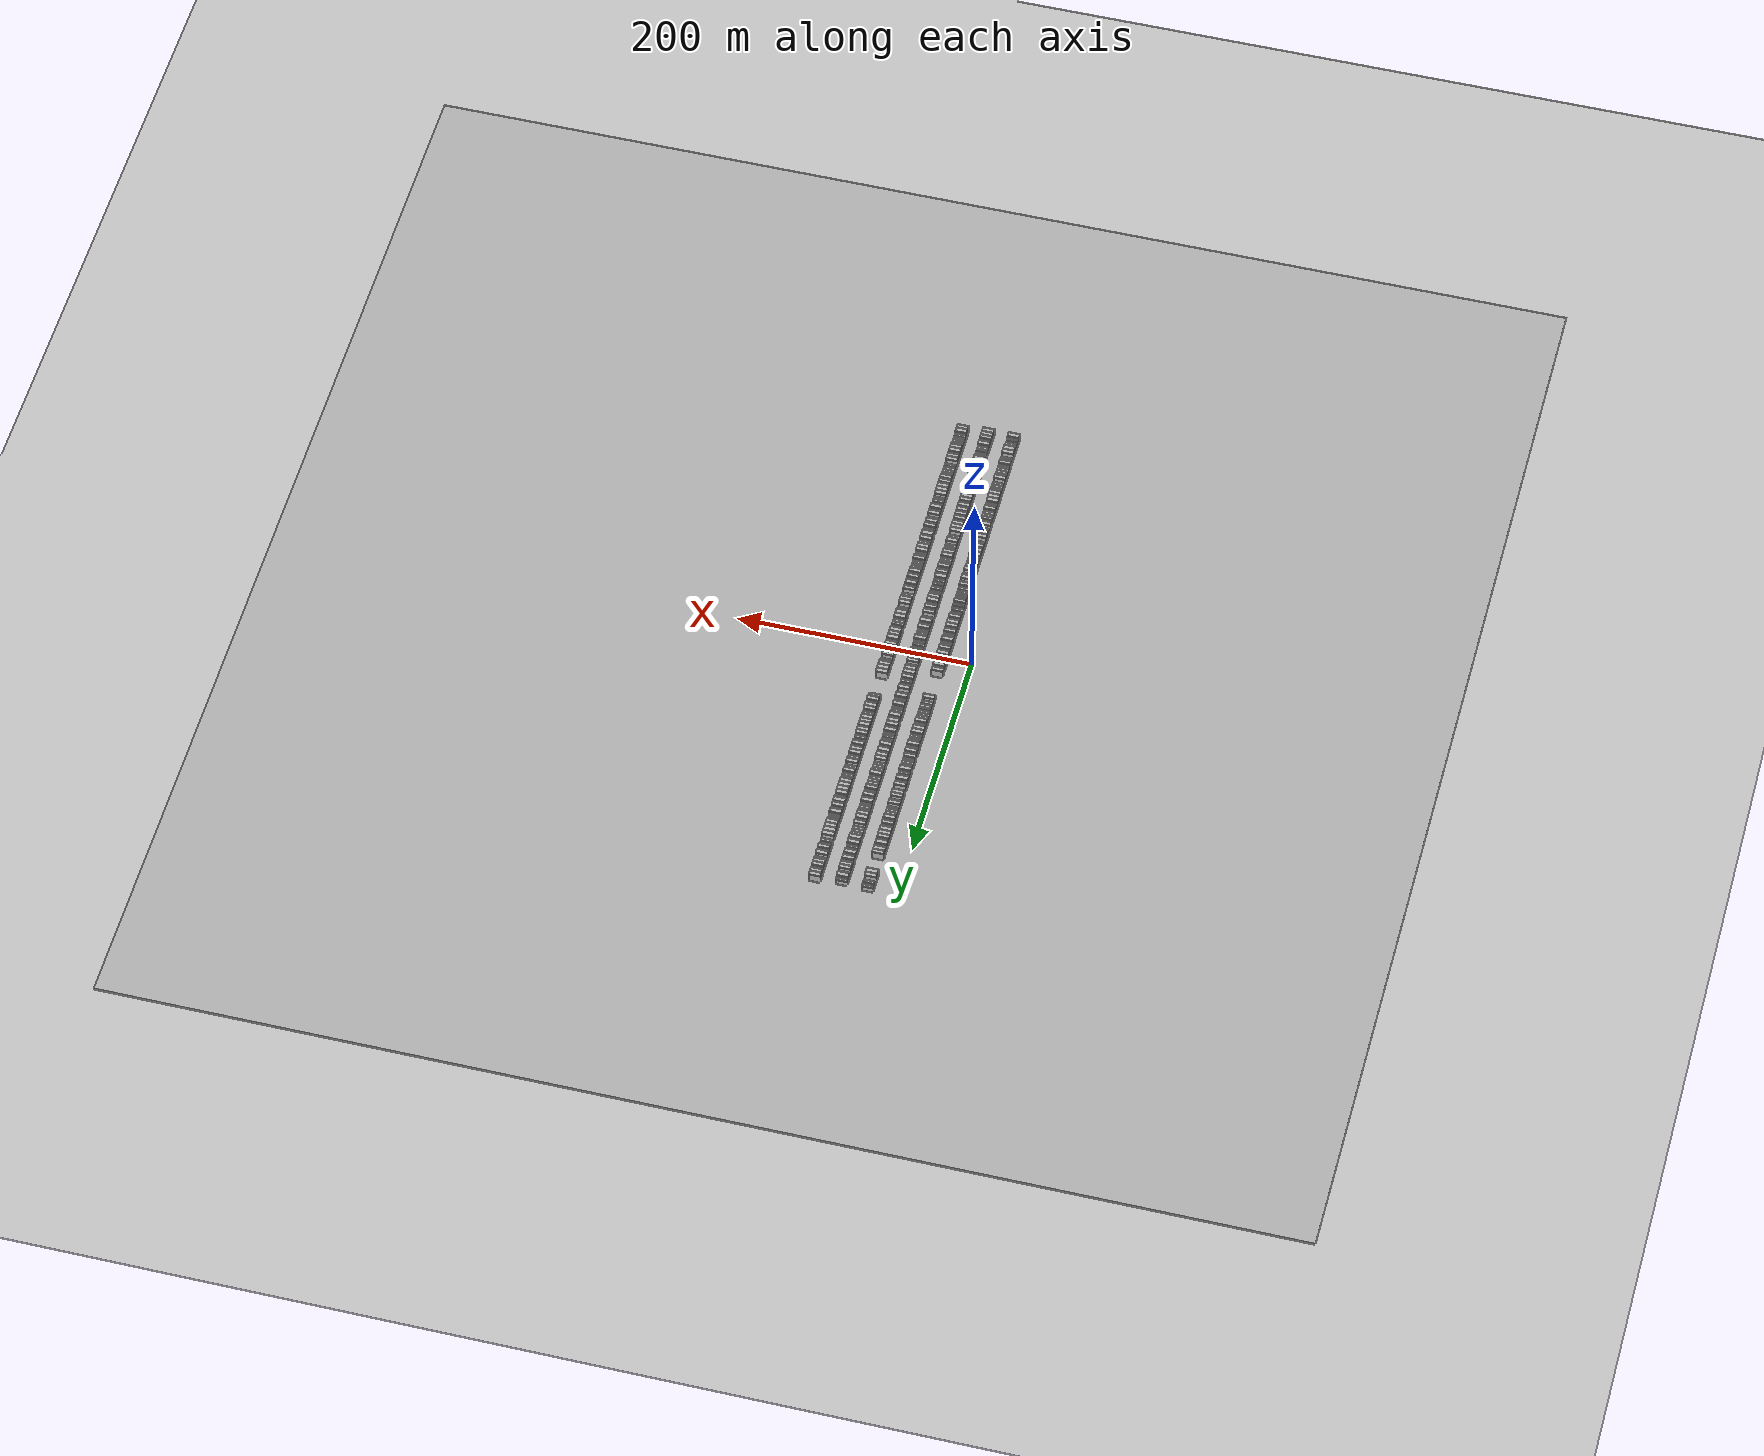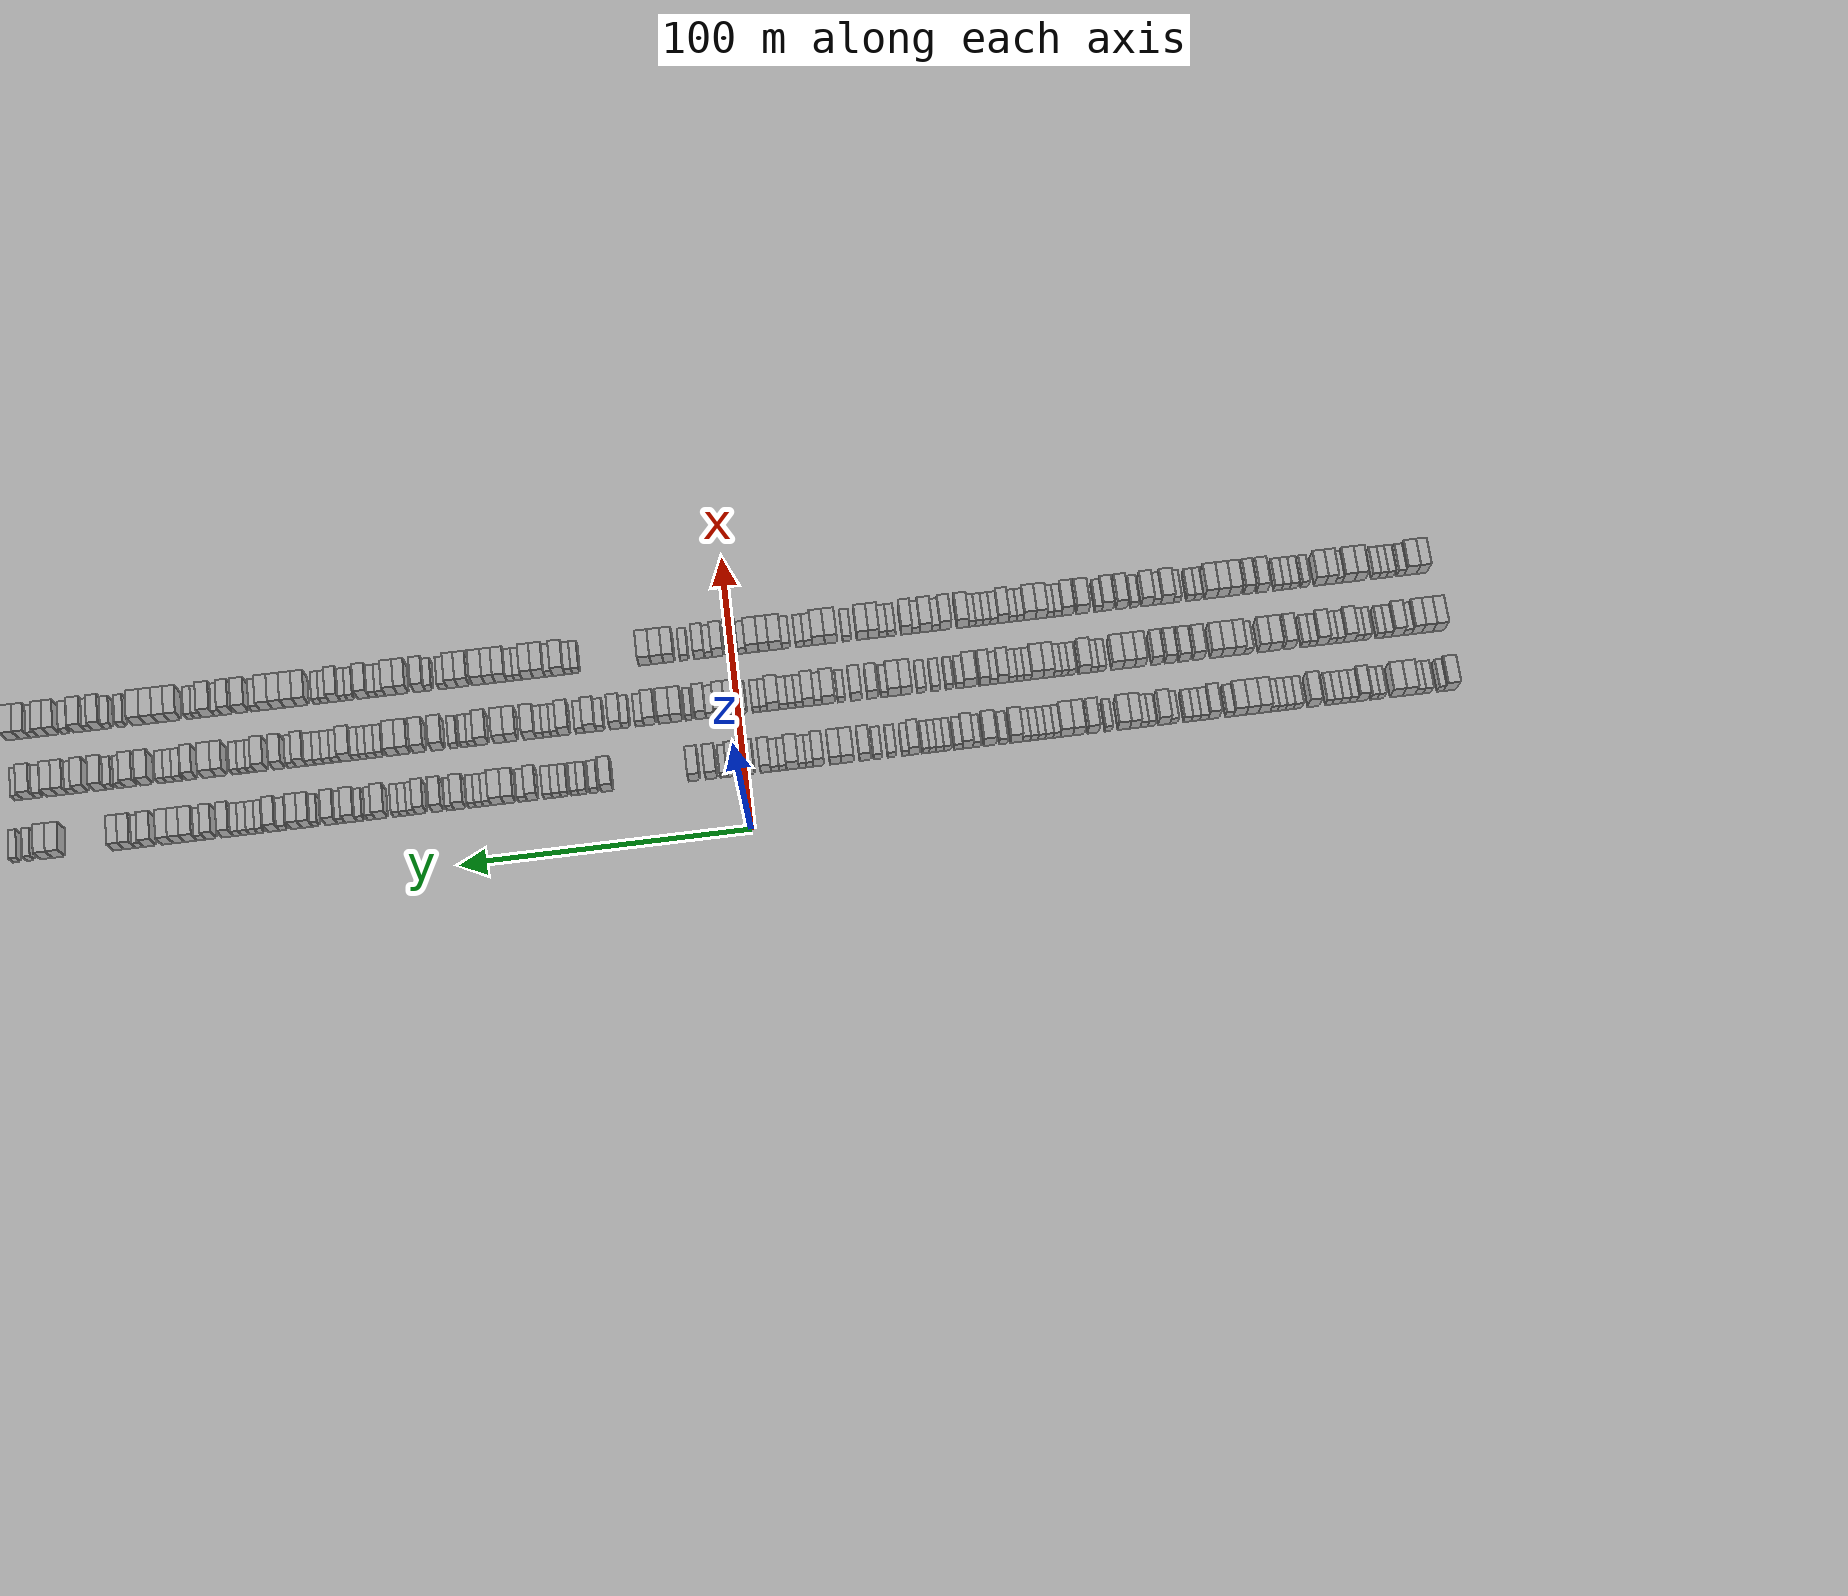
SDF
<?xml version="1.0" encoding="utf-8"?>

<sdf version="1.6">

   <world name="default">

      <gui fullscreen="0">

         <camera name="user_camera">

            <pose>-15 0 4.57585 0 0 0</pose>

            <view_controller>orbit</view_controller>

         </camera>

      </gui>

      <scene>

         <sky>

           <clouds>

             <speed>12</speed>

           </clouds>

         </sky>

         <ambient>0.4 0.4 0.4 1</ambient>

         <background>0.7 0.7 0.7 1</background>

         <shadows>1</shadows>

      </scene>

      <gravity>0 0 -9.8066</gravity>

      <magnetic_field>6e-06 2.3e-05 -4.2e-05</magnetic_field>

      <physics default="0" name="default_physics" type="ode">

         <ode>

            <solver>

               <type>quick</type>

               <iters>10</iters>

               <sor>1.0</sor>

               <use_dynamic_moi_rescaling>0</use_dynamic_moi_rescaling>

            </solver>

            <constraints>

               <cfm>0</cfm>

               <erp>0.2</erp>

               <contact_max_correcting_vel>100</contact_max_correcting_vel>

               <contact_surface_layer>0.001</contact_surface_layer>

            </constraints>

         </ode>

         <max_step_size>0.004</max_step_size>

         <real_time_factor>1</real_time_factor>

         <real_time_update_rate>250</real_time_update_rate>

      </physics>

      <light name="sun" type="directional">

         <cast_shadows>1</cast_shadows>

         <pose>0 0 10 0 0 0</pose>

         <diffuse>0.8 0.8 0.8 1</diffuse>

         <specular>0.2 0.2 0.2 1</specular>

         <attenuation>

            <range>1000</range>

            <constant>0.9</constant>

            <linear>0.01</linear>

            <quadratic>0.001</quadratic>

         </attenuation>

         <direction>-0.5 0.1 -0.9</direction>

      </light>

      <include>

         <name>ground_plane_1</name>

         <uri>model://HANNAS_ground_plane</uri>

         <pose>0 0 0  0 0 0</pose>

      </include>

      <include>

         <name>ground_plane_2</name>

         <uri>model://HANNAS_ground_plane</uri>

         <pose>100 0 0  0 0 0</pose>

      </include>

      <model name="building_1">

         <static>1</static>

         <pose frame="">25.0000 -245.7820 0 0.000000 0.000000 0.000000</pose>

         <link name="link">

            <pose frame="">0 0 4.50 0 0 0</pose>

            <collision name="collision">

               <geometry>

                  <box>

                     <size>10.0000 4.4360 9.0000</size>

                  </box>

               </geometry>

               <max_contacts>10</max_contacts>

               <surface>

                  <contact>

                     <ode/>

                  </contact>

                  <bounce/>

                  <friction>

                     <torsional>

                        <ode/>

                     </torsional>

                     <ode/>

                  </friction>

               </surface>

            </collision>

            <visual name="visual">

               <cast_shadows>0</cast_shadows>

               <geometry>

                  <box>

                     <size>10.0000 4.4360 9.0000</size>

                  </box>

               </geometry>

               <material>

                  <script>

                     <uri>model://HANNAS_wall/materials/scripts</uri>

                     <uri>model://HANNAS_wall/materials/textures</uri>

                     <name>vrc/HANNAS_wall</name>

                  </script>

               </material>

            </visual>

            <self_collide>0</self_collide>

            <enable_wind>0</enable_wind>

            <kinematic>0</kinematic>

         </link>

      </model>

      <model name="building_2">

         <static>1</static>

         <pose frame="">25.0000 -242.3404 0 0.000000 0.000000 0.000000</pose>

         <link name="link">

            <pose frame="">0 0 3.00 0 0 0</pose>

            <collision name="collision">

               <geometry>

                  <box>

                     <size>10.0000 2.4471 6.0000</size>

                  </box>

               </geometry>

               <max_contacts>10</max_contacts>

               <surface>

                  <contact>

                     <ode/>

                  </contact>

                  <bounce/>

                  <friction>

                     <torsional>

                        <ode/>

                     </torsional>

                     <ode/>

                  </friction>

               </surface>

            </collision>

            <visual name="visual">

               <cast_shadows>0</cast_shadows>

               <geometry>

                  <box>

                     <size>10.0000 2.4471 6.0000</size>

                  </box>

               </geometry>

               <material>

                  <script>

                     <uri>model://HANNAS_wall/materials/scripts</uri>

                     <uri>model://HANNAS_wall/materials/textures</uri>

                     <name>vrc/HANNAS_wall</name>

                  </script>

               </material>

            </visual>

            <self_collide>0</self_collide>

            <enable_wind>0</enable_wind>

            <kinematic>0</kinematic>

         </link>

      </model>

      <model name="building_3">

         <static>1</static>

         <pose frame="">25.0000 -237.7306 0 0.000000 0.000000 0.000000</pose>

         <link name="link">

            <pose frame="">0 0 3.00 0 0 0</pose>

            <collision name="collision">

               <geometry>

                  <box>

                     <size>10.0000 2.7723 6.0000</size>

                  </box>

               </geometry>

               <max_contacts>10</max_contacts>

               <surface>

                  <contact>

                     <ode/>

                  </contact>

                  <bounce/>

                  <friction>

                     <torsional>

                        <ode/>

                     </torsional>

                     <ode/>

                  </friction>

               </surface>

            </collision>

            <visual name="visual">

               <cast_shadows>0</cast_shadows>

               <geometry>

                  <box>

                     <size>10.0000 2.7723 6.0000</size>

                  </box>

               </geometry>

               <material>

                  <script>

                     <uri>model://HANNAS_wall/materials/scripts</uri>

                     <uri>model://HANNAS_wall/materials/textures</uri>

                     <name>vrc/HANNAS_wall</name>

                  </script>

               </material>

            </visual>

            <self_collide>0</self_collide>

            <enable_wind>0</enable_wind>

            <kinematic>0</kinematic>

         </link>

      </model>

      <model name="building_4">

         <static>1</static>

         <pose frame="">25.0000 -234.9092 0 0.000000 0.000000 0.000000</pose>

         <link name="link">

            <pose frame="">0 0 3.00 0 0 0</pose>

            <collision name="collision">

               <geometry>

                  <box>

                     <size>10.0000 2.8706 6.0000</size>

                  </box>

               </geometry>

               <max_contacts>10</max_contacts>

               <surface>

                  <contact>

                     <ode/>

                  </contact>

                  <bounce/>

                  <friction>

                     <torsional>

                        <ode/>

                     </torsional>

                     <ode/>

                  </friction>

               </surface>

            </collision>

            <visual name="visual">

               <cast_shadows>0</cast_shadows>

               <geometry>

                  <box>

                     <size>10.0000 2.8706 6.0000</size>

                  </box>

               </geometry>

               <material>

                  <script>

                     <uri>model://HANNAS_wall/materials/scripts</uri>

                     <uri>model://HANNAS_wall/materials/textures</uri>

                     <name>vrc/HANNAS_wall</name>

                  </script>

               </material>

            </visual>

            <self_collide>0</self_collide>

            <enable_wind>0</enable_wind>

            <kinematic>0</kinematic>

         </link>

      </model>

      <model name="building_5">

         <static>1</static>

         <pose frame="">25.0000 -231.2819 0 0.000000 0.000000 0.000000</pose>

         <link name="link">

            <pose frame="">0 0 4.50 0 0 0</pose>

            <collision name="collision">

               <geometry>

                  <box>

                     <size>10.0000 4.3839 9.0000</size>

                  </box>

               </geometry>

               <max_contacts>10</max_contacts>

               <surface>

                  <contact>

                     <ode/>

                  </contact>

                  <bounce/>

                  <friction>

                     <torsional>

                        <ode/>

                     </torsional>

                     <ode/>

                  </friction>

               </surface>

            </collision>

            <visual name="visual">

               <cast_shadows>0</cast_shadows>

               <geometry>

                  <box>

                     <size>10.0000 4.3839 9.0000</size>

                  </box>

               </geometry>

               <material>

                  <script>

                     <uri>model://HANNAS_wall/materials/scripts</uri>

                     <uri>model://HANNAS_wall/materials/textures</uri>

                     <name>vrc/HANNAS_wall</name>

                  </script>

               </material>

            </visual>

            <self_collide>0</self_collide>

            <enable_wind>0</enable_wind>

            <kinematic>0</kinematic>

         </link>

      </model>

      <model name="building_6">

         <static>1</static>

         <pose frame="">25.0000 -226.8421 0 0.000000 0.000000 0.000000</pose>

         <link name="link">

            <pose frame="">0 0 4.50 0 0 0</pose>

            <collision name="collision">

               <geometry>

                  <box>

                     <size>10.0000 4.4957 9.0000</size>

                  </box>

               </geometry>

               <max_contacts>10</max_contacts>

               <surface>

                  <contact>

                     <ode/>

                  </contact>

                  <bounce/>

                  <friction>

                     <torsional>

                        <ode/>

                     </torsional>

                     <ode/>

                  </friction>

               </surface>

            </collision>

            <visual name="visual">

               <cast_shadows>0</cast_shadows>

               <geometry>

                  <box>

                     <size>10.0000 4.4957 9.0000</size>

                  </box>

               </geometry>

               <material>

                  <script>

                     <uri>model://HANNAS_wall/materials/scripts</uri>

                     <uri>model://HANNAS_wall/materials/textures</uri>

                     <name>vrc/HANNAS_wall</name>

                  </script>

               </material>

            </visual>

            <self_collide>0</self_collide>

            <enable_wind>0</enable_wind>

            <kinematic>0</kinematic>

         </link>

      </model>

      <model name="building_7">

         <static>1</static>

         <pose frame="">25.0000 -221.3880 0 0.000000 0.000000 0.000000</pose>

         <link name="link">

            <pose frame="">0 0 3.00 0 0 0</pose>

            <collision name="collision">

               <geometry>

                  <box>

                     <size>10.0000 2.4125 6.0000</size>

                  </box>

               </geometry>

               <max_contacts>10</max_contacts>

               <surface>

                  <contact>

                     <ode/>

                  </contact>

                  <bounce/>

                  <friction>

                     <torsional>

                        <ode/>

                     </torsional>

                     <ode/>

                  </friction>

               </surface>

            </collision>

            <visual name="visual">

               <cast_shadows>0</cast_shadows>

               <geometry>

                  <box>

                     <size>10.0000 2.4125 6.0000</size>

                  </box>

               </geometry>

               <material>

                  <script>

                     <uri>model://HANNAS_wall/materials/scripts</uri>

                     <uri>model://HANNAS_wall/materials/textures</uri>

                     <name>vrc/HANNAS_wall</name>

                  </script>

               </material>

            </visual>

            <self_collide>0</self_collide>

            <enable_wind>0</enable_wind>

            <kinematic>0</kinematic>

         </link>

      </model>

      <model name="building_8">

         <static>1</static>

         <pose frame="">25.0000 -218.9477 0 0.000000 0.000000 0.000000</pose>

         <link name="link">

            <pose frame="">0 0 3.00 0 0 0</pose>

            <collision name="collision">

               <geometry>

                  <box>

                     <size>10.0000 2.4682 6.0000</size>

                  </box>

               </geometry>

               <max_contacts>10</max_contacts>

               <surface>

                  <contact>

                     <ode/>

                  </contact>

                  <bounce/>

                  <friction>

                     <torsional>

                        <ode/>

                     </torsional>

                     <ode/>

                  </friction>

               </surface>

            </collision>

            <visual name="visual">

               <cast_shadows>0</cast_shadows>

               <geometry>

                  <box>

                     <size>10.0000 2.4682 6.0000</size>

                  </box>

               </geometry>

               <material>

                  <script>

                     <uri>model://HANNAS_wall/materials/scripts</uri>

                     <uri>model://HANNAS_wall/materials/textures</uri>

                     <name>vrc/HANNAS_wall</name>

                  </script>

               </material>

            </visual>

            <self_collide>0</self_collide>

            <enable_wind>0</enable_wind>

            <kinematic>0</kinematic>

         </link>

      </model>

      <model name="building_9">

         <static>1</static>

         <pose frame="">25.0000 -214.8393 0 0.000000 0.000000 0.000000</pose>

         <link name="link">

            <pose frame="">0 0 4.50 0 0 0</pose>

            <collision name="collision">

               <geometry>

                  <box>

                     <size>10.0000 3.7484 9.0000</size>

                  </box>

               </geometry>

               <max_contacts>10</max_contacts>

               <surface>

                  <contact>

                     <ode/>

                  </contact>

                  <bounce/>

                  <friction>

                     <torsional>

                        <ode/>

                     </torsional>

                     <ode/>

                  </friction>

               </surface>

            </collision>

            <visual name="visual">

               <cast_shadows>0</cast_shadows>

               <geometry>

                  <box>

                     <size>10.0000 3.7484 9.0000</size>

                  </box>

               </geometry>

               <material>

                  <script>

                     <uri>model://HANNAS_wall/materials/scripts</uri>

                     <uri>model://HANNAS_wall/materials/textures</uri>

                     <name>vrc/HANNAS_wall</name>

                  </script>

               </material>

            </visual>

            <self_collide>0</self_collide>

            <enable_wind>0</enable_wind>

            <kinematic>0</kinematic>

         </link>

      </model>

      <model name="building_10">

         <static>1</static>

         <pose frame="">25.0000 -211.6460 0 0.000000 0.000000 0.000000</pose>

         <link name="link">

            <pose frame="">0 0 3.00 0 0 0</pose>

            <collision name="collision">

               <geometry>

                  <box>

                     <size>10.0000 2.6384 6.0000</size>

                  </box>

               </geometry>

               <max_contacts>10</max_contacts>

               <surface>

                  <contact>

                     <ode/>

                  </contact>

                  <bounce/>

                  <friction>

                     <torsional>

                        <ode/>

                     </torsional>

                     <ode/>

                  </friction>

               </surface>

            </collision>

            <visual name="visual">

               <cast_shadows>0</cast_shadows>

               <geometry>

                  <box>

                     <size>10.0000 2.6384 6.0000</size>

                  </box>

               </geometry>

               <material>

                  <script>

                     <uri>model://HANNAS_wall/materials/scripts</uri>

                     <uri>model://HANNAS_wall/materials/textures</uri>

                     <name>vrc/HANNAS_wall</name>

                  </script>

               </material>

            </visual>

            <self_collide>0</self_collide>

            <enable_wind>0</enable_wind>

            <kinematic>0</kinematic>

         </link>

      </model>

      <model name="building_11">

         <static>1</static>

         <pose frame="">25.0000 -208.8383 0 0.000000 0.000000 0.000000</pose>

         <link name="link">

            <pose frame="">0 0 3.00 0 0 0</pose>

            <collision name="collision">

               <geometry>

                  <box>

                     <size>10.0000 2.9770 6.0000</size>

                  </box>

               </geometry>

               <max_contacts>10</max_contacts>

               <surface>

                  <contact>

                     <ode/>

                  </contact>

                  <bounce/>

                  <friction>

                     <torsional>

                        <ode/>

                     </torsional>

                     <ode/>

                  </friction>

               </surface>

            </collision>

            <visual name="visual">

               <cast_shadows>0</cast_shadows>

               <geometry>

                  <box>

                     <size>10.0000 2.9770 6.0000</size>

                  </box>

               </geometry>

               <material>

                  <script>

                     <uri>model://HANNAS_wall/materials/scripts</uri>

                     <uri>model://HANNAS_wall/materials/textures</uri>

                     <name>vrc/HANNAS_wall</name>

                  </script>

               </material>

            </visual>

            <self_collide>0</self_collide>

            <enable_wind>0</enable_wind>

            <kinematic>0</kinematic>

         </link>

      </model>

      <model name="building_12">

         <static>1</static>

         <pose frame="">25.0000 -205.8643 0 0.000000 0.000000 0.000000</pose>

         <link name="link">

            <pose frame="">0 0 3.00 0 0 0</pose>

            <collision name="collision">

               <geometry>

                  <box>

                     <size>10.0000 2.9710 6.0000</size>

                  </box>

               </geometry>

               <max_contacts>10</max_contacts>

               <surface>

                  <contact>

                     <ode/>

                  </contact>

                  <bounce/>

                  <friction>

                     <torsional>

                        <ode/>

                     </torsional>

                     <ode/>

                  </friction>

               </surface>

            </collision>

            <visual name="visual">

               <cast_shadows>0</cast_shadows>

               <geometry>

                  <box>

                     <size>10.0000 2.9710 6.0000</size>

                  </box>

               </geometry>

               <material>

                  <script>

                     <uri>model://HANNAS_wall/materials/scripts</uri>

                     <uri>model://HANNAS_wall/materials/textures</uri>

                     <name>vrc/HANNAS_wall</name>

                  </script>

               </material>

            </visual>

            <self_collide>0</self_collide>

            <enable_wind>0</enable_wind>

            <kinematic>0</kinematic>

         </link>

      </model>

      <model name="building_13">

         <static>1</static>

         <pose frame="">25.0000 -203.0817 0 0.000000 0.000000 0.000000</pose>

         <link name="link">

            <pose frame="">0 0 3.00 0 0 0</pose>

            <collision name="collision">

               <geometry>

                  <box>

                     <size>10.0000 2.5942 6.0000</size>

                  </box>

               </geometry>

               <max_contacts>10</max_contacts>

               <surface>

                  <contact>

                     <ode/>

                  </contact>

                  <bounce/>

                  <friction>

                     <torsional>

                        <ode/>

                     </torsional>

                     <ode/>

                  </friction>

               </surface>

            </collision>

            <visual name="visual">

               <cast_shadows>0</cast_shadows>

               <geometry>

                  <box>

                     <size>10.0000 2.5942 6.0000</size>

                  </box>

               </geometry>

               <material>

                  <script>

                     <uri>model://HANNAS_wall/materials/scripts</uri>

                     <uri>model://HANNAS_wall/materials/textures</uri>

                     <name>vrc/HANNAS_wall</name>

                  </script>

               </material>

            </visual>

            <self_collide>0</self_collide>

            <enable_wind>0</enable_wind>

            <kinematic>0</kinematic>

         </link>

      </model>

      <model name="building_14">

         <static>1</static>

         <pose frame="">25.0000 -197.6936 0 0.000000 0.000000 0.000000</pose>

         <link name="link">

            <pose frame="">0 0 4.50 0 0 0</pose>

            <collision name="collision">

               <geometry>

                  <box>

                     <size>10.0000 4.1819 9.0000</size>

                  </box>

               </geometry>

               <max_contacts>10</max_contacts>

               <surface>

                  <contact>

                     <ode/>

                  </contact>

                  <bounce/>

                  <friction>

                     <torsional>

                        <ode/>

                     </torsional>

                     <ode/>

                  </friction>

               </surface>

            </collision>

            <visual name="visual">

               <cast_shadows>0</cast_shadows>

               <geometry>

                  <box>

                     <size>10.0000 4.1819 9.0000</size>

                  </box>

               </geometry>

               <material>

                  <script>

                     <uri>model://HANNAS_wall/materials/scripts</uri>

                     <uri>model://HANNAS_wall/materials/textures</uri>

                     <name>vrc/HANNAS_wall</name>

                  </script>

               </material>

            </visual>

            <self_collide>0</self_collide>

            <enable_wind>0</enable_wind>

            <kinematic>0</kinematic>

         </link>

      </model>

      <model name="building_15">

         <static>1</static>

         <pose frame="">25.0000 -192.1597 0 0.000000 0.000000 0.000000</pose>

         <link name="link">

            <pose frame="">0 0 3.00 0 0 0</pose>

            <collision name="collision">

               <geometry>

                  <box>

                     <size>10.0000 2.8860 6.0000</size>

                  </box>

               </geometry>

               <max_contacts>10</max_contacts>

               <surface>

                  <contact>

                     <ode/>

                  </contact>

                  <bounce/>

                  <friction>

                     <torsional>

                        <ode/>

                     </torsional>

                     <ode/>

                  </friction>

               </surface>

            </collision>

            <visual name="visual">

               <cast_shadows>0</cast_shadows>

               <geometry>

                  <box>

                     <size>10.0000 2.8860 6.0000</size>

                  </box>

               </geometry>

               <material>

                  <script>

                     <uri>model://HANNAS_wall/materials/scripts</uri>

                     <uri>model://HANNAS_wall/materials/textures</uri>

                     <name>vrc/HANNAS_wall</name>

                  </script>

               </material>

            </visual>

            <self_collide>0</self_collide>

            <enable_wind>0</enable_wind>

            <kinematic>0</kinematic>

         </link>

      </model>

      <model name="building_16">

         <static>1</static>

         <pose frame="">25.0000 -189.2978 0 0.000000 0.000000 0.000000</pose>

         <link name="link">

            <pose frame="">0 0 3.00 0 0 0</pose>

            <collision name="collision">

               <geometry>

                  <box>

                     <size>10.0000 2.8378 6.0000</size>

                  </box>

               </geometry>

               <max_contacts>10</max_contacts>

               <surface>

                  <contact>

                     <ode/>

                  </contact>

                  <bounce/>

                  <friction>

                     <torsional>

                        <ode/>

                     </torsional>

                     <ode/>

                  </friction>

               </surface>

            </collision>

            <visual name="visual">

               <cast_shadows>0</cast_shadows>

               <geometry>

                  <box>

                     <size>10.0000 2.8378 6.0000</size>

                  </box>

               </geometry>

               <material>

                  <script>

                     <uri>model://HANNAS_wall/materials/scripts</uri>

                     <uri>model://HANNAS_wall/materials/textures</uri>

                     <name>vrc/HANNAS_wall</name>

                  </script>

               </material>

            </visual>

            <self_collide>0</self_collide>

            <enable_wind>0</enable_wind>

            <kinematic>0</kinematic>

         </link>

      </model>

      <model name="building_17">

         <static>1</static>

         <pose frame="">25.0000 -186.5145 0 0.000000 0.000000 0.000000</pose>

         <link name="link">

            <pose frame="">0 0 3.00 0 0 0</pose>

            <collision name="collision">

               <geometry>

                  <box>

                     <size>10.0000 2.7287 6.0000</size>

                  </box>

               </geometry>

               <max_contacts>10</max_contacts>

               <surface>

                  <contact>

                     <ode/>

                  </contact>

                  <bounce/>

                  <friction>

                     <torsional>

                        <ode/>

                     </torsional>

                     <ode/>

                  </friction>

               </surface>

            </collision>

            <visual name="visual">

               <cast_shadows>0</cast_shadows>

               <geometry>

                  <box>

                     <size>10.0000 2.7287 6.0000</size>

                  </box>

               </geometry>

               <material>

                  <script>

                     <uri>model://HANNAS_wall/materials/scripts</uri>

                     <uri>model://HANNAS_wall/materials/textures</uri>

                     <name>vrc/HANNAS_wall</name>

                  </script>

               </material>

            </visual>

            <self_collide>0</self_collide>

            <enable_wind>0</enable_wind>

            <kinematic>0</kinematic>

         </link>

      </model>

      <model name="building_18">

         <static>1</static>

         <pose frame="">25.0000 -183.8491 0 0.000000 0.000000 0.000000</pose>

         <link name="link">

            <pose frame="">0 0 3.00 0 0 0</pose>

            <collision name="collision">

               <geometry>

                  <box>

                     <size>10.0000 2.6021 6.0000</size>

                  </box>

               </geometry>

               <max_contacts>10</max_contacts>

               <surface>

                  <contact>

                     <ode/>

                  </contact>

                  <bounce/>

                  <friction>

                     <torsional>

                        <ode/>

                     </torsional>

                     <ode/>

                  </friction>

               </surface>

            </collision>

            <visual name="visual">

               <cast_shadows>0</cast_shadows>

               <geometry>

                  <box>

                     <size>10.0000 2.6021 6.0000</size>

                  </box>

               </geometry>

               <material>

                  <script>

                     <uri>model://HANNAS_wall/materials/scripts</uri>

                     <uri>model://HANNAS_wall/materials/textures</uri>

                     <name>vrc/HANNAS_wall</name>

                  </script>

               </material>

            </visual>

            <self_collide>0</self_collide>

            <enable_wind>0</enable_wind>

            <kinematic>0</kinematic>

         </link>

      </model>

      <model name="building_19">

         <static>1</static>

         <pose frame="">25.0000 -180.4580 0 0.000000 0.000000 0.000000</pose>

         <link name="link">

            <pose frame="">0 0 4.50 0 0 0</pose>

            <collision name="collision">

               <geometry>

                  <box>

                     <size>10.0000 4.1801 9.0000</size>

                  </box>

               </geometry>

               <max_contacts>10</max_contacts>

               <surface>

                  <contact>

                     <ode/>

                  </contact>

                  <bounce/>

                  <friction>

                     <torsional>

                        <ode/>

                     </torsional>

                     <ode/>

                  </friction>

               </surface>

            </collision>

            <visual name="visual">

               <cast_shadows>0</cast_shadows>

               <geometry>

                  <box>

                     <size>10.0000 4.1801 9.0000</size>

                  </box>

               </geometry>

               <material>

                  <script>

                     <uri>model://HANNAS_wall/materials/scripts</uri>

                     <uri>model://HANNAS_wall/materials/textures</uri>

                     <name>vrc/HANNAS_wall</name>

                  </script>

               </material>

            </visual>

            <self_collide>0</self_collide>

            <enable_wind>0</enable_wind>

            <kinematic>0</kinematic>

         </link>

      </model>

      <model name="building_20">

         <static>1</static>

         <pose frame="">25.0000 -176.2188 0 0.000000 0.000000 0.000000</pose>

         <link name="link">

            <pose frame="">0 0 4.50 0 0 0</pose>

            <collision name="collision">

               <geometry>

                  <box>

                     <size>10.0000 4.2982 9.0000</size>

                  </box>

               </geometry>

               <max_contacts>10</max_contacts>

               <surface>

                  <contact>

                     <ode/>

                  </contact>

                  <bounce/>

                  <friction>

                     <torsional>

                        <ode/>

                     </torsional>

                     <ode/>

                  </friction>

               </surface>

            </collision>

            <visual name="visual">

               <cast_shadows>0</cast_shadows>

               <geometry>

                  <box>

                     <size>10.0000 4.2982 9.0000</size>

                  </box>

               </geometry>

               <material>

                  <script>

                     <uri>model://HANNAS_wall/materials/scripts</uri>

                     <uri>model://HANNAS_wall/materials/textures</uri>

                     <name>vrc/HANNAS_wall</name>

                  </script>

               </material>

            </visual>

            <self_collide>0</self_collide>

            <enable_wind>0</enable_wind>

            <kinematic>0</kinematic>

         </link>

      </model>

      <model name="building_21">

         <static>1</static>

         <pose frame="">25.0000 -171.8665 0 0.000000 0.000000 0.000000</pose>

         <link name="link">

            <pose frame="">0 0 4.50 0 0 0</pose>

            <collision name="collision">

               <geometry>

                  <box>

                     <size>10.0000 4.4064 9.0000</size>

                  </box>

               </geometry>

               <max_contacts>10</max_contacts>

               <surface>

                  <contact>

                     <ode/>

                  </contact>

                  <bounce/>

                  <friction>

                     <torsional>

                        <ode/>

                     </torsional>

                     <ode/>

                  </friction>

               </surface>

            </collision>

            <visual name="visual">

               <cast_shadows>0</cast_shadows>

               <geometry>

                  <box>

                     <size>10.0000 4.4064 9.0000</size>

                  </box>

               </geometry>

               <material>

                  <script>

                     <uri>model://HANNAS_wall/materials/scripts</uri>

                     <uri>model://HANNAS_wall/materials/textures</uri>

                     <name>vrc/HANNAS_wall</name>

                  </script>

               </material>

            </visual>

            <self_collide>0</self_collide>

            <enable_wind>0</enable_wind>

            <kinematic>0</kinematic>

         </link>

      </model>

      <model name="building_22">

         <static>1</static>

         <pose frame="">25.0000 -168.1810 0 0.000000 0.000000 0.000000</pose>

         <link name="link">

            <pose frame="">0 0 3.00 0 0 0</pose>

            <collision name="collision">

               <geometry>

                  <box>

                     <size>10.0000 2.9647 6.0000</size>

                  </box>

               </geometry>

               <max_contacts>10</max_contacts>

               <surface>

                  <contact>

                     <ode/>

                  </contact>

                  <bounce/>

                  <friction>

                     <torsional>

                        <ode/>

                     </torsional>

                     <ode/>

                  </friction>

               </surface>

            </collision>

            <visual name="visual">

               <cast_shadows>0</cast_shadows>

               <geometry>

                  <box>

                     <size>10.0000 2.9647 6.0000</size>

                  </box>

               </geometry>

               <material>

                  <script>

                     <uri>model://HANNAS_wall/materials/scripts</uri>

                     <uri>model://HANNAS_wall/materials/textures</uri>

                     <name>vrc/HANNAS_wall</name>

                  </script>

               </material>

            </visual>

            <self_collide>0</self_collide>

            <enable_wind>0</enable_wind>

            <kinematic>0</kinematic>

         </link>

      </model>

      <model name="building_23">

         <static>1</static>

         <pose frame="">25.0000 -162.7484 0 0.000000 0.000000 0.000000</pose>

         <link name="link">

            <pose frame="">0 0 4.50 0 0 0</pose>

            <collision name="collision">

               <geometry>

                  <box>

                     <size>10.0000 3.9005 9.0000</size>

                  </box>

               </geometry>

               <max_contacts>10</max_contacts>

               <surface>

                  <contact>

                     <ode/>

                  </contact>

                  <bounce/>

                  <friction>

                     <torsional>

                        <ode/>

                     </torsional>

                     <ode/>

                  </friction>

               </surface>

            </collision>

            <visual name="visual">

               <cast_shadows>0</cast_shadows>

               <geometry>

                  <box>

                     <size>10.0000 3.9005 9.0000</size>

                  </box>

               </geometry>

               <material>

                  <script>

                     <uri>model://HANNAS_wall/materials/scripts</uri>

                     <uri>model://HANNAS_wall/materials/textures</uri>

                     <name>vrc/HANNAS_wall</name>

                  </script>

               </material>

            </visual>

            <self_collide>0</self_collide>

            <enable_wind>0</enable_wind>

            <kinematic>0</kinematic>

         </link>

      </model>

      <model name="building_24">

         <static>1</static>

         <pose frame="">25.0000 -159.3127 0 0.000000 0.000000 0.000000</pose>

         <link name="link">

            <pose frame="">0 0 3.00 0 0 0</pose>

            <collision name="collision">

               <geometry>

                  <box>

                     <size>10.0000 2.9710 6.0000</size>

                  </box>

               </geometry>

               <max_contacts>10</max_contacts>

               <surface>

                  <contact>

                     <ode/>

                  </contact>

                  <bounce/>

                  <friction>

                     <torsional>

                        <ode/>

                     </torsional>

                     <ode/>

                  </friction>

               </surface>

            </collision>

            <visual name="visual">

               <cast_shadows>0</cast_shadows>

               <geometry>

                  <box>

                     <size>10.0000 2.9710 6.0000</size>

                  </box>

               </geometry>

               <material>

                  <script>

                     <uri>model://HANNAS_wall/materials/scripts</uri>

                     <uri>model://HANNAS_wall/materials/textures</uri>

                     <name>vrc/HANNAS_wall</name>

                  </script>

               </material>

            </visual>

            <self_collide>0</self_collide>

            <enable_wind>0</enable_wind>

            <kinematic>0</kinematic>

         </link>

      </model>

      <model name="building_25">

         <static>1</static>

         <pose frame="">25.0000 -156.4310 0 0.000000 0.000000 0.000000</pose>

         <link name="link">

            <pose frame="">0 0 3.00 0 0 0</pose>

            <collision name="collision">

               <geometry>

                  <box>

                     <size>10.0000 2.7923 6.0000</size>

                  </box>

               </geometry>

               <max_contacts>10</max_contacts>

               <surface>

                  <contact>

                     <ode/>

                  </contact>

                  <bounce/>

                  <friction>

                     <torsional>

                        <ode/>

                     </torsional>

                     <ode/>

                  </friction>

               </surface>

            </collision>

            <visual name="visual">

               <cast_shadows>0</cast_shadows>

               <geometry>

                  <box>

                     <size>10.0000 2.7923 6.0000</size>

                  </box>

               </geometry>

               <material>

                  <script>

                     <uri>model://HANNAS_wall/materials/scripts</uri>

                     <uri>model://HANNAS_wall/materials/textures</uri>

                     <name>vrc/HANNAS_wall</name>

                  </script>

               </material>

            </visual>

            <self_collide>0</self_collide>

            <enable_wind>0</enable_wind>

            <kinematic>0</kinematic>

         </link>

      </model>

      <model name="building_26">

         <static>1</static>

         <pose frame="">25.0000 -153.5537 0 0.000000 0.000000 0.000000</pose>

         <link name="link">

            <pose frame="">0 0 3.00 0 0 0</pose>

            <collision name="collision">

               <geometry>

                  <box>

                     <size>10.0000 2.9624 6.0000</size>

                  </box>

               </geometry>

               <max_contacts>10</max_contacts>

               <surface>

                  <contact>

                     <ode/>

                  </contact>

                  <bounce/>

                  <friction>

                     <torsional>

                        <ode/>

                     </torsional>

                     <ode/>

                  </friction>

               </surface>

            </collision>

            <visual name="visual">

               <cast_shadows>0</cast_shadows>

               <geometry>

                  <box>

                     <size>10.0000 2.9624 6.0000</size>

                  </box>

               </geometry>

               <material>

                  <script>

                     <uri>model://HANNAS_wall/materials/scripts</uri>

                     <uri>model://HANNAS_wall/materials/textures</uri>

                     <name>vrc/HANNAS_wall</name>

                  </script>

               </material>

            </visual>

            <self_collide>0</self_collide>

            <enable_wind>0</enable_wind>

            <kinematic>0</kinematic>

         </link>

      </model>

      <model name="building_27">

         <static>1</static>

         <pose frame="">25.0000 -148.7729 0 0.000000 0.000000 0.000000</pose>

         <link name="link">

            <pose frame="">0 0 3.00 0 0 0</pose>

            <collision name="collision">

               <geometry>

                  <box>

                     <size>10.0000 2.5991 6.0000</size>

                  </box>

               </geometry>

               <max_contacts>10</max_contacts>

               <surface>

                  <contact>

                     <ode/>

                  </contact>

                  <bounce/>

                  <friction>

                     <torsional>

                        <ode/>

                     </torsional>

                     <ode/>

                  </friction>

               </surface>

            </collision>

            <visual name="visual">

               <cast_shadows>0</cast_shadows>

               <geometry>

                  <box>

                     <size>10.0000 2.5991 6.0000</size>

                  </box>

               </geometry>

               <material>

                  <script>

                     <uri>model://HANNAS_wall/materials/scripts</uri>

                     <uri>model://HANNAS_wall/materials/textures</uri>

                     <name>vrc/HANNAS_wall</name>

                  </script>

               </material>

            </visual>

            <self_collide>0</self_collide>

            <enable_wind>0</enable_wind>

            <kinematic>0</kinematic>

         </link>

      </model>

      <model name="building_28">

         <static>1</static>

         <pose frame="">25.0000 -145.3514 0 0.000000 0.000000 0.000000</pose>

         <link name="link">

            <pose frame="">0 0 4.50 0 0 0</pose>

            <collision name="collision">

               <geometry>

                  <box>

                     <size>10.0000 4.2440 9.0000</size>

                  </box>

               </geometry>

               <max_contacts>10</max_contacts>

               <surface>

                  <contact>

                     <ode/>

                  </contact>

                  <bounce/>

                  <friction>

                     <torsional>

                        <ode/>

                     </torsional>

                     <ode/>

                  </friction>

               </surface>

            </collision>

            <visual name="visual">

               <cast_shadows>0</cast_shadows>

               <geometry>

                  <box>

                     <size>10.0000 4.2440 9.0000</size>

                  </box>

               </geometry>

               <material>

                  <script>

                     <uri>model://HANNAS_wall/materials/scripts</uri>

                     <uri>model://HANNAS_wall/materials/textures</uri>

                     <name>vrc/HANNAS_wall</name>

                  </script>

               </material>

            </visual>

            <self_collide>0</self_collide>

            <enable_wind>0</enable_wind>

            <kinematic>0</kinematic>

         </link>

      </model>

      <model name="building_29">

         <static>1</static>

         <pose frame="">25.0000 -140.9407 0 0.000000 0.000000 0.000000</pose>

         <link name="link">

            <pose frame="">0 0 3.00 0 0 0</pose>

            <collision name="collision">

               <geometry>

                  <box>

                     <size>10.0000 2.5774 6.0000</size>

                  </box>

               </geometry>

               <max_contacts>10</max_contacts>

               <surface>

                  <contact>

                     <ode/>

                  </contact>

                  <bounce/>

                  <friction>

                     <torsional>

                        <ode/>

                     </torsional>

                     <ode/>

                  </friction>

               </surface>

            </collision>

            <visual name="visual">

               <cast_shadows>0</cast_shadows>

               <geometry>

                  <box>

                     <size>10.0000 2.5774 6.0000</size>

                  </box>

               </geometry>

               <material>

                  <script>

                     <uri>model://HANNAS_wall/materials/scripts</uri>

                     <uri>model://HANNAS_wall/materials/textures</uri>

                     <name>vrc/HANNAS_wall</name>

                  </script>

               </material>

            </visual>

            <self_collide>0</self_collide>

            <enable_wind>0</enable_wind>

            <kinematic>0</kinematic>

         </link>

      </model>

      <model name="building_30">

         <static>1</static>

         <pose frame="">25.0000 -138.3449 0 0.000000 0.000000 0.000000</pose>

         <link name="link">

            <pose frame="">0 0 3.00 0 0 0</pose>

            <collision name="collision">

               <geometry>

                  <box>

                     <size>10.0000 2.6142 6.0000</size>

                  </box>

               </geometry>

               <max_contacts>10</max_contacts>

               <surface>

                  <contact>

                     <ode/>

                  </contact>

                  <bounce/>

                  <friction>

                     <torsional>

                        <ode/>

                     </torsional>

                     <ode/>

                  </friction>

               </surface>

            </collision>

            <visual name="visual">

               <cast_shadows>0</cast_shadows>

               <geometry>

                  <box>

                     <size>10.0000 2.6142 6.0000</size>

                  </box>

               </geometry>

               <material>

                  <script>

                     <uri>model://HANNAS_wall/materials/scripts</uri>

                     <uri>model://HANNAS_wall/materials/textures</uri>

                     <name>vrc/HANNAS_wall</name>

                  </script>

               </material>

            </visual>

            <self_collide>0</self_collide>

            <enable_wind>0</enable_wind>

            <kinematic>0</kinematic>

         </link>

      </model>

      <model name="building_31">

         <static>1</static>

         <pose frame="">25.0000 -135.1967 0 0.000000 0.000000 0.000000</pose>

         <link name="link">

            <pose frame="">0 0 4.50 0 0 0</pose>

            <collision name="collision">

               <geometry>

                  <box>

                     <size>10.0000 3.6823 9.0000</size>

                  </box>

               </geometry>

               <max_contacts>10</max_contacts>

               <surface>

                  <contact>

                     <ode/>

                  </contact>

                  <bounce/>

                  <friction>

                     <torsional>

                        <ode/>

                     </torsional>

                     <ode/>

                  </friction>

               </surface>

            </collision>

            <visual name="visual">

               <cast_shadows>0</cast_shadows>

               <geometry>

                  <box>

                     <size>10.0000 3.6823 9.0000</size>

                  </box>

               </geometry>

               <material>

                  <script>

                     <uri>model://HANNAS_wall/materials/scripts</uri>

                     <uri>model://HANNAS_wall/materials/textures</uri>

                     <name>vrc/HANNAS_wall</name>

                  </script>

               </material>

            </visual>

            <self_collide>0</self_collide>

            <enable_wind>0</enable_wind>

            <kinematic>0</kinematic>

         </link>

      </model>

      <model name="building_32">

         <static>1</static>

         <pose frame="">25.0000 -131.2268 0 0.000000 0.000000 0.000000</pose>

         <link name="link">

            <pose frame="">0 0 4.50 0 0 0</pose>

            <collision name="collision">

               <geometry>

                  <box>

                     <size>10.0000 4.2573 9.0000</size>

                  </box>

               </geometry>

               <max_contacts>10</max_contacts>

               <surface>

                  <contact>

                     <ode/>

                  </contact>

                  <bounce/>

                  <friction>

                     <torsional>

                        <ode/>

                     </torsional>

                     <ode/>

                  </friction>

               </surface>

            </collision>

            <visual name="visual">

               <cast_shadows>0</cast_shadows>

               <geometry>

                  <box>

                     <size>10.0000 4.2573 9.0000</size>

                  </box>

               </geometry>

               <material>

                  <script>

                     <uri>model://HANNAS_wall/materials/scripts</uri>

                     <uri>model://HANNAS_wall/materials/textures</uri>

                     <name>vrc/HANNAS_wall</name>

                  </script>

               </material>

            </visual>

            <self_collide>0</self_collide>

            <enable_wind>0</enable_wind>

            <kinematic>0</kinematic>

         </link>

      </model>

      <model name="building_33">

         <static>1</static>

         <pose frame="">25.0000 -125.8252 0 0.000000 0.000000 0.000000</pose>

         <link name="link">

            <pose frame="">0 0 3.00 0 0 0</pose>

            <collision name="collision">

               <geometry>

                  <box>

                     <size>10.0000 2.5459 6.0000</size>

                  </box>

               </geometry>

               <max_contacts>10</max_contacts>

               <surface>

                  <contact>

                     <ode/>

                  </contact>

                  <bounce/>

                  <friction>

                     <torsional>

                        <ode/>

                     </torsional>

                     <ode/>

                  </friction>

               </surface>

            </collision>

            <visual name="visual">

               <cast_shadows>0</cast_shadows>

               <geometry>

                  <box>

                     <size>10.0000 2.5459 6.0000</size>

                  </box>

               </geometry>

               <material>

                  <script>

                     <uri>model://HANNAS_wall/materials/scripts</uri>

                     <uri>model://HANNAS_wall/materials/textures</uri>

                     <name>vrc/HANNAS_wall</name>

                  </script>

               </material>

            </visual>

            <self_collide>0</self_collide>

            <enable_wind>0</enable_wind>

            <kinematic>0</kinematic>

         </link>

      </model>

      <model name="building_34">

         <static>1</static>

         <pose frame="">25.0000 -120.5693 0 0.000000 0.000000 0.000000</pose>

         <link name="link">

            <pose frame="">0 0 4.50 0 0 0</pose>

            <collision name="collision">

               <geometry>

                  <box>

                     <size>10.0000 3.9659 9.0000</size>

                  </box>

               </geometry>

               <max_contacts>10</max_contacts>

               <surface>

                  <contact>

                     <ode/>

                  </contact>

                  <bounce/>

                  <friction>

                     <torsional>

                        <ode/>

                     </torsional>

                     <ode/>

                  </friction>

               </surface>

            </collision>

            <visual name="visual">

               <cast_shadows>0</cast_shadows>

               <geometry>

                  <box>

                     <size>10.0000 3.9659 9.0000</size>

                  </box>

               </geometry>

               <material>

                  <script>

                     <uri>model://HANNAS_wall/materials/scripts</uri>

                     <uri>model://HANNAS_wall/materials/textures</uri>

                     <name>vrc/HANNAS_wall</name>

                  </script>

               </material>

            </visual>

            <self_collide>0</self_collide>

            <enable_wind>0</enable_wind>

            <kinematic>0</kinematic>

         </link>

      </model>

      <model name="building_35">

         <static>1</static>

         <pose frame="">25.0000 -115.5509 0 0.000000 0.000000 0.000000</pose>

         <link name="link">

            <pose frame="">0 0 4.50 0 0 0</pose>

            <collision name="collision">

               <geometry>

                  <box>

                     <size>10.0000 4.0709 9.0000</size>

                  </box>

               </geometry>

               <max_contacts>10</max_contacts>

               <surface>

                  <contact>

                     <ode/>

                  </contact>

                  <bounce/>

                  <friction>

                     <torsional>

                        <ode/>

                     </torsional>

                     <ode/>

                  </friction>

               </surface>

            </collision>

            <visual name="visual">

               <cast_shadows>0</cast_shadows>

               <geometry>

                  <box>

                     <size>10.0000 4.0709 9.0000</size>

                  </box>

               </geometry>

               <material>

                  <script>

                     <uri>model://HANNAS_wall/materials/scripts</uri>

                     <uri>model://HANNAS_wall/materials/textures</uri>

                     <name>vrc/HANNAS_wall</name>

                  </script>

               </material>

            </visual>

            <self_collide>0</self_collide>

            <enable_wind>0</enable_wind>

            <kinematic>0</kinematic>

         </link>

      </model>

      <model name="building_36">

         <static>1</static>

         <pose frame="">25.0000 -111.3265 0 0.000000 0.000000 0.000000</pose>

         <link name="link">

            <pose frame="">0 0 4.50 0 0 0</pose>

            <collision name="collision">

               <geometry>

                  <box>

                     <size>10.0000 4.3781 9.0000</size>

                  </box>

               </geometry>

               <max_contacts>10</max_contacts>

               <surface>

                  <contact>

                     <ode/>

                  </contact>

                  <bounce/>

                  <friction>

                     <torsional>

                        <ode/>

                     </torsional>

                     <ode/>

                  </friction>

               </surface>

            </collision>

            <visual name="visual">

               <cast_shadows>0</cast_shadows>

               <geometry>

                  <box>

                     <size>10.0000 4.3781 9.0000</size>

                  </box>

               </geometry>

               <material>

                  <script>

                     <uri>model://HANNAS_wall/materials/scripts</uri>

                     <uri>model://HANNAS_wall/materials/textures</uri>

                     <name>vrc/HANNAS_wall</name>

                  </script>

               </material>

            </visual>

            <self_collide>0</self_collide>

            <enable_wind>0</enable_wind>

            <kinematic>0</kinematic>

         </link>

      </model>

      <model name="building_37">

         <static>1</static>

         <pose frame="">25.0000 -107.8846 0 0.000000 0.000000 0.000000</pose>

         <link name="link">

            <pose frame="">0 0 3.00 0 0 0</pose>

            <collision name="collision">

               <geometry>

                  <box>

                     <size>10.0000 2.5057 6.0000</size>

                  </box>

               </geometry>

               <max_contacts>10</max_contacts>

               <surface>

                  <contact>

                     <ode/>

                  </contact>

                  <bounce/>

                  <friction>

                     <torsional>

                        <ode/>

                     </torsional>

                     <ode/>

                  </friction>

               </surface>

            </collision>

            <visual name="visual">

               <cast_shadows>0</cast_shadows>

               <geometry>

                  <box>

                     <size>10.0000 2.5057 6.0000</size>

                  </box>

               </geometry>

               <material>

                  <script>

                     <uri>model://HANNAS_wall/materials/scripts</uri>

                     <uri>model://HANNAS_wall/materials/textures</uri>

                     <name>vrc/HANNAS_wall</name>

                  </script>

               </material>

            </visual>

            <self_collide>0</self_collide>

            <enable_wind>0</enable_wind>

            <kinematic>0</kinematic>

         </link>

      </model>

      <model name="building_38">

         <static>1</static>

         <pose frame="">25.0000 -105.2262 0 0.000000 0.000000 0.000000</pose>

         <link name="link">

            <pose frame="">0 0 3.00 0 0 0</pose>

            <collision name="collision">

               <geometry>

                  <box>

                     <size>10.0000 2.8111 6.0000</size>

                  </box>

               </geometry>

               <max_contacts>10</max_contacts>

               <surface>

                  <contact>

                     <ode/>

                  </contact>

                  <bounce/>

                  <friction>

                     <torsional>

                        <ode/>

                     </torsional>

                     <ode/>

                  </friction>

               </surface>

            </collision>

            <visual name="visual">

               <cast_shadows>0</cast_shadows>

               <geometry>

                  <box>

                     <size>10.0000 2.8111 6.0000</size>

                  </box>

               </geometry>

               <material>

                  <script>

                     <uri>model://HANNAS_wall/materials/scripts</uri>

                     <uri>model://HANNAS_wall/materials/textures</uri>

                     <name>vrc/HANNAS_wall</name>

                  </script>

               </material>

            </visual>

            <self_collide>0</self_collide>

            <enable_wind>0</enable_wind>

            <kinematic>0</kinematic>

         </link>

      </model>

      <model name="building_39">

         <static>1</static>

         <pose frame="">25.0000 -102.5758 0 0.000000 0.000000 0.000000</pose>

         <link name="link">

            <pose frame="">0 0 3.00 0 0 0</pose>

            <collision name="collision">

               <geometry>

                  <box>

                     <size>10.0000 2.4896 6.0000</size>

                  </box>

               </geometry>

               <max_contacts>10</max_contacts>

               <surface>

                  <contact>

                     <ode/>

                  </contact>

                  <bounce/>

                  <friction>

                     <torsional>

                        <ode/>

                     </torsional>

                     <ode/>

                  </friction>

               </surface>

            </collision>

            <visual name="visual">

               <cast_shadows>0</cast_shadows>

               <geometry>

                  <box>

                     <size>10.0000 2.4896 6.0000</size>

                  </box>

               </geometry>

               <material>

                  <script>

                     <uri>model://HANNAS_wall/materials/scripts</uri>

                     <uri>model://HANNAS_wall/materials/textures</uri>

                     <name>vrc/HANNAS_wall</name>

                  </script>

               </material>

            </visual>

            <self_collide>0</self_collide>

            <enable_wind>0</enable_wind>

            <kinematic>0</kinematic>

         </link>

      </model>

      <model name="building_40">

         <static>1</static>

         <pose frame="">25.0000 -99.9832 0 0.000000 0.000000 0.000000</pose>

         <link name="link">

            <pose frame="">0 0 3.00 0 0 0</pose>

            <collision name="collision">

               <geometry>

                  <box>

                     <size>10.0000 2.6957 6.0000</size>

                  </box>

               </geometry>

               <max_contacts>10</max_contacts>

               <surface>

                  <contact>

                     <ode/>

                  </contact>

                  <bounce/>

                  <friction>

                     <torsional>

                        <ode/>

                     </torsional>

                     <ode/>

                  </friction>

               </surface>

            </collision>

            <visual name="visual">

               <cast_shadows>0</cast_shadows>

               <geometry>

                  <box>

                     <size>10.0000 2.6957 6.0000</size>

                  </box>

               </geometry>

               <material>

                  <script>

                     <uri>model://HANNAS_wall/materials/scripts</uri>

                     <uri>model://HANNAS_wall/materials/textures</uri>

                     <name>vrc/HANNAS_wall</name>

                  </script>

               </material>

            </visual>

            <self_collide>0</self_collide>

            <enable_wind>0</enable_wind>

            <kinematic>0</kinematic>

         </link>

      </model>

      <model name="building_41">

         <static>1</static>

         <pose frame="">25.0000 -97.2709 0 0.000000 0.000000 0.000000</pose>

         <link name="link">

            <pose frame="">0 0 3.00 0 0 0</pose>

            <collision name="collision">

               <geometry>

                  <box>

                     <size>10.0000 2.7289 6.0000</size>

                  </box>

               </geometry>

               <max_contacts>10</max_contacts>

               <surface>

                  <contact>

                     <ode/>

                  </contact>

                  <bounce/>

                  <friction>

                     <torsional>

                        <ode/>

                     </torsional>

                     <ode/>

                  </friction>

               </surface>

            </collision>

            <visual name="visual">

               <cast_shadows>0</cast_shadows>

               <geometry>

                  <box>

                     <size>10.0000 2.7289 6.0000</size>

                  </box>

               </geometry>

               <material>

                  <script>

                     <uri>model://HANNAS_wall/materials/scripts</uri>

                     <uri>model://HANNAS_wall/materials/textures</uri>

                     <name>vrc/HANNAS_wall</name>

                  </script>

               </material>

            </visual>

            <self_collide>0</self_collide>

            <enable_wind>0</enable_wind>

            <kinematic>0</kinematic>

         </link>

      </model>

      <model name="building_42">

         <static>1</static>

         <pose frame="">25.0000 -93.8040 0 0.000000 0.000000 0.000000</pose>

         <link name="link">

            <pose frame="">0 0 4.50 0 0 0</pose>

            <collision name="collision">

               <geometry>

                  <box>

                     <size>10.0000 4.2048 9.0000</size>

                  </box>

               </geometry>

               <max_contacts>10</max_contacts>

               <surface>

                  <contact>

                     <ode/>

                  </contact>

                  <bounce/>

                  <friction>

                     <torsional>

                        <ode/>

                     </torsional>

                     <ode/>

                  </friction>

               </surface>

            </collision>

            <visual name="visual">

               <cast_shadows>0</cast_shadows>

               <geometry>

                  <box>

                     <size>10.0000 4.2048 9.0000</size>

                  </box>

               </geometry>

               <material>

                  <script>

                     <uri>model://HANNAS_wall/materials/scripts</uri>

                     <uri>model://HANNAS_wall/materials/textures</uri>

                     <name>vrc/HANNAS_wall</name>

                  </script>

               </material>

            </visual>

            <self_collide>0</self_collide>

            <enable_wind>0</enable_wind>

            <kinematic>0</kinematic>

         </link>

      </model>

      <model name="building_43">

         <static>1</static>

         <pose frame="">25.0000 -89.2375 0 0.000000 0.000000 0.000000</pose>

         <link name="link">

            <pose frame="">0 0 3.00 0 0 0</pose>

            <collision name="collision">

               <geometry>

                  <box>

                     <size>10.0000 2.9280 6.0000</size>

                  </box>

               </geometry>

               <max_contacts>10</max_contacts>

               <surface>

                  <contact>

                     <ode/>

                  </contact>

                  <bounce/>

                  <friction>

                     <torsional>

                        <ode/>

                     </torsional>

                     <ode/>

                  </friction>

               </surface>

            </collision>

            <visual name="visual">

               <cast_shadows>0</cast_shadows>

               <geometry>

                  <box>

                     <size>10.0000 2.9280 6.0000</size>

                  </box>

               </geometry>

               <material>

                  <script>

                     <uri>model://HANNAS_wall/materials/scripts</uri>

                     <uri>model://HANNAS_wall/materials/textures</uri>

                     <name>vrc/HANNAS_wall</name>

                  </script>

               </material>

            </visual>

            <self_collide>0</self_collide>

            <enable_wind>0</enable_wind>

            <kinematic>0</kinematic>

         </link>

      </model>

      <model name="building_44">

         <static>1</static>

         <pose frame="">25.0000 -84.5697 0 0.000000 0.000000 0.000000</pose>

         <link name="link">

            <pose frame="">0 0 4.50 0 0 0</pose>

            <collision name="collision">

               <geometry>

                  <box>

                     <size>10.0000 4.4076 9.0000</size>

                  </box>

               </geometry>

               <max_contacts>10</max_contacts>

               <surface>

                  <contact>

                     <ode/>

                  </contact>

                  <bounce/>

                  <friction>

                     <torsional>

                        <ode/>

                     </torsional>

                     <ode/>

                  </friction>

               </surface>

            </collision>

            <visual name="visual">

               <cast_shadows>0</cast_shadows>

               <geometry>

                  <box>

                     <size>10.0000 4.4076 9.0000</size>

                  </box>

               </geometry>

               <material>

                  <script>

                     <uri>model://HANNAS_wall/materials/scripts</uri>

                     <uri>model://HANNAS_wall/materials/textures</uri>

                     <name>vrc/HANNAS_wall</name>

                  </script>

               </material>

            </visual>

            <self_collide>0</self_collide>

            <enable_wind>0</enable_wind>

            <kinematic>0</kinematic>

         </link>

      </model>

      <model name="building_45">

         <static>1</static>

         <pose frame="">25.0000 -80.0610 0 0.000000 0.000000 0.000000</pose>

         <link name="link">

            <pose frame="">0 0 3.00 0 0 0</pose>

            <collision name="collision">

               <geometry>

                  <box>

                     <size>10.0000 2.6097 6.0000</size>

                  </box>

               </geometry>

               <max_contacts>10</max_contacts>

               <surface>

                  <contact>

                     <ode/>

                  </contact>

                  <bounce/>

                  <friction>

                     <torsional>

                        <ode/>

                     </torsional>

                     <ode/>

                  </friction>

               </surface>

            </collision>

            <visual name="visual">

               <cast_shadows>0</cast_shadows>

               <geometry>

                  <box>

                     <size>10.0000 2.6097 6.0000</size>

                  </box>

               </geometry>

               <material>

                  <script>

                     <uri>model://HANNAS_wall/materials/scripts</uri>

                     <uri>model://HANNAS_wall/materials/textures</uri>

                     <name>vrc/HANNAS_wall</name>

                  </script>

               </material>

            </visual>

            <self_collide>0</self_collide>

            <enable_wind>0</enable_wind>

            <kinematic>0</kinematic>

         </link>

      </model>

      <model name="building_46">

         <static>1</static>

         <pose frame="">25.0000 -76.8877 0 0.000000 0.000000 0.000000</pose>

         <link name="link">

            <pose frame="">0 0 4.50 0 0 0</pose>

            <collision name="collision">

               <geometry>

                  <box>

                     <size>10.0000 3.7369 9.0000</size>

                  </box>

               </geometry>

               <max_contacts>10</max_contacts>

               <surface>

                  <contact>

                     <ode/>

                  </contact>

                  <bounce/>

                  <friction>

                     <torsional>

                        <ode/>

                     </torsional>

                     <ode/>

                  </friction>

               </surface>

            </collision>

            <visual name="visual">

               <cast_shadows>0</cast_shadows>

               <geometry>

                  <box>

                     <size>10.0000 3.7369 9.0000</size>

                  </box>

               </geometry>

               <material>

                  <script>

                     <uri>model://HANNAS_wall/materials/scripts</uri>

                     <uri>model://HANNAS_wall/materials/textures</uri>

                     <name>vrc/HANNAS_wall</name>

                  </script>

               </material>

            </visual>

            <self_collide>0</self_collide>

            <enable_wind>0</enable_wind>

            <kinematic>0</kinematic>

         </link>

      </model>

      <model name="building_47">

         <static>1</static>

         <pose frame="">25.0000 -73.5813 0 0.000000 0.000000 0.000000</pose>

         <link name="link">

            <pose frame="">0 0 3.00 0 0 0</pose>

            <collision name="collision">

               <geometry>

                  <box>

                     <size>10.0000 2.8759 6.0000</size>

                  </box>

               </geometry>

               <max_contacts>10</max_contacts>

               <surface>

                  <contact>

                     <ode/>

                  </contact>

                  <bounce/>

                  <friction>

                     <torsional>

                        <ode/>

                     </torsional>

                     <ode/>

                  </friction>

               </surface>

            </collision>

            <visual name="visual">

               <cast_shadows>0</cast_shadows>

               <geometry>

                  <box>

                     <size>10.0000 2.8759 6.0000</size>

                  </box>

               </geometry>

               <material>

                  <script>

                     <uri>model://HANNAS_wall/materials/scripts</uri>

                     <uri>model://HANNAS_wall/materials/textures</uri>

                     <name>vrc/HANNAS_wall</name>

                  </script>

               </material>

            </visual>

            <self_collide>0</self_collide>

            <enable_wind>0</enable_wind>

            <kinematic>0</kinematic>

         </link>

      </model>

      <model name="building_48">

         <static>1</static>

         <pose frame="">25.0000 -69.8153 0 0.000000 0.000000 0.000000</pose>

         <link name="link">

            <pose frame="">0 0 3.00 0 0 0</pose>

            <collision name="collision">

               <geometry>

                  <box>

                     <size>10.0000 2.6559 6.0000</size>

                  </box>

               </geometry>

               <max_contacts>10</max_contacts>

               <surface>

                  <contact>

                     <ode/>

                  </contact>

                  <bounce/>

                  <friction>

                     <torsional>

                        <ode/>

                     </torsional>

                     <ode/>

                  </friction>

               </surface>

            </collision>

            <visual name="visual">

               <cast_shadows>0</cast_shadows>

               <geometry>

                  <box>

                     <size>10.0000 2.6559 6.0000</size>

                  </box>

               </geometry>

               <material>

                  <script>

                     <uri>model://HANNAS_wall/materials/scripts</uri>

                     <uri>model://HANNAS_wall/materials/textures</uri>

                     <name>vrc/HANNAS_wall</name>

                  </script>

               </material>

            </visual>

            <self_collide>0</self_collide>

            <enable_wind>0</enable_wind>

            <kinematic>0</kinematic>

         </link>

      </model>

      <model name="building_49">

         <static>1</static>

         <pose frame="">25.0000 -67.2036 0 0.000000 0.000000 0.000000</pose>

         <link name="link">

            <pose frame="">0 0 3.00 0 0 0</pose>

            <collision name="collision">

               <geometry>

                  <box>

                     <size>10.0000 2.5675 6.0000</size>

                  </box>

               </geometry>

               <max_contacts>10</max_contacts>

               <surface>

                  <contact>

                     <ode/>

                  </contact>

                  <bounce/>

                  <friction>

                     <torsional>

                        <ode/>

                     </torsional>

                     <ode/>

                  </friction>

               </surface>

            </collision>

            <visual name="visual">

               <cast_shadows>0</cast_shadows>

               <geometry>

                  <box>

                     <size>10.0000 2.5675 6.0000</size>

                  </box>

               </geometry>

               <material>

                  <script>

                     <uri>model://HANNAS_wall/materials/scripts</uri>

                     <uri>model://HANNAS_wall/materials/textures</uri>

                     <name>vrc/HANNAS_wall</name>

                  </script>

               </material>

            </visual>

            <self_collide>0</self_collide>

            <enable_wind>0</enable_wind>

            <kinematic>0</kinematic>

         </link>

      </model>

      <model name="building_50">

         <static>1</static>

         <pose frame="">25.0000 -64.7107 0 0.000000 0.000000 0.000000</pose>

         <link name="link">

            <pose frame="">0 0 3.00 0 0 0</pose>

            <collision name="collision">

               <geometry>

                  <box>

                     <size>10.0000 2.4184 6.0000</size>

                  </box>

               </geometry>

               <max_contacts>10</max_contacts>

               <surface>

                  <contact>

                     <ode/>

                  </contact>

                  <bounce/>

                  <friction>

                     <torsional>

                        <ode/>

                     </torsional>

                     <ode/>

                  </friction>

               </surface>

            </collision>

            <visual name="visual">

               <cast_shadows>0</cast_shadows>

               <geometry>

                  <box>

                     <size>10.0000 2.4184 6.0000</size>

                  </box>

               </geometry>

               <material>

                  <script>

                     <uri>model://HANNAS_wall/materials/scripts</uri>

                     <uri>model://HANNAS_wall/materials/textures</uri>

                     <name>vrc/HANNAS_wall</name>

                  </script>

               </material>

            </visual>

            <self_collide>0</self_collide>

            <enable_wind>0</enable_wind>

            <kinematic>0</kinematic>

         </link>

      </model>

      <model name="building_51">

         <static>1</static>

         <pose frame="">25.0000 -62.2946 0 0.000000 0.000000 0.000000</pose>

         <link name="link">

            <pose frame="">0 0 3.00 0 0 0</pose>

            <collision name="collision">

               <geometry>

                  <box>

                     <size>10.0000 2.4138 6.0000</size>

                  </box>

               </geometry>

               <max_contacts>10</max_contacts>

               <surface>

                  <contact>

                     <ode/>

                  </contact>

                  <bounce/>

                  <friction>

                     <torsional>

                        <ode/>

                     </torsional>

                     <ode/>

                  </friction>

               </surface>

            </collision>

            <visual name="visual">

               <cast_shadows>0</cast_shadows>

               <geometry>

                  <box>

                     <size>10.0000 2.4138 6.0000</size>

                  </box>

               </geometry>

               <material>

                  <script>

                     <uri>model://HANNAS_wall/materials/scripts</uri>

                     <uri>model://HANNAS_wall/materials/textures</uri>

                     <name>vrc/HANNAS_wall</name>

                  </script>

               </material>

            </visual>

            <self_collide>0</self_collide>

            <enable_wind>0</enable_wind>

            <kinematic>0</kinematic>

         </link>

      </model>

      <model name="building_52">

         <static>1</static>

         <pose frame="">25.0000 -58.2740 0 0.000000 0.000000 0.000000</pose>

         <link name="link">

            <pose frame="">0 0 4.50 0 0 0</pose>

            <collision name="collision">

               <geometry>

                  <box>

                     <size>10.0000 3.6273 9.0000</size>

                  </box>

               </geometry>

               <max_contacts>10</max_contacts>

               <surface>

                  <contact>

                     <ode/>

                  </contact>

                  <bounce/>

                  <friction>

                     <torsional>

                        <ode/>

                     </torsional>

                     <ode/>

                  </friction>

               </surface>

            </collision>

            <visual name="visual">

               <cast_shadows>0</cast_shadows>

               <geometry>

                  <box>

                     <size>10.0000 3.6273 9.0000</size>

                  </box>

               </geometry>

               <material>

                  <script>

                     <uri>model://HANNAS_wall/materials/scripts</uri>

                     <uri>model://HANNAS_wall/materials/textures</uri>

                     <name>vrc/HANNAS_wall</name>

                  </script>

               </material>

            </visual>

            <self_collide>0</self_collide>

            <enable_wind>0</enable_wind>

            <kinematic>0</kinematic>

         </link>

      </model>

      <model name="building_53">

         <static>1</static>

         <pose frame="">25.0000 -55.2396 0 0.000000 0.000000 0.000000</pose>

         <link name="link">

            <pose frame="">0 0 3.00 0 0 0</pose>

            <collision name="collision">

               <geometry>

                  <box>

                     <size>10.0000 2.4416 6.0000</size>

                  </box>

               </geometry>

               <max_contacts>10</max_contacts>

               <surface>

                  <contact>

                     <ode/>

                  </contact>

                  <bounce/>

                  <friction>

                     <torsional>

                        <ode/>

                     </torsional>

                     <ode/>

                  </friction>

               </surface>

            </collision>

            <visual name="visual">

               <cast_shadows>0</cast_shadows>

               <geometry>

                  <box>

                     <size>10.0000 2.4416 6.0000</size>

                  </box>

               </geometry>

               <material>

                  <script>

                     <uri>model://HANNAS_wall/materials/scripts</uri>

                     <uri>model://HANNAS_wall/materials/textures</uri>

                     <name>vrc/HANNAS_wall</name>

                  </script>

               </material>

            </visual>

            <self_collide>0</self_collide>

            <enable_wind>0</enable_wind>

            <kinematic>0</kinematic>

         </link>

      </model>

      <model name="building_54">

         <static>1</static>

         <pose frame="">25.0000 -50.5284 0 0.000000 0.000000 0.000000</pose>

         <link name="link">

            <pose frame="">0 0 3.00 0 0 0</pose>

            <collision name="collision">

               <geometry>

                  <box>

                     <size>10.0000 2.9808 6.0000</size>

                  </box>

               </geometry>

               <max_contacts>10</max_contacts>

               <surface>

                  <contact>

                     <ode/>

                  </contact>

                  <bounce/>

                  <friction>

                     <torsional>

                        <ode/>

                     </torsional>

                     <ode/>

                  </friction>

               </surface>

            </collision>

            <visual name="visual">

               <cast_shadows>0</cast_shadows>

               <geometry>

                  <box>

                     <size>10.0000 2.9808 6.0000</size>

                  </box>

               </geometry>

               <material>

                  <script>

                     <uri>model://HANNAS_wall/materials/scripts</uri>

                     <uri>model://HANNAS_wall/materials/textures</uri>

                     <name>vrc/HANNAS_wall</name>

                  </script>

               </material>

            </visual>

            <self_collide>0</self_collide>

            <enable_wind>0</enable_wind>

            <kinematic>0</kinematic>

         </link>

      </model>

      <model name="building_55">

         <static>1</static>

         <pose frame="">25.0000 -45.5957 0 0.000000 0.000000 0.000000</pose>

         <link name="link">

            <pose frame="">0 0 3.00 0 0 0</pose>

            <collision name="collision">

               <geometry>

                  <box>

                     <size>10.0000 2.8845 6.0000</size>

                  </box>

               </geometry>

               <max_contacts>10</max_contacts>

               <surface>

                  <contact>

                     <ode/>

                  </contact>

                  <bounce/>

                  <friction>

                     <torsional>

                        <ode/>

                     </torsional>

                     <ode/>

                  </friction>

               </surface>

            </collision>

            <visual name="visual">

               <cast_shadows>0</cast_shadows>

               <geometry>

                  <box>

                     <size>10.0000 2.8845 6.0000</size>

                  </box>

               </geometry>

               <material>

                  <script>

                     <uri>model://HANNAS_wall/materials/scripts</uri>

                     <uri>model://HANNAS_wall/materials/textures</uri>

                     <name>vrc/HANNAS_wall</name>

                  </script>

               </material>

            </visual>

            <self_collide>0</self_collide>

            <enable_wind>0</enable_wind>

            <kinematic>0</kinematic>

         </link>

      </model>

      <model name="building_56">

         <static>1</static>

         <pose frame="">25.0000 -41.2170 0 0.000000 0.000000 0.000000</pose>

         <link name="link">

            <pose frame="">0 0 4.50 0 0 0</pose>

            <collision name="collision">

               <geometry>

                  <box>

                     <size>10.0000 3.8729 9.0000</size>

                  </box>

               </geometry>

               <max_contacts>10</max_contacts>

               <surface>

                  <contact>

                     <ode/>

                  </contact>

                  <bounce/>

                  <friction>

                     <torsional>

                        <ode/>

                     </torsional>

                     <ode/>

                  </friction>

               </surface>

            </collision>

            <visual name="visual">

               <cast_shadows>0</cast_shadows>

               <geometry>

                  <box>

                     <size>10.0000 3.8729 9.0000</size>

                  </box>

               </geometry>

               <material>

                  <script>

                     <uri>model://HANNAS_wall/materials/scripts</uri>

                     <uri>model://HANNAS_wall/materials/textures</uri>

                     <name>vrc/HANNAS_wall</name>

                  </script>

               </material>

            </visual>

            <self_collide>0</self_collide>

            <enable_wind>0</enable_wind>

            <kinematic>0</kinematic>

         </link>

      </model>

      <model name="building_57">

         <static>1</static>

         <pose frame="">25.0000 -35.1244 0 0.000000 0.000000 0.000000</pose>

         <link name="link">

            <pose frame="">0 0 4.50 0 0 0</pose>

            <collision name="collision">

               <geometry>

                  <box>

                     <size>10.0000 4.3123 9.0000</size>

                  </box>

               </geometry>

               <max_contacts>10</max_contacts>

               <surface>

                  <contact>

                     <ode/>

                  </contact>

                  <bounce/>

                  <friction>

                     <torsional>

                        <ode/>

                     </torsional>

                     <ode/>

                  </friction>

               </surface>

            </collision>

            <visual name="visual">

               <cast_shadows>0</cast_shadows>

               <geometry>

                  <box>

                     <size>10.0000 4.3123 9.0000</size>

                  </box>

               </geometry>

               <material>

                  <script>

                     <uri>model://HANNAS_wall/materials/scripts</uri>

                     <uri>model://HANNAS_wall/materials/textures</uri>

                     <name>vrc/HANNAS_wall</name>

                  </script>

               </material>

            </visual>

            <self_collide>0</self_collide>

            <enable_wind>0</enable_wind>

            <kinematic>0</kinematic>

         </link>

      </model>

      <model name="building_58">

         <static>1</static>

         <pose frame="">25.0000 -30.9796 0 0.000000 0.000000 0.000000</pose>

         <link name="link">

            <pose frame="">0 0 4.50 0 0 0</pose>

            <collision name="collision">

               <geometry>

                  <box>

                     <size>10.0000 3.9772 9.0000</size>

                  </box>

               </geometry>

               <max_contacts>10</max_contacts>

               <surface>

                  <contact>

                     <ode/>

                  </contact>

                  <bounce/>

                  <friction>

                     <torsional>

                        <ode/>

                     </torsional>

                     <ode/>

                  </friction>

               </surface>

            </collision>

            <visual name="visual">

               <cast_shadows>0</cast_shadows>

               <geometry>

                  <box>

                     <size>10.0000 3.9772 9.0000</size>

                  </box>

               </geometry>

               <material>

                  <script>

                     <uri>model://HANNAS_wall/materials/scripts</uri>

                     <uri>model://HANNAS_wall/materials/textures</uri>

                     <name>vrc/HANNAS_wall</name>

                  </script>

               </material>

            </visual>

            <self_collide>0</self_collide>

            <enable_wind>0</enable_wind>

            <kinematic>0</kinematic>

         </link>

      </model>

      <model name="building_59">

         <static>1</static>

         <pose frame="">25.0000 -25.1444 0 0.000000 0.000000 0.000000</pose>

         <link name="link">

            <pose frame="">0 0 4.50 0 0 0</pose>

            <collision name="collision">

               <geometry>

                  <box>

                     <size>10.0000 3.6933 9.0000</size>

                  </box>

               </geometry>

               <max_contacts>10</max_contacts>

               <surface>

                  <contact>

                     <ode/>

                  </contact>

                  <bounce/>

                  <friction>

                     <torsional>

                        <ode/>

                     </torsional>

                     <ode/>

                  </friction>

               </surface>

            </collision>

            <visual name="visual">

               <cast_shadows>0</cast_shadows>

               <geometry>

                  <box>

                     <size>10.0000 3.6933 9.0000</size>

                  </box>

               </geometry>

               <material>

                  <script>

                     <uri>model://HANNAS_wall/materials/scripts</uri>

                     <uri>model://HANNAS_wall/materials/textures</uri>

                     <name>vrc/HANNAS_wall</name>

                  </script>

               </material>

            </visual>

            <self_collide>0</self_collide>

            <enable_wind>0</enable_wind>

            <kinematic>0</kinematic>

         </link>

      </model>

      <model name="building_60">

         <static>1</static>

         <pose frame="">25.0000 -22.0901 0 0.000000 0.000000 0.000000</pose>

         <link name="link">

            <pose frame="">0 0 3.00 0 0 0</pose>

            <collision name="collision">

               <geometry>

                  <box>

                     <size>10.0000 2.4154 6.0000</size>

                  </box>

               </geometry>

               <max_contacts>10</max_contacts>

               <surface>

                  <contact>

                     <ode/>

                  </contact>

                  <bounce/>

                  <friction>

                     <torsional>

                        <ode/>

                     </torsional>

                     <ode/>

                  </friction>

               </surface>

            </collision>

            <visual name="visual">

               <cast_shadows>0</cast_shadows>

               <geometry>

                  <box>

                     <size>10.0000 2.4154 6.0000</size>

                  </box>

               </geometry>

               <material>

                  <script>

                     <uri>model://HANNAS_wall/materials/scripts</uri>

                     <uri>model://HANNAS_wall/materials/textures</uri>

                     <name>vrc/HANNAS_wall</name>

                  </script>

               </material>

            </visual>

            <self_collide>0</self_collide>

            <enable_wind>0</enable_wind>

            <kinematic>0</kinematic>

         </link>

      </model>

      <model name="building_61">

         <static>1</static>

         <pose frame="">25.0000 -19.5901 0 0.000000 0.000000 0.000000</pose>

         <link name="link">

            <pose frame="">0 0 3.00 0 0 0</pose>

            <collision name="collision">

               <geometry>

                  <box>

                     <size>10.0000 2.5846 6.0000</size>

                  </box>

               </geometry>

               <max_contacts>10</max_contacts>

               <surface>

                  <contact>

                     <ode/>

                  </contact>

                  <bounce/>

                  <friction>

                     <torsional>

                        <ode/>

                     </torsional>

                     <ode/>

                  </friction>

               </surface>

            </collision>

            <visual name="visual">

               <cast_shadows>0</cast_shadows>

               <geometry>

                  <box>

                     <size>10.0000 2.5846 6.0000</size>

                  </box>

               </geometry>

               <material>

                  <script>

                     <uri>model://HANNAS_wall/materials/scripts</uri>

                     <uri>model://HANNAS_wall/materials/textures</uri>

                     <name>vrc/HANNAS_wall</name>

                  </script>

               </material>

            </visual>

            <self_collide>0</self_collide>

            <enable_wind>0</enable_wind>

            <kinematic>0</kinematic>

         </link>

      </model>

      <model name="building_62">

         <static>1</static>

         <pose frame="">25.0000 -16.1633 0 0.000000 0.000000 0.000000</pose>

         <link name="link">

            <pose frame="">0 0 4.50 0 0 0</pose>

            <collision name="collision">

               <geometry>

                  <box>

                     <size>10.0000 4.2689 9.0000</size>

                  </box>

               </geometry>

               <max_contacts>10</max_contacts>

               <surface>

                  <contact>

                     <ode/>

                  </contact>

                  <bounce/>

                  <friction>

                     <torsional>

                        <ode/>

                     </torsional>

                     <ode/>

                  </friction>

               </surface>

            </collision>

            <visual name="visual">

               <cast_shadows>0</cast_shadows>

               <geometry>

                  <box>

                     <size>10.0000 4.2689 9.0000</size>

                  </box>

               </geometry>

               <material>

                  <script>

                     <uri>model://HANNAS_wall/materials/scripts</uri>

                     <uri>model://HANNAS_wall/materials/textures</uri>

                     <name>vrc/HANNAS_wall</name>

                  </script>

               </material>

            </visual>

            <self_collide>0</self_collide>

            <enable_wind>0</enable_wind>

            <kinematic>0</kinematic>

         </link>

      </model>

      <model name="building_63">

         <static>1</static>

         <pose frame="">25.0000 -12.7750 0 0.000000 0.000000 0.000000</pose>

         <link name="link">

            <pose frame="">0 0 3.00 0 0 0</pose>

            <collision name="collision">

               <geometry>

                  <box>

                     <size>10.0000 2.5077 6.0000</size>

                  </box>

               </geometry>

               <max_contacts>10</max_contacts>

               <surface>

                  <contact>

                     <ode/>

                  </contact>

                  <bounce/>

                  <friction>

                     <torsional>

                        <ode/>

                     </torsional>

                     <ode/>

                  </friction>

               </surface>

            </collision>

            <visual name="visual">

               <cast_shadows>0</cast_shadows>

               <geometry>

                  <box>

                     <size>10.0000 2.5077 6.0000</size>

                  </box>

               </geometry>

               <material>

                  <script>

                     <uri>model://HANNAS_wall/materials/scripts</uri>

                     <uri>model://HANNAS_wall/materials/textures</uri>

                     <name>vrc/HANNAS_wall</name>

                  </script>

               </material>

            </visual>

            <self_collide>0</self_collide>

            <enable_wind>0</enable_wind>

            <kinematic>0</kinematic>

         </link>

      </model>

      <model name="building_64">

         <static>1</static>

         <pose frame="">25.0000 -10.1122 0 0.000000 0.000000 0.000000</pose>

         <link name="link">

            <pose frame="">0 0 3.00 0 0 0</pose>

            <collision name="collision">

               <geometry>

                  <box>

                     <size>10.0000 2.8179 6.0000</size>

                  </box>

               </geometry>

               <max_contacts>10</max_contacts>

               <surface>

                  <contact>

                     <ode/>

                  </contact>

                  <bounce/>

                  <friction>

                     <torsional>

                        <ode/>

                     </torsional>

                     <ode/>

                  </friction>

               </surface>

            </collision>

            <visual name="visual">

               <cast_shadows>0</cast_shadows>

               <geometry>

                  <box>

                     <size>10.0000 2.8179 6.0000</size>

                  </box>

               </geometry>

               <material>

                  <script>

                     <uri>model://HANNAS_wall/materials/scripts</uri>

                     <uri>model://HANNAS_wall/materials/textures</uri>

                     <name>vrc/HANNAS_wall</name>

                  </script>

               </material>

            </visual>

            <self_collide>0</self_collide>

            <enable_wind>0</enable_wind>

            <kinematic>0</kinematic>

         </link>

      </model>

      <model name="building_65">

         <static>1</static>

         <pose frame="">25.0000 -6.8777 0 0.000000 0.000000 0.000000</pose>

         <link name="link">

            <pose frame="">0 0 4.50 0 0 0</pose>

            <collision name="collision">

               <geometry>

                  <box>

                     <size>10.0000 3.6511 9.0000</size>

                  </box>

               </geometry>

               <max_contacts>10</max_contacts>

               <surface>

                  <contact>

                     <ode/>

                  </contact>

                  <bounce/>

                  <friction>

                     <torsional>

                        <ode/>

                     </torsional>

                     <ode/>

                  </friction>

               </surface>

            </collision>

            <visual name="visual">

               <cast_shadows>0</cast_shadows>

               <geometry>

                  <box>

                     <size>10.0000 3.6511 9.0000</size>

                  </box>

               </geometry>

               <material>

                  <script>

                     <uri>model://HANNAS_wall/materials/scripts</uri>

                     <uri>model://HANNAS_wall/materials/textures</uri>

                     <name>vrc/HANNAS_wall</name>

                  </script>

               </material>

            </visual>

            <self_collide>0</self_collide>

            <enable_wind>0</enable_wind>

            <kinematic>0</kinematic>

         </link>

      </model>

      <model name="building_66">

         <static>1</static>

         <pose frame="">25.0000 -0.8495 0 0.000000 0.000000 0.000000</pose>

         <link name="link">

            <pose frame="">0 0 4.50 0 0 0</pose>

            <collision name="collision">

               <geometry>

                  <box>

                     <size>10.0000 4.4052 9.0000</size>

                  </box>

               </geometry>

               <max_contacts>10</max_contacts>

               <surface>

                  <contact>

                     <ode/>

                  </contact>

                  <bounce/>

                  <friction>

                     <torsional>

                        <ode/>

                     </torsional>

                     <ode/>

                  </friction>

               </surface>

            </collision>

            <visual name="visual">

               <cast_shadows>0</cast_shadows>

               <geometry>

                  <box>

                     <size>10.0000 4.4052 9.0000</size>

                  </box>

               </geometry>

               <material>

                  <script>

                     <uri>model://HANNAS_wall/materials/scripts</uri>

                     <uri>model://HANNAS_wall/materials/textures</uri>

                     <name>vrc/HANNAS_wall</name>

                  </script>

               </material>

            </visual>

            <self_collide>0</self_collide>

            <enable_wind>0</enable_wind>

            <kinematic>0</kinematic>

         </link>

      </model>

      <model name="building_67">

         <static>1</static>

         <pose frame="">25.0000 4.3124 0 0.000000 0.000000 0.000000</pose>

         <link name="link">

            <pose frame="">0 0 4.50 0 0 0</pose>

            <collision name="collision">

               <geometry>

                  <box>

                     <size>10.0000 3.9185 9.0000</size>

                  </box>

               </geometry>

               <max_contacts>10</max_contacts>

               <surface>

                  <contact>

                     <ode/>

                  </contact>

                  <bounce/>

                  <friction>

                     <torsional>

                        <ode/>

                     </torsional>

                     <ode/>

                  </friction>

               </surface>

            </collision>

            <visual name="visual">

               <cast_shadows>0</cast_shadows>

               <geometry>

                  <box>

                     <size>10.0000 3.9185 9.0000</size>

                  </box>

               </geometry>

               <material>

                  <script>

                     <uri>model://HANNAS_wall/materials/scripts</uri>

                     <uri>model://HANNAS_wall/materials/textures</uri>

                     <name>vrc/HANNAS_wall</name>

                  </script>

               </material>

            </visual>

            <self_collide>0</self_collide>

            <enable_wind>0</enable_wind>

            <kinematic>0</kinematic>

         </link>

      </model>

      <model name="building_68">

         <static>1</static>

         <pose frame="">25.0000 7.5532 0 0.000000 0.000000 0.000000</pose>

         <link name="link">

            <pose frame="">0 0 3.00 0 0 0</pose>

            <collision name="collision">

               <geometry>

                  <box>

                     <size>10.0000 2.5631 6.0000</size>

                  </box>

               </geometry>

               <max_contacts>10</max_contacts>

               <surface>

                  <contact>

                     <ode/>

                  </contact>

                  <bounce/>

                  <friction>

                     <torsional>

                        <ode/>

                     </torsional>

                     <ode/>

                  </friction>

               </surface>

            </collision>

            <visual name="visual">

               <cast_shadows>0</cast_shadows>

               <geometry>

                  <box>

                     <size>10.0000 2.5631 6.0000</size>

                  </box>

               </geometry>

               <material>

                  <script>

                     <uri>model://HANNAS_wall/materials/scripts</uri>

                     <uri>model://HANNAS_wall/materials/textures</uri>

                     <name>vrc/HANNAS_wall</name>

                  </script>

               </material>

            </visual>

            <self_collide>0</self_collide>

            <enable_wind>0</enable_wind>

            <kinematic>0</kinematic>

         </link>

      </model>

      <model name="building_69">

         <static>1</static>

         <pose frame="">25.0000 11.8336 0 0.000000 0.000000 0.000000</pose>

         <link name="link">

            <pose frame="">0 0 4.50 0 0 0</pose>

            <collision name="collision">

               <geometry>

                  <box>

                     <size>10.0000 3.9978 9.0000</size>

                  </box>

               </geometry>

               <max_contacts>10</max_contacts>

               <surface>

                  <contact>

                     <ode/>

                  </contact>

                  <bounce/>

                  <friction>

                     <torsional>

                        <ode/>

                     </torsional>

                     <ode/>

                  </friction>

               </surface>

            </collision>

            <visual name="visual">

               <cast_shadows>0</cast_shadows>

               <geometry>

                  <box>

                     <size>10.0000 3.9978 9.0000</size>

                  </box>

               </geometry>

               <material>

                  <script>

                     <uri>model://HANNAS_wall/materials/scripts</uri>

                     <uri>model://HANNAS_wall/materials/textures</uri>

                     <name>vrc/HANNAS_wall</name>

                  </script>

               </material>

            </visual>

            <self_collide>0</self_collide>

            <enable_wind>0</enable_wind>

            <kinematic>0</kinematic>

         </link>

      </model>

      <model name="building_70">

         <static>1</static>

         <pose frame="">25.0000 17.7720 0 0.000000 0.000000 0.000000</pose>

         <link name="link">

            <pose frame="">0 0 4.50 0 0 0</pose>

            <collision name="collision">

               <geometry>

                  <box>

                     <size>10.0000 3.8788 9.0000</size>

                  </box>

               </geometry>

               <max_contacts>10</max_contacts>

               <surface>

                  <contact>

                     <ode/>

                  </contact>

                  <bounce/>

                  <friction>

                     <torsional>

                        <ode/>

                     </torsional>

                     <ode/>

                  </friction>

               </surface>

            </collision>

            <visual name="visual">

               <cast_shadows>0</cast_shadows>

               <geometry>

                  <box>

                     <size>10.0000 3.8788 9.0000</size>

                  </box>

               </geometry>

               <material>

                  <script>

                     <uri>model://HANNAS_wall/materials/scripts</uri>

                     <uri>model://HANNAS_wall/materials/textures</uri>

                     <name>vrc/HANNAS_wall</name>

                  </script>

               </material>

            </visual>

            <self_collide>0</self_collide>

            <enable_wind>0</enable_wind>

            <kinematic>0</kinematic>

         </link>

      </model>

      <model name="building_71">

         <static>1</static>

         <pose frame="">25.0000 47.7534 0 0.000000 0.000000 0.000000</pose>

         <link name="link">

            <pose frame="">0 0 4.50 0 0 0</pose>

            <collision name="collision">

               <geometry>

                  <box>

                     <size>10.0000 4.0280 9.0000</size>

                  </box>

               </geometry>

               <max_contacts>10</max_contacts>

               <surface>

                  <contact>

                     <ode/>

                  </contact>

                  <bounce/>

                  <friction>

                     <torsional>

                        <ode/>

                     </torsional>

                     <ode/>

                  </friction>

               </surface>

            </collision>

            <visual name="visual">

               <cast_shadows>0</cast_shadows>

               <geometry>

                  <box>

                     <size>10.0000 4.0280 9.0000</size>

                  </box>

               </geometry>

               <material>

                  <script>

                     <uri>model://HANNAS_wall/materials/scripts</uri>

                     <uri>model://HANNAS_wall/materials/textures</uri>

                     <name>vrc/HANNAS_wall</name>

                  </script>

               </material>

            </visual>

            <self_collide>0</self_collide>

            <enable_wind>0</enable_wind>

            <kinematic>0</kinematic>

         </link>

      </model>

      <model name="building_72">

         <static>1</static>

         <pose frame="">25.0000 52.2145 0 0.000000 0.000000 0.000000</pose>

         <link name="link">

            <pose frame="">0 0 3.00 0 0 0</pose>

            <collision name="collision">

               <geometry>

                  <box>

                     <size>10.0000 2.8943 6.0000</size>

                  </box>

               </geometry>

               <max_contacts>10</max_contacts>

               <surface>

                  <contact>

                     <ode/>

                  </contact>

                  <bounce/>

                  <friction>

                     <torsional>

                        <ode/>

                     </torsional>

                     <ode/>

                  </friction>

               </surface>

            </collision>

            <visual name="visual">

               <cast_shadows>0</cast_shadows>

               <geometry>

                  <box>

                     <size>10.0000 2.8943 6.0000</size>

                  </box>

               </geometry>

               <material>

                  <script>

                     <uri>model://HANNAS_wall/materials/scripts</uri>

                     <uri>model://HANNAS_wall/materials/textures</uri>

                     <name>vrc/HANNAS_wall</name>

                  </script>

               </material>

            </visual>

            <self_collide>0</self_collide>

            <enable_wind>0</enable_wind>

            <kinematic>0</kinematic>

         </link>

      </model>

      <model name="building_73">

         <static>1</static>

         <pose frame="">25.0000 56.1360 0 0.000000 0.000000 0.000000</pose>

         <link name="link">

            <pose frame="">0 0 3.00 0 0 0</pose>

            <collision name="collision">

               <geometry>

                  <box>

                     <size>10.0000 2.9486 6.0000</size>

                  </box>

               </geometry>

               <max_contacts>10</max_contacts>

               <surface>

                  <contact>

                     <ode/>

                  </contact>

                  <bounce/>

                  <friction>

                     <torsional>

                        <ode/>

                     </torsional>

                     <ode/>

                  </friction>

               </surface>

            </collision>

            <visual name="visual">

               <cast_shadows>0</cast_shadows>

               <geometry>

                  <box>

                     <size>10.0000 2.9486 6.0000</size>

                  </box>

               </geometry>

               <material>

                  <script>

                     <uri>model://HANNAS_wall/materials/scripts</uri>

                     <uri>model://HANNAS_wall/materials/textures</uri>

                     <name>vrc/HANNAS_wall</name>

                  </script>

               </material>

            </visual>

            <self_collide>0</self_collide>

            <enable_wind>0</enable_wind>

            <kinematic>0</kinematic>

         </link>

      </model>

      <model name="building_74">

         <static>1</static>

         <pose frame="">25.0000 58.8562 0 0.000000 0.000000 0.000000</pose>

         <link name="link">

            <pose frame="">0 0 3.00 0 0 0</pose>

            <collision name="collision">

               <geometry>

                  <box>

                     <size>10.0000 2.4918 6.0000</size>

                  </box>

               </geometry>

               <max_contacts>10</max_contacts>

               <surface>

                  <contact>

                     <ode/>

                  </contact>

                  <bounce/>

                  <friction>

                     <torsional>

                        <ode/>

                     </torsional>

                     <ode/>

                  </friction>

               </surface>

            </collision>

            <visual name="visual">

               <cast_shadows>0</cast_shadows>

               <geometry>

                  <box>

                     <size>10.0000 2.4918 6.0000</size>

                  </box>

               </geometry>

               <material>

                  <script>

                     <uri>model://HANNAS_wall/materials/scripts</uri>

                     <uri>model://HANNAS_wall/materials/textures</uri>

                     <name>vrc/HANNAS_wall</name>

                  </script>

               </material>

            </visual>

            <self_collide>0</self_collide>

            <enable_wind>0</enable_wind>

            <kinematic>0</kinematic>

         </link>

      </model>

      <model name="building_75">

         <static>1</static>

         <pose frame="">25.0000 62.4232 0 0.000000 0.000000 0.000000</pose>

         <link name="link">

            <pose frame="">0 0 3.00 0 0 0</pose>

            <collision name="collision">

               <geometry>

                  <box>

                     <size>10.0000 2.6422 6.0000</size>

                  </box>

               </geometry>

               <max_contacts>10</max_contacts>

               <surface>

                  <contact>

                     <ode/>

                  </contact>

                  <bounce/>

                  <friction>

                     <torsional>

                        <ode/>

                     </torsional>

                     <ode/>

                  </friction>

               </surface>

            </collision>

            <visual name="visual">

               <cast_shadows>0</cast_shadows>

               <geometry>

                  <box>

                     <size>10.0000 2.6422 6.0000</size>

                  </box>

               </geometry>

               <material>

                  <script>

                     <uri>model://HANNAS_wall/materials/scripts</uri>

                     <uri>model://HANNAS_wall/materials/textures</uri>

                     <name>vrc/HANNAS_wall</name>

                  </script>

               </material>

            </visual>

            <self_collide>0</self_collide>

            <enable_wind>0</enable_wind>

            <kinematic>0</kinematic>

         </link>

      </model>

      <model name="building_76">

         <static>1</static>

         <pose frame="">25.0000 65.1523 0 0.000000 0.000000 0.000000</pose>

         <link name="link">

            <pose frame="">0 0 3.00 0 0 0</pose>

            <collision name="collision">

               <geometry>

                  <box>

                     <size>10.0000 2.8160 6.0000</size>

                  </box>

               </geometry>

               <max_contacts>10</max_contacts>

               <surface>

                  <contact>

                     <ode/>

                  </contact>

                  <bounce/>

                  <friction>

                     <torsional>

                        <ode/>

                     </torsional>

                     <ode/>

                  </friction>

               </surface>

            </collision>

            <visual name="visual">

               <cast_shadows>0</cast_shadows>

               <geometry>

                  <box>

                     <size>10.0000 2.8160 6.0000</size>

                  </box>

               </geometry>

               <material>

                  <script>

                     <uri>model://HANNAS_wall/materials/scripts</uri>

                     <uri>model://HANNAS_wall/materials/textures</uri>

                     <name>vrc/HANNAS_wall</name>

                  </script>

               </material>

            </visual>

            <self_collide>0</self_collide>

            <enable_wind>0</enable_wind>

            <kinematic>0</kinematic>

         </link>

      </model>

      <model name="building_77">

         <static>1</static>

         <pose frame="">25.0000 68.0411 0 0.000000 0.000000 0.000000</pose>

         <link name="link">

            <pose frame="">0 0 3.00 0 0 0</pose>

            <collision name="collision">

               <geometry>

                  <box>

                     <size>10.0000 2.9617 6.0000</size>

                  </box>

               </geometry>

               <max_contacts>10</max_contacts>

               <surface>

                  <contact>

                     <ode/>

                  </contact>

                  <bounce/>

                  <friction>

                     <torsional>

                        <ode/>

                     </torsional>

                     <ode/>

                  </friction>

               </surface>

            </collision>

            <visual name="visual">

               <cast_shadows>0</cast_shadows>

               <geometry>

                  <box>

                     <size>10.0000 2.9617 6.0000</size>

                  </box>

               </geometry>

               <material>

                  <script>

                     <uri>model://HANNAS_wall/materials/scripts</uri>

                     <uri>model://HANNAS_wall/materials/textures</uri>

                     <name>vrc/HANNAS_wall</name>

                  </script>

               </material>

            </visual>

            <self_collide>0</self_collide>

            <enable_wind>0</enable_wind>

            <kinematic>0</kinematic>

         </link>

      </model>

      <model name="building_78">

         <static>1</static>

         <pose frame="">25.0000 73.4273 0 0.000000 0.000000 0.000000</pose>

         <link name="link">

            <pose frame="">0 0 4.50 0 0 0</pose>

            <collision name="collision">

               <geometry>

                  <box>

                     <size>10.0000 3.8107 9.0000</size>

                  </box>

               </geometry>

               <max_contacts>10</max_contacts>

               <surface>

                  <contact>

                     <ode/>

                  </contact>

                  <bounce/>

                  <friction>

                     <torsional>

                        <ode/>

                     </torsional>

                     <ode/>

                  </friction>

               </surface>

            </collision>

            <visual name="visual">

               <cast_shadows>0</cast_shadows>

               <geometry>

                  <box>

                     <size>10.0000 3.8107 9.0000</size>

                  </box>

               </geometry>

               <material>

                  <script>

                     <uri>model://HANNAS_wall/materials/scripts</uri>

                     <uri>model://HANNAS_wall/materials/textures</uri>

                     <name>vrc/HANNAS_wall</name>

                  </script>

               </material>

            </visual>

            <self_collide>0</self_collide>

            <enable_wind>0</enable_wind>

            <kinematic>0</kinematic>

         </link>

      </model>

      <model name="building_79">

         <static>1</static>

         <pose frame="">25.0000 76.8065 0 0.000000 0.000000 0.000000</pose>

         <link name="link">

            <pose frame="">0 0 3.00 0 0 0</pose>

            <collision name="collision">

               <geometry>

                  <box>

                     <size>10.0000 2.9477 6.0000</size>

                  </box>

               </geometry>

               <max_contacts>10</max_contacts>

               <surface>

                  <contact>

                     <ode/>

                  </contact>

                  <bounce/>

                  <friction>

                     <torsional>

                        <ode/>

                     </torsional>

                     <ode/>

                  </friction>

               </surface>

            </collision>

            <visual name="visual">

               <cast_shadows>0</cast_shadows>

               <geometry>

                  <box>

                     <size>10.0000 2.9477 6.0000</size>

                  </box>

               </geometry>

               <material>

                  <script>

                     <uri>model://HANNAS_wall/materials/scripts</uri>

                     <uri>model://HANNAS_wall/materials/textures</uri>

                     <name>vrc/HANNAS_wall</name>

                  </script>

               </material>

            </visual>

            <self_collide>0</self_collide>

            <enable_wind>0</enable_wind>

            <kinematic>0</kinematic>

         </link>

      </model>

      <model name="building_80">

         <static>1</static>

         <pose frame="">25.0000 81.2902 0 0.000000 0.000000 0.000000</pose>

         <link name="link">

            <pose frame="">0 0 4.50 0 0 0</pose>

            <collision name="collision">

               <geometry>

                  <box>

                     <size>10.0000 4.0198 9.0000</size>

                  </box>

               </geometry>

               <max_contacts>10</max_contacts>

               <surface>

                  <contact>

                     <ode/>

                  </contact>

                  <bounce/>

                  <friction>

                     <torsional>

                        <ode/>

                     </torsional>

                     <ode/>

                  </friction>

               </surface>

            </collision>

            <visual name="visual">

               <cast_shadows>0</cast_shadows>

               <geometry>

                  <box>

                     <size>10.0000 4.0198 9.0000</size>

                  </box>

               </geometry>

               <material>

                  <script>

                     <uri>model://HANNAS_wall/materials/scripts</uri>

                     <uri>model://HANNAS_wall/materials/textures</uri>

                     <name>vrc/HANNAS_wall</name>

                  </script>

               </material>

            </visual>

            <self_collide>0</self_collide>

            <enable_wind>0</enable_wind>

            <kinematic>0</kinematic>

         </link>

      </model>

      <model name="building_81">

         <static>1</static>

         <pose frame="">25.0000 85.4808 0 0.000000 0.000000 0.000000</pose>

         <link name="link">

            <pose frame="">0 0 4.50 0 0 0</pose>

            <collision name="collision">

               <geometry>

                  <box>

                     <size>10.0000 4.3614 9.0000</size>

                  </box>

               </geometry>

               <max_contacts>10</max_contacts>

               <surface>

                  <contact>

                     <ode/>

                  </contact>

                  <bounce/>

                  <friction>

                     <torsional>

                        <ode/>

                     </torsional>

                     <ode/>

                  </friction>

               </surface>

            </collision>

            <visual name="visual">

               <cast_shadows>0</cast_shadows>

               <geometry>

                  <box>

                     <size>10.0000 4.3614 9.0000</size>

                  </box>

               </geometry>

               <material>

                  <script>

                     <uri>model://HANNAS_wall/materials/scripts</uri>

                     <uri>model://HANNAS_wall/materials/textures</uri>

                     <name>vrc/HANNAS_wall</name>

                  </script>

               </material>

            </visual>

            <self_collide>0</self_collide>

            <enable_wind>0</enable_wind>

            <kinematic>0</kinematic>

         </link>

      </model>

      <model name="building_82">

         <static>1</static>

         <pose frame="">25.0000 89.0031 0 0.000000 0.000000 0.000000</pose>

         <link name="link">

            <pose frame="">0 0 3.00 0 0 0</pose>

            <collision name="collision">

               <geometry>

                  <box>

                     <size>10.0000 2.6832 6.0000</size>

                  </box>

               </geometry>

               <max_contacts>10</max_contacts>

               <surface>

                  <contact>

                     <ode/>

                  </contact>

                  <bounce/>

                  <friction>

                     <torsional>

                        <ode/>

                     </torsional>

                     <ode/>

                  </friction>

               </surface>

            </collision>

            <visual name="visual">

               <cast_shadows>0</cast_shadows>

               <geometry>

                  <box>

                     <size>10.0000 2.6832 6.0000</size>

                  </box>

               </geometry>

               <material>

                  <script>

                     <uri>model://HANNAS_wall/materials/scripts</uri>

                     <uri>model://HANNAS_wall/materials/textures</uri>

                     <name>vrc/HANNAS_wall</name>

                  </script>

               </material>

            </visual>

            <self_collide>0</self_collide>

            <enable_wind>0</enable_wind>

            <kinematic>0</kinematic>

         </link>

      </model>

      <model name="building_83">

         <static>1</static>

         <pose frame="">25.0000 91.6121 0 0.000000 0.000000 0.000000</pose>

         <link name="link">

            <pose frame="">0 0 3.00 0 0 0</pose>

            <collision name="collision">

               <geometry>

                  <box>

                     <size>10.0000 2.5348 6.0000</size>

                  </box>

               </geometry>

               <max_contacts>10</max_contacts>

               <surface>

                  <contact>

                     <ode/>

                  </contact>

                  <bounce/>

                  <friction>

                     <torsional>

                        <ode/>

                     </torsional>

                     <ode/>

                  </friction>

               </surface>

            </collision>

            <visual name="visual">

               <cast_shadows>0</cast_shadows>

               <geometry>

                  <box>

                     <size>10.0000 2.5348 6.0000</size>

                  </box>

               </geometry>

               <material>

                  <script>

                     <uri>model://HANNAS_wall/materials/scripts</uri>

                     <uri>model://HANNAS_wall/materials/textures</uri>

                     <name>vrc/HANNAS_wall</name>

                  </script>

               </material>

            </visual>

            <self_collide>0</self_collide>

            <enable_wind>0</enable_wind>

            <kinematic>0</kinematic>

         </link>

      </model>

      <model name="building_84">

         <static>1</static>

         <pose frame="">25.0000 94.0917 0 0.000000 0.000000 0.000000</pose>

         <link name="link">

            <pose frame="">0 0 3.00 0 0 0</pose>

            <collision name="collision">

               <geometry>

                  <box>

                     <size>10.0000 2.4243 6.0000</size>

                  </box>

               </geometry>

               <max_contacts>10</max_contacts>

               <surface>

                  <contact>

                     <ode/>

                  </contact>

                  <bounce/>

                  <friction>

                     <torsional>

                        <ode/>

                     </torsional>

                     <ode/>

                  </friction>

               </surface>

            </collision>

            <visual name="visual">

               <cast_shadows>0</cast_shadows>

               <geometry>

                  <box>

                     <size>10.0000 2.4243 6.0000</size>

                  </box>

               </geometry>

               <material>

                  <script>

                     <uri>model://HANNAS_wall/materials/scripts</uri>

                     <uri>model://HANNAS_wall/materials/textures</uri>

                     <name>vrc/HANNAS_wall</name>

                  </script>

               </material>

            </visual>

            <self_collide>0</self_collide>

            <enable_wind>0</enable_wind>

            <kinematic>0</kinematic>

         </link>

      </model>

      <model name="building_85">

         <static>1</static>

         <pose frame="">25.0000 98.3396 0 0.000000 0.000000 0.000000</pose>

         <link name="link">

            <pose frame="">0 0 4.50 0 0 0</pose>

            <collision name="collision">

               <geometry>

                  <box>

                     <size>10.0000 4.0715 9.0000</size>

                  </box>

               </geometry>

               <max_contacts>10</max_contacts>

               <surface>

                  <contact>

                     <ode/>

                  </contact>

                  <bounce/>

                  <friction>

                     <torsional>

                        <ode/>

                     </torsional>

                     <ode/>

                  </friction>

               </surface>

            </collision>

            <visual name="visual">

               <cast_shadows>0</cast_shadows>

               <geometry>

                  <box>

                     <size>10.0000 4.0715 9.0000</size>

                  </box>

               </geometry>

               <material>

                  <script>

                     <uri>model://HANNAS_wall/materials/scripts</uri>

                     <uri>model://HANNAS_wall/materials/textures</uri>

                     <name>vrc/HANNAS_wall</name>

                  </script>

               </material>

            </visual>

            <self_collide>0</self_collide>

            <enable_wind>0</enable_wind>

            <kinematic>0</kinematic>

         </link>

      </model>

      <model name="building_86">

         <static>1</static>

         <pose frame="">25.0000 101.6070 0 0.000000 0.000000 0.000000</pose>

         <link name="link">

            <pose frame="">0 0 3.00 0 0 0</pose>

            <collision name="collision">

               <geometry>

                  <box>

                     <size>10.0000 2.4632 6.0000</size>

                  </box>

               </geometry>

               <max_contacts>10</max_contacts>

               <surface>

                  <contact>

                     <ode/>

                  </contact>

                  <bounce/>

                  <friction>

                     <torsional>

                        <ode/>

                     </torsional>

                     <ode/>

                  </friction>

               </surface>

            </collision>

            <visual name="visual">

               <cast_shadows>0</cast_shadows>

               <geometry>

                  <box>

                     <size>10.0000 2.4632 6.0000</size>

                  </box>

               </geometry>

               <material>

                  <script>

                     <uri>model://HANNAS_wall/materials/scripts</uri>

                     <uri>model://HANNAS_wall/materials/textures</uri>

                     <name>vrc/HANNAS_wall</name>

                  </script>

               </material>

            </visual>

            <self_collide>0</self_collide>

            <enable_wind>0</enable_wind>

            <kinematic>0</kinematic>

         </link>

      </model>

      <model name="building_87">

         <static>1</static>

         <pose frame="">25.0000 105.8051 0 0.000000 0.000000 0.000000</pose>

         <link name="link">

            <pose frame="">0 0 4.50 0 0 0</pose>

            <collision name="collision">

               <geometry>

                  <box>

                     <size>10.0000 3.9330 9.0000</size>

                  </box>

               </geometry>

               <max_contacts>10</max_contacts>

               <surface>

                  <contact>

                     <ode/>

                  </contact>

                  <bounce/>

                  <friction>

                     <torsional>

                        <ode/>

                     </torsional>

                     <ode/>

                  </friction>

               </surface>

            </collision>

            <visual name="visual">

               <cast_shadows>0</cast_shadows>

               <geometry>

                  <box>

                     <size>10.0000 3.9330 9.0000</size>

                  </box>

               </geometry>

               <material>

                  <script>

                     <uri>model://HANNAS_wall/materials/scripts</uri>

                     <uri>model://HANNAS_wall/materials/textures</uri>

                     <name>vrc/HANNAS_wall</name>

                  </script>

               </material>

            </visual>

            <self_collide>0</self_collide>

            <enable_wind>0</enable_wind>

            <kinematic>0</kinematic>

         </link>

      </model>

      <model name="building_88">

         <static>1</static>

         <pose frame="">25.0000 111.6050 0 0.000000 0.000000 0.000000</pose>

         <link name="link">

            <pose frame="">0 0 4.50 0 0 0</pose>

            <collision name="collision">

               <geometry>

                  <box>

                     <size>10.0000 3.6668 9.0000</size>

                  </box>

               </geometry>

               <max_contacts>10</max_contacts>

               <surface>

                  <contact>

                     <ode/>

                  </contact>

                  <bounce/>

                  <friction>

                     <torsional>

                        <ode/>

                     </torsional>

                     <ode/>

                  </friction>

               </surface>

            </collision>

            <visual name="visual">

               <cast_shadows>0</cast_shadows>

               <geometry>

                  <box>

                     <size>10.0000 3.6668 9.0000</size>

                  </box>

               </geometry>

               <material>

                  <script>

                     <uri>model://HANNAS_wall/materials/scripts</uri>

                     <uri>model://HANNAS_wall/materials/textures</uri>

                     <name>vrc/HANNAS_wall</name>

                  </script>

               </material>

            </visual>

            <self_collide>0</self_collide>

            <enable_wind>0</enable_wind>

            <kinematic>0</kinematic>

         </link>

      </model>

      <model name="building_89">

         <static>1</static>

         <pose frame="">25.0000 114.6731 0 0.000000 0.000000 0.000000</pose>

         <link name="link">

            <pose frame="">0 0 3.00 0 0 0</pose>

            <collision name="collision">

               <geometry>

                  <box>

                     <size>10.0000 2.4694 6.0000</size>

                  </box>

               </geometry>

               <max_contacts>10</max_contacts>

               <surface>

                  <contact>

                     <ode/>

                  </contact>

                  <bounce/>

                  <friction>

                     <torsional>

                        <ode/>

                     </torsional>

                     <ode/>

                  </friction>

               </surface>

            </collision>

            <visual name="visual">

               <cast_shadows>0</cast_shadows>

               <geometry>

                  <box>

                     <size>10.0000 2.4694 6.0000</size>

                  </box>

               </geometry>

               <material>

                  <script>

                     <uri>model://HANNAS_wall/materials/scripts</uri>

                     <uri>model://HANNAS_wall/materials/textures</uri>

                     <name>vrc/HANNAS_wall</name>

                  </script>

               </material>

            </visual>

            <self_collide>0</self_collide>

            <enable_wind>0</enable_wind>

            <kinematic>0</kinematic>

         </link>

      </model>

      <model name="building_90">

         <static>1</static>

         <pose frame="">25.0000 117.2716 0 0.000000 0.000000 0.000000</pose>

         <link name="link">

            <pose frame="">0 0 3.00 0 0 0</pose>

            <collision name="collision">

               <geometry>

                  <box>

                     <size>10.0000 2.7276 6.0000</size>

                  </box>

               </geometry>

               <max_contacts>10</max_contacts>

               <surface>

                  <contact>

                     <ode/>

                  </contact>

                  <bounce/>

                  <friction>

                     <torsional>

                        <ode/>

                     </torsional>

                     <ode/>

                  </friction>

               </surface>

            </collision>

            <visual name="visual">

               <cast_shadows>0</cast_shadows>

               <geometry>

                  <box>

                     <size>10.0000 2.7276 6.0000</size>

                  </box>

               </geometry>

               <material>

                  <script>

                     <uri>model://HANNAS_wall/materials/scripts</uri>

                     <uri>model://HANNAS_wall/materials/textures</uri>

                     <name>vrc/HANNAS_wall</name>

                  </script>

               </material>

            </visual>

            <self_collide>0</self_collide>

            <enable_wind>0</enable_wind>

            <kinematic>0</kinematic>

         </link>

      </model>

      <model name="building_91">

         <static>1</static>

         <pose frame="">25.0000 119.8943 0 0.000000 0.000000 0.000000</pose>

         <link name="link">

            <pose frame="">0 0 3.00 0 0 0</pose>

            <collision name="collision">

               <geometry>

                  <box>

                     <size>10.0000 2.5179 6.0000</size>

                  </box>

               </geometry>

               <max_contacts>10</max_contacts>

               <surface>

                  <contact>

                     <ode/>

                  </contact>

                  <bounce/>

                  <friction>

                     <torsional>

                        <ode/>

                     </torsional>

                     <ode/>

                  </friction>

               </surface>

            </collision>

            <visual name="visual">

               <cast_shadows>0</cast_shadows>

               <geometry>

                  <box>

                     <size>10.0000 2.5179 6.0000</size>

                  </box>

               </geometry>

               <material>

                  <script>

                     <uri>model://HANNAS_wall/materials/scripts</uri>

                     <uri>model://HANNAS_wall/materials/textures</uri>

                     <name>vrc/HANNAS_wall</name>

                  </script>

               </material>

            </visual>

            <self_collide>0</self_collide>

            <enable_wind>0</enable_wind>

            <kinematic>0</kinematic>

         </link>

      </model>

      <model name="building_92">

         <static>1</static>

         <pose frame="">25.0000 125.2705 0 0.000000 0.000000 0.000000</pose>

         <link name="link">

            <pose frame="">0 0 4.50 0 0 0</pose>

            <collision name="collision">

               <geometry>

                  <box>

                     <size>10.0000 4.2346 9.0000</size>

                  </box>

               </geometry>

               <max_contacts>10</max_contacts>

               <surface>

                  <contact>

                     <ode/>

                  </contact>

                  <bounce/>

                  <friction>

                     <torsional>

                        <ode/>

                     </torsional>

                     <ode/>

                  </friction>

               </surface>

            </collision>

            <visual name="visual">

               <cast_shadows>0</cast_shadows>

               <geometry>

                  <box>

                     <size>10.0000 4.2346 9.0000</size>

                  </box>

               </geometry>

               <material>

                  <script>

                     <uri>model://HANNAS_wall/materials/scripts</uri>

                     <uri>model://HANNAS_wall/materials/textures</uri>

                     <name>vrc/HANNAS_wall</name>

                  </script>

               </material>

            </visual>

            <self_collide>0</self_collide>

            <enable_wind>0</enable_wind>

            <kinematic>0</kinematic>

         </link>

      </model>

      <model name="building_93">

         <static>1</static>

         <pose frame="">25.0000 128.7063 0 0.000000 0.000000 0.000000</pose>

         <link name="link">

            <pose frame="">0 0 3.00 0 0 0</pose>

            <collision name="collision">

               <geometry>

                  <box>

                     <size>10.0000 2.6369 6.0000</size>

                  </box>

               </geometry>

               <max_contacts>10</max_contacts>

               <surface>

                  <contact>

                     <ode/>

                  </contact>

                  <bounce/>

                  <friction>

                     <torsional>

                        <ode/>

                     </torsional>

                     <ode/>

                  </friction>

               </surface>

            </collision>

            <visual name="visual">

               <cast_shadows>0</cast_shadows>

               <geometry>

                  <box>

                     <size>10.0000 2.6369 6.0000</size>

                  </box>

               </geometry>

               <material>

                  <script>

                     <uri>model://HANNAS_wall/materials/scripts</uri>

                     <uri>model://HANNAS_wall/materials/textures</uri>

                     <name>vrc/HANNAS_wall</name>

                  </script>

               </material>

            </visual>

            <self_collide>0</self_collide>

            <enable_wind>0</enable_wind>

            <kinematic>0</kinematic>

         </link>

      </model>

      <model name="building_94">

         <static>1</static>

         <pose frame="">25.0000 132.2970 0 0.000000 0.000000 0.000000</pose>

         <link name="link">

            <pose frame="">0 0 3.00 0 0 0</pose>

            <collision name="collision">

               <geometry>

                  <box>

                     <size>10.0000 2.5446 6.0000</size>

                  </box>

               </geometry>

               <max_contacts>10</max_contacts>

               <surface>

                  <contact>

                     <ode/>

                  </contact>

                  <bounce/>

                  <friction>

                     <torsional>

                        <ode/>

                     </torsional>

                     <ode/>

                  </friction>

               </surface>

            </collision>

            <visual name="visual">

               <cast_shadows>0</cast_shadows>

               <geometry>

                  <box>

                     <size>10.0000 2.5446 6.0000</size>

                  </box>

               </geometry>

               <material>

                  <script>

                     <uri>model://HANNAS_wall/materials/scripts</uri>

                     <uri>model://HANNAS_wall/materials/textures</uri>

                     <name>vrc/HANNAS_wall</name>

                  </script>

               </material>

            </visual>

            <self_collide>0</self_collide>

            <enable_wind>0</enable_wind>

            <kinematic>0</kinematic>

         </link>

      </model>

      <model name="building_95">

         <static>1</static>

         <pose frame="">25.0000 135.6433 0 0.000000 0.000000 0.000000</pose>

         <link name="link">

            <pose frame="">0 0 4.50 0 0 0</pose>

            <collision name="collision">

               <geometry>

                  <box>

                     <size>10.0000 4.1480 9.0000</size>

                  </box>

               </geometry>

               <max_contacts>10</max_contacts>

               <surface>

                  <contact>

                     <ode/>

                  </contact>

                  <bounce/>

                  <friction>

                     <torsional>

                        <ode/>

                     </torsional>

                     <ode/>

                  </friction>

               </surface>

            </collision>

            <visual name="visual">

               <cast_shadows>0</cast_shadows>

               <geometry>

                  <box>

                     <size>10.0000 4.1480 9.0000</size>

                  </box>

               </geometry>

               <material>

                  <script>

                     <uri>model://HANNAS_wall/materials/scripts</uri>

                     <uri>model://HANNAS_wall/materials/textures</uri>

                     <name>vrc/HANNAS_wall</name>

                  </script>

               </material>

            </visual>

            <self_collide>0</self_collide>

            <enable_wind>0</enable_wind>

            <kinematic>0</kinematic>

         </link>

      </model>

      <model name="building_96">

         <static>1</static>

         <pose frame="">25.0000 139.0249 0 0.000000 0.000000 0.000000</pose>

         <link name="link">

            <pose frame="">0 0 3.00 0 0 0</pose>

            <collision name="collision">

               <geometry>

                  <box>

                     <size>10.0000 2.6152 6.0000</size>

                  </box>

               </geometry>

               <max_contacts>10</max_contacts>

               <surface>

                  <contact>

                     <ode/>

                  </contact>

                  <bounce/>

                  <friction>

                     <torsional>

                        <ode/>

                     </torsional>

                     <ode/>

                  </friction>

               </surface>

            </collision>

            <visual name="visual">

               <cast_shadows>0</cast_shadows>

               <geometry>

                  <box>

                     <size>10.0000 2.6152 6.0000</size>

                  </box>

               </geometry>

               <material>

                  <script>

                     <uri>model://HANNAS_wall/materials/scripts</uri>

                     <uri>model://HANNAS_wall/materials/textures</uri>

                     <name>vrc/HANNAS_wall</name>

                  </script>

               </material>

            </visual>

            <self_collide>0</self_collide>

            <enable_wind>0</enable_wind>

            <kinematic>0</kinematic>

         </link>

      </model>

      <model name="building_97">

         <static>1</static>

         <pose frame="">25.0000 142.3239 0 0.000000 0.000000 0.000000</pose>

         <link name="link">

            <pose frame="">0 0 4.50 0 0 0</pose>

            <collision name="collision">

               <geometry>

                  <box>

                     <size>10.0000 3.9828 9.0000</size>

                  </box>

               </geometry>

               <max_contacts>10</max_contacts>

               <surface>

                  <contact>

                     <ode/>

                  </contact>

                  <bounce/>

                  <friction>

                     <torsional>

                        <ode/>

                     </torsional>

                     <ode/>

                  </friction>

               </surface>

            </collision>

            <visual name="visual">

               <cast_shadows>0</cast_shadows>

               <geometry>

                  <box>

                     <size>10.0000 3.9828 9.0000</size>

                  </box>

               </geometry>

               <material>

                  <script>

                     <uri>model://HANNAS_wall/materials/scripts</uri>

                     <uri>model://HANNAS_wall/materials/textures</uri>

                     <name>vrc/HANNAS_wall</name>

                  </script>

               </material>

            </visual>

            <self_collide>0</self_collide>

            <enable_wind>0</enable_wind>

            <kinematic>0</kinematic>

         </link>

      </model>

      <model name="building_98">

         <static>1</static>

         <pose frame="">25.0000 147.5456 0 0.000000 0.000000 0.000000</pose>

         <link name="link">

            <pose frame="">0 0 3.00 0 0 0</pose>

            <collision name="collision">

               <geometry>

                  <box>

                     <size>10.0000 2.4606 6.0000</size>

                  </box>

               </geometry>

               <max_contacts>10</max_contacts>

               <surface>

                  <contact>

                     <ode/>

                  </contact>

                  <bounce/>

                  <friction>

                     <torsional>

                        <ode/>

                     </torsional>

                     <ode/>

                  </friction>

               </surface>

            </collision>

            <visual name="visual">

               <cast_shadows>0</cast_shadows>

               <geometry>

                  <box>

                     <size>10.0000 2.4606 6.0000</size>

                  </box>

               </geometry>

               <material>

                  <script>

                     <uri>model://HANNAS_wall/materials/scripts</uri>

                     <uri>model://HANNAS_wall/materials/textures</uri>

                     <name>vrc/HANNAS_wall</name>

                  </script>

               </material>

            </visual>

            <self_collide>0</self_collide>

            <enable_wind>0</enable_wind>

            <kinematic>0</kinematic>

         </link>

      </model>

      <model name="building_99">

         <static>1</static>

         <pose frame="">25.0000 150.6242 0 0.000000 0.000000 0.000000</pose>

         <link name="link">

            <pose frame="">0 0 4.50 0 0 0</pose>

            <collision name="collision">

               <geometry>

                  <box>

                     <size>10.0000 3.6966 9.0000</size>

                  </box>

               </geometry>

               <max_contacts>10</max_contacts>

               <surface>

                  <contact>

                     <ode/>

                  </contact>

                  <bounce/>

                  <friction>

                     <torsional>

                        <ode/>

                     </torsional>

                     <ode/>

                  </friction>

               </surface>

            </collision>

            <visual name="visual">

               <cast_shadows>0</cast_shadows>

               <geometry>

                  <box>

                     <size>10.0000 3.6966 9.0000</size>

                  </box>

               </geometry>

               <material>

                  <script>

                     <uri>model://HANNAS_wall/materials/scripts</uri>

                     <uri>model://HANNAS_wall/materials/textures</uri>

                     <name>vrc/HANNAS_wall</name>

                  </script>

               </material>

            </visual>

            <self_collide>0</self_collide>

            <enable_wind>0</enable_wind>

            <kinematic>0</kinematic>

         </link>

      </model>

      <model name="building_100">

         <static>1</static>

         <pose frame="">25.0000 154.3163 0 0.000000 0.000000 0.000000</pose>

         <link name="link">

            <pose frame="">0 0 4.50 0 0 0</pose>

            <collision name="collision">

               <geometry>

                  <box>

                     <size>10.0000 3.6876 9.0000</size>

                  </box>

               </geometry>

               <max_contacts>10</max_contacts>

               <surface>

                  <contact>

                     <ode/>

                  </contact>

                  <bounce/>

                  <friction>

                     <torsional>

                        <ode/>

                     </torsional>

                     <ode/>

                  </friction>

               </surface>

            </collision>

            <visual name="visual">

               <cast_shadows>0</cast_shadows>

               <geometry>

                  <box>

                     <size>10.0000 3.6876 9.0000</size>

                  </box>

               </geometry>

               <material>

                  <script>

                     <uri>model://HANNAS_wall/materials/scripts</uri>

                     <uri>model://HANNAS_wall/materials/textures</uri>

                     <name>vrc/HANNAS_wall</name>

                  </script>

               </material>

            </visual>

            <self_collide>0</self_collide>

            <enable_wind>0</enable_wind>

            <kinematic>0</kinematic>

         </link>

      </model>

      <model name="building_101">

         <static>1</static>

         <pose frame="">25.0000 158.6533 0 0.000000 0.000000 0.000000</pose>

         <link name="link">

            <pose frame="">0 0 3.00 0 0 0</pose>

            <collision name="collision">

               <geometry>

                  <box>

                     <size>10.0000 2.9864 6.0000</size>

                  </box>

               </geometry>

               <max_contacts>10</max_contacts>

               <surface>

                  <contact>

                     <ode/>

                  </contact>

                  <bounce/>

                  <friction>

                     <torsional>

                        <ode/>

                     </torsional>

                     <ode/>

                  </friction>

               </surface>

            </collision>

            <visual name="visual">

               <cast_shadows>0</cast_shadows>

               <geometry>

                  <box>

                     <size>10.0000 2.9864 6.0000</size>

                  </box>

               </geometry>

               <material>

                  <script>

                     <uri>model://HANNAS_wall/materials/scripts</uri>

                     <uri>model://HANNAS_wall/materials/textures</uri>

                     <name>vrc/HANNAS_wall</name>

                  </script>

               </material>

            </visual>

            <self_collide>0</self_collide>

            <enable_wind>0</enable_wind>

            <kinematic>0</kinematic>

         </link>

      </model>

      <model name="building_102">

         <static>1</static>

         <pose frame="">25.0000 162.1022 0 0.000000 0.000000 0.000000</pose>

         <link name="link">

            <pose frame="">0 0 4.50 0 0 0</pose>

            <collision name="collision">

               <geometry>

                  <box>

                     <size>10.0000 3.9112 9.0000</size>

                  </box>

               </geometry>

               <max_contacts>10</max_contacts>

               <surface>

                  <contact>

                     <ode/>

                  </contact>

                  <bounce/>

                  <friction>

                     <torsional>

                        <ode/>

                     </torsional>

                     <ode/>

                  </friction>

               </surface>

            </collision>

            <visual name="visual">

               <cast_shadows>0</cast_shadows>

               <geometry>

                  <box>

                     <size>10.0000 3.9112 9.0000</size>

                  </box>

               </geometry>

               <material>

                  <script>

                     <uri>model://HANNAS_wall/materials/scripts</uri>

                     <uri>model://HANNAS_wall/materials/textures</uri>

                     <name>vrc/HANNAS_wall</name>

                  </script>

               </material>

            </visual>

            <self_collide>0</self_collide>

            <enable_wind>0</enable_wind>

            <kinematic>0</kinematic>

         </link>

      </model>

      <model name="building_103">

         <static>1</static>

         <pose frame="">25.0000 166.2684 0 0.000000 0.000000 0.000000</pose>

         <link name="link">

            <pose frame="">0 0 3.00 0 0 0</pose>

            <collision name="collision">

               <geometry>

                  <box>

                     <size>10.0000 2.4212 6.0000</size>

                  </box>

               </geometry>

               <max_contacts>10</max_contacts>

               <surface>

                  <contact>

                     <ode/>

                  </contact>

                  <bounce/>

                  <friction>

                     <torsional>

                        <ode/>

                     </torsional>

                     <ode/>

                  </friction>

               </surface>

            </collision>

            <visual name="visual">

               <cast_shadows>0</cast_shadows>

               <geometry>

                  <box>

                     <size>10.0000 2.4212 6.0000</size>

                  </box>

               </geometry>

               <material>

                  <script>

                     <uri>model://HANNAS_wall/materials/scripts</uri>

                     <uri>model://HANNAS_wall/materials/textures</uri>

                     <name>vrc/HANNAS_wall</name>

                  </script>

               </material>

            </visual>

            <self_collide>0</self_collide>

            <enable_wind>0</enable_wind>

            <kinematic>0</kinematic>

         </link>

      </model>

      <model name="building_104">

         <static>1</static>

         <pose frame="">25.0000 168.9135 0 0.000000 0.000000 0.000000</pose>

         <link name="link">

            <pose frame="">0 0 3.00 0 0 0</pose>

            <collision name="collision">

               <geometry>

                  <box>

                     <size>10.0000 2.8690 6.0000</size>

                  </box>

               </geometry>

               <max_contacts>10</max_contacts>

               <surface>

                  <contact>

                     <ode/>

                  </contact>

                  <bounce/>

                  <friction>

                     <torsional>

                        <ode/>

                     </torsional>

                     <ode/>

                  </friction>

               </surface>

            </collision>

            <visual name="visual">

               <cast_shadows>0</cast_shadows>

               <geometry>

                  <box>

                     <size>10.0000 2.8690 6.0000</size>

                  </box>

               </geometry>

               <material>

                  <script>

                     <uri>model://HANNAS_wall/materials/scripts</uri>

                     <uri>model://HANNAS_wall/materials/textures</uri>

                     <name>vrc/HANNAS_wall</name>

                  </script>

               </material>

            </visual>

            <self_collide>0</self_collide>

            <enable_wind>0</enable_wind>

            <kinematic>0</kinematic>

         </link>

      </model>

      <model name="building_105">

         <static>1</static>

         <pose frame="">25.0000 171.7547 0 0.000000 0.000000 0.000000</pose>

         <link name="link">

            <pose frame="">0 0 3.00 0 0 0</pose>

            <collision name="collision">

               <geometry>

                  <box>

                     <size>10.0000 2.8135 6.0000</size>

                  </box>

               </geometry>

               <max_contacts>10</max_contacts>

               <surface>

                  <contact>

                     <ode/>

                  </contact>

                  <bounce/>

                  <friction>

                     <torsional>

                        <ode/>

                     </torsional>

                     <ode/>

                  </friction>

               </surface>

            </collision>

            <visual name="visual">

               <cast_shadows>0</cast_shadows>

               <geometry>

                  <box>

                     <size>10.0000 2.8135 6.0000</size>

                  </box>

               </geometry>

               <material>

                  <script>

                     <uri>model://HANNAS_wall/materials/scripts</uri>

                     <uri>model://HANNAS_wall/materials/textures</uri>

                     <name>vrc/HANNAS_wall</name>

                  </script>

               </material>

            </visual>

            <self_collide>0</self_collide>

            <enable_wind>0</enable_wind>

            <kinematic>0</kinematic>

         </link>

      </model>

      <model name="building_106">

         <static>1</static>

         <pose frame="">25.0000 174.4472 0 0.000000 0.000000 0.000000</pose>

         <link name="link">

            <pose frame="">0 0 3.00 0 0 0</pose>

            <collision name="collision">

               <geometry>

                  <box>

                     <size>10.0000 2.5715 6.0000</size>

                  </box>

               </geometry>

               <max_contacts>10</max_contacts>

               <surface>

                  <contact>

                     <ode/>

                  </contact>

                  <bounce/>

                  <friction>

                     <torsional>

                        <ode/>

                     </torsional>

                     <ode/>

                  </friction>

               </surface>

            </collision>

            <visual name="visual">

               <cast_shadows>0</cast_shadows>

               <geometry>

                  <box>

                     <size>10.0000 2.5715 6.0000</size>

                  </box>

               </geometry>

               <material>

                  <script>

                     <uri>model://HANNAS_wall/materials/scripts</uri>

                     <uri>model://HANNAS_wall/materials/textures</uri>

                     <name>vrc/HANNAS_wall</name>

                  </script>

               </material>

            </visual>

            <self_collide>0</self_collide>

            <enable_wind>0</enable_wind>

            <kinematic>0</kinematic>

         </link>

      </model>

      <model name="building_107">

         <static>1</static>

         <pose frame="">25.0000 177.6582 0 0.000000 0.000000 0.000000</pose>

         <link name="link">

            <pose frame="">0 0 4.50 0 0 0</pose>

            <collision name="collision">

               <geometry>

                  <box>

                     <size>10.0000 3.8504 9.0000</size>

                  </box>

               </geometry>

               <max_contacts>10</max_contacts>

               <surface>

                  <contact>

                     <ode/>

                  </contact>

                  <bounce/>

                  <friction>

                     <torsional>

                        <ode/>

                     </torsional>

                     <ode/>

                  </friction>

               </surface>

            </collision>

            <visual name="visual">

               <cast_shadows>0</cast_shadows>

               <geometry>

                  <box>

                     <size>10.0000 3.8504 9.0000</size>

                  </box>

               </geometry>

               <material>

                  <script>

                     <uri>model://HANNAS_wall/materials/scripts</uri>

                     <uri>model://HANNAS_wall/materials/textures</uri>

                     <name>vrc/HANNAS_wall</name>

                  </script>

               </material>

            </visual>

            <self_collide>0</self_collide>

            <enable_wind>0</enable_wind>

            <kinematic>0</kinematic>

         </link>

      </model>

      <model name="building_108">

         <static>1</static>

         <pose frame="">25.0000 183.3969 0 0.000000 0.000000 0.000000</pose>

         <link name="link">

            <pose frame="">0 0 4.50 0 0 0</pose>

            <collision name="collision">

               <geometry>

                  <box>

                     <size>10.0000 3.6270 9.0000</size>

                  </box>

               </geometry>

               <max_contacts>10</max_contacts>

               <surface>

                  <contact>

                     <ode/>

                  </contact>

                  <bounce/>

                  <friction>

                     <torsional>

                        <ode/>

                     </torsional>

                     <ode/>

                  </friction>

               </surface>

            </collision>

            <visual name="visual">

               <cast_shadows>0</cast_shadows>

               <geometry>

                  <box>

                     <size>10.0000 3.6270 9.0000</size>

                  </box>

               </geometry>

               <material>

                  <script>

                     <uri>model://HANNAS_wall/materials/scripts</uri>

                     <uri>model://HANNAS_wall/materials/textures</uri>

                     <name>vrc/HANNAS_wall</name>

                  </script>

               </material>

            </visual>

            <self_collide>0</self_collide>

            <enable_wind>0</enable_wind>

            <kinematic>0</kinematic>

         </link>

      </model>

      <model name="building_109">

         <static>1</static>

         <pose frame="">25.0000 186.6775 0 0.000000 0.000000 0.000000</pose>

         <link name="link">

            <pose frame="">0 0 3.00 0 0 0</pose>

            <collision name="collision">

               <geometry>

                  <box>

                     <size>10.0000 2.9343 6.0000</size>

                  </box>

               </geometry>

               <max_contacts>10</max_contacts>

               <surface>

                  <contact>

                     <ode/>

                  </contact>

                  <bounce/>

                  <friction>

                     <torsional>

                        <ode/>

                     </torsional>

                     <ode/>

                  </friction>

               </surface>

            </collision>

            <visual name="visual">

               <cast_shadows>0</cast_shadows>

               <geometry>

                  <box>

                     <size>10.0000 2.9343 6.0000</size>

                  </box>

               </geometry>

               <material>

                  <script>

                     <uri>model://HANNAS_wall/materials/scripts</uri>

                     <uri>model://HANNAS_wall/materials/textures</uri>

                     <name>vrc/HANNAS_wall</name>

                  </script>

               </material>

            </visual>

            <self_collide>0</self_collide>

            <enable_wind>0</enable_wind>

            <kinematic>0</kinematic>

         </link>

      </model>

      <model name="building_110">

         <static>1</static>

         <pose frame="">25.0000 190.2429 0 0.000000 0.000000 0.000000</pose>

         <link name="link">

            <pose frame="">0 0 4.50 0 0 0</pose>

            <collision name="collision">

               <geometry>

                  <box>

                     <size>10.0000 4.1966 9.0000</size>

                  </box>

               </geometry>

               <max_contacts>10</max_contacts>

               <surface>

                  <contact>

                     <ode/>

                  </contact>

                  <bounce/>

                  <friction>

                     <torsional>

                        <ode/>

                     </torsional>

                     <ode/>

                  </friction>

               </surface>

            </collision>

            <visual name="visual">

               <cast_shadows>0</cast_shadows>

               <geometry>

                  <box>

                     <size>10.0000 4.1966 9.0000</size>

                  </box>

               </geometry>

               <material>

                  <script>

                     <uri>model://HANNAS_wall/materials/scripts</uri>

                     <uri>model://HANNAS_wall/materials/textures</uri>

                     <name>vrc/HANNAS_wall</name>

                  </script>

               </material>

            </visual>

            <self_collide>0</self_collide>

            <enable_wind>0</enable_wind>

            <kinematic>0</kinematic>

         </link>

      </model>

      <model name="building_111">

         <static>1</static>

         <pose frame="">25.0000 194.2755 0 0.000000 0.000000 0.000000</pose>

         <link name="link">

            <pose frame="">0 0 4.50 0 0 0</pose>

            <collision name="collision">

               <geometry>

                  <box>

                     <size>10.0000 3.8686 9.0000</size>

                  </box>

               </geometry>

               <max_contacts>10</max_contacts>

               <surface>

                  <contact>

                     <ode/>

                  </contact>

                  <bounce/>

                  <friction>

                     <torsional>

                        <ode/>

                     </torsional>

                     <ode/>

                  </friction>

               </surface>

            </collision>

            <visual name="visual">

               <cast_shadows>0</cast_shadows>

               <geometry>

                  <box>

                     <size>10.0000 3.8686 9.0000</size>

                  </box>

               </geometry>

               <material>

                  <script>

                     <uri>model://HANNAS_wall/materials/scripts</uri>

                     <uri>model://HANNAS_wall/materials/textures</uri>

                     <name>vrc/HANNAS_wall</name>

                  </script>

               </material>

            </visual>

            <self_collide>0</self_collide>

            <enable_wind>0</enable_wind>

            <kinematic>0</kinematic>

         </link>

      </model>

      <model name="building_112">

         <static>1</static>

         <pose frame="">25.0000 198.1874 0 0.000000 0.000000 0.000000</pose>

         <link name="link">

            <pose frame="">0 0 4.50 0 0 0</pose>

            <collision name="collision">

               <geometry>

                  <box>

                     <size>10.0000 3.9551 9.0000</size>

                  </box>

               </geometry>

               <max_contacts>10</max_contacts>

               <surface>

                  <contact>

                     <ode/>

                  </contact>

                  <bounce/>

                  <friction>

                     <torsional>

                        <ode/>

                     </torsional>

                     <ode/>

                  </friction>

               </surface>

            </collision>

            <visual name="visual">

               <cast_shadows>0</cast_shadows>

               <geometry>

                  <box>

                     <size>10.0000 3.9551 9.0000</size>

                  </box>

               </geometry>

               <material>

                  <script>

                     <uri>model://HANNAS_wall/materials/scripts</uri>

                     <uri>model://HANNAS_wall/materials/textures</uri>

                     <name>vrc/HANNAS_wall</name>

                  </script>

               </material>

            </visual>

            <self_collide>0</self_collide>

            <enable_wind>0</enable_wind>

            <kinematic>0</kinematic>

         </link>

      </model>

      <model name="building_113">

         <static>1</static>

         <pose frame="">25.0000 204.2715 0 0.000000 0.000000 0.000000</pose>

         <link name="link">

            <pose frame="">0 0 4.50 0 0 0</pose>

            <collision name="collision">

               <geometry>

                  <box>

                     <size>10.0000 4.2132 9.0000</size>

                  </box>

               </geometry>

               <max_contacts>10</max_contacts>

               <surface>

                  <contact>

                     <ode/>

                  </contact>

                  <bounce/>

                  <friction>

                     <torsional>

                        <ode/>

                     </torsional>

                     <ode/>

                  </friction>

               </surface>

            </collision>

            <visual name="visual">

               <cast_shadows>0</cast_shadows>

               <geometry>

                  <box>

                     <size>10.0000 4.2132 9.0000</size>

                  </box>

               </geometry>

               <material>

                  <script>

                     <uri>model://HANNAS_wall/materials/scripts</uri>

                     <uri>model://HANNAS_wall/materials/textures</uri>

                     <name>vrc/HANNAS_wall</name>

                  </script>

               </material>

            </visual>

            <self_collide>0</self_collide>

            <enable_wind>0</enable_wind>

            <kinematic>0</kinematic>

         </link>

      </model>

      <model name="building_114">

         <static>1</static>

         <pose frame="">25.0000 207.7498 0 0.000000 0.000000 0.000000</pose>

         <link name="link">

            <pose frame="">0 0 3.00 0 0 0</pose>

            <collision name="collision">

               <geometry>

                  <box>

                     <size>10.0000 2.7434 6.0000</size>

                  </box>

               </geometry>

               <max_contacts>10</max_contacts>

               <surface>

                  <contact>

                     <ode/>

                  </contact>

                  <bounce/>

                  <friction>

                     <torsional>

                        <ode/>

                     </torsional>

                     <ode/>

                  </friction>

               </surface>

            </collision>

            <visual name="visual">

               <cast_shadows>0</cast_shadows>

               <geometry>

                  <box>

                     <size>10.0000 2.7434 6.0000</size>

                  </box>

               </geometry>

               <material>

                  <script>

                     <uri>model://HANNAS_wall/materials/scripts</uri>

                     <uri>model://HANNAS_wall/materials/textures</uri>

                     <name>vrc/HANNAS_wall</name>

                  </script>

               </material>

            </visual>

            <self_collide>0</self_collide>

            <enable_wind>0</enable_wind>

            <kinematic>0</kinematic>

         </link>

      </model>

      <model name="building_115">

         <static>1</static>

         <pose frame="">25.0000 211.0407 0 0.000000 0.000000 0.000000</pose>

         <link name="link">

            <pose frame="">0 0 4.50 0 0 0</pose>

            <collision name="collision">

               <geometry>

                  <box>

                     <size>10.0000 3.8383 9.0000</size>

                  </box>

               </geometry>

               <max_contacts>10</max_contacts>

               <surface>

                  <contact>

                     <ode/>

                  </contact>

                  <bounce/>

                  <friction>

                     <torsional>

                        <ode/>

                     </torsional>

                     <ode/>

                  </friction>

               </surface>

            </collision>

            <visual name="visual">

               <cast_shadows>0</cast_shadows>

               <geometry>

                  <box>

                     <size>10.0000 3.8383 9.0000</size>

                  </box>

               </geometry>

               <material>

                  <script>

                     <uri>model://HANNAS_wall/materials/scripts</uri>

                     <uri>model://HANNAS_wall/materials/textures</uri>

                     <name>vrc/HANNAS_wall</name>

                  </script>

               </material>

            </visual>

            <self_collide>0</self_collide>

            <enable_wind>0</enable_wind>

            <kinematic>0</kinematic>

         </link>

      </model>

      <model name="building_116">

         <static>1</static>

         <pose frame="">25.0000 214.7878 0 0.000000 0.000000 0.000000</pose>

         <link name="link">

            <pose frame="">0 0 4.50 0 0 0</pose>

            <collision name="collision">

               <geometry>

                  <box>

                     <size>10.0000 3.6560 9.0000</size>

                  </box>

               </geometry>

               <max_contacts>10</max_contacts>

               <surface>

                  <contact>

                     <ode/>

                  </contact>

                  <bounce/>

                  <friction>

                     <torsional>

                        <ode/>

                     </torsional>

                     <ode/>

                  </friction>

               </surface>

            </collision>

            <visual name="visual">

               <cast_shadows>0</cast_shadows>

               <geometry>

                  <box>

                     <size>10.0000 3.6560 9.0000</size>

                  </box>

               </geometry>

               <material>

                  <script>

                     <uri>model://HANNAS_wall/materials/scripts</uri>

                     <uri>model://HANNAS_wall/materials/textures</uri>

                     <name>vrc/HANNAS_wall</name>

                  </script>

               </material>

            </visual>

            <self_collide>0</self_collide>

            <enable_wind>0</enable_wind>

            <kinematic>0</kinematic>

         </link>

      </model>

      <model name="building_117">

         <static>1</static>

         <pose frame="">25.0000 235.0868 0 0.000000 0.000000 0.000000</pose>

         <link name="link">

            <pose frame="">0 0 4.50 0 0 0</pose>

            <collision name="collision">

               <geometry>

                  <box>

                     <size>10.0000 4.3140 9.0000</size>

                  </box>

               </geometry>

               <max_contacts>10</max_contacts>

               <surface>

                  <contact>

                     <ode/>

                  </contact>

                  <bounce/>

                  <friction>

                     <torsional>

                        <ode/>

                     </torsional>

                     <ode/>

                  </friction>

               </surface>

            </collision>

            <visual name="visual">

               <cast_shadows>0</cast_shadows>

               <geometry>

                  <box>

                     <size>10.0000 4.3140 9.0000</size>

                  </box>

               </geometry>

               <material>

                  <script>

                     <uri>model://HANNAS_wall/materials/scripts</uri>

                     <uri>model://HANNAS_wall/materials/textures</uri>

                     <name>vrc/HANNAS_wall</name>

                  </script>

               </material>

            </visual>

            <self_collide>0</self_collide>

            <enable_wind>0</enable_wind>

            <kinematic>0</kinematic>

         </link>

      </model>

      <model name="building_118">

         <static>1</static>

         <pose frame="">25.0000 239.2544 0 0.000000 0.000000 0.000000</pose>

         <link name="link">

            <pose frame="">0 0 4.50 0 0 0</pose>

            <collision name="collision">

               <geometry>

                  <box>

                     <size>10.0000 4.0212 9.0000</size>

                  </box>

               </geometry>

               <max_contacts>10</max_contacts>

               <surface>

                  <contact>

                     <ode/>

                  </contact>

                  <bounce/>

                  <friction>

                     <torsional>

                        <ode/>

                     </torsional>

                     <ode/>

                  </friction>

               </surface>

            </collision>

            <visual name="visual">

               <cast_shadows>0</cast_shadows>

               <geometry>

                  <box>

                     <size>10.0000 4.0212 9.0000</size>

                  </box>

               </geometry>

               <material>

                  <script>

                     <uri>model://HANNAS_wall/materials/scripts</uri>

                     <uri>model://HANNAS_wall/materials/textures</uri>

                     <name>vrc/HANNAS_wall</name>

                  </script>

               </material>

            </visual>

            <self_collide>0</self_collide>

            <enable_wind>0</enable_wind>

            <kinematic>0</kinematic>

         </link>

      </model>

      <model name="building_119">

         <static>1</static>

         <pose frame="">25.0000 244.5554 0 0.000000 0.000000 0.000000</pose>

         <link name="link">

            <pose frame="">0 0 3.00 0 0 0</pose>

            <collision name="collision">

               <geometry>

                  <box>

                     <size>10.0000 2.5808 6.0000</size>

                  </box>

               </geometry>

               <max_contacts>10</max_contacts>

               <surface>

                  <contact>

                     <ode/>

                  </contact>

                  <bounce/>

                  <friction>

                     <torsional>

                        <ode/>

                     </torsional>

                     <ode/>

                  </friction>

               </surface>

            </collision>

            <visual name="visual">

               <cast_shadows>0</cast_shadows>

               <geometry>

                  <box>

                     <size>10.0000 2.5808 6.0000</size>

                  </box>

               </geometry>

               <material>

                  <script>

                     <uri>model://HANNAS_wall/materials/scripts</uri>

                     <uri>model://HANNAS_wall/materials/textures</uri>

                     <name>vrc/HANNAS_wall</name>

                  </script>

               </material>

            </visual>

            <self_collide>0</self_collide>

            <enable_wind>0</enable_wind>

            <kinematic>0</kinematic>

         </link>

      </model>

      <model name="building_120">

         <static>1</static>

         <pose frame="">25.0000 249.1459 0 0.000000 0.000000 0.000000</pose>

         <link name="link">

            <pose frame="">0 0 3.00 0 0 0</pose>

            <collision name="collision">

               <geometry>

                  <box>

                     <size>10.0000 2.6002 6.0000</size>

                  </box>

               </geometry>

               <max_contacts>10</max_contacts>

               <surface>

                  <contact>

                     <ode/>

                  </contact>

                  <bounce/>

                  <friction>

                     <torsional>

                        <ode/>

                     </torsional>

                     <ode/>

                  </friction>

               </surface>

            </collision>

            <visual name="visual">

               <cast_shadows>0</cast_shadows>

               <geometry>

                  <box>

                     <size>10.0000 2.6002 6.0000</size>

                  </box>

               </geometry>

               <material>

                  <script>

                     <uri>model://HANNAS_wall/materials/scripts</uri>

                     <uri>model://HANNAS_wall/materials/textures</uri>

                     <name>vrc/HANNAS_wall</name>

                  </script>

               </material>

            </visual>

            <self_collide>0</self_collide>

            <enable_wind>0</enable_wind>

            <kinematic>0</kinematic>

         </link>

      </model>

      <model name="building_121">

         <static>1</static>

         <pose frame="">47.0000 -245.9541 0 0.000000 0.000000 0.000000</pose>

         <link name="link">

            <pose frame="">0 0 4.50 0 0 0</pose>

            <collision name="collision">

               <geometry>

                  <box>

                     <size>10.0000 4.0917 9.0000</size>

                  </box>

               </geometry>

               <max_contacts>10</max_contacts>

               <surface>

                  <contact>

                     <ode/>

                  </contact>

                  <bounce/>

                  <friction>

                     <torsional>

                        <ode/>

                     </torsional>

                     <ode/>

                  </friction>

               </surface>

            </collision>

            <visual name="visual">

               <cast_shadows>0</cast_shadows>

               <geometry>

                  <box>

                     <size>10.0000 4.0917 9.0000</size>

                  </box>

               </geometry>

               <material>

                  <script>

                     <uri>model://HANNAS_wall/materials/scripts</uri>

                     <uri>model://HANNAS_wall/materials/textures</uri>

                     <name>vrc/HANNAS_wall</name>

                  </script>

               </material>

            </visual>

            <self_collide>0</self_collide>

            <enable_wind>0</enable_wind>

            <kinematic>0</kinematic>

         </link>

      </model>

      <model name="building_122">

         <static>1</static>

         <pose frame="">47.0000 -241.9619 0 0.000000 0.000000 0.000000</pose>

         <link name="link">

            <pose frame="">0 0 4.50 0 0 0</pose>

            <collision name="collision">

               <geometry>

                  <box>

                     <size>10.0000 3.8928 9.0000</size>

                  </box>

               </geometry>

               <max_contacts>10</max_contacts>

               <surface>

                  <contact>

                     <ode/>

                  </contact>

                  <bounce/>

                  <friction>

                     <torsional>

                        <ode/>

                     </torsional>

                     <ode/>

                  </friction>

               </surface>

            </collision>

            <visual name="visual">

               <cast_shadows>0</cast_shadows>

               <geometry>

                  <box>

                     <size>10.0000 3.8928 9.0000</size>

                  </box>

               </geometry>

               <material>

                  <script>

                     <uri>model://HANNAS_wall/materials/scripts</uri>

                     <uri>model://HANNAS_wall/materials/textures</uri>

                     <name>vrc/HANNAS_wall</name>

                  </script>

               </material>

            </visual>

            <self_collide>0</self_collide>

            <enable_wind>0</enable_wind>

            <kinematic>0</kinematic>

         </link>

      </model>

      <model name="building_123">

         <static>1</static>

         <pose frame="">47.0000 -238.1537 0 0.000000 0.000000 0.000000</pose>

         <link name="link">

            <pose frame="">0 0 4.50 0 0 0</pose>

            <collision name="collision">

               <geometry>

                  <box>

                     <size>10.0000 3.7235 9.0000</size>

                  </box>

               </geometry>

               <max_contacts>10</max_contacts>

               <surface>

                  <contact>

                     <ode/>

                  </contact>

                  <bounce/>

                  <friction>

                     <torsional>

                        <ode/>

                     </torsional>

                     <ode/>

                  </friction>

               </surface>

            </collision>

            <visual name="visual">

               <cast_shadows>0</cast_shadows>

               <geometry>

                  <box>

                     <size>10.0000 3.7235 9.0000</size>

                  </box>

               </geometry>

               <material>

                  <script>

                     <uri>model://HANNAS_wall/materials/scripts</uri>

                     <uri>model://HANNAS_wall/materials/textures</uri>

                     <name>vrc/HANNAS_wall</name>

                  </script>

               </material>

            </visual>

            <self_collide>0</self_collide>

            <enable_wind>0</enable_wind>

            <kinematic>0</kinematic>

         </link>

      </model>

      <model name="building_124">

         <static>1</static>

         <pose frame="">47.0000 -234.8184 0 0.000000 0.000000 0.000000</pose>

         <link name="link">

            <pose frame="">0 0 3.00 0 0 0</pose>

            <collision name="collision">

               <geometry>

                  <box>

                     <size>10.0000 2.9470 6.0000</size>

                  </box>

               </geometry>

               <max_contacts>10</max_contacts>

               <surface>

                  <contact>

                     <ode/>

                  </contact>

                  <bounce/>

                  <friction>

                     <torsional>

                        <ode/>

                     </torsional>

                     <ode/>

                  </friction>

               </surface>

            </collision>

            <visual name="visual">

               <cast_shadows>0</cast_shadows>

               <geometry>

                  <box>

                     <size>10.0000 2.9470 6.0000</size>

                  </box>

               </geometry>

               <material>

                  <script>

                     <uri>model://HANNAS_wall/materials/scripts</uri>

                     <uri>model://HANNAS_wall/materials/textures</uri>

                     <name>vrc/HANNAS_wall</name>

                  </script>

               </material>

            </visual>

            <self_collide>0</self_collide>

            <enable_wind>0</enable_wind>

            <kinematic>0</kinematic>

         </link>

      </model>

      <model name="building_125">

         <static>1</static>

         <pose frame="">47.0000 -231.2558 0 0.000000 0.000000 0.000000</pose>

         <link name="link">

            <pose frame="">0 0 4.50 0 0 0</pose>

            <collision name="collision">

               <geometry>

                  <box>

                     <size>10.0000 4.1781 9.0000</size>

                  </box>

               </geometry>

               <max_contacts>10</max_contacts>

               <surface>

                  <contact>

                     <ode/>

                  </contact>

                  <bounce/>

                  <friction>

                     <torsional>

                        <ode/>

                     </torsional>

                     <ode/>

                  </friction>

               </surface>

            </collision>

            <visual name="visual">

               <cast_shadows>0</cast_shadows>

               <geometry>

                  <box>

                     <size>10.0000 4.1781 9.0000</size>

                  </box>

               </geometry>

               <material>

                  <script>

                     <uri>model://HANNAS_wall/materials/scripts</uri>

                     <uri>model://HANNAS_wall/materials/textures</uri>

                     <name>vrc/HANNAS_wall</name>

                  </script>

               </material>

            </visual>

            <self_collide>0</self_collide>

            <enable_wind>0</enable_wind>

            <kinematic>0</kinematic>

         </link>

      </model>

      <model name="building_126">

         <static>1</static>

         <pose frame="">47.0000 -227.7360 0 0.000000 0.000000 0.000000</pose>

         <link name="link">

            <pose frame="">0 0 3.00 0 0 0</pose>

            <collision name="collision">

               <geometry>

                  <box>

                     <size>10.0000 2.8616 6.0000</size>

                  </box>

               </geometry>

               <max_contacts>10</max_contacts>

               <surface>

                  <contact>

                     <ode/>

                  </contact>

                  <bounce/>

                  <friction>

                     <torsional>

                        <ode/>

                     </torsional>

                     <ode/>

                  </friction>

               </surface>

            </collision>

            <visual name="visual">

               <cast_shadows>0</cast_shadows>

               <geometry>

                  <box>

                     <size>10.0000 2.8616 6.0000</size>

                  </box>

               </geometry>

               <material>

                  <script>

                     <uri>model://HANNAS_wall/materials/scripts</uri>

                     <uri>model://HANNAS_wall/materials/textures</uri>

                     <name>vrc/HANNAS_wall</name>

                  </script>

               </material>

            </visual>

            <self_collide>0</self_collide>

            <enable_wind>0</enable_wind>

            <kinematic>0</kinematic>

         </link>

      </model>

      <model name="building_127">

         <static>1</static>

         <pose frame="">47.0000 -224.9467 0 0.000000 0.000000 0.000000</pose>

         <link name="link">

            <pose frame="">0 0 3.00 0 0 0</pose>

            <collision name="collision">

               <geometry>

                  <box>

                     <size>10.0000 2.7168 6.0000</size>

                  </box>

               </geometry>

               <max_contacts>10</max_contacts>

               <surface>

                  <contact>

                     <ode/>

                  </contact>

                  <bounce/>

                  <friction>

                     <torsional>

                        <ode/>

                     </torsional>

                     <ode/>

                  </friction>

               </surface>

            </collision>

            <visual name="visual">

               <cast_shadows>0</cast_shadows>

               <geometry>

                  <box>

                     <size>10.0000 2.7168 6.0000</size>

                  </box>

               </geometry>

               <material>

                  <script>

                     <uri>model://HANNAS_wall/materials/scripts</uri>

                     <uri>model://HANNAS_wall/materials/textures</uri>

                     <name>vrc/HANNAS_wall</name>

                  </script>

               </material>

            </visual>

            <self_collide>0</self_collide>

            <enable_wind>0</enable_wind>

            <kinematic>0</kinematic>

         </link>

      </model>

      <model name="building_128">

         <static>1</static>

         <pose frame="">47.0000 -220.3183 0 0.000000 0.000000 0.000000</pose>

         <link name="link">

            <pose frame="">0 0 3.00 0 0 0</pose>

            <collision name="collision">

               <geometry>

                  <box>

                     <size>10.0000 2.5400 6.0000</size>

                  </box>

               </geometry>

               <max_contacts>10</max_contacts>

               <surface>

                  <contact>

                     <ode/>

                  </contact>

                  <bounce/>

                  <friction>

                     <torsional>

                        <ode/>

                     </torsional>

                     <ode/>

                  </friction>

               </surface>

            </collision>

            <visual name="visual">

               <cast_shadows>0</cast_shadows>

               <geometry>

                  <box>

                     <size>10.0000 2.5400 6.0000</size>

                  </box>

               </geometry>

               <material>

                  <script>

                     <uri>model://HANNAS_wall/materials/scripts</uri>

                     <uri>model://HANNAS_wall/materials/textures</uri>

                     <name>vrc/HANNAS_wall</name>

                  </script>

               </material>

            </visual>

            <self_collide>0</self_collide>

            <enable_wind>0</enable_wind>

            <kinematic>0</kinematic>

         </link>

      </model>

      <model name="building_129">

         <static>1</static>

         <pose frame="">47.0000 -217.6712 0 0.000000 0.000000 0.000000</pose>

         <link name="link">

            <pose frame="">0 0 3.00 0 0 0</pose>

            <collision name="collision">

               <geometry>

                  <box>

                     <size>10.0000 2.7543 6.0000</size>

                  </box>

               </geometry>

               <max_contacts>10</max_contacts>

               <surface>

                  <contact>

                     <ode/>

                  </contact>

                  <bounce/>

                  <friction>

                     <torsional>

                        <ode/>

                     </torsional>

                     <ode/>

                  </friction>

               </surface>

            </collision>

            <visual name="visual">

               <cast_shadows>0</cast_shadows>

               <geometry>

                  <box>

                     <size>10.0000 2.7543 6.0000</size>

                  </box>

               </geometry>

               <material>

                  <script>

                     <uri>model://HANNAS_wall/materials/scripts</uri>

                     <uri>model://HANNAS_wall/materials/textures</uri>

                     <name>vrc/HANNAS_wall</name>

                  </script>

               </material>

            </visual>

            <self_collide>0</self_collide>

            <enable_wind>0</enable_wind>

            <kinematic>0</kinematic>

         </link>

      </model>

      <model name="building_130">

         <static>1</static>

         <pose frame="">47.0000 -214.2307 0 0.000000 0.000000 0.000000</pose>

         <link name="link">

            <pose frame="">0 0 4.50 0 0 0</pose>

            <collision name="collision">

               <geometry>

                  <box>

                     <size>10.0000 4.1267 9.0000</size>

                  </box>

               </geometry>

               <max_contacts>10</max_contacts>

               <surface>

                  <contact>

                     <ode/>

                  </contact>

                  <bounce/>

                  <friction>

                     <torsional>

                        <ode/>

                     </torsional>

                     <ode/>

                  </friction>

               </surface>

            </collision>

            <visual name="visual">

               <cast_shadows>0</cast_shadows>

               <geometry>

                  <box>

                     <size>10.0000 4.1267 9.0000</size>

                  </box>

               </geometry>

               <material>

                  <script>

                     <uri>model://HANNAS_wall/materials/scripts</uri>

                     <uri>model://HANNAS_wall/materials/textures</uri>

                     <name>vrc/HANNAS_wall</name>

                  </script>

               </material>

            </visual>

            <self_collide>0</self_collide>

            <enable_wind>0</enable_wind>

            <kinematic>0</kinematic>

         </link>

      </model>

      <model name="building_131">

         <static>1</static>

         <pose frame="">47.0000 -210.8253 0 0.000000 0.000000 0.000000</pose>

         <link name="link">

            <pose frame="">0 0 3.00 0 0 0</pose>

            <collision name="collision">

               <geometry>

                  <box>

                     <size>10.0000 2.6841 6.0000</size>

                  </box>

               </geometry>

               <max_contacts>10</max_contacts>

               <surface>

                  <contact>

                     <ode/>

                  </contact>

                  <bounce/>

                  <friction>

                     <torsional>

                        <ode/>

                     </torsional>

                     <ode/>

                  </friction>

               </surface>

            </collision>

            <visual name="visual">

               <cast_shadows>0</cast_shadows>

               <geometry>

                  <box>

                     <size>10.0000 2.6841 6.0000</size>

                  </box>

               </geometry>

               <material>

                  <script>

                     <uri>model://HANNAS_wall/materials/scripts</uri>

                     <uri>model://HANNAS_wall/materials/textures</uri>

                     <name>vrc/HANNAS_wall</name>

                  </script>

               </material>

            </visual>

            <self_collide>0</self_collide>

            <enable_wind>0</enable_wind>

            <kinematic>0</kinematic>

         </link>

      </model>

      <model name="building_132">

         <static>1</static>

         <pose frame="">47.0000 -208.0758 0 0.000000 0.000000 0.000000</pose>

         <link name="link">

            <pose frame="">0 0 3.00 0 0 0</pose>

            <collision name="collision">

               <geometry>

                  <box>

                     <size>10.0000 2.8147 6.0000</size>

                  </box>

               </geometry>

               <max_contacts>10</max_contacts>

               <surface>

                  <contact>

                     <ode/>

                  </contact>

                  <bounce/>

                  <friction>

                     <torsional>

                        <ode/>

                     </torsional>

                     <ode/>

                  </friction>

               </surface>

            </collision>

            <visual name="visual">

               <cast_shadows>0</cast_shadows>

               <geometry>

                  <box>

                     <size>10.0000 2.8147 6.0000</size>

                  </box>

               </geometry>

               <material>

                  <script>

                     <uri>model://HANNAS_wall/materials/scripts</uri>

                     <uri>model://HANNAS_wall/materials/textures</uri>

                     <name>vrc/HANNAS_wall</name>

                  </script>

               </material>

            </visual>

            <self_collide>0</self_collide>

            <enable_wind>0</enable_wind>

            <kinematic>0</kinematic>

         </link>

      </model>

      <model name="building_133">

         <static>1</static>

         <pose frame="">47.0000 -204.5587 0 0.000000 0.000000 0.000000</pose>

         <link name="link">

            <pose frame="">0 0 4.50 0 0 0</pose>

            <collision name="collision">

               <geometry>

                  <box>

                     <size>10.0000 4.2195 9.0000</size>

                  </box>

               </geometry>

               <max_contacts>10</max_contacts>

               <surface>

                  <contact>

                     <ode/>

                  </contact>

                  <bounce/>

                  <friction>

                     <torsional>

                        <ode/>

                     </torsional>

                     <ode/>

                  </friction>

               </surface>

            </collision>

            <visual name="visual">

               <cast_shadows>0</cast_shadows>

               <geometry>

                  <box>

                     <size>10.0000 4.2195 9.0000</size>

                  </box>

               </geometry>

               <material>

                  <script>

                     <uri>model://HANNAS_wall/materials/scripts</uri>

                     <uri>model://HANNAS_wall/materials/textures</uri>

                     <name>vrc/HANNAS_wall</name>

                  </script>

               </material>

            </visual>

            <self_collide>0</self_collide>

            <enable_wind>0</enable_wind>

            <kinematic>0</kinematic>

         </link>

      </model>

      <model name="building_134">

         <static>1</static>

         <pose frame="">47.0000 -201.1417 0 0.000000 0.000000 0.000000</pose>

         <link name="link">

            <pose frame="">0 0 3.00 0 0 0</pose>

            <collision name="collision">

               <geometry>

                  <box>

                     <size>10.0000 2.6144 6.0000</size>

                  </box>

               </geometry>

               <max_contacts>10</max_contacts>

               <surface>

                  <contact>

                     <ode/>

                  </contact>

                  <bounce/>

                  <friction>

                     <torsional>

                        <ode/>

                     </torsional>

                     <ode/>

                  </friction>

               </surface>

            </collision>

            <visual name="visual">

               <cast_shadows>0</cast_shadows>

               <geometry>

                  <box>

                     <size>10.0000 2.6144 6.0000</size>

                  </box>

               </geometry>

               <material>

                  <script>

                     <uri>model://HANNAS_wall/materials/scripts</uri>

                     <uri>model://HANNAS_wall/materials/textures</uri>

                     <name>vrc/HANNAS_wall</name>

                  </script>

               </material>

            </visual>

            <self_collide>0</self_collide>

            <enable_wind>0</enable_wind>

            <kinematic>0</kinematic>

         </link>

      </model>

      <model name="building_135">

         <static>1</static>

         <pose frame="">47.0000 -198.4143 0 0.000000 0.000000 0.000000</pose>

         <link name="link">

            <pose frame="">0 0 3.00 0 0 0</pose>

            <collision name="collision">

               <geometry>

                  <box>

                     <size>10.0000 2.8405 6.0000</size>

                  </box>

               </geometry>

               <max_contacts>10</max_contacts>

               <surface>

                  <contact>

                     <ode/>

                  </contact>

                  <bounce/>

                  <friction>

                     <torsional>

                        <ode/>

                     </torsional>

                     <ode/>

                  </friction>

               </surface>

            </collision>

            <visual name="visual">

               <cast_shadows>0</cast_shadows>

               <geometry>

                  <box>

                     <size>10.0000 2.8405 6.0000</size>

                  </box>

               </geometry>

               <material>

                  <script>

                     <uri>model://HANNAS_wall/materials/scripts</uri>

                     <uri>model://HANNAS_wall/materials/textures</uri>

                     <name>vrc/HANNAS_wall</name>

                  </script>

               </material>

            </visual>

            <self_collide>0</self_collide>

            <enable_wind>0</enable_wind>

            <kinematic>0</kinematic>

         </link>

      </model>

      <model name="building_136">

         <static>1</static>

         <pose frame="">47.0000 -193.0168 0 0.000000 0.000000 0.000000</pose>

         <link name="link">

            <pose frame="">0 0 4.50 0 0 0</pose>

            <collision name="collision">

               <geometry>

                  <box>

                     <size>10.0000 3.9546 9.0000</size>

                  </box>

               </geometry>

               <max_contacts>10</max_contacts>

               <surface>

                  <contact>

                     <ode/>

                  </contact>

                  <bounce/>

                  <friction>

                     <torsional>

                        <ode/>

                     </torsional>

                     <ode/>

                  </friction>

               </surface>

            </collision>

            <visual name="visual">

               <cast_shadows>0</cast_shadows>

               <geometry>

                  <box>

                     <size>10.0000 3.9546 9.0000</size>

                  </box>

               </geometry>

               <material>

                  <script>

                     <uri>model://HANNAS_wall/materials/scripts</uri>

                     <uri>model://HANNAS_wall/materials/textures</uri>

                     <name>vrc/HANNAS_wall</name>

                  </script>

               </material>

            </visual>

            <self_collide>0</self_collide>

            <enable_wind>0</enable_wind>

            <kinematic>0</kinematic>

         </link>

      </model>

      <model name="building_137">

         <static>1</static>

         <pose frame="">47.0000 -187.8717 0 0.000000 0.000000 0.000000</pose>

         <link name="link">

            <pose frame="">0 0 4.50 0 0 0</pose>

            <collision name="collision">

               <geometry>

                  <box>

                     <size>10.0000 4.3355 9.0000</size>

                  </box>

               </geometry>

               <max_contacts>10</max_contacts>

               <surface>

                  <contact>

                     <ode/>

                  </contact>

                  <bounce/>

                  <friction>

                     <torsional>

                        <ode/>

                     </torsional>

                     <ode/>

                  </friction>

               </surface>

            </collision>

            <visual name="visual">

               <cast_shadows>0</cast_shadows>

               <geometry>

                  <box>

                     <size>10.0000 4.3355 9.0000</size>

                  </box>

               </geometry>

               <material>

                  <script>

                     <uri>model://HANNAS_wall/materials/scripts</uri>

                     <uri>model://HANNAS_wall/materials/textures</uri>

                     <name>vrc/HANNAS_wall</name>

                  </script>

               </material>

            </visual>

            <self_collide>0</self_collide>

            <enable_wind>0</enable_wind>

            <kinematic>0</kinematic>

         </link>

      </model>

      <model name="building_138">

         <static>1</static>

         <pose frame="">47.0000 -183.7609 0 0.000000 0.000000 0.000000</pose>

         <link name="link">

            <pose frame="">0 0 4.50 0 0 0</pose>

            <collision name="collision">

               <geometry>

                  <box>

                     <size>10.0000 3.8861 9.0000</size>

                  </box>

               </geometry>

               <max_contacts>10</max_contacts>

               <surface>

                  <contact>

                     <ode/>

                  </contact>

                  <bounce/>

                  <friction>

                     <torsional>

                        <ode/>

                     </torsional>

                     <ode/>

                  </friction>

               </surface>

            </collision>

            <visual name="visual">

               <cast_shadows>0</cast_shadows>

               <geometry>

                  <box>

                     <size>10.0000 3.8861 9.0000</size>

                  </box>

               </geometry>

               <material>

                  <script>

                     <uri>model://HANNAS_wall/materials/scripts</uri>

                     <uri>model://HANNAS_wall/materials/textures</uri>

                     <name>vrc/HANNAS_wall</name>

                  </script>

               </material>

            </visual>

            <self_collide>0</self_collide>

            <enable_wind>0</enable_wind>

            <kinematic>0</kinematic>

         </link>

      </model>

      <model name="building_139">

         <static>1</static>

         <pose frame="">47.0000 -178.4228 0 0.000000 0.000000 0.000000</pose>

         <link name="link">

            <pose frame="">0 0 3.00 0 0 0</pose>

            <collision name="collision">

               <geometry>

                  <box>

                     <size>10.0000 2.7902 6.0000</size>

                  </box>

               </geometry>

               <max_contacts>10</max_contacts>

               <surface>

                  <contact>

                     <ode/>

                  </contact>

                  <bounce/>

                  <friction>

                     <torsional>

                        <ode/>

                     </torsional>

                     <ode/>

                  </friction>

               </surface>

            </collision>

            <visual name="visual">

               <cast_shadows>0</cast_shadows>

               <geometry>

                  <box>

                     <size>10.0000 2.7902 6.0000</size>

                  </box>

               </geometry>

               <material>

                  <script>

                     <uri>model://HANNAS_wall/materials/scripts</uri>

                     <uri>model://HANNAS_wall/materials/textures</uri>

                     <name>vrc/HANNAS_wall</name>

                  </script>

               </material>

            </visual>

            <self_collide>0</self_collide>

            <enable_wind>0</enable_wind>

            <kinematic>0</kinematic>

         </link>

      </model>

      <model name="building_140">

         <static>1</static>

         <pose frame="">47.0000 -175.1665 0 0.000000 0.000000 0.000000</pose>

         <link name="link">

            <pose frame="">0 0 4.50 0 0 0</pose>

            <collision name="collision">

               <geometry>

                  <box>

                     <size>10.0000 3.7224 9.0000</size>

                  </box>

               </geometry>

               <max_contacts>10</max_contacts>

               <surface>

                  <contact>

                     <ode/>

                  </contact>

                  <bounce/>

                  <friction>

                     <torsional>

                        <ode/>

                     </torsional>

                     <ode/>

                  </friction>

               </surface>

            </collision>

            <visual name="visual">

               <cast_shadows>0</cast_shadows>

               <geometry>

                  <box>

                     <size>10.0000 3.7224 9.0000</size>

                  </box>

               </geometry>

               <material>

                  <script>

                     <uri>model://HANNAS_wall/materials/scripts</uri>

                     <uri>model://HANNAS_wall/materials/textures</uri>

                     <name>vrc/HANNAS_wall</name>

                  </script>

               </material>

            </visual>

            <self_collide>0</self_collide>

            <enable_wind>0</enable_wind>

            <kinematic>0</kinematic>

         </link>

      </model>

      <model name="building_141">

         <static>1</static>

         <pose frame="">47.0000 -171.1185 0 0.000000 0.000000 0.000000</pose>

         <link name="link">

            <pose frame="">0 0 4.50 0 0 0</pose>

            <collision name="collision">

               <geometry>

                  <box>

                     <size>10.0000 4.3735 9.0000</size>

                  </box>

               </geometry>

               <max_contacts>10</max_contacts>

               <surface>

                  <contact>

                     <ode/>

                  </contact>

                  <bounce/>

                  <friction>

                     <torsional>

                        <ode/>

                     </torsional>

                     <ode/>

                  </friction>

               </surface>

            </collision>

            <visual name="visual">

               <cast_shadows>0</cast_shadows>

               <geometry>

                  <box>

                     <size>10.0000 4.3735 9.0000</size>

                  </box>

               </geometry>

               <material>

                  <script>

                     <uri>model://HANNAS_wall/materials/scripts</uri>

                     <uri>model://HANNAS_wall/materials/textures</uri>

                     <name>vrc/HANNAS_wall</name>

                  </script>

               </material>

            </visual>

            <self_collide>0</self_collide>

            <enable_wind>0</enable_wind>

            <kinematic>0</kinematic>

         </link>

      </model>

      <model name="building_142">

         <static>1</static>

         <pose frame="">47.0000 -166.9362 0 0.000000 0.000000 0.000000</pose>

         <link name="link">

            <pose frame="">0 0 4.50 0 0 0</pose>

            <collision name="collision">

               <geometry>

                  <box>

                     <size>10.0000 3.9912 9.0000</size>

                  </box>

               </geometry>

               <max_contacts>10</max_contacts>

               <surface>

                  <contact>

                     <ode/>

                  </contact>

                  <bounce/>

                  <friction>

                     <torsional>

                        <ode/>

                     </torsional>

                     <ode/>

                  </friction>

               </surface>

            </collision>

            <visual name="visual">

               <cast_shadows>0</cast_shadows>

               <geometry>

                  <box>

                     <size>10.0000 3.9912 9.0000</size>

                  </box>

               </geometry>

               <material>

                  <script>

                     <uri>model://HANNAS_wall/materials/scripts</uri>

                     <uri>model://HANNAS_wall/materials/textures</uri>

                     <name>vrc/HANNAS_wall</name>

                  </script>

               </material>

            </visual>

            <self_collide>0</self_collide>

            <enable_wind>0</enable_wind>

            <kinematic>0</kinematic>

         </link>

      </model>

      <model name="building_143">

         <static>1</static>

         <pose frame="">47.0000 -160.8975 0 0.000000 0.000000 0.000000</pose>

         <link name="link">

            <pose frame="">0 0 4.50 0 0 0</pose>

            <collision name="collision">

               <geometry>

                  <box>

                     <size>10.0000 4.0862 9.0000</size>

                  </box>

               </geometry>

               <max_contacts>10</max_contacts>

               <surface>

                  <contact>

                     <ode/>

                  </contact>

                  <bounce/>

                  <friction>

                     <torsional>

                        <ode/>

                     </torsional>

                     <ode/>

                  </friction>

               </surface>

            </collision>

            <visual name="visual">

               <cast_shadows>0</cast_shadows>

               <geometry>

                  <box>

                     <size>10.0000 4.0862 9.0000</size>

                  </box>

               </geometry>

               <material>

                  <script>

                     <uri>model://HANNAS_wall/materials/scripts</uri>

                     <uri>model://HANNAS_wall/materials/textures</uri>

                     <name>vrc/HANNAS_wall</name>

                  </script>

               </material>

            </visual>

            <self_collide>0</self_collide>

            <enable_wind>0</enable_wind>

            <kinematic>0</kinematic>

         </link>

      </model>

      <model name="building_144">

         <static>1</static>

         <pose frame="">47.0000 -155.8414 0 0.000000 0.000000 0.000000</pose>

         <link name="link">

            <pose frame="">0 0 4.50 0 0 0</pose>

            <collision name="collision">

               <geometry>

                  <box>

                     <size>10.0000 4.0261 9.0000</size>

                  </box>

               </geometry>

               <max_contacts>10</max_contacts>

               <surface>

                  <contact>

                     <ode/>

                  </contact>

                  <bounce/>

                  <friction>

                     <torsional>

                        <ode/>

                     </torsional>

                     <ode/>

                  </friction>

               </surface>

            </collision>

            <visual name="visual">

               <cast_shadows>0</cast_shadows>

               <geometry>

                  <box>

                     <size>10.0000 4.0261 9.0000</size>

                  </box>

               </geometry>

               <material>

                  <script>

                     <uri>model://HANNAS_wall/materials/scripts</uri>

                     <uri>model://HANNAS_wall/materials/textures</uri>

                     <name>vrc/HANNAS_wall</name>

                  </script>

               </material>

            </visual>

            <self_collide>0</self_collide>

            <enable_wind>0</enable_wind>

            <kinematic>0</kinematic>

         </link>

      </model>

      <model name="building_145">

         <static>1</static>

         <pose frame="">47.0000 -150.9139 0 0.000000 0.000000 0.000000</pose>

         <link name="link">

            <pose frame="">0 0 4.50 0 0 0</pose>

            <collision name="collision">

               <geometry>

                  <box>

                     <size>10.0000 3.8288 9.0000</size>

                  </box>

               </geometry>

               <max_contacts>10</max_contacts>

               <surface>

                  <contact>

                     <ode/>

                  </contact>

                  <bounce/>

                  <friction>

                     <torsional>

                        <ode/>

                     </torsional>

                     <ode/>

                  </friction>

               </surface>

            </collision>

            <visual name="visual">

               <cast_shadows>0</cast_shadows>

               <geometry>

                  <box>

                     <size>10.0000 3.8288 9.0000</size>

                  </box>

               </geometry>

               <material>

                  <script>

                     <uri>model://HANNAS_wall/materials/scripts</uri>

                     <uri>model://HANNAS_wall/materials/textures</uri>

                     <name>vrc/HANNAS_wall</name>

                  </script>

               </material>

            </visual>

            <self_collide>0</self_collide>

            <enable_wind>0</enable_wind>

            <kinematic>0</kinematic>

         </link>

      </model>

      <model name="building_146">

         <static>1</static>

         <pose frame="">47.0000 -146.1117 0 0.000000 0.000000 0.000000</pose>

         <link name="link">

            <pose frame="">0 0 4.50 0 0 0</pose>

            <collision name="collision">

               <geometry>

                  <box>

                     <size>10.0000 3.7756 9.0000</size>

                  </box>

               </geometry>

               <max_contacts>10</max_contacts>

               <surface>

                  <contact>

                     <ode/>

                  </contact>

                  <bounce/>

                  <friction>

                     <torsional>

                        <ode/>

                     </torsional>

                     <ode/>

                  </friction>

               </surface>

            </collision>

            <visual name="visual">

               <cast_shadows>0</cast_shadows>

               <geometry>

                  <box>

                     <size>10.0000 3.7756 9.0000</size>

                  </box>

               </geometry>

               <material>

                  <script>

                     <uri>model://HANNAS_wall/materials/scripts</uri>

                     <uri>model://HANNAS_wall/materials/textures</uri>

                     <name>vrc/HANNAS_wall</name>

                  </script>

               </material>

            </visual>

            <self_collide>0</self_collide>

            <enable_wind>0</enable_wind>

            <kinematic>0</kinematic>

         </link>

      </model>

      <model name="building_147">

         <static>1</static>

         <pose frame="">47.0000 -140.3429 0 0.000000 0.000000 0.000000</pose>

         <link name="link">

            <pose frame="">0 0 4.50 0 0 0</pose>

            <collision name="collision">

               <geometry>

                  <box>

                     <size>10.0000 3.7621 9.0000</size>

                  </box>

               </geometry>

               <max_contacts>10</max_contacts>

               <surface>

                  <contact>

                     <ode/>

                  </contact>

                  <bounce/>

                  <friction>

                     <torsional>

                        <ode/>

                     </torsional>

                     <ode/>

                  </friction>

               </surface>

            </collision>

            <visual name="visual">

               <cast_shadows>0</cast_shadows>

               <geometry>

                  <box>

                     <size>10.0000 3.7621 9.0000</size>

                  </box>

               </geometry>

               <material>

                  <script>

                     <uri>model://HANNAS_wall/materials/scripts</uri>

                     <uri>model://HANNAS_wall/materials/textures</uri>

                     <name>vrc/HANNAS_wall</name>

                  </script>

               </material>

            </visual>

            <self_collide>0</self_collide>

            <enable_wind>0</enable_wind>

            <kinematic>0</kinematic>

         </link>

      </model>

      <model name="building_148">

         <static>1</static>

         <pose frame="">47.0000 -136.4109 0 0.000000 0.000000 0.000000</pose>

         <link name="link">

            <pose frame="">0 0 4.50 0 0 0</pose>

            <collision name="collision">

               <geometry>

                  <box>

                     <size>10.0000 4.1020 9.0000</size>

                  </box>

               </geometry>

               <max_contacts>10</max_contacts>

               <surface>

                  <contact>

                     <ode/>

                  </contact>

                  <bounce/>

                  <friction>

                     <torsional>

                        <ode/>

                     </torsional>

                     <ode/>

                  </friction>

               </surface>

            </collision>

            <visual name="visual">

               <cast_shadows>0</cast_shadows>

               <geometry>

                  <box>

                     <size>10.0000 4.1020 9.0000</size>

                  </box>

               </geometry>

               <material>

                  <script>

                     <uri>model://HANNAS_wall/materials/scripts</uri>

                     <uri>model://HANNAS_wall/materials/textures</uri>

                     <name>vrc/HANNAS_wall</name>

                  </script>

               </material>

            </visual>

            <self_collide>0</self_collide>

            <enable_wind>0</enable_wind>

            <kinematic>0</kinematic>

         </link>

      </model>

      <model name="building_149">

         <static>1</static>

         <pose frame="">47.0000 -132.2260 0 0.000000 0.000000 0.000000</pose>

         <link name="link">

            <pose frame="">0 0 4.50 0 0 0</pose>

            <collision name="collision">

               <geometry>

                  <box>

                     <size>10.0000 4.2677 9.0000</size>

                  </box>

               </geometry>

               <max_contacts>10</max_contacts>

               <surface>

                  <contact>

                     <ode/>

                  </contact>

                  <bounce/>

                  <friction>

                     <torsional>

                        <ode/>

                     </torsional>

                     <ode/>

                  </friction>

               </surface>

            </collision>

            <visual name="visual">

               <cast_shadows>0</cast_shadows>

               <geometry>

                  <box>

                     <size>10.0000 4.2677 9.0000</size>

                  </box>

               </geometry>

               <material>

                  <script>

                     <uri>model://HANNAS_wall/materials/scripts</uri>

                     <uri>model://HANNAS_wall/materials/textures</uri>

                     <name>vrc/HANNAS_wall</name>

                  </script>

               </material>

            </visual>

            <self_collide>0</self_collide>

            <enable_wind>0</enable_wind>

            <kinematic>0</kinematic>

         </link>

      </model>

      <model name="building_150">

         <static>1</static>

         <pose frame="">47.0000 -126.7721 0 0.000000 0.000000 0.000000</pose>

         <link name="link">

            <pose frame="">0 0 3.00 0 0 0</pose>

            <collision name="collision">

               <geometry>

                  <box>

                     <size>10.0000 2.6401 6.0000</size>

                  </box>

               </geometry>

               <max_contacts>10</max_contacts>

               <surface>

                  <contact>

                     <ode/>

                  </contact>

                  <bounce/>

                  <friction>

                     <torsional>

                        <ode/>

                     </torsional>

                     <ode/>

                  </friction>

               </surface>

            </collision>

            <visual name="visual">

               <cast_shadows>0</cast_shadows>

               <geometry>

                  <box>

                     <size>10.0000 2.6401 6.0000</size>

                  </box>

               </geometry>

               <material>

                  <script>

                     <uri>model://HANNAS_wall/materials/scripts</uri>

                     <uri>model://HANNAS_wall/materials/textures</uri>

                     <name>vrc/HANNAS_wall</name>

                  </script>

               </material>

            </visual>

            <self_collide>0</self_collide>

            <enable_wind>0</enable_wind>

            <kinematic>0</kinematic>

         </link>

      </model>

      <model name="building_151">

         <static>1</static>

         <pose frame="">47.0000 -124.1943 0 0.000000 0.000000 0.000000</pose>

         <link name="link">

            <pose frame="">0 0 3.00 0 0 0</pose>

            <collision name="collision">

               <geometry>

                  <box>

                     <size>10.0000 2.5154 6.0000</size>

                  </box>

               </geometry>

               <max_contacts>10</max_contacts>

               <surface>

                  <contact>

                     <ode/>

                  </contact>

                  <bounce/>

                  <friction>

                     <torsional>

                        <ode/>

                     </torsional>

                     <ode/>

                  </friction>

               </surface>

            </collision>

            <visual name="visual">

               <cast_shadows>0</cast_shadows>

               <geometry>

                  <box>

                     <size>10.0000 2.5154 6.0000</size>

                  </box>

               </geometry>

               <material>

                  <script>

                     <uri>model://HANNAS_wall/materials/scripts</uri>

                     <uri>model://HANNAS_wall/materials/textures</uri>

                     <name>vrc/HANNAS_wall</name>

                  </script>

               </material>

            </visual>

            <self_collide>0</self_collide>

            <enable_wind>0</enable_wind>

            <kinematic>0</kinematic>

         </link>

      </model>

      <model name="building_152">

         <static>1</static>

         <pose frame="">47.0000 -120.7846 0 0.000000 0.000000 0.000000</pose>

         <link name="link">

            <pose frame="">0 0 4.50 0 0 0</pose>

            <collision name="collision">

               <geometry>

                  <box>

                     <size>10.0000 4.3040 9.0000</size>

                  </box>

               </geometry>

               <max_contacts>10</max_contacts>

               <surface>

                  <contact>

                     <ode/>

                  </contact>

                  <bounce/>

                  <friction>

                     <torsional>

                        <ode/>

                     </torsional>

                     <ode/>

                  </friction>

               </surface>

            </collision>

            <visual name="visual">

               <cast_shadows>0</cast_shadows>

               <geometry>

                  <box>

                     <size>10.0000 4.3040 9.0000</size>

                  </box>

               </geometry>

               <material>

                  <script>

                     <uri>model://HANNAS_wall/materials/scripts</uri>

                     <uri>model://HANNAS_wall/materials/textures</uri>

                     <name>vrc/HANNAS_wall</name>

                  </script>

               </material>

            </visual>

            <self_collide>0</self_collide>

            <enable_wind>0</enable_wind>

            <kinematic>0</kinematic>

         </link>

      </model>

      <model name="building_153">

         <static>1</static>

         <pose frame="">47.0000 -116.3013 0 0.000000 0.000000 0.000000</pose>

         <link name="link">

            <pose frame="">0 0 3.00 0 0 0</pose>

            <collision name="collision">

               <geometry>

                  <box>

                     <size>10.0000 2.6627 6.0000</size>

                  </box>

               </geometry>

               <max_contacts>10</max_contacts>

               <surface>

                  <contact>

                     <ode/>

                  </contact>

                  <bounce/>

                  <friction>

                     <torsional>

                        <ode/>

                     </torsional>

                     <ode/>

                  </friction>

               </surface>

            </collision>

            <visual name="visual">

               <cast_shadows>0</cast_shadows>

               <geometry>

                  <box>

                     <size>10.0000 2.6627 6.0000</size>

                  </box>

               </geometry>

               <material>

                  <script>

                     <uri>model://HANNAS_wall/materials/scripts</uri>

                     <uri>model://HANNAS_wall/materials/textures</uri>

                     <name>vrc/HANNAS_wall</name>

                  </script>

               </material>

            </visual>

            <self_collide>0</self_collide>

            <enable_wind>0</enable_wind>

            <kinematic>0</kinematic>

         </link>

      </model>

      <model name="building_154">

         <static>1</static>

         <pose frame="">47.0000 -113.7689 0 0.000000 0.000000 0.000000</pose>

         <link name="link">

            <pose frame="">0 0 3.00 0 0 0</pose>

            <collision name="collision">

               <geometry>

                  <box>

                     <size>10.0000 2.4022 6.0000</size>

                  </box>

               </geometry>

               <max_contacts>10</max_contacts>

               <surface>

                  <contact>

                     <ode/>

                  </contact>

                  <bounce/>

                  <friction>

                     <torsional>

                        <ode/>

                     </torsional>

                     <ode/>

                  </friction>

               </surface>

            </collision>

            <visual name="visual">

               <cast_shadows>0</cast_shadows>

               <geometry>

                  <box>

                     <size>10.0000 2.4022 6.0000</size>

                  </box>

               </geometry>

               <material>

                  <script>

                     <uri>model://HANNAS_wall/materials/scripts</uri>

                     <uri>model://HANNAS_wall/materials/textures</uri>

                     <name>vrc/HANNAS_wall</name>

                  </script>

               </material>

            </visual>

            <self_collide>0</self_collide>

            <enable_wind>0</enable_wind>

            <kinematic>0</kinematic>

         </link>

      </model>

      <model name="building_155">

         <static>1</static>

         <pose frame="">47.0000 -111.2665 0 0.000000 0.000000 0.000000</pose>

         <link name="link">

            <pose frame="">0 0 3.00 0 0 0</pose>

            <collision name="collision">

               <geometry>

                  <box>

                     <size>10.0000 2.6025 6.0000</size>

                  </box>

               </geometry>

               <max_contacts>10</max_contacts>

               <surface>

                  <contact>

                     <ode/>

                  </contact>

                  <bounce/>

                  <friction>

                     <torsional>

                        <ode/>

                     </torsional>

                     <ode/>

                  </friction>

               </surface>

            </collision>

            <visual name="visual">

               <cast_shadows>0</cast_shadows>

               <geometry>

                  <box>

                     <size>10.0000 2.6025 6.0000</size>

                  </box>

               </geometry>

               <material>

                  <script>

                     <uri>model://HANNAS_wall/materials/scripts</uri>

                     <uri>model://HANNAS_wall/materials/textures</uri>

                     <name>vrc/HANNAS_wall</name>

                  </script>

               </material>

            </visual>

            <self_collide>0</self_collide>

            <enable_wind>0</enable_wind>

            <kinematic>0</kinematic>

         </link>

      </model>

      <model name="building_156">

         <static>1</static>

         <pose frame="">47.0000 -108.1121 0 0.000000 0.000000 0.000000</pose>

         <link name="link">

            <pose frame="">0 0 4.50 0 0 0</pose>

            <collision name="collision">

               <geometry>

                  <box>

                     <size>10.0000 3.7062 9.0000</size>

                  </box>

               </geometry>

               <max_contacts>10</max_contacts>

               <surface>

                  <contact>

                     <ode/>

                  </contact>

                  <bounce/>

                  <friction>

                     <torsional>

                        <ode/>

                     </torsional>

                     <ode/>

                  </friction>

               </surface>

            </collision>

            <visual name="visual">

               <cast_shadows>0</cast_shadows>

               <geometry>

                  <box>

                     <size>10.0000 3.7062 9.0000</size>

                  </box>

               </geometry>

               <material>

                  <script>

                     <uri>model://HANNAS_wall/materials/scripts</uri>

                     <uri>model://HANNAS_wall/materials/textures</uri>

                     <name>vrc/HANNAS_wall</name>

                  </script>

               </material>

            </visual>

            <self_collide>0</self_collide>

            <enable_wind>0</enable_wind>

            <kinematic>0</kinematic>

         </link>

      </model>

      <model name="building_157">

         <static>1</static>

         <pose frame="">47.0000 -104.1451 0 0.000000 0.000000 0.000000</pose>

         <link name="link">

            <pose frame="">0 0 4.50 0 0 0</pose>

            <collision name="collision">

               <geometry>

                  <box>

                     <size>10.0000 4.2277 9.0000</size>

                  </box>

               </geometry>

               <max_contacts>10</max_contacts>

               <surface>

                  <contact>

                     <ode/>

                  </contact>

                  <bounce/>

                  <friction>

                     <torsional>

                        <ode/>

                     </torsional>

                     <ode/>

                  </friction>

               </surface>

            </collision>

            <visual name="visual">

               <cast_shadows>0</cast_shadows>

               <geometry>

                  <box>

                     <size>10.0000 4.2277 9.0000</size>

                  </box>

               </geometry>

               <material>

                  <script>

                     <uri>model://HANNAS_wall/materials/scripts</uri>

                     <uri>model://HANNAS_wall/materials/textures</uri>

                     <name>vrc/HANNAS_wall</name>

                  </script>

               </material>

            </visual>

            <self_collide>0</self_collide>

            <enable_wind>0</enable_wind>

            <kinematic>0</kinematic>

         </link>

      </model>

      <model name="building_158">

         <static>1</static>

         <pose frame="">47.0000 -100.7208 0 0.000000 0.000000 0.000000</pose>

         <link name="link">

            <pose frame="">0 0 3.00 0 0 0</pose>

            <collision name="collision">

               <geometry>

                  <box>

                     <size>10.0000 2.6210 6.0000</size>

                  </box>

               </geometry>

               <max_contacts>10</max_contacts>

               <surface>

                  <contact>

                     <ode/>

                  </contact>

                  <bounce/>

                  <friction>

                     <torsional>

                        <ode/>

                     </torsional>

                     <ode/>

                  </friction>

               </surface>

            </collision>

            <visual name="visual">

               <cast_shadows>0</cast_shadows>

               <geometry>

                  <box>

                     <size>10.0000 2.6210 6.0000</size>

                  </box>

               </geometry>

               <material>

                  <script>

                     <uri>model://HANNAS_wall/materials/scripts</uri>

                     <uri>model://HANNAS_wall/materials/textures</uri>

                     <name>vrc/HANNAS_wall</name>

                  </script>

               </material>

            </visual>

            <self_collide>0</self_collide>

            <enable_wind>0</enable_wind>

            <kinematic>0</kinematic>

         </link>

      </model>

      <model name="building_159">

         <static>1</static>

         <pose frame="">47.0000 -98.1982 0 0.000000 0.000000 0.000000</pose>

         <link name="link">

            <pose frame="">0 0 3.00 0 0 0</pose>

            <collision name="collision">

               <geometry>

                  <box>

                     <size>10.0000 2.4241 6.0000</size>

                  </box>

               </geometry>

               <max_contacts>10</max_contacts>

               <surface>

                  <contact>

                     <ode/>

                  </contact>

                  <bounce/>

                  <friction>

                     <torsional>

                        <ode/>

                     </torsional>

                     <ode/>

                  </friction>

               </surface>

            </collision>

            <visual name="visual">

               <cast_shadows>0</cast_shadows>

               <geometry>

                  <box>

                     <size>10.0000 2.4241 6.0000</size>

                  </box>

               </geometry>

               <material>

                  <script>

                     <uri>model://HANNAS_wall/materials/scripts</uri>

                     <uri>model://HANNAS_wall/materials/textures</uri>

                     <name>vrc/HANNAS_wall</name>

                  </script>

               </material>

            </visual>

            <self_collide>0</self_collide>

            <enable_wind>0</enable_wind>

            <kinematic>0</kinematic>

         </link>

      </model>

      <model name="building_160">

         <static>1</static>

         <pose frame="">47.0000 -95.5328 0 0.000000 0.000000 0.000000</pose>

         <link name="link">

            <pose frame="">0 0 3.00 0 0 0</pose>

            <collision name="collision">

               <geometry>

                  <box>

                     <size>10.0000 2.9067 6.0000</size>

                  </box>

               </geometry>

               <max_contacts>10</max_contacts>

               <surface>

                  <contact>

                     <ode/>

                  </contact>

                  <bounce/>

                  <friction>

                     <torsional>

                        <ode/>

                     </torsional>

                     <ode/>

                  </friction>

               </surface>

            </collision>

            <visual name="visual">

               <cast_shadows>0</cast_shadows>

               <geometry>

                  <box>

                     <size>10.0000 2.9067 6.0000</size>

                  </box>

               </geometry>

               <material>

                  <script>

                     <uri>model://HANNAS_wall/materials/scripts</uri>

                     <uri>model://HANNAS_wall/materials/textures</uri>

                     <name>vrc/HANNAS_wall</name>

                  </script>

               </material>

            </visual>

            <self_collide>0</self_collide>

            <enable_wind>0</enable_wind>

            <kinematic>0</kinematic>

         </link>

      </model>

      <model name="building_161">

         <static>1</static>

         <pose frame="">47.0000 -92.1925 0 0.000000 0.000000 0.000000</pose>

         <link name="link">

            <pose frame="">0 0 4.50 0 0 0</pose>

            <collision name="collision">

               <geometry>

                  <box>

                     <size>10.0000 3.7740 9.0000</size>

                  </box>

               </geometry>

               <max_contacts>10</max_contacts>

               <surface>

                  <contact>

                     <ode/>

                  </contact>

                  <bounce/>

                  <friction>

                     <torsional>

                        <ode/>

                     </torsional>

                     <ode/>

                  </friction>

               </surface>

            </collision>

            <visual name="visual">

               <cast_shadows>0</cast_shadows>

               <geometry>

                  <box>

                     <size>10.0000 3.7740 9.0000</size>

                  </box>

               </geometry>

               <material>

                  <script>

                     <uri>model://HANNAS_wall/materials/scripts</uri>

                     <uri>model://HANNAS_wall/materials/textures</uri>

                     <name>vrc/HANNAS_wall</name>

                  </script>

               </material>

            </visual>

            <self_collide>0</self_collide>

            <enable_wind>0</enable_wind>

            <kinematic>0</kinematic>

         </link>

      </model>

      <model name="building_162">

         <static>1</static>

         <pose frame="">47.0000 -88.9091 0 0.000000 0.000000 0.000000</pose>

         <link name="link">

            <pose frame="">0 0 3.00 0 0 0</pose>

            <collision name="collision">

               <geometry>

                  <box>

                     <size>10.0000 2.7928 6.0000</size>

                  </box>

               </geometry>

               <max_contacts>10</max_contacts>

               <surface>

                  <contact>

                     <ode/>

                  </contact>

                  <bounce/>

                  <friction>

                     <torsional>

                        <ode/>

                     </torsional>

                     <ode/>

                  </friction>

               </surface>

            </collision>

            <visual name="visual">

               <cast_shadows>0</cast_shadows>

               <geometry>

                  <box>

                     <size>10.0000 2.7928 6.0000</size>

                  </box>

               </geometry>

               <material>

                  <script>

                     <uri>model://HANNAS_wall/materials/scripts</uri>

                     <uri>model://HANNAS_wall/materials/textures</uri>

                     <name>vrc/HANNAS_wall</name>

                  </script>

               </material>

            </visual>

            <self_collide>0</self_collide>

            <enable_wind>0</enable_wind>

            <kinematic>0</kinematic>

         </link>

      </model>

      <model name="building_163">

         <static>1</static>

         <pose frame="">47.0000 -85.6908 0 0.000000 0.000000 0.000000</pose>

         <link name="link">

            <pose frame="">0 0 4.50 0 0 0</pose>

            <collision name="collision">

               <geometry>

                  <box>

                     <size>10.0000 3.6438 9.0000</size>

                  </box>

               </geometry>

               <max_contacts>10</max_contacts>

               <surface>

                  <contact>

                     <ode/>

                  </contact>

                  <bounce/>

                  <friction>

                     <torsional>

                        <ode/>

                     </torsional>

                     <ode/>

                  </friction>

               </surface>

            </collision>

            <visual name="visual">

               <cast_shadows>0</cast_shadows>

               <geometry>

                  <box>

                     <size>10.0000 3.6438 9.0000</size>

                  </box>

               </geometry>

               <material>

                  <script>

                     <uri>model://HANNAS_wall/materials/scripts</uri>

                     <uri>model://HANNAS_wall/materials/textures</uri>

                     <name>vrc/HANNAS_wall</name>

                  </script>

               </material>

            </visual>

            <self_collide>0</self_collide>

            <enable_wind>0</enable_wind>

            <kinematic>0</kinematic>

         </link>

      </model>

      <model name="building_164">

         <static>1</static>

         <pose frame="">47.0000 -80.6520 0 0.000000 0.000000 0.000000</pose>

         <link name="link">

            <pose frame="">0 0 4.50 0 0 0</pose>

            <collision name="collision">

               <geometry>

                  <box>

                     <size>10.0000 4.4339 9.0000</size>

                  </box>

               </geometry>

               <max_contacts>10</max_contacts>

               <surface>

                  <contact>

                     <ode/>

                  </contact>

                  <bounce/>

                  <friction>

                     <torsional>

                        <ode/>

                     </torsional>

                     <ode/>

                  </friction>

               </surface>

            </collision>

            <visual name="visual">

               <cast_shadows>0</cast_shadows>

               <geometry>

                  <box>

                     <size>10.0000 4.4339 9.0000</size>

                  </box>

               </geometry>

               <material>

                  <script>

                     <uri>model://HANNAS_wall/materials/scripts</uri>

                     <uri>model://HANNAS_wall/materials/textures</uri>

                     <name>vrc/HANNAS_wall</name>

                  </script>

               </material>

            </visual>

            <self_collide>0</self_collide>

            <enable_wind>0</enable_wind>

            <kinematic>0</kinematic>

         </link>

      </model>

      <model name="building_165">

         <static>1</static>

         <pose frame="">47.0000 -77.0713 0 0.000000 0.000000 0.000000</pose>

         <link name="link">

            <pose frame="">0 0 3.00 0 0 0</pose>

            <collision name="collision">

               <geometry>

                  <box>

                     <size>10.0000 2.7276 6.0000</size>

                  </box>

               </geometry>

               <max_contacts>10</max_contacts>

               <surface>

                  <contact>

                     <ode/>

                  </contact>

                  <bounce/>

                  <friction>

                     <torsional>

                        <ode/>

                     </torsional>

                     <ode/>

                  </friction>

               </surface>

            </collision>

            <visual name="visual">

               <cast_shadows>0</cast_shadows>

               <geometry>

                  <box>

                     <size>10.0000 2.7276 6.0000</size>

                  </box>

               </geometry>

               <material>

                  <script>

                     <uri>model://HANNAS_wall/materials/scripts</uri>

                     <uri>model://HANNAS_wall/materials/textures</uri>

                     <name>vrc/HANNAS_wall</name>

                  </script>

               </material>

            </visual>

            <self_collide>0</self_collide>

            <enable_wind>0</enable_wind>

            <kinematic>0</kinematic>

         </link>

      </model>

      <model name="building_166">

         <static>1</static>

         <pose frame="">47.0000 -73.3803 0 0.000000 0.000000 0.000000</pose>

         <link name="link">

            <pose frame="">0 0 3.00 0 0 0</pose>

            <collision name="collision">

               <geometry>

                  <box>

                     <size>10.0000 2.6543 6.0000</size>

                  </box>

               </geometry>

               <max_contacts>10</max_contacts>

               <surface>

                  <contact>

                     <ode/>

                  </contact>

                  <bounce/>

                  <friction>

                     <torsional>

                        <ode/>

                     </torsional>

                     <ode/>

                  </friction>

               </surface>

            </collision>

            <visual name="visual">

               <cast_shadows>0</cast_shadows>

               <geometry>

                  <box>

                     <size>10.0000 2.6543 6.0000</size>

                  </box>

               </geometry>

               <material>

                  <script>

                     <uri>model://HANNAS_wall/materials/scripts</uri>

                     <uri>model://HANNAS_wall/materials/textures</uri>

                     <name>vrc/HANNAS_wall</name>

                  </script>

               </material>

            </visual>

            <self_collide>0</self_collide>

            <enable_wind>0</enable_wind>

            <kinematic>0</kinematic>

         </link>

      </model>

      <model name="building_167">

         <static>1</static>

         <pose frame="">47.0000 -68.5722 0 0.000000 0.000000 0.000000</pose>

         <link name="link">

            <pose frame="">0 0 3.00 0 0 0</pose>

            <collision name="collision">

               <geometry>

                  <box>

                     <size>10.0000 2.9620 6.0000</size>

                  </box>

               </geometry>

               <max_contacts>10</max_contacts>

               <surface>

                  <contact>

                     <ode/>

                  </contact>

                  <bounce/>

                  <friction>

                     <torsional>

                        <ode/>

                     </torsional>

                     <ode/>

                  </friction>

               </surface>

            </collision>

            <visual name="visual">

               <cast_shadows>0</cast_shadows>

               <geometry>

                  <box>

                     <size>10.0000 2.9620 6.0000</size>

                  </box>

               </geometry>

               <material>

                  <script>

                     <uri>model://HANNAS_wall/materials/scripts</uri>

                     <uri>model://HANNAS_wall/materials/textures</uri>

                     <name>vrc/HANNAS_wall</name>

                  </script>

               </material>

            </visual>

            <self_collide>0</self_collide>

            <enable_wind>0</enable_wind>

            <kinematic>0</kinematic>

         </link>

      </model>

      <model name="building_168">

         <static>1</static>

         <pose frame="">47.0000 -63.5912 0 0.000000 0.000000 0.000000</pose>

         <link name="link">

            <pose frame="">0 0 3.00 0 0 0</pose>

            <collision name="collision">

               <geometry>

                  <box>

                     <size>10.0000 2.9999 6.0000</size>

                  </box>

               </geometry>

               <max_contacts>10</max_contacts>

               <surface>

                  <contact>

                     <ode/>

                  </contact>

                  <bounce/>

                  <friction>

                     <torsional>

                        <ode/>

                     </torsional>

                     <ode/>

                  </friction>

               </surface>

            </collision>

            <visual name="visual">

               <cast_shadows>0</cast_shadows>

               <geometry>

                  <box>

                     <size>10.0000 2.9999 6.0000</size>

                  </box>

               </geometry>

               <material>

                  <script>

                     <uri>model://HANNAS_wall/materials/scripts</uri>

                     <uri>model://HANNAS_wall/materials/textures</uri>

                     <name>vrc/HANNAS_wall</name>

                  </script>

               </material>

            </visual>

            <self_collide>0</self_collide>

            <enable_wind>0</enable_wind>

            <kinematic>0</kinematic>

         </link>

      </model>

      <model name="building_169">

         <static>1</static>

         <pose frame="">47.0000 -58.1785 0 0.000000 0.000000 0.000000</pose>

         <link name="link">

            <pose frame="">0 0 4.50 0 0 0</pose>

            <collision name="collision">

               <geometry>

                  <box>

                     <size>10.0000 3.8256 9.0000</size>

                  </box>

               </geometry>

               <max_contacts>10</max_contacts>

               <surface>

                  <contact>

                     <ode/>

                  </contact>

                  <bounce/>

                  <friction>

                     <torsional>

                        <ode/>

                     </torsional>

                     <ode/>

                  </friction>

               </surface>

            </collision>

            <visual name="visual">

               <cast_shadows>0</cast_shadows>

               <geometry>

                  <box>

                     <size>10.0000 3.8256 9.0000</size>

                  </box>

               </geometry>

               <material>

                  <script>

                     <uri>model://HANNAS_wall/materials/scripts</uri>

                     <uri>model://HANNAS_wall/materials/textures</uri>

                     <name>vrc/HANNAS_wall</name>

                  </script>

               </material>

            </visual>

            <self_collide>0</self_collide>

            <enable_wind>0</enable_wind>

            <kinematic>0</kinematic>

         </link>

      </model>

      <model name="building_170">

         <static>1</static>

         <pose frame="">47.0000 -54.0431 0 0.000000 0.000000 0.000000</pose>

         <link name="link">

            <pose frame="">0 0 4.50 0 0 0</pose>

            <collision name="collision">

               <geometry>

                  <box>

                     <size>10.0000 4.4451 9.0000</size>

                  </box>

               </geometry>

               <max_contacts>10</max_contacts>

               <surface>

                  <contact>

                     <ode/>

                  </contact>

                  <bounce/>

                  <friction>

                     <torsional>

                        <ode/>

                     </torsional>

                     <ode/>

                  </friction>

               </surface>

            </collision>

            <visual name="visual">

               <cast_shadows>0</cast_shadows>

               <geometry>

                  <box>

                     <size>10.0000 4.4451 9.0000</size>

                  </box>

               </geometry>

               <material>

                  <script>

                     <uri>model://HANNAS_wall/materials/scripts</uri>

                     <uri>model://HANNAS_wall/materials/textures</uri>

                     <name>vrc/HANNAS_wall</name>

                  </script>

               </material>

            </visual>

            <self_collide>0</self_collide>

            <enable_wind>0</enable_wind>

            <kinematic>0</kinematic>

         </link>

      </model>

      <model name="building_171">

         <static>1</static>

         <pose frame="">47.0000 -50.5903 0 0.000000 0.000000 0.000000</pose>

         <link name="link">

            <pose frame="">0 0 3.00 0 0 0</pose>

            <collision name="collision">

               <geometry>

                  <box>

                     <size>10.0000 2.4605 6.0000</size>

                  </box>

               </geometry>

               <max_contacts>10</max_contacts>

               <surface>

                  <contact>

                     <ode/>

                  </contact>

                  <bounce/>

                  <friction>

                     <torsional>

                        <ode/>

                     </torsional>

                     <ode/>

                  </friction>

               </surface>

            </collision>

            <visual name="visual">

               <cast_shadows>0</cast_shadows>

               <geometry>

                  <box>

                     <size>10.0000 2.4605 6.0000</size>

                  </box>

               </geometry>

               <material>

                  <script>

                     <uri>model://HANNAS_wall/materials/scripts</uri>

                     <uri>model://HANNAS_wall/materials/textures</uri>

                     <name>vrc/HANNAS_wall</name>

                  </script>

               </material>

            </visual>

            <self_collide>0</self_collide>

            <enable_wind>0</enable_wind>

            <kinematic>0</kinematic>

         </link>

      </model>

      <model name="building_172">

         <static>1</static>

         <pose frame="">47.0000 -46.5137 0 0.000000 0.000000 0.000000</pose>

         <link name="link">

            <pose frame="">0 0 4.50 0 0 0</pose>

            <collision name="collision">

               <geometry>

                  <box>

                     <size>10.0000 3.6927 9.0000</size>

                  </box>

               </geometry>

               <max_contacts>10</max_contacts>

               <surface>

                  <contact>

                     <ode/>

                  </contact>

                  <bounce/>

                  <friction>

                     <torsional>

                        <ode/>

                     </torsional>

                     <ode/>

                  </friction>

               </surface>

            </collision>

            <visual name="visual">

               <cast_shadows>0</cast_shadows>

               <geometry>

                  <box>

                     <size>10.0000 3.6927 9.0000</size>

                  </box>

               </geometry>

               <material>

                  <script>

                     <uri>model://HANNAS_wall/materials/scripts</uri>

                     <uri>model://HANNAS_wall/materials/textures</uri>

                     <name>vrc/HANNAS_wall</name>

                  </script>

               </material>

            </visual>

            <self_collide>0</self_collide>

            <enable_wind>0</enable_wind>

            <kinematic>0</kinematic>

         </link>

      </model>

      <model name="building_173">

         <static>1</static>

         <pose frame="">47.0000 -40.7774 0 0.000000 0.000000 0.000000</pose>

         <link name="link">

            <pose frame="">0 0 4.50 0 0 0</pose>

            <collision name="collision">

               <geometry>

                  <box>

                     <size>10.0000 3.7800 9.0000</size>

                  </box>

               </geometry>

               <max_contacts>10</max_contacts>

               <surface>

                  <contact>

                     <ode/>

                  </contact>

                  <bounce/>

                  <friction>

                     <torsional>

                        <ode/>

                     </torsional>

                     <ode/>

                  </friction>

               </surface>

            </collision>

            <visual name="visual">

               <cast_shadows>0</cast_shadows>

               <geometry>

                  <box>

                     <size>10.0000 3.7800 9.0000</size>

                  </box>

               </geometry>

               <material>

                  <script>

                     <uri>model://HANNAS_wall/materials/scripts</uri>

                     <uri>model://HANNAS_wall/materials/textures</uri>

                     <name>vrc/HANNAS_wall</name>

                  </script>

               </material>

            </visual>

            <self_collide>0</self_collide>

            <enable_wind>0</enable_wind>

            <kinematic>0</kinematic>

         </link>

      </model>

      <model name="building_174">

         <static>1</static>

         <pose frame="">47.0000 -35.6167 0 0.000000 0.000000 0.000000</pose>

         <link name="link">

            <pose frame="">0 0 3.00 0 0 0</pose>

            <collision name="collision">

               <geometry>

                  <box>

                     <size>10.0000 2.5415 6.0000</size>

                  </box>

               </geometry>

               <max_contacts>10</max_contacts>

               <surface>

                  <contact>

                     <ode/>

                  </contact>

                  <bounce/>

                  <friction>

                     <torsional>

                        <ode/>

                     </torsional>

                     <ode/>

                  </friction>

               </surface>

            </collision>

            <visual name="visual">

               <cast_shadows>0</cast_shadows>

               <geometry>

                  <box>

                     <size>10.0000 2.5415 6.0000</size>

                  </box>

               </geometry>

               <material>

                  <script>

                     <uri>model://HANNAS_wall/materials/scripts</uri>

                     <uri>model://HANNAS_wall/materials/textures</uri>

                     <name>vrc/HANNAS_wall</name>

                  </script>

               </material>

            </visual>

            <self_collide>0</self_collide>

            <enable_wind>0</enable_wind>

            <kinematic>0</kinematic>

         </link>

      </model>

      <model name="building_175">

         <static>1</static>

         <pose frame="">47.0000 -31.0996 0 0.000000 0.000000 0.000000</pose>

         <link name="link">

            <pose frame="">0 0 4.50 0 0 0</pose>

            <collision name="collision">

               <geometry>

                  <box>

                     <size>10.0000 4.4926 9.0000</size>

                  </box>

               </geometry>

               <max_contacts>10</max_contacts>

               <surface>

                  <contact>

                     <ode/>

                  </contact>

                  <bounce/>

                  <friction>

                     <torsional>

                        <ode/>

                     </torsional>

                     <ode/>

                  </friction>

               </surface>

            </collision>

            <visual name="visual">

               <cast_shadows>0</cast_shadows>

               <geometry>

                  <box>

                     <size>10.0000 4.4926 9.0000</size>

                  </box>

               </geometry>

               <material>

                  <script>

                     <uri>model://HANNAS_wall/materials/scripts</uri>

                     <uri>model://HANNAS_wall/materials/textures</uri>

                     <name>vrc/HANNAS_wall</name>

                  </script>

               </material>

            </visual>

            <self_collide>0</self_collide>

            <enable_wind>0</enable_wind>

            <kinematic>0</kinematic>

         </link>

      </model>

      <model name="building_176">

         <static>1</static>

         <pose frame="">47.0000 -27.5142 0 0.000000 0.000000 0.000000</pose>

         <link name="link">

            <pose frame="">0 0 3.00 0 0 0</pose>

            <collision name="collision">

               <geometry>

                  <box>

                     <size>10.0000 2.6783 6.0000</size>

                  </box>

               </geometry>

               <max_contacts>10</max_contacts>

               <surface>

                  <contact>

                     <ode/>

                  </contact>

                  <bounce/>

                  <friction>

                     <torsional>

                        <ode/>

                     </torsional>

                     <ode/>

                  </friction>

               </surface>

            </collision>

            <visual name="visual">

               <cast_shadows>0</cast_shadows>

               <geometry>

                  <box>

                     <size>10.0000 2.6783 6.0000</size>

                  </box>

               </geometry>

               <material>

                  <script>

                     <uri>model://HANNAS_wall/materials/scripts</uri>

                     <uri>model://HANNAS_wall/materials/textures</uri>

                     <name>vrc/HANNAS_wall</name>

                  </script>

               </material>

            </visual>

            <self_collide>0</self_collide>

            <enable_wind>0</enable_wind>

            <kinematic>0</kinematic>

         </link>

      </model>

      <model name="building_177">

         <static>1</static>

         <pose frame="">47.0000 -24.1858 0 0.000000 0.000000 0.000000</pose>

         <link name="link">

            <pose frame="">0 0 4.50 0 0 0</pose>

            <collision name="collision">

               <geometry>

                  <box>

                     <size>10.0000 3.9785 9.0000</size>

                  </box>

               </geometry>

               <max_contacts>10</max_contacts>

               <surface>

                  <contact>

                     <ode/>

                  </contact>

                  <bounce/>

                  <friction>

                     <torsional>

                        <ode/>

                     </torsional>

                     <ode/>

                  </friction>

               </surface>

            </collision>

            <visual name="visual">

               <cast_shadows>0</cast_shadows>

               <geometry>

                  <box>

                     <size>10.0000 3.9785 9.0000</size>

                  </box>

               </geometry>

               <material>

                  <script>

                     <uri>model://HANNAS_wall/materials/scripts</uri>

                     <uri>model://HANNAS_wall/materials/textures</uri>

                     <name>vrc/HANNAS_wall</name>

                  </script>

               </material>

            </visual>

            <self_collide>0</self_collide>

            <enable_wind>0</enable_wind>

            <kinematic>0</kinematic>

         </link>

      </model>

      <model name="building_178">

         <static>1</static>

         <pose frame="">47.0000 -20.9235 0 0.000000 0.000000 0.000000</pose>

         <link name="link">

            <pose frame="">0 0 3.00 0 0 0</pose>

            <collision name="collision">

               <geometry>

                  <box>

                     <size>10.0000 2.5461 6.0000</size>

                  </box>

               </geometry>

               <max_contacts>10</max_contacts>

               <surface>

                  <contact>

                     <ode/>

                  </contact>

                  <bounce/>

                  <friction>

                     <torsional>

                        <ode/>

                     </torsional>

                     <ode/>

                  </friction>

               </surface>

            </collision>

            <visual name="visual">

               <cast_shadows>0</cast_shadows>

               <geometry>

                  <box>

                     <size>10.0000 2.5461 6.0000</size>

                  </box>

               </geometry>

               <material>

                  <script>

                     <uri>model://HANNAS_wall/materials/scripts</uri>

                     <uri>model://HANNAS_wall/materials/textures</uri>

                     <name>vrc/HANNAS_wall</name>

                  </script>

               </material>

            </visual>

            <self_collide>0</self_collide>

            <enable_wind>0</enable_wind>

            <kinematic>0</kinematic>

         </link>

      </model>

      <model name="building_179">

         <static>1</static>

         <pose frame="">47.0000 -18.3154 0 0.000000 0.000000 0.000000</pose>

         <link name="link">

            <pose frame="">0 0 3.00 0 0 0</pose>

            <collision name="collision">

               <geometry>

                  <box>

                     <size>10.0000 2.6702 6.0000</size>

                  </box>

               </geometry>

               <max_contacts>10</max_contacts>

               <surface>

                  <contact>

                     <ode/>

                  </contact>

                  <bounce/>

                  <friction>

                     <torsional>

                        <ode/>

                     </torsional>

                     <ode/>

                  </friction>

               </surface>

            </collision>

            <visual name="visual">

               <cast_shadows>0</cast_shadows>

               <geometry>

                  <box>

                     <size>10.0000 2.6702 6.0000</size>

                  </box>

               </geometry>

               <material>

                  <script>

                     <uri>model://HANNAS_wall/materials/scripts</uri>

                     <uri>model://HANNAS_wall/materials/textures</uri>

                     <name>vrc/HANNAS_wall</name>

                  </script>

               </material>

            </visual>

            <self_collide>0</self_collide>

            <enable_wind>0</enable_wind>

            <kinematic>0</kinematic>

         </link>

      </model>

      <model name="building_180">

         <static>1</static>

         <pose frame="">47.0000 -15.4980 0 0.000000 0.000000 0.000000</pose>

         <link name="link">

            <pose frame="">0 0 3.00 0 0 0</pose>

            <collision name="collision">

               <geometry>

                  <box>

                     <size>10.0000 2.9646 6.0000</size>

                  </box>

               </geometry>

               <max_contacts>10</max_contacts>

               <surface>

                  <contact>

                     <ode/>

                  </contact>

                  <bounce/>

                  <friction>

                     <torsional>

                        <ode/>

                     </torsional>

                     <ode/>

                  </friction>

               </surface>

            </collision>

            <visual name="visual">

               <cast_shadows>0</cast_shadows>

               <geometry>

                  <box>

                     <size>10.0000 2.9646 6.0000</size>

                  </box>

               </geometry>

               <material>

                  <script>

                     <uri>model://HANNAS_wall/materials/scripts</uri>

                     <uri>model://HANNAS_wall/materials/textures</uri>

                     <name>vrc/HANNAS_wall</name>

                  </script>

               </material>

            </visual>

            <self_collide>0</self_collide>

            <enable_wind>0</enable_wind>

            <kinematic>0</kinematic>

         </link>

      </model>

      <model name="building_181">

         <static>1</static>

         <pose frame="">47.0000 -11.8893 0 0.000000 0.000000 0.000000</pose>

         <link name="link">

            <pose frame="">0 0 4.50 0 0 0</pose>

            <collision name="collision">

               <geometry>

                  <box>

                     <size>10.0000 4.2527 9.0000</size>

                  </box>

               </geometry>

               <max_contacts>10</max_contacts>

               <surface>

                  <contact>

                     <ode/>

                  </contact>

                  <bounce/>

                  <friction>

                     <torsional>

                        <ode/>

                     </torsional>

                     <ode/>

                  </friction>

               </surface>

            </collision>

            <visual name="visual">

               <cast_shadows>0</cast_shadows>

               <geometry>

                  <box>

                     <size>10.0000 4.2527 9.0000</size>

                  </box>

               </geometry>

               <material>

                  <script>

                     <uri>model://HANNAS_wall/materials/scripts</uri>

                     <uri>model://HANNAS_wall/materials/textures</uri>

                     <name>vrc/HANNAS_wall</name>

                  </script>

               </material>

            </visual>

            <self_collide>0</self_collide>

            <enable_wind>0</enable_wind>

            <kinematic>0</kinematic>

         </link>

      </model>

      <model name="building_182">

         <static>1</static>

         <pose frame="">47.0000 -8.5340 0 0.000000 0.000000 0.000000</pose>

         <link name="link">

            <pose frame="">0 0 3.00 0 0 0</pose>

            <collision name="collision">

               <geometry>

                  <box>

                     <size>10.0000 2.4579 6.0000</size>

                  </box>

               </geometry>

               <max_contacts>10</max_contacts>

               <surface>

                  <contact>

                     <ode/>

                  </contact>

                  <bounce/>

                  <friction>

                     <torsional>

                        <ode/>

                     </torsional>

                     <ode/>

                  </friction>

               </surface>

            </collision>

            <visual name="visual">

               <cast_shadows>0</cast_shadows>

               <geometry>

                  <box>

                     <size>10.0000 2.4579 6.0000</size>

                  </box>

               </geometry>

               <material>

                  <script>

                     <uri>model://HANNAS_wall/materials/scripts</uri>

                     <uri>model://HANNAS_wall/materials/textures</uri>

                     <name>vrc/HANNAS_wall</name>

                  </script>

               </material>

            </visual>

            <self_collide>0</self_collide>

            <enable_wind>0</enable_wind>

            <kinematic>0</kinematic>

         </link>

      </model>

      <model name="building_183">

         <static>1</static>

         <pose frame="">47.0000 -6.0006 0 0.000000 0.000000 0.000000</pose>

         <link name="link">

            <pose frame="">0 0 3.00 0 0 0</pose>

            <collision name="collision">

               <geometry>

                  <box>

                     <size>10.0000 2.6089 6.0000</size>

                  </box>

               </geometry>

               <max_contacts>10</max_contacts>

               <surface>

                  <contact>

                     <ode/>

                  </contact>

                  <bounce/>

                  <friction>

                     <torsional>

                        <ode/>

                     </torsional>

                     <ode/>

                  </friction>

               </surface>

            </collision>

            <visual name="visual">

               <cast_shadows>0</cast_shadows>

               <geometry>

                  <box>

                     <size>10.0000 2.6089 6.0000</size>

                  </box>

               </geometry>

               <material>

                  <script>

                     <uri>model://HANNAS_wall/materials/scripts</uri>

                     <uri>model://HANNAS_wall/materials/textures</uri>

                     <name>vrc/HANNAS_wall</name>

                  </script>

               </material>

            </visual>

            <self_collide>0</self_collide>

            <enable_wind>0</enable_wind>

            <kinematic>0</kinematic>

         </link>

      </model>

      <model name="building_184">

         <static>1</static>

         <pose frame="">47.0000 -1.4585 0 0.000000 0.000000 0.000000</pose>

         <link name="link">

            <pose frame="">0 0 3.00 0 0 0</pose>

            <collision name="collision">

               <geometry>

                  <box>

                     <size>10.0000 2.4753 6.0000</size>

                  </box>

               </geometry>

               <max_contacts>10</max_contacts>

               <surface>

                  <contact>

                     <ode/>

                  </contact>

                  <bounce/>

                  <friction>

                     <torsional>

                        <ode/>

                     </torsional>

                     <ode/>

                  </friction>

               </surface>

            </collision>

            <visual name="visual">

               <cast_shadows>0</cast_shadows>

               <geometry>

                  <box>

                     <size>10.0000 2.4753 6.0000</size>

                  </box>

               </geometry>

               <material>

                  <script>

                     <uri>model://HANNAS_wall/materials/scripts</uri>

                     <uri>model://HANNAS_wall/materials/textures</uri>

                     <name>vrc/HANNAS_wall</name>

                  </script>

               </material>

            </visual>

            <self_collide>0</self_collide>

            <enable_wind>0</enable_wind>

            <kinematic>0</kinematic>

         </link>

      </model>

      <model name="building_185">

         <static>1</static>

         <pose frame="">47.0000 2.7223 0 0.000000 0.000000 0.000000</pose>

         <link name="link">

            <pose frame="">0 0 4.50 0 0 0</pose>

            <collision name="collision">

               <geometry>

                  <box>

                     <size>10.0000 3.8863 9.0000</size>

                  </box>

               </geometry>

               <max_contacts>10</max_contacts>

               <surface>

                  <contact>

                     <ode/>

                  </contact>

                  <bounce/>

                  <friction>

                     <torsional>

                        <ode/>

                     </torsional>

                     <ode/>

                  </friction>

               </surface>

            </collision>

            <visual name="visual">

               <cast_shadows>0</cast_shadows>

               <geometry>

                  <box>

                     <size>10.0000 3.8863 9.0000</size>

                  </box>

               </geometry>

               <material>

                  <script>

                     <uri>model://HANNAS_wall/materials/scripts</uri>

                     <uri>model://HANNAS_wall/materials/textures</uri>

                     <name>vrc/HANNAS_wall</name>

                  </script>

               </material>

            </visual>

            <self_collide>0</self_collide>

            <enable_wind>0</enable_wind>

            <kinematic>0</kinematic>

         </link>

      </model>

      <model name="building_186">

         <static>1</static>

         <pose frame="">47.0000 6.5439 0 0.000000 0.000000 0.000000</pose>

         <link name="link">

            <pose frame="">0 0 4.50 0 0 0</pose>

            <collision name="collision">

               <geometry>

                  <box>

                     <size>10.0000 3.7568 9.0000</size>

                  </box>

               </geometry>

               <max_contacts>10</max_contacts>

               <surface>

                  <contact>

                     <ode/>

                  </contact>

                  <bounce/>

                  <friction>

                     <torsional>

                        <ode/>

                     </torsional>

                     <ode/>

                  </friction>

               </surface>

            </collision>

            <visual name="visual">

               <cast_shadows>0</cast_shadows>

               <geometry>

                  <box>

                     <size>10.0000 3.7568 9.0000</size>

                  </box>

               </geometry>

               <material>

                  <script>

                     <uri>model://HANNAS_wall/materials/scripts</uri>

                     <uri>model://HANNAS_wall/materials/textures</uri>

                     <name>vrc/HANNAS_wall</name>

                  </script>

               </material>

            </visual>

            <self_collide>0</self_collide>

            <enable_wind>0</enable_wind>

            <kinematic>0</kinematic>

         </link>

      </model>

      <model name="building_187">

         <static>1</static>

         <pose frame="">47.0000 9.9196 0 0.000000 0.000000 0.000000</pose>

         <link name="link">

            <pose frame="">0 0 3.00 0 0 0</pose>

            <collision name="collision">

               <geometry>

                  <box>

                     <size>10.0000 2.9945 6.0000</size>

                  </box>

               </geometry>

               <max_contacts>10</max_contacts>

               <surface>

                  <contact>

                     <ode/>

                  </contact>

                  <bounce/>

                  <friction>

                     <torsional>

                        <ode/>

                     </torsional>

                     <ode/>

                  </friction>

               </surface>

            </collision>

            <visual name="visual">

               <cast_shadows>0</cast_shadows>

               <geometry>

                  <box>

                     <size>10.0000 2.9945 6.0000</size>

                  </box>

               </geometry>

               <material>

                  <script>

                     <uri>model://HANNAS_wall/materials/scripts</uri>

                     <uri>model://HANNAS_wall/materials/textures</uri>

                     <name>vrc/HANNAS_wall</name>

                  </script>

               </material>

            </visual>

            <self_collide>0</self_collide>

            <enable_wind>0</enable_wind>

            <kinematic>0</kinematic>

         </link>

      </model>

      <model name="building_188">

         <static>1</static>

         <pose frame="">47.0000 13.2847 0 0.000000 0.000000 0.000000</pose>

         <link name="link">

            <pose frame="">0 0 4.50 0 0 0</pose>

            <collision name="collision">

               <geometry>

                  <box>

                     <size>10.0000 3.7358 9.0000</size>

                  </box>

               </geometry>

               <max_contacts>10</max_contacts>

               <surface>

                  <contact>

                     <ode/>

                  </contact>

                  <bounce/>

                  <friction>

                     <torsional>

                        <ode/>

                     </torsional>

                     <ode/>

                  </friction>

               </surface>

            </collision>

            <visual name="visual">

               <cast_shadows>0</cast_shadows>

               <geometry>

                  <box>

                     <size>10.0000 3.7358 9.0000</size>

                  </box>

               </geometry>

               <material>

                  <script>

                     <uri>model://HANNAS_wall/materials/scripts</uri>

                     <uri>model://HANNAS_wall/materials/textures</uri>

                     <name>vrc/HANNAS_wall</name>

                  </script>

               </material>

            </visual>

            <self_collide>0</self_collide>

            <enable_wind>0</enable_wind>

            <kinematic>0</kinematic>

         </link>

      </model>

      <model name="building_189">

         <static>1</static>

         <pose frame="">47.0000 17.3643 0 0.000000 0.000000 0.000000</pose>

         <link name="link">

            <pose frame="">0 0 3.00 0 0 0</pose>

            <collision name="collision">

               <geometry>

                  <box>

                     <size>10.0000 2.4234 6.0000</size>

                  </box>

               </geometry>

               <max_contacts>10</max_contacts>

               <surface>

                  <contact>

                     <ode/>

                  </contact>

                  <bounce/>

                  <friction>

                     <torsional>

                        <ode/>

                     </torsional>

                     <ode/>

                  </friction>

               </surface>

            </collision>

            <visual name="visual">

               <cast_shadows>0</cast_shadows>

               <geometry>

                  <box>

                     <size>10.0000 2.4234 6.0000</size>

                  </box>

               </geometry>

               <material>

                  <script>

                     <uri>model://HANNAS_wall/materials/scripts</uri>

                     <uri>model://HANNAS_wall/materials/textures</uri>

                     <name>vrc/HANNAS_wall</name>

                  </script>

               </material>

            </visual>

            <self_collide>0</self_collide>

            <enable_wind>0</enable_wind>

            <kinematic>0</kinematic>

         </link>

      </model>

      <model name="building_190">

         <static>1</static>

         <pose frame="">47.0000 21.6171 0 0.000000 0.000000 0.000000</pose>

         <link name="link">

            <pose frame="">0 0 4.50 0 0 0</pose>

            <collision name="collision">

               <geometry>

                  <box>

                     <size>10.0000 4.0823 9.0000</size>

                  </box>

               </geometry>

               <max_contacts>10</max_contacts>

               <surface>

                  <contact>

                     <ode/>

                  </contact>

                  <bounce/>

                  <friction>

                     <torsional>

                        <ode/>

                     </torsional>

                     <ode/>

                  </friction>

               </surface>

            </collision>

            <visual name="visual">

               <cast_shadows>0</cast_shadows>

               <geometry>

                  <box>

                     <size>10.0000 4.0823 9.0000</size>

                  </box>

               </geometry>

               <material>

                  <script>

                     <uri>model://HANNAS_wall/materials/scripts</uri>

                     <uri>model://HANNAS_wall/materials/textures</uri>

                     <name>vrc/HANNAS_wall</name>

                  </script>

               </material>

            </visual>

            <self_collide>0</self_collide>

            <enable_wind>0</enable_wind>

            <kinematic>0</kinematic>

         </link>

      </model>

      <model name="building_191">

         <static>1</static>

         <pose frame="">47.0000 25.7757 0 0.000000 0.000000 0.000000</pose>

         <link name="link">

            <pose frame="">0 0 4.50 0 0 0</pose>

            <collision name="collision">

               <geometry>

                  <box>

                     <size>10.0000 4.2348 9.0000</size>

                  </box>

               </geometry>

               <max_contacts>10</max_contacts>

               <surface>

                  <contact>

                     <ode/>

                  </contact>

                  <bounce/>

                  <friction>

                     <torsional>

                        <ode/>

                     </torsional>

                     <ode/>

                  </friction>

               </surface>

            </collision>

            <visual name="visual">

               <cast_shadows>0</cast_shadows>

               <geometry>

                  <box>

                     <size>10.0000 4.2348 9.0000</size>

                  </box>

               </geometry>

               <material>

                  <script>

                     <uri>model://HANNAS_wall/materials/scripts</uri>

                     <uri>model://HANNAS_wall/materials/textures</uri>

                     <name>vrc/HANNAS_wall</name>

                  </script>

               </material>

            </visual>

            <self_collide>0</self_collide>

            <enable_wind>0</enable_wind>

            <kinematic>0</kinematic>

         </link>

      </model>

      <model name="building_192">

         <static>1</static>

         <pose frame="">47.0000 30.9568 0 0.000000 0.000000 0.000000</pose>

         <link name="link">

            <pose frame="">0 0 4.50 0 0 0</pose>

            <collision name="collision">

               <geometry>

                  <box>

                     <size>10.0000 4.1275 9.0000</size>

                  </box>

               </geometry>

               <max_contacts>10</max_contacts>

               <surface>

                  <contact>

                     <ode/>

                  </contact>

                  <bounce/>

                  <friction>

                     <torsional>

                        <ode/>

                     </torsional>

                     <ode/>

                  </friction>

               </surface>

            </collision>

            <visual name="visual">

               <cast_shadows>0</cast_shadows>

               <geometry>

                  <box>

                     <size>10.0000 4.1275 9.0000</size>

                  </box>

               </geometry>

               <material>

                  <script>

                     <uri>model://HANNAS_wall/materials/scripts</uri>

                     <uri>model://HANNAS_wall/materials/textures</uri>

                     <name>vrc/HANNAS_wall</name>

                  </script>

               </material>

            </visual>

            <self_collide>0</self_collide>

            <enable_wind>0</enable_wind>

            <kinematic>0</kinematic>

         </link>

      </model>

      <model name="building_193">

         <static>1</static>

         <pose frame="">47.0000 34.4570 0 0.000000 0.000000 0.000000</pose>

         <link name="link">

            <pose frame="">0 0 3.00 0 0 0</pose>

            <collision name="collision">

               <geometry>

                  <box>

                     <size>10.0000 2.8727 6.0000</size>

                  </box>

               </geometry>

               <max_contacts>10</max_contacts>

               <surface>

                  <contact>

                     <ode/>

                  </contact>

                  <bounce/>

                  <friction>

                     <torsional>

                        <ode/>

                     </torsional>

                     <ode/>

                  </friction>

               </surface>

            </collision>

            <visual name="visual">

               <cast_shadows>0</cast_shadows>

               <geometry>

                  <box>

                     <size>10.0000 2.8727 6.0000</size>

                  </box>

               </geometry>

               <material>

                  <script>

                     <uri>model://HANNAS_wall/materials/scripts</uri>

                     <uri>model://HANNAS_wall/materials/textures</uri>

                     <name>vrc/HANNAS_wall</name>

                  </script>

               </material>

            </visual>

            <self_collide>0</self_collide>

            <enable_wind>0</enable_wind>

            <kinematic>0</kinematic>

         </link>

      </model>

      <model name="building_194">

         <static>1</static>

         <pose frame="">47.0000 39.3200 0 0.000000 0.000000 0.000000</pose>

         <link name="link">

            <pose frame="">0 0 3.00 0 0 0</pose>

            <collision name="collision">

               <geometry>

                  <box>

                     <size>10.0000 2.8533 6.0000</size>

                  </box>

               </geometry>

               <max_contacts>10</max_contacts>

               <surface>

                  <contact>

                     <ode/>

                  </contact>

                  <bounce/>

                  <friction>

                     <torsional>

                        <ode/>

                     </torsional>

                     <ode/>

                  </friction>

               </surface>

            </collision>

            <visual name="visual">

               <cast_shadows>0</cast_shadows>

               <geometry>

                  <box>

                     <size>10.0000 2.8533 6.0000</size>

                  </box>

               </geometry>

               <material>

                  <script>

                     <uri>model://HANNAS_wall/materials/scripts</uri>

                     <uri>model://HANNAS_wall/materials/textures</uri>

                     <name>vrc/HANNAS_wall</name>

                  </script>

               </material>

            </visual>

            <self_collide>0</self_collide>

            <enable_wind>0</enable_wind>

            <kinematic>0</kinematic>

         </link>

      </model>

      <model name="building_195">

         <static>1</static>

         <pose frame="">47.0000 42.7530 0 0.000000 0.000000 0.000000</pose>

         <link name="link">

            <pose frame="">0 0 4.50 0 0 0</pose>

            <collision name="collision">

               <geometry>

                  <box>

                     <size>10.0000 4.0126 9.0000</size>

                  </box>

               </geometry>

               <max_contacts>10</max_contacts>

               <surface>

                  <contact>

                     <ode/>

                  </contact>

                  <bounce/>

                  <friction>

                     <torsional>

                        <ode/>

                     </torsional>

                     <ode/>

                  </friction>

               </surface>

            </collision>

            <visual name="visual">

               <cast_shadows>0</cast_shadows>

               <geometry>

                  <box>

                     <size>10.0000 4.0126 9.0000</size>

                  </box>

               </geometry>

               <material>

                  <script>

                     <uri>model://HANNAS_wall/materials/scripts</uri>

                     <uri>model://HANNAS_wall/materials/textures</uri>

                     <name>vrc/HANNAS_wall</name>

                  </script>

               </material>

            </visual>

            <self_collide>0</self_collide>

            <enable_wind>0</enable_wind>

            <kinematic>0</kinematic>

         </link>

      </model>

      <model name="building_196">

         <static>1</static>

         <pose frame="">47.0000 48.1871 0 0.000000 0.000000 0.000000</pose>

         <link name="link">

            <pose frame="">0 0 3.00 0 0 0</pose>

            <collision name="collision">

               <geometry>

                  <box>

                     <size>10.0000 2.8556 6.0000</size>

                  </box>

               </geometry>

               <max_contacts>10</max_contacts>

               <surface>

                  <contact>

                     <ode/>

                  </contact>

                  <bounce/>

                  <friction>

                     <torsional>

                        <ode/>

                     </torsional>

                     <ode/>

                  </friction>

               </surface>

            </collision>

            <visual name="visual">

               <cast_shadows>0</cast_shadows>

               <geometry>

                  <box>

                     <size>10.0000 2.8556 6.0000</size>

                  </box>

               </geometry>

               <material>

                  <script>

                     <uri>model://HANNAS_wall/materials/scripts</uri>

                     <uri>model://HANNAS_wall/materials/textures</uri>

                     <name>vrc/HANNAS_wall</name>

                  </script>

               </material>

            </visual>

            <self_collide>0</self_collide>

            <enable_wind>0</enable_wind>

            <kinematic>0</kinematic>

         </link>

      </model>

      <model name="building_197">

         <static>1</static>

         <pose frame="">47.0000 51.6441 0 0.000000 0.000000 0.000000</pose>

         <link name="link">

            <pose frame="">0 0 4.50 0 0 0</pose>

            <collision name="collision">

               <geometry>

                  <box>

                     <size>10.0000 4.0585 9.0000</size>

                  </box>

               </geometry>

               <max_contacts>10</max_contacts>

               <surface>

                  <contact>

                     <ode/>

                  </contact>

                  <bounce/>

                  <friction>

                     <torsional>

                        <ode/>

                     </torsional>

                     <ode/>

                  </friction>

               </surface>

            </collision>

            <visual name="visual">

               <cast_shadows>0</cast_shadows>

               <geometry>

                  <box>

                     <size>10.0000 4.0585 9.0000</size>

                  </box>

               </geometry>

               <material>

                  <script>

                     <uri>model://HANNAS_wall/materials/scripts</uri>

                     <uri>model://HANNAS_wall/materials/textures</uri>

                     <name>vrc/HANNAS_wall</name>

                  </script>

               </material>

            </visual>

            <self_collide>0</self_collide>

            <enable_wind>0</enable_wind>

            <kinematic>0</kinematic>

         </link>

      </model>

      <model name="building_198">

         <static>1</static>

         <pose frame="">47.0000 55.1408 0 0.000000 0.000000 0.000000</pose>

         <link name="link">

            <pose frame="">0 0 3.00 0 0 0</pose>

            <collision name="collision">

               <geometry>

                  <box>

                     <size>10.0000 2.9348 6.0000</size>

                  </box>

               </geometry>

               <max_contacts>10</max_contacts>

               <surface>

                  <contact>

                     <ode/>

                  </contact>

                  <bounce/>

                  <friction>

                     <torsional>

                        <ode/>

                     </torsional>

                     <ode/>

                  </friction>

               </surface>

            </collision>

            <visual name="visual">

               <cast_shadows>0</cast_shadows>

               <geometry>

                  <box>

                     <size>10.0000 2.9348 6.0000</size>

                  </box>

               </geometry>

               <material>

                  <script>

                     <uri>model://HANNAS_wall/materials/scripts</uri>

                     <uri>model://HANNAS_wall/materials/textures</uri>

                     <name>vrc/HANNAS_wall</name>

                  </script>

               </material>

            </visual>

            <self_collide>0</self_collide>

            <enable_wind>0</enable_wind>

            <kinematic>0</kinematic>

         </link>

      </model>

      <model name="building_199">

         <static>1</static>

         <pose frame="">47.0000 60.6611 0 0.000000 0.000000 0.000000</pose>

         <link name="link">

            <pose frame="">0 0 4.50 0 0 0</pose>

            <collision name="collision">

               <geometry>

                  <box>

                     <size>10.0000 4.1060 9.0000</size>

                  </box>

               </geometry>

               <max_contacts>10</max_contacts>

               <surface>

                  <contact>

                     <ode/>

                  </contact>

                  <bounce/>

                  <friction>

                     <torsional>

                        <ode/>

                     </torsional>

                     <ode/>

                  </friction>

               </surface>

            </collision>

            <visual name="visual">

               <cast_shadows>0</cast_shadows>

               <geometry>

                  <box>

                     <size>10.0000 4.1060 9.0000</size>

                  </box>

               </geometry>

               <material>

                  <script>

                     <uri>model://HANNAS_wall/materials/scripts</uri>

                     <uri>model://HANNAS_wall/materials/textures</uri>

                     <name>vrc/HANNAS_wall</name>

                  </script>

               </material>

            </visual>

            <self_collide>0</self_collide>

            <enable_wind>0</enable_wind>

            <kinematic>0</kinematic>

         </link>

      </model>

      <model name="building_200">

         <static>1</static>

         <pose frame="">47.0000 63.9319 0 0.000000 0.000000 0.000000</pose>

         <link name="link">

            <pose frame="">0 0 3.00 0 0 0</pose>

            <collision name="collision">

               <geometry>

                  <box>

                     <size>10.0000 2.4356 6.0000</size>

                  </box>

               </geometry>

               <max_contacts>10</max_contacts>

               <surface>

                  <contact>

                     <ode/>

                  </contact>

                  <bounce/>

                  <friction>

                     <torsional>

                        <ode/>

                     </torsional>

                     <ode/>

                  </friction>

               </surface>

            </collision>

            <visual name="visual">

               <cast_shadows>0</cast_shadows>

               <geometry>

                  <box>

                     <size>10.0000 2.4356 6.0000</size>

                  </box>

               </geometry>

               <material>

                  <script>

                     <uri>model://HANNAS_wall/materials/scripts</uri>

                     <uri>model://HANNAS_wall/materials/textures</uri>

                     <name>vrc/HANNAS_wall</name>

                  </script>

               </material>

            </visual>

            <self_collide>0</self_collide>

            <enable_wind>0</enable_wind>

            <kinematic>0</kinematic>

         </link>

      </model>

      <model name="building_201">

         <static>1</static>

         <pose frame="">47.0000 66.4999 0 0.000000 0.000000 0.000000</pose>

         <link name="link">

            <pose frame="">0 0 3.00 0 0 0</pose>

            <collision name="collision">

               <geometry>

                  <box>

                     <size>10.0000 2.7004 6.0000</size>

                  </box>

               </geometry>

               <max_contacts>10</max_contacts>

               <surface>

                  <contact>

                     <ode/>

                  </contact>

                  <bounce/>

                  <friction>

                     <torsional>

                        <ode/>

                     </torsional>

                     <ode/>

                  </friction>

               </surface>

            </collision>

            <visual name="visual">

               <cast_shadows>0</cast_shadows>

               <geometry>

                  <box>

                     <size>10.0000 2.7004 6.0000</size>

                  </box>

               </geometry>

               <material>

                  <script>

                     <uri>model://HANNAS_wall/materials/scripts</uri>

                     <uri>model://HANNAS_wall/materials/textures</uri>

                     <name>vrc/HANNAS_wall</name>

                  </script>

               </material>

            </visual>

            <self_collide>0</self_collide>

            <enable_wind>0</enable_wind>

            <kinematic>0</kinematic>

         </link>

      </model>

      <model name="building_202">

         <static>1</static>

         <pose frame="">47.0000 69.1117 0 0.000000 0.000000 0.000000</pose>

         <link name="link">

            <pose frame="">0 0 3.00 0 0 0</pose>

            <collision name="collision">

               <geometry>

                  <box>

                     <size>10.0000 2.5232 6.0000</size>

                  </box>

               </geometry>

               <max_contacts>10</max_contacts>

               <surface>

                  <contact>

                     <ode/>

                  </contact>

                  <bounce/>

                  <friction>

                     <torsional>

                        <ode/>

                     </torsional>

                     <ode/>

                  </friction>

               </surface>

            </collision>

            <visual name="visual">

               <cast_shadows>0</cast_shadows>

               <geometry>

                  <box>

                     <size>10.0000 2.5232 6.0000</size>

                  </box>

               </geometry>

               <material>

                  <script>

                     <uri>model://HANNAS_wall/materials/scripts</uri>

                     <uri>model://HANNAS_wall/materials/textures</uri>

                     <name>vrc/HANNAS_wall</name>

                  </script>

               </material>

            </visual>

            <self_collide>0</self_collide>

            <enable_wind>0</enable_wind>

            <kinematic>0</kinematic>

         </link>

      </model>

      <model name="building_203">

         <static>1</static>

         <pose frame="">47.0000 72.5272 0 0.000000 0.000000 0.000000</pose>

         <link name="link">

            <pose frame="">0 0 4.50 0 0 0</pose>

            <collision name="collision">

               <geometry>

                  <box>

                     <size>10.0000 4.3077 9.0000</size>

                  </box>

               </geometry>

               <max_contacts>10</max_contacts>

               <surface>

                  <contact>

                     <ode/>

                  </contact>

                  <bounce/>

                  <friction>

                     <torsional>

                        <ode/>

                     </torsional>

                     <ode/>

                  </friction>

               </surface>

            </collision>

            <visual name="visual">

               <cast_shadows>0</cast_shadows>

               <geometry>

                  <box>

                     <size>10.0000 4.3077 9.0000</size>

                  </box>

               </geometry>

               <material>

                  <script>

                     <uri>model://HANNAS_wall/materials/scripts</uri>

                     <uri>model://HANNAS_wall/materials/textures</uri>

                     <name>vrc/HANNAS_wall</name>

                  </script>

               </material>

            </visual>

            <self_collide>0</self_collide>

            <enable_wind>0</enable_wind>

            <kinematic>0</kinematic>

         </link>

      </model>

      <model name="building_204">

         <static>1</static>

         <pose frame="">47.0000 78.7193 0 0.000000 0.000000 0.000000</pose>

         <link name="link">

            <pose frame="">0 0 4.50 0 0 0</pose>

            <collision name="collision">

               <geometry>

                  <box>

                     <size>10.0000 4.0765 9.0000</size>

                  </box>

               </geometry>

               <max_contacts>10</max_contacts>

               <surface>

                  <contact>

                     <ode/>

                  </contact>

                  <bounce/>

                  <friction>

                     <torsional>

                        <ode/>

                     </torsional>

                     <ode/>

                  </friction>

               </surface>

            </collision>

            <visual name="visual">

               <cast_shadows>0</cast_shadows>

               <geometry>

                  <box>

                     <size>10.0000 4.0765 9.0000</size>

                  </box>

               </geometry>

               <material>

                  <script>

                     <uri>model://HANNAS_wall/materials/scripts</uri>

                     <uri>model://HANNAS_wall/materials/textures</uri>

                     <name>vrc/HANNAS_wall</name>

                  </script>

               </material>

            </visual>

            <self_collide>0</self_collide>

            <enable_wind>0</enable_wind>

            <kinematic>0</kinematic>

         </link>

      </model>

      <model name="building_205">

         <static>1</static>

         <pose frame="">47.0000 82.8177 0 0.000000 0.000000 0.000000</pose>

         <link name="link">

            <pose frame="">0 0 4.50 0 0 0</pose>

            <collision name="collision">

               <geometry>

                  <box>

                     <size>10.0000 4.1204 9.0000</size>

                  </box>

               </geometry>

               <max_contacts>10</max_contacts>

               <surface>

                  <contact>

                     <ode/>

                  </contact>

                  <bounce/>

                  <friction>

                     <torsional>

                        <ode/>

                     </torsional>

                     <ode/>

                  </friction>

               </surface>

            </collision>

            <visual name="visual">

               <cast_shadows>0</cast_shadows>

               <geometry>

                  <box>

                     <size>10.0000 4.1204 9.0000</size>

                  </box>

               </geometry>

               <material>

                  <script>

                     <uri>model://HANNAS_wall/materials/scripts</uri>

                     <uri>model://HANNAS_wall/materials/textures</uri>

                     <name>vrc/HANNAS_wall</name>

                  </script>

               </material>

            </visual>

            <self_collide>0</self_collide>

            <enable_wind>0</enable_wind>

            <kinematic>0</kinematic>

         </link>

      </model>

      <model name="building_206">

         <static>1</static>

         <pose frame="">47.0000 89.0264 0 0.000000 0.000000 0.000000</pose>

         <link name="link">

            <pose frame="">0 0 4.50 0 0 0</pose>

            <collision name="collision">

               <geometry>

                  <box>

                     <size>10.0000 4.2969 9.0000</size>

                  </box>

               </geometry>

               <max_contacts>10</max_contacts>

               <surface>

                  <contact>

                     <ode/>

                  </contact>

                  <bounce/>

                  <friction>

                     <torsional>

                        <ode/>

                     </torsional>

                     <ode/>

                  </friction>

               </surface>

            </collision>

            <visual name="visual">

               <cast_shadows>0</cast_shadows>

               <geometry>

                  <box>

                     <size>10.0000 4.2969 9.0000</size>

                  </box>

               </geometry>

               <material>

                  <script>

                     <uri>model://HANNAS_wall/materials/scripts</uri>

                     <uri>model://HANNAS_wall/materials/textures</uri>

                     <name>vrc/HANNAS_wall</name>

                  </script>

               </material>

            </visual>

            <self_collide>0</self_collide>

            <enable_wind>0</enable_wind>

            <kinematic>0</kinematic>

         </link>

      </model>

      <model name="building_207">

         <static>1</static>

         <pose frame="">47.0000 92.4583 0 0.000000 0.000000 0.000000</pose>

         <link name="link">

            <pose frame="">0 0 3.00 0 0 0</pose>

            <collision name="collision">

               <geometry>

                  <box>

                     <size>10.0000 2.5668 6.0000</size>

                  </box>

               </geometry>

               <max_contacts>10</max_contacts>

               <surface>

                  <contact>

                     <ode/>

                  </contact>

                  <bounce/>

                  <friction>

                     <torsional>

                        <ode/>

                     </torsional>

                     <ode/>

                  </friction>

               </surface>

            </collision>

            <visual name="visual">

               <cast_shadows>0</cast_shadows>

               <geometry>

                  <box>

                     <size>10.0000 2.5668 6.0000</size>

                  </box>

               </geometry>

               <material>

                  <script>

                     <uri>model://HANNAS_wall/materials/scripts</uri>

                     <uri>model://HANNAS_wall/materials/textures</uri>

                     <name>vrc/HANNAS_wall</name>

                  </script>

               </material>

            </visual>

            <self_collide>0</self_collide>

            <enable_wind>0</enable_wind>

            <kinematic>0</kinematic>

         </link>

      </model>

      <model name="building_208">

         <static>1</static>

         <pose frame="">47.0000 94.9987 0 0.000000 0.000000 0.000000</pose>

         <link name="link">

            <pose frame="">0 0 3.00 0 0 0</pose>

            <collision name="collision">

               <geometry>

                  <box>

                     <size>10.0000 2.5139 6.0000</size>

                  </box>

               </geometry>

               <max_contacts>10</max_contacts>

               <surface>

                  <contact>

                     <ode/>

                  </contact>

                  <bounce/>

                  <friction>

                     <torsional>

                        <ode/>

                     </torsional>

                     <ode/>

                  </friction>

               </surface>

            </collision>

            <visual name="visual">

               <cast_shadows>0</cast_shadows>

               <geometry>

                  <box>

                     <size>10.0000 2.5139 6.0000</size>

                  </box>

               </geometry>

               <material>

                  <script>

                     <uri>model://HANNAS_wall/materials/scripts</uri>

                     <uri>model://HANNAS_wall/materials/textures</uri>

                     <name>vrc/HANNAS_wall</name>

                  </script>

               </material>

            </visual>

            <self_collide>0</self_collide>

            <enable_wind>0</enable_wind>

            <kinematic>0</kinematic>

         </link>

      </model>

      <model name="building_209">

         <static>1</static>

         <pose frame="">47.0000 98.6553 0 0.000000 0.000000 0.000000</pose>

         <link name="link">

            <pose frame="">0 0 3.00 0 0 0</pose>

            <collision name="collision">

               <geometry>

                  <box>

                     <size>10.0000 2.7993 6.0000</size>

                  </box>

               </geometry>

               <max_contacts>10</max_contacts>

               <surface>

                  <contact>

                     <ode/>

                  </contact>

                  <bounce/>

                  <friction>

                     <torsional>

                        <ode/>

                     </torsional>

                     <ode/>

                  </friction>

               </surface>

            </collision>

            <visual name="visual">

               <cast_shadows>0</cast_shadows>

               <geometry>

                  <box>

                     <size>10.0000 2.7993 6.0000</size>

                  </box>

               </geometry>

               <material>

                  <script>

                     <uri>model://HANNAS_wall/materials/scripts</uri>

                     <uri>model://HANNAS_wall/materials/textures</uri>

                     <name>vrc/HANNAS_wall</name>

                  </script>

               </material>

            </visual>

            <self_collide>0</self_collide>

            <enable_wind>0</enable_wind>

            <kinematic>0</kinematic>

         </link>

      </model>

      <model name="building_210">

         <static>1</static>

         <pose frame="">47.0000 104.2615 0 0.000000 0.000000 0.000000</pose>

         <link name="link">

            <pose frame="">0 0 4.50 0 0 0</pose>

            <collision name="collision">

               <geometry>

                  <box>

                     <size>10.0000 4.4131 9.0000</size>

                  </box>

               </geometry>

               <max_contacts>10</max_contacts>

               <surface>

                  <contact>

                     <ode/>

                  </contact>

                  <bounce/>

                  <friction>

                     <torsional>

                        <ode/>

                     </torsional>

                     <ode/>

                  </friction>

               </surface>

            </collision>

            <visual name="visual">

               <cast_shadows>0</cast_shadows>

               <geometry>

                  <box>

                     <size>10.0000 4.4131 9.0000</size>

                  </box>

               </geometry>

               <material>

                  <script>

                     <uri>model://HANNAS_wall/materials/scripts</uri>

                     <uri>model://HANNAS_wall/materials/textures</uri>

                     <name>vrc/HANNAS_wall</name>

                  </script>

               </material>

            </visual>

            <self_collide>0</self_collide>

            <enable_wind>0</enable_wind>

            <kinematic>0</kinematic>

         </link>

      </model>

      <model name="building_211">

         <static>1</static>

         <pose frame="">47.0000 110.6811 0 0.000000 0.000000 0.000000</pose>

         <link name="link">

            <pose frame="">0 0 4.50 0 0 0</pose>

            <collision name="collision">

               <geometry>

                  <box>

                     <size>10.0000 4.4261 9.0000</size>

                  </box>

               </geometry>

               <max_contacts>10</max_contacts>

               <surface>

                  <contact>

                     <ode/>

                  </contact>

                  <bounce/>

                  <friction>

                     <torsional>

                        <ode/>

                     </torsional>

                     <ode/>

                  </friction>

               </surface>

            </collision>

            <visual name="visual">

               <cast_shadows>0</cast_shadows>

               <geometry>

                  <box>

                     <size>10.0000 4.4261 9.0000</size>

                  </box>

               </geometry>

               <material>

                  <script>

                     <uri>model://HANNAS_wall/materials/scripts</uri>

                     <uri>model://HANNAS_wall/materials/textures</uri>

                     <name>vrc/HANNAS_wall</name>

                  </script>

               </material>

            </visual>

            <self_collide>0</self_collide>

            <enable_wind>0</enable_wind>

            <kinematic>0</kinematic>

         </link>

      </model>

      <model name="building_212">

         <static>1</static>

         <pose frame="">47.0000 115.8822 0 0.000000 0.000000 0.000000</pose>

         <link name="link">

            <pose frame="">0 0 4.50 0 0 0</pose>

            <collision name="collision">

               <geometry>

                  <box>

                     <size>10.0000 3.9761 9.0000</size>

                  </box>

               </geometry>

               <max_contacts>10</max_contacts>

               <surface>

                  <contact>

                     <ode/>

                  </contact>

                  <bounce/>

                  <friction>

                     <torsional>

                        <ode/>

                     </torsional>

                     <ode/>

                  </friction>

               </surface>

            </collision>

            <visual name="visual">

               <cast_shadows>0</cast_shadows>

               <geometry>

                  <box>

                     <size>10.0000 3.9761 9.0000</size>

                  </box>

               </geometry>

               <material>

                  <script>

                     <uri>model://HANNAS_wall/materials/scripts</uri>

                     <uri>model://HANNAS_wall/materials/textures</uri>

                     <name>vrc/HANNAS_wall</name>

                  </script>

               </material>

            </visual>

            <self_collide>0</self_collide>

            <enable_wind>0</enable_wind>

            <kinematic>0</kinematic>

         </link>

      </model>

      <model name="building_213">

         <static>1</static>

         <pose frame="">47.0000 119.9056 0 0.000000 0.000000 0.000000</pose>

         <link name="link">

            <pose frame="">0 0 4.50 0 0 0</pose>

            <collision name="collision">

               <geometry>

                  <box>

                     <size>10.0000 4.0707 9.0000</size>

                  </box>

               </geometry>

               <max_contacts>10</max_contacts>

               <surface>

                  <contact>

                     <ode/>

                  </contact>

                  <bounce/>

                  <friction>

                     <torsional>

                        <ode/>

                     </torsional>

                     <ode/>

                  </friction>

               </surface>

            </collision>

            <visual name="visual">

               <cast_shadows>0</cast_shadows>

               <geometry>

                  <box>

                     <size>10.0000 4.0707 9.0000</size>

                  </box>

               </geometry>

               <material>

                  <script>

                     <uri>model://HANNAS_wall/materials/scripts</uri>

                     <uri>model://HANNAS_wall/materials/textures</uri>

                     <name>vrc/HANNAS_wall</name>

                  </script>

               </material>

            </visual>

            <self_collide>0</self_collide>

            <enable_wind>0</enable_wind>

            <kinematic>0</kinematic>

         </link>

      </model>

      <model name="building_214">

         <static>1</static>

         <pose frame="">47.0000 124.2435 0 0.000000 0.000000 0.000000</pose>

         <link name="link">

            <pose frame="">0 0 3.00 0 0 0</pose>

            <collision name="collision">

               <geometry>

                  <box>

                     <size>10.0000 2.6051 6.0000</size>

                  </box>

               </geometry>

               <max_contacts>10</max_contacts>

               <surface>

                  <contact>

                     <ode/>

                  </contact>

                  <bounce/>

                  <friction>

                     <torsional>

                        <ode/>

                     </torsional>

                     <ode/>

                  </friction>

               </surface>

            </collision>

            <visual name="visual">

               <cast_shadows>0</cast_shadows>

               <geometry>

                  <box>

                     <size>10.0000 2.6051 6.0000</size>

                  </box>

               </geometry>

               <material>

                  <script>

                     <uri>model://HANNAS_wall/materials/scripts</uri>

                     <uri>model://HANNAS_wall/materials/textures</uri>

                     <name>vrc/HANNAS_wall</name>

                  </script>

               </material>

            </visual>

            <self_collide>0</self_collide>

            <enable_wind>0</enable_wind>

            <kinematic>0</kinematic>

         </link>

      </model>

      <model name="building_215">

         <static>1</static>

         <pose frame="">47.0000 126.9993 0 0.000000 0.000000 0.000000</pose>

         <link name="link">

            <pose frame="">0 0 3.00 0 0 0</pose>

            <collision name="collision">

               <geometry>

                  <box>

                     <size>10.0000 2.9065 6.0000</size>

                  </box>

               </geometry>

               <max_contacts>10</max_contacts>

               <surface>

                  <contact>

                     <ode/>

                  </contact>

                  <bounce/>

                  <friction>

                     <torsional>

                        <ode/>

                     </torsional>

                     <ode/>

                  </friction>

               </surface>

            </collision>

            <visual name="visual">

               <cast_shadows>0</cast_shadows>

               <geometry>

                  <box>

                     <size>10.0000 2.9065 6.0000</size>

                  </box>

               </geometry>

               <material>

                  <script>

                     <uri>model://HANNAS_wall/materials/scripts</uri>

                     <uri>model://HANNAS_wall/materials/textures</uri>

                     <name>vrc/HANNAS_wall</name>

                  </script>

               </material>

            </visual>

            <self_collide>0</self_collide>

            <enable_wind>0</enable_wind>

            <kinematic>0</kinematic>

         </link>

      </model>

      <model name="building_216">

         <static>1</static>

         <pose frame="">47.0000 129.7147 0 0.000000 0.000000 0.000000</pose>

         <link name="link">

            <pose frame="">0 0 3.00 0 0 0</pose>

            <collision name="collision">

               <geometry>

                  <box>

                     <size>10.0000 2.5242 6.0000</size>

                  </box>

               </geometry>

               <max_contacts>10</max_contacts>

               <surface>

                  <contact>

                     <ode/>

                  </contact>

                  <bounce/>

                  <friction>

                     <torsional>

                        <ode/>

                     </torsional>

                     <ode/>

                  </friction>

               </surface>

            </collision>

            <visual name="visual">

               <cast_shadows>0</cast_shadows>

               <geometry>

                  <box>

                     <size>10.0000 2.5242 6.0000</size>

                  </box>

               </geometry>

               <material>

                  <script>

                     <uri>model://HANNAS_wall/materials/scripts</uri>

                     <uri>model://HANNAS_wall/materials/textures</uri>

                     <name>vrc/HANNAS_wall</name>

                  </script>

               </material>

            </visual>

            <self_collide>0</self_collide>

            <enable_wind>0</enable_wind>

            <kinematic>0</kinematic>

         </link>

      </model>

      <model name="building_217">

         <static>1</static>

         <pose frame="">47.0000 132.3115 0 0.000000 0.000000 0.000000</pose>

         <link name="link">

            <pose frame="">0 0 3.00 0 0 0</pose>

            <collision name="collision">

               <geometry>

                  <box>

                     <size>10.0000 2.6695 6.0000</size>

                  </box>

               </geometry>

               <max_contacts>10</max_contacts>

               <surface>

                  <contact>

                     <ode/>

                  </contact>

                  <bounce/>

                  <friction>

                     <torsional>

                        <ode/>

                     </torsional>

                     <ode/>

                  </friction>

               </surface>

            </collision>

            <visual name="visual">

               <cast_shadows>0</cast_shadows>

               <geometry>

                  <box>

                     <size>10.0000 2.6695 6.0000</size>

                  </box>

               </geometry>

               <material>

                  <script>

                     <uri>model://HANNAS_wall/materials/scripts</uri>

                     <uri>model://HANNAS_wall/materials/textures</uri>

                     <name>vrc/HANNAS_wall</name>

                  </script>

               </material>

            </visual>

            <self_collide>0</self_collide>

            <enable_wind>0</enable_wind>

            <kinematic>0</kinematic>

         </link>

      </model>

      <model name="building_218">

         <static>1</static>

         <pose frame="">47.0000 135.7711 0 0.000000 0.000000 0.000000</pose>

         <link name="link">

            <pose frame="">0 0 4.50 0 0 0</pose>

            <collision name="collision">

               <geometry>

                  <box>

                     <size>10.0000 4.2497 9.0000</size>

                  </box>

               </geometry>

               <max_contacts>10</max_contacts>

               <surface>

                  <contact>

                     <ode/>

                  </contact>

                  <bounce/>

                  <friction>

                     <torsional>

                        <ode/>

                     </torsional>

                     <ode/>

                  </friction>

               </surface>

            </collision>

            <visual name="visual">

               <cast_shadows>0</cast_shadows>

               <geometry>

                  <box>

                     <size>10.0000 4.2497 9.0000</size>

                  </box>

               </geometry>

               <material>

                  <script>

                     <uri>model://HANNAS_wall/materials/scripts</uri>

                     <uri>model://HANNAS_wall/materials/textures</uri>

                     <name>vrc/HANNAS_wall</name>

                  </script>

               </material>

            </visual>

            <self_collide>0</self_collide>

            <enable_wind>0</enable_wind>

            <kinematic>0</kinematic>

         </link>

      </model>

      <model name="building_219">

         <static>1</static>

         <pose frame="">47.0000 139.3181 0 0.000000 0.000000 0.000000</pose>

         <link name="link">

            <pose frame="">0 0 3.00 0 0 0</pose>

            <collision name="collision">

               <geometry>

                  <box>

                     <size>10.0000 2.8443 6.0000</size>

                  </box>

               </geometry>

               <max_contacts>10</max_contacts>

               <surface>

                  <contact>

                     <ode/>

                  </contact>

                  <bounce/>

                  <friction>

                     <torsional>

                        <ode/>

                     </torsional>

                     <ode/>

                  </friction>

               </surface>

            </collision>

            <visual name="visual">

               <cast_shadows>0</cast_shadows>

               <geometry>

                  <box>

                     <size>10.0000 2.8443 6.0000</size>

                  </box>

               </geometry>

               <material>

                  <script>

                     <uri>model://HANNAS_wall/materials/scripts</uri>

                     <uri>model://HANNAS_wall/materials/textures</uri>

                     <name>vrc/HANNAS_wall</name>

                  </script>

               </material>

            </visual>

            <self_collide>0</self_collide>

            <enable_wind>0</enable_wind>

            <kinematic>0</kinematic>

         </link>

      </model>

      <model name="building_220">

         <static>1</static>

         <pose frame="">47.0000 142.1942 0 0.000000 0.000000 0.000000</pose>

         <link name="link">

            <pose frame="">0 0 3.00 0 0 0</pose>

            <collision name="collision">

               <geometry>

                  <box>

                     <size>10.0000 2.9078 6.0000</size>

                  </box>

               </geometry>

               <max_contacts>10</max_contacts>

               <surface>

                  <contact>

                     <ode/>

                  </contact>

                  <bounce/>

                  <friction>

                     <torsional>

                        <ode/>

                     </torsional>

                     <ode/>

                  </friction>

               </surface>

            </collision>

            <visual name="visual">

               <cast_shadows>0</cast_shadows>

               <geometry>

                  <box>

                     <size>10.0000 2.9078 6.0000</size>

                  </box>

               </geometry>

               <material>

                  <script>

                     <uri>model://HANNAS_wall/materials/scripts</uri>

                     <uri>model://HANNAS_wall/materials/textures</uri>

                     <name>vrc/HANNAS_wall</name>

                  </script>

               </material>

            </visual>

            <self_collide>0</self_collide>

            <enable_wind>0</enable_wind>

            <kinematic>0</kinematic>

         </link>

      </model>

      <model name="building_221">

         <static>1</static>

         <pose frame="">47.0000 145.0980 0 0.000000 0.000000 0.000000</pose>

         <link name="link">

            <pose frame="">0 0 3.00 0 0 0</pose>

            <collision name="collision">

               <geometry>

                  <box>

                     <size>10.0000 2.8998 6.0000</size>

                  </box>

               </geometry>

               <max_contacts>10</max_contacts>

               <surface>

                  <contact>

                     <ode/>

                  </contact>

                  <bounce/>

                  <friction>

                     <torsional>

                        <ode/>

                     </torsional>

                     <ode/>

                  </friction>

               </surface>

            </collision>

            <visual name="visual">

               <cast_shadows>0</cast_shadows>

               <geometry>

                  <box>

                     <size>10.0000 2.8998 6.0000</size>

                  </box>

               </geometry>

               <material>

                  <script>

                     <uri>model://HANNAS_wall/materials/scripts</uri>

                     <uri>model://HANNAS_wall/materials/textures</uri>

                     <name>vrc/HANNAS_wall</name>

                  </script>

               </material>

            </visual>

            <self_collide>0</self_collide>

            <enable_wind>0</enable_wind>

            <kinematic>0</kinematic>

         </link>

      </model>

      <model name="building_222">

         <static>1</static>

         <pose frame="">47.0000 148.0273 0 0.000000 0.000000 0.000000</pose>

         <link name="link">

            <pose frame="">0 0 3.00 0 0 0</pose>

            <collision name="collision">

               <geometry>

                  <box>

                     <size>10.0000 2.9588 6.0000</size>

                  </box>

               </geometry>

               <max_contacts>10</max_contacts>

               <surface>

                  <contact>

                     <ode/>

                  </contact>

                  <bounce/>

                  <friction>

                     <torsional>

                        <ode/>

                     </torsional>

                     <ode/>

                  </friction>

               </surface>

            </collision>

            <visual name="visual">

               <cast_shadows>0</cast_shadows>

               <geometry>

                  <box>

                     <size>10.0000 2.9588 6.0000</size>

                  </box>

               </geometry>

               <material>

                  <script>

                     <uri>model://HANNAS_wall/materials/scripts</uri>

                     <uri>model://HANNAS_wall/materials/textures</uri>

                     <name>vrc/HANNAS_wall</name>

                  </script>

               </material>

            </visual>

            <self_collide>0</self_collide>

            <enable_wind>0</enable_wind>

            <kinematic>0</kinematic>

         </link>

      </model>

      <model name="building_223">

         <static>1</static>

         <pose frame="">47.0000 151.3450 0 0.000000 0.000000 0.000000</pose>

         <link name="link">

            <pose frame="">0 0 4.50 0 0 0</pose>

            <collision name="collision">

               <geometry>

                  <box>

                     <size>10.0000 3.6767 9.0000</size>

                  </box>

               </geometry>

               <max_contacts>10</max_contacts>

               <surface>

                  <contact>

                     <ode/>

                  </contact>

                  <bounce/>

                  <friction>

                     <torsional>

                        <ode/>

                     </torsional>

                     <ode/>

                  </friction>

               </surface>

            </collision>

            <visual name="visual">

               <cast_shadows>0</cast_shadows>

               <geometry>

                  <box>

                     <size>10.0000 3.6767 9.0000</size>

                  </box>

               </geometry>

               <material>

                  <script>

                     <uri>model://HANNAS_wall/materials/scripts</uri>

                     <uri>model://HANNAS_wall/materials/textures</uri>

                     <name>vrc/HANNAS_wall</name>

                  </script>

               </material>

            </visual>

            <self_collide>0</self_collide>

            <enable_wind>0</enable_wind>

            <kinematic>0</kinematic>

         </link>

      </model>

      <model name="building_224">

         <static>1</static>

         <pose frame="">47.0000 154.5580 0 0.000000 0.000000 0.000000</pose>

         <link name="link">

            <pose frame="">0 0 3.00 0 0 0</pose>

            <collision name="collision">

               <geometry>

                  <box>

                     <size>10.0000 2.7492 6.0000</size>

                  </box>

               </geometry>

               <max_contacts>10</max_contacts>

               <surface>

                  <contact>

                     <ode/>

                  </contact>

                  <bounce/>

                  <friction>

                     <torsional>

                        <ode/>

                     </torsional>

                     <ode/>

                  </friction>

               </surface>

            </collision>

            <visual name="visual">

               <cast_shadows>0</cast_shadows>

               <geometry>

                  <box>

                     <size>10.0000 2.7492 6.0000</size>

                  </box>

               </geometry>

               <material>

                  <script>

                     <uri>model://HANNAS_wall/materials/scripts</uri>

                     <uri>model://HANNAS_wall/materials/textures</uri>

                     <name>vrc/HANNAS_wall</name>

                  </script>

               </material>

            </visual>

            <self_collide>0</self_collide>

            <enable_wind>0</enable_wind>

            <kinematic>0</kinematic>

         </link>

      </model>

      <model name="building_225">

         <static>1</static>

         <pose frame="">47.0000 158.9249 0 0.000000 0.000000 0.000000</pose>

         <link name="link">

            <pose frame="">0 0 4.50 0 0 0</pose>

            <collision name="collision">

               <geometry>

                  <box>

                     <size>10.0000 3.9846 9.0000</size>

                  </box>

               </geometry>

               <max_contacts>10</max_contacts>

               <surface>

                  <contact>

                     <ode/>

                  </contact>

                  <bounce/>

                  <friction>

                     <torsional>

                        <ode/>

                     </torsional>

                     <ode/>

                  </friction>

               </surface>

            </collision>

            <visual name="visual">

               <cast_shadows>0</cast_shadows>

               <geometry>

                  <box>

                     <size>10.0000 3.9846 9.0000</size>

                  </box>

               </geometry>

               <material>

                  <script>

                     <uri>model://HANNAS_wall/materials/scripts</uri>

                     <uri>model://HANNAS_wall/materials/textures</uri>

                     <name>vrc/HANNAS_wall</name>

                  </script>

               </material>

            </visual>

            <self_collide>0</self_collide>

            <enable_wind>0</enable_wind>

            <kinematic>0</kinematic>

         </link>

      </model>

      <model name="building_226">

         <static>1</static>

         <pose frame="">47.0000 165.0074 0 0.000000 0.000000 0.000000</pose>

         <link name="link">

            <pose frame="">0 0 4.50 0 0 0</pose>

            <collision name="collision">

               <geometry>

                  <box>

                     <size>10.0000 4.1804 9.0000</size>

                  </box>

               </geometry>

               <max_contacts>10</max_contacts>

               <surface>

                  <contact>

                     <ode/>

                  </contact>

                  <bounce/>

                  <friction>

                     <torsional>

                        <ode/>

                     </torsional>

                     <ode/>

                  </friction>

               </surface>

            </collision>

            <visual name="visual">

               <cast_shadows>0</cast_shadows>

               <geometry>

                  <box>

                     <size>10.0000 4.1804 9.0000</size>

                  </box>

               </geometry>

               <material>

                  <script>

                     <uri>model://HANNAS_wall/materials/scripts</uri>

                     <uri>model://HANNAS_wall/materials/textures</uri>

                     <name>vrc/HANNAS_wall</name>

                  </script>

               </material>

            </visual>

            <self_collide>0</self_collide>

            <enable_wind>0</enable_wind>

            <kinematic>0</kinematic>

         </link>

      </model>

      <model name="building_227">

         <static>1</static>

         <pose frame="">47.0000 168.3029 0 0.000000 0.000000 0.000000</pose>

         <link name="link">

            <pose frame="">0 0 3.00 0 0 0</pose>

            <collision name="collision">

               <geometry>

                  <box>

                     <size>10.0000 2.4106 6.0000</size>

                  </box>

               </geometry>

               <max_contacts>10</max_contacts>

               <surface>

                  <contact>

                     <ode/>

                  </contact>

                  <bounce/>

                  <friction>

                     <torsional>

                        <ode/>

                     </torsional>

                     <ode/>

                  </friction>

               </surface>

            </collision>

            <visual name="visual">

               <cast_shadows>0</cast_shadows>

               <geometry>

                  <box>

                     <size>10.0000 2.4106 6.0000</size>

                  </box>

               </geometry>

               <material>

                  <script>

                     <uri>model://HANNAS_wall/materials/scripts</uri>

                     <uri>model://HANNAS_wall/materials/textures</uri>

                     <name>vrc/HANNAS_wall</name>

                  </script>

               </material>

            </visual>

            <self_collide>0</self_collide>

            <enable_wind>0</enable_wind>

            <kinematic>0</kinematic>

         </link>

      </model>

      <model name="building_228">

         <static>1</static>

         <pose frame="">47.0000 170.9163 0 0.000000 0.000000 0.000000</pose>

         <link name="link">

            <pose frame="">0 0 3.00 0 0 0</pose>

            <collision name="collision">

               <geometry>

                  <box>

                     <size>10.0000 2.8163 6.0000</size>

                  </box>

               </geometry>

               <max_contacts>10</max_contacts>

               <surface>

                  <contact>

                     <ode/>

                  </contact>

                  <bounce/>

                  <friction>

                     <torsional>

                        <ode/>

                     </torsional>

                     <ode/>

                  </friction>

               </surface>

            </collision>

            <visual name="visual">

               <cast_shadows>0</cast_shadows>

               <geometry>

                  <box>

                     <size>10.0000 2.8163 6.0000</size>

                  </box>

               </geometry>

               <material>

                  <script>

                     <uri>model://HANNAS_wall/materials/scripts</uri>

                     <uri>model://HANNAS_wall/materials/textures</uri>

                     <name>vrc/HANNAS_wall</name>

                  </script>

               </material>

            </visual>

            <self_collide>0</self_collide>

            <enable_wind>0</enable_wind>

            <kinematic>0</kinematic>

         </link>

      </model>

      <model name="building_229">

         <static>1</static>

         <pose frame="">47.0000 173.6542 0 0.000000 0.000000 0.000000</pose>

         <link name="link">

            <pose frame="">0 0 3.00 0 0 0</pose>

            <collision name="collision">

               <geometry>

                  <box>

                     <size>10.0000 2.6595 6.0000</size>

                  </box>

               </geometry>

               <max_contacts>10</max_contacts>

               <surface>

                  <contact>

                     <ode/>

                  </contact>

                  <bounce/>

                  <friction>

                     <torsional>

                        <ode/>

                     </torsional>

                     <ode/>

                  </friction>

               </surface>

            </collision>

            <visual name="visual">

               <cast_shadows>0</cast_shadows>

               <geometry>

                  <box>

                     <size>10.0000 2.6595 6.0000</size>

                  </box>

               </geometry>

               <material>

                  <script>

                     <uri>model://HANNAS_wall/materials/scripts</uri>

                     <uri>model://HANNAS_wall/materials/textures</uri>

                     <name>vrc/HANNAS_wall</name>

                  </script>

               </material>

            </visual>

            <self_collide>0</self_collide>

            <enable_wind>0</enable_wind>

            <kinematic>0</kinematic>

         </link>

      </model>

      <model name="building_230">

         <static>1</static>

         <pose frame="">47.0000 178.8391 0 0.000000 0.000000 0.000000</pose>

         <link name="link">

            <pose frame="">0 0 4.50 0 0 0</pose>

            <collision name="collision">

               <geometry>

                  <box>

                     <size>10.0000 3.7104 9.0000</size>

                  </box>

               </geometry>

               <max_contacts>10</max_contacts>

               <surface>

                  <contact>

                     <ode/>

                  </contact>

                  <bounce/>

                  <friction>

                     <torsional>

                        <ode/>

                     </torsional>

                     <ode/>

                  </friction>

               </surface>

            </collision>

            <visual name="visual">

               <cast_shadows>0</cast_shadows>

               <geometry>

                  <box>

                     <size>10.0000 3.7104 9.0000</size>

                  </box>

               </geometry>

               <material>

                  <script>

                     <uri>model://HANNAS_wall/materials/scripts</uri>

                     <uri>model://HANNAS_wall/materials/textures</uri>

                     <name>vrc/HANNAS_wall</name>

                  </script>

               </material>

            </visual>

            <self_collide>0</self_collide>

            <enable_wind>0</enable_wind>

            <kinematic>0</kinematic>

         </link>

      </model>

      <model name="building_231">

         <static>1</static>

         <pose frame="">47.0000 182.9224 0 0.000000 0.000000 0.000000</pose>

         <link name="link">

            <pose frame="">0 0 4.50 0 0 0</pose>

            <collision name="collision">

               <geometry>

                  <box>

                     <size>10.0000 4.4563 9.0000</size>

                  </box>

               </geometry>

               <max_contacts>10</max_contacts>

               <surface>

                  <contact>

                     <ode/>

                  </contact>

                  <bounce/>

                  <friction>

                     <torsional>

                        <ode/>

                     </torsional>

                     <ode/>

                  </friction>

               </surface>

            </collision>

            <visual name="visual">

               <cast_shadows>0</cast_shadows>

               <geometry>

                  <box>

                     <size>10.0000 4.4563 9.0000</size>

                  </box>

               </geometry>

               <material>

                  <script>

                     <uri>model://HANNAS_wall/materials/scripts</uri>

                     <uri>model://HANNAS_wall/materials/textures</uri>

                     <name>vrc/HANNAS_wall</name>

                  </script>

               </material>

            </visual>

            <self_collide>0</self_collide>

            <enable_wind>0</enable_wind>

            <kinematic>0</kinematic>

         </link>

      </model>

      <model name="building_232">

         <static>1</static>

         <pose frame="">47.0000 189.0180 0 0.000000 0.000000 0.000000</pose>

         <link name="link">

            <pose frame="">0 0 4.50 0 0 0</pose>

            <collision name="collision">

               <geometry>

                  <box>

                     <size>10.0000 3.7347 9.0000</size>

                  </box>

               </geometry>

               <max_contacts>10</max_contacts>

               <surface>

                  <contact>

                     <ode/>

                  </contact>

                  <bounce/>

                  <friction>

                     <torsional>

                        <ode/>

                     </torsional>

                     <ode/>

                  </friction>

               </surface>

            </collision>

            <visual name="visual">

               <cast_shadows>0</cast_shadows>

               <geometry>

                  <box>

                     <size>10.0000 3.7347 9.0000</size>

                  </box>

               </geometry>

               <material>

                  <script>

                     <uri>model://HANNAS_wall/materials/scripts</uri>

                     <uri>model://HANNAS_wall/materials/textures</uri>

                     <name>vrc/HANNAS_wall</name>

                  </script>

               </material>

            </visual>

            <self_collide>0</self_collide>

            <enable_wind>0</enable_wind>

            <kinematic>0</kinematic>

         </link>

      </model>

      <model name="building_233">

         <static>1</static>

         <pose frame="">47.0000 193.2829 0 0.000000 0.000000 0.000000</pose>

         <link name="link">

            <pose frame="">0 0 3.00 0 0 0</pose>

            <collision name="collision">

               <geometry>

                  <box>

                     <size>10.0000 2.7951 6.0000</size>

                  </box>

               </geometry>

               <max_contacts>10</max_contacts>

               <surface>

                  <contact>

                     <ode/>

                  </contact>

                  <bounce/>

                  <friction>

                     <torsional>

                        <ode/>

                     </torsional>

                     <ode/>

                  </friction>

               </surface>

            </collision>

            <visual name="visual">

               <cast_shadows>0</cast_shadows>

               <geometry>

                  <box>

                     <size>10.0000 2.7951 6.0000</size>

                  </box>

               </geometry>

               <material>

                  <script>

                     <uri>model://HANNAS_wall/materials/scripts</uri>

                     <uri>model://HANNAS_wall/materials/textures</uri>

                     <name>vrc/HANNAS_wall</name>

                  </script>

               </material>

            </visual>

            <self_collide>0</self_collide>

            <enable_wind>0</enable_wind>

            <kinematic>0</kinematic>

         </link>

      </model>

      <model name="building_234">

         <static>1</static>

         <pose frame="">47.0000 196.0892 0 0.000000 0.000000 0.000000</pose>

         <link name="link">

            <pose frame="">0 0 3.00 0 0 0</pose>

            <collision name="collision">

               <geometry>

                  <box>

                     <size>10.0000 2.8176 6.0000</size>

                  </box>

               </geometry>

               <max_contacts>10</max_contacts>

               <surface>

                  <contact>

                     <ode/>

                  </contact>

                  <bounce/>

                  <friction>

                     <torsional>

                        <ode/>

                     </torsional>

                     <ode/>

                  </friction>

               </surface>

            </collision>

            <visual name="visual">

               <cast_shadows>0</cast_shadows>

               <geometry>

                  <box>

                     <size>10.0000 2.8176 6.0000</size>

                  </box>

               </geometry>

               <material>

                  <script>

                     <uri>model://HANNAS_wall/materials/scripts</uri>

                     <uri>model://HANNAS_wall/materials/textures</uri>

                     <name>vrc/HANNAS_wall</name>

                  </script>

               </material>

            </visual>

            <self_collide>0</self_collide>

            <enable_wind>0</enable_wind>

            <kinematic>0</kinematic>

         </link>

      </model>

      <model name="building_235">

         <static>1</static>

         <pose frame="">47.0000 198.8898 0 0.000000 0.000000 0.000000</pose>

         <link name="link">

            <pose frame="">0 0 3.00 0 0 0</pose>

            <collision name="collision">

               <geometry>

                  <box>

                     <size>10.0000 2.7836 6.0000</size>

                  </box>

               </geometry>

               <max_contacts>10</max_contacts>

               <surface>

                  <contact>

                     <ode/>

                  </contact>

                  <bounce/>

                  <friction>

                     <torsional>

                        <ode/>

                     </torsional>

                     <ode/>

                  </friction>

               </surface>

            </collision>

            <visual name="visual">

               <cast_shadows>0</cast_shadows>

               <geometry>

                  <box>

                     <size>10.0000 2.7836 6.0000</size>

                  </box>

               </geometry>

               <material>

                  <script>

                     <uri>model://HANNAS_wall/materials/scripts</uri>

                     <uri>model://HANNAS_wall/materials/textures</uri>

                     <name>vrc/HANNAS_wall</name>

                  </script>

               </material>

            </visual>

            <self_collide>0</self_collide>

            <enable_wind>0</enable_wind>

            <kinematic>0</kinematic>

         </link>

      </model>

      <model name="building_236">

         <static>1</static>

         <pose frame="">47.0000 204.3978 0 0.000000 0.000000 0.000000</pose>

         <link name="link">

            <pose frame="">0 0 4.50 0 0 0</pose>

            <collision name="collision">

               <geometry>

                  <box>

                     <size>10.0000 4.2324 9.0000</size>

                  </box>

               </geometry>

               <max_contacts>10</max_contacts>

               <surface>

                  <contact>

                     <ode/>

                  </contact>

                  <bounce/>

                  <friction>

                     <torsional>

                        <ode/>

                     </torsional>

                     <ode/>

                  </friction>

               </surface>

            </collision>

            <visual name="visual">

               <cast_shadows>0</cast_shadows>

               <geometry>

                  <box>

                     <size>10.0000 4.2324 9.0000</size>

                  </box>

               </geometry>

               <material>

                  <script>

                     <uri>model://HANNAS_wall/materials/scripts</uri>

                     <uri>model://HANNAS_wall/materials/textures</uri>

                     <name>vrc/HANNAS_wall</name>

                  </script>

               </material>

            </visual>

            <self_collide>0</self_collide>

            <enable_wind>0</enable_wind>

            <kinematic>0</kinematic>

         </link>

      </model>

      <model name="building_237">

         <static>1</static>

         <pose frame="">47.0000 209.6605 0 0.000000 0.000000 0.000000</pose>

         <link name="link">

            <pose frame="">0 0 4.50 0 0 0</pose>

            <collision name="collision">

               <geometry>

                  <box>

                     <size>10.0000 4.2931 9.0000</size>

                  </box>

               </geometry>

               <max_contacts>10</max_contacts>

               <surface>

                  <contact>

                     <ode/>

                  </contact>

                  <bounce/>

                  <friction>

                     <torsional>

                        <ode/>

                     </torsional>

                     <ode/>

                  </friction>

               </surface>

            </collision>

            <visual name="visual">

               <cast_shadows>0</cast_shadows>

               <geometry>

                  <box>

                     <size>10.0000 4.2931 9.0000</size>

                  </box>

               </geometry>

               <material>

                  <script>

                     <uri>model://HANNAS_wall/materials/scripts</uri>

                     <uri>model://HANNAS_wall/materials/textures</uri>

                     <name>vrc/HANNAS_wall</name>

                  </script>

               </material>

            </visual>

            <self_collide>0</self_collide>

            <enable_wind>0</enable_wind>

            <kinematic>0</kinematic>

         </link>

      </model>

      <model name="building_238">

         <static>1</static>

         <pose frame="">47.0000 213.1320 0 0.000000 0.000000 0.000000</pose>

         <link name="link">

            <pose frame="">0 0 3.00 0 0 0</pose>

            <collision name="collision">

               <geometry>

                  <box>

                     <size>10.0000 2.6498 6.0000</size>

                  </box>

               </geometry>

               <max_contacts>10</max_contacts>

               <surface>

                  <contact>

                     <ode/>

                  </contact>

                  <bounce/>

                  <friction>

                     <torsional>

                        <ode/>

                     </torsional>

                     <ode/>

                  </friction>

               </surface>

            </collision>

            <visual name="visual">

               <cast_shadows>0</cast_shadows>

               <geometry>

                  <box>

                     <size>10.0000 2.6498 6.0000</size>

                  </box>

               </geometry>

               <material>

                  <script>

                     <uri>model://HANNAS_wall/materials/scripts</uri>

                     <uri>model://HANNAS_wall/materials/textures</uri>

                     <name>vrc/HANNAS_wall</name>

                  </script>

               </material>

            </visual>

            <self_collide>0</self_collide>

            <enable_wind>0</enable_wind>

            <kinematic>0</kinematic>

         </link>

      </model>

      <model name="building_239">

         <static>1</static>

         <pose frame="">47.0000 216.7945 0 0.000000 0.000000 0.000000</pose>

         <link name="link">

            <pose frame="">0 0 3.00 0 0 0</pose>

            <collision name="collision">

               <geometry>

                  <box>

                     <size>10.0000 2.6752 6.0000</size>

                  </box>

               </geometry>

               <max_contacts>10</max_contacts>

               <surface>

                  <contact>

                     <ode/>

                  </contact>

                  <bounce/>

                  <friction>

                     <torsional>

                        <ode/>

                     </torsional>

                     <ode/>

                  </friction>

               </surface>

            </collision>

            <visual name="visual">

               <cast_shadows>0</cast_shadows>

               <geometry>

                  <box>

                     <size>10.0000 2.6752 6.0000</size>

                  </box>

               </geometry>

               <material>

                  <script>

                     <uri>model://HANNAS_wall/materials/scripts</uri>

                     <uri>model://HANNAS_wall/materials/textures</uri>

                     <name>vrc/HANNAS_wall</name>

                  </script>

               </material>

            </visual>

            <self_collide>0</self_collide>

            <enable_wind>0</enable_wind>

            <kinematic>0</kinematic>

         </link>

      </model>

      <model name="building_240">

         <static>1</static>

         <pose frame="">47.0000 220.2245 0 0.000000 0.000000 0.000000</pose>

         <link name="link">

            <pose frame="">0 0 4.50 0 0 0</pose>

            <collision name="collision">

               <geometry>

                  <box>

                     <size>10.0000 4.1850 9.0000</size>

                  </box>

               </geometry>

               <max_contacts>10</max_contacts>

               <surface>

                  <contact>

                     <ode/>

                  </contact>

                  <bounce/>

                  <friction>

                     <torsional>

                        <ode/>

                     </torsional>

                     <ode/>

                  </friction>

               </surface>

            </collision>

            <visual name="visual">

               <cast_shadows>0</cast_shadows>

               <geometry>

                  <box>

                     <size>10.0000 4.1850 9.0000</size>

                  </box>

               </geometry>

               <material>

                  <script>

                     <uri>model://HANNAS_wall/materials/scripts</uri>

                     <uri>model://HANNAS_wall/materials/textures</uri>

                     <name>vrc/HANNAS_wall</name>

                  </script>

               </material>

            </visual>

            <self_collide>0</self_collide>

            <enable_wind>0</enable_wind>

            <kinematic>0</kinematic>

         </link>

      </model>

      <model name="building_241">

         <static>1</static>

         <pose frame="">47.0000 226.2790 0 0.000000 0.000000 0.000000</pose>

         <link name="link">

            <pose frame="">0 0 4.50 0 0 0</pose>

            <collision name="collision">

               <geometry>

                  <box>

                     <size>10.0000 3.9241 9.0000</size>

                  </box>

               </geometry>

               <max_contacts>10</max_contacts>

               <surface>

                  <contact>

                     <ode/>

                  </contact>

                  <bounce/>

                  <friction>

                     <torsional>

                        <ode/>

                     </torsional>

                     <ode/>

                  </friction>

               </surface>

            </collision>

            <visual name="visual">

               <cast_shadows>0</cast_shadows>

               <geometry>

                  <box>

                     <size>10.0000 3.9241 9.0000</size>

                  </box>

               </geometry>

               <material>

                  <script>

                     <uri>model://HANNAS_wall/materials/scripts</uri>

                     <uri>model://HANNAS_wall/materials/textures</uri>

                     <name>vrc/HANNAS_wall</name>

                  </script>

               </material>

            </visual>

            <self_collide>0</self_collide>

            <enable_wind>0</enable_wind>

            <kinematic>0</kinematic>

         </link>

      </model>

      <model name="building_242">

         <static>1</static>

         <pose frame="">47.0000 229.7009 0 0.000000 0.000000 0.000000</pose>

         <link name="link">

            <pose frame="">0 0 3.00 0 0 0</pose>

            <collision name="collision">

               <geometry>

                  <box>

                     <size>10.0000 2.9197 6.0000</size>

                  </box>

               </geometry>

               <max_contacts>10</max_contacts>

               <surface>

                  <contact>

                     <ode/>

                  </contact>

                  <bounce/>

                  <friction>

                     <torsional>

                        <ode/>

                     </torsional>

                     <ode/>

                  </friction>

               </surface>

            </collision>

            <visual name="visual">

               <cast_shadows>0</cast_shadows>

               <geometry>

                  <box>

                     <size>10.0000 2.9197 6.0000</size>

                  </box>

               </geometry>

               <material>

                  <script>

                     <uri>model://HANNAS_wall/materials/scripts</uri>

                     <uri>model://HANNAS_wall/materials/textures</uri>

                     <name>vrc/HANNAS_wall</name>

                  </script>

               </material>

            </visual>

            <self_collide>0</self_collide>

            <enable_wind>0</enable_wind>

            <kinematic>0</kinematic>

         </link>

      </model>

      <model name="building_243">

         <static>1</static>

         <pose frame="">47.0000 233.0033 0 0.000000 0.000000 0.000000</pose>

         <link name="link">

            <pose frame="">0 0 4.50 0 0 0</pose>

            <collision name="collision">

               <geometry>

                  <box>

                     <size>10.0000 3.6852 9.0000</size>

                  </box>

               </geometry>

               <max_contacts>10</max_contacts>

               <surface>

                  <contact>

                     <ode/>

                  </contact>

                  <bounce/>

                  <friction>

                     <torsional>

                        <ode/>

                     </torsional>

                     <ode/>

                  </friction>

               </surface>

            </collision>

            <visual name="visual">

               <cast_shadows>0</cast_shadows>

               <geometry>

                  <box>

                     <size>10.0000 3.6852 9.0000</size>

                  </box>

               </geometry>

               <material>

                  <script>

                     <uri>model://HANNAS_wall/materials/scripts</uri>

                     <uri>model://HANNAS_wall/materials/textures</uri>

                     <name>vrc/HANNAS_wall</name>

                  </script>

               </material>

            </visual>

            <self_collide>0</self_collide>

            <enable_wind>0</enable_wind>

            <kinematic>0</kinematic>

         </link>

      </model>

      <model name="building_244">

         <static>1</static>

         <pose frame="">47.0000 236.7193 0 0.000000 0.000000 0.000000</pose>

         <link name="link">

            <pose frame="">0 0 4.50 0 0 0</pose>

            <collision name="collision">

               <geometry>

                  <box>

                     <size>10.0000 3.7467 9.0000</size>

                  </box>

               </geometry>

               <max_contacts>10</max_contacts>

               <surface>

                  <contact>

                     <ode/>

                  </contact>

                  <bounce/>

                  <friction>

                     <torsional>

                        <ode/>

                     </torsional>

                     <ode/>

                  </friction>

               </surface>

            </collision>

            <visual name="visual">

               <cast_shadows>0</cast_shadows>

               <geometry>

                  <box>

                     <size>10.0000 3.7467 9.0000</size>

                  </box>

               </geometry>

               <material>

                  <script>

                     <uri>model://HANNAS_wall/materials/scripts</uri>

                     <uri>model://HANNAS_wall/materials/textures</uri>

                     <name>vrc/HANNAS_wall</name>

                  </script>

               </material>

            </visual>

            <self_collide>0</self_collide>

            <enable_wind>0</enable_wind>

            <kinematic>0</kinematic>

         </link>

      </model>

      <model name="building_245">

         <static>1</static>

         <pose frame="">47.0000 240.9996 0 0.000000 0.000000 0.000000</pose>

         <link name="link">

            <pose frame="">0 0 3.00 0 0 0</pose>

            <collision name="collision">

               <geometry>

                  <box>

                     <size>10.0000 2.8137 6.0000</size>

                  </box>

               </geometry>

               <max_contacts>10</max_contacts>

               <surface>

                  <contact>

                     <ode/>

                  </contact>

                  <bounce/>

                  <friction>

                     <torsional>

                        <ode/>

                     </torsional>

                     <ode/>

                  </friction>

               </surface>

            </collision>

            <visual name="visual">

               <cast_shadows>0</cast_shadows>

               <geometry>

                  <box>

                     <size>10.0000 2.8137 6.0000</size>

                  </box>

               </geometry>

               <material>

                  <script>

                     <uri>model://HANNAS_wall/materials/scripts</uri>

                     <uri>model://HANNAS_wall/materials/textures</uri>

                     <name>vrc/HANNAS_wall</name>

                  </script>

               </material>

            </visual>

            <self_collide>0</self_collide>

            <enable_wind>0</enable_wind>

            <kinematic>0</kinematic>

         </link>

      </model>

      <model name="building_246">

         <static>1</static>

         <pose frame="">47.0000 244.5716 0 0.000000 0.000000 0.000000</pose>

         <link name="link">

            <pose frame="">0 0 4.50 0 0 0</pose>

            <collision name="collision">

               <geometry>

                  <box>

                     <size>10.0000 4.3304 9.0000</size>

                  </box>

               </geometry>

               <max_contacts>10</max_contacts>

               <surface>

                  <contact>

                     <ode/>

                  </contact>

                  <bounce/>

                  <friction>

                     <torsional>

                        <ode/>

                     </torsional>

                     <ode/>

                  </friction>

               </surface>

            </collision>

            <visual name="visual">

               <cast_shadows>0</cast_shadows>

               <geometry>

                  <box>

                     <size>10.0000 4.3304 9.0000</size>

                  </box>

               </geometry>

               <material>

                  <script>

                     <uri>model://HANNAS_wall/materials/scripts</uri>

                     <uri>model://HANNAS_wall/materials/textures</uri>

                     <name>vrc/HANNAS_wall</name>

                  </script>

               </material>

            </visual>

            <self_collide>0</self_collide>

            <enable_wind>0</enable_wind>

            <kinematic>0</kinematic>

         </link>

      </model>

      <model name="building_247">

         <static>1</static>

         <pose frame="">47.0000 248.0972 0 0.000000 0.000000 0.000000</pose>

         <link name="link">

            <pose frame="">0 0 3.00 0 0 0</pose>

            <collision name="collision">

               <geometry>

                  <box>

                     <size>10.0000 2.7208 6.0000</size>

                  </box>

               </geometry>

               <max_contacts>10</max_contacts>

               <surface>

                  <contact>

                     <ode/>

                  </contact>

                  <bounce/>

                  <friction>

                     <torsional>

                        <ode/>

                     </torsional>

                     <ode/>

                  </friction>

               </surface>

            </collision>

            <visual name="visual">

               <cast_shadows>0</cast_shadows>

               <geometry>

                  <box>

                     <size>10.0000 2.7208 6.0000</size>

                  </box>

               </geometry>

               <material>

                  <script>

                     <uri>model://HANNAS_wall/materials/scripts</uri>

                     <uri>model://HANNAS_wall/materials/textures</uri>

                     <name>vrc/HANNAS_wall</name>

                  </script>

               </material>

            </visual>

            <self_collide>0</self_collide>

            <enable_wind>0</enable_wind>

            <kinematic>0</kinematic>

         </link>

      </model>

      <model name="building_248">

         <static>1</static>

         <pose frame="">69.0000 -244.1239 0 0.000000 0.000000 0.000000</pose>

         <link name="link">

            <pose frame="">0 0 4.50 0 0 0</pose>

            <collision name="collision">

               <geometry>

                  <box>

                     <size>10.0000 3.7522 9.0000</size>

                  </box>

               </geometry>

               <max_contacts>10</max_contacts>

               <surface>

                  <contact>

                     <ode/>

                  </contact>

                  <bounce/>

                  <friction>

                     <torsional>

                        <ode/>

                     </torsional>

                     <ode/>

                  </friction>

               </surface>

            </collision>

            <visual name="visual">

               <cast_shadows>0</cast_shadows>

               <geometry>

                  <box>

                     <size>10.0000 3.7522 9.0000</size>

                  </box>

               </geometry>

               <material>

                  <script>

                     <uri>model://HANNAS_wall/materials/scripts</uri>

                     <uri>model://HANNAS_wall/materials/textures</uri>

                     <name>vrc/HANNAS_wall</name>

                  </script>

               </material>

            </visual>

            <self_collide>0</self_collide>

            <enable_wind>0</enable_wind>

            <kinematic>0</kinematic>

         </link>

      </model>

      <model name="building_249">

         <static>1</static>

         <pose frame="">69.0000 -240.0393 0 0.000000 0.000000 0.000000</pose>

         <link name="link">

            <pose frame="">0 0 4.50 0 0 0</pose>

            <collision name="collision">

               <geometry>

                  <box>

                     <size>10.0000 4.4171 9.0000</size>

                  </box>

               </geometry>

               <max_contacts>10</max_contacts>

               <surface>

                  <contact>

                     <ode/>

                  </contact>

                  <bounce/>

                  <friction>

                     <torsional>

                        <ode/>

                     </torsional>

                     <ode/>

                  </friction>

               </surface>

            </collision>

            <visual name="visual">

               <cast_shadows>0</cast_shadows>

               <geometry>

                  <box>

                     <size>10.0000 4.4171 9.0000</size>

                  </box>

               </geometry>

               <material>

                  <script>

                     <uri>model://HANNAS_wall/materials/scripts</uri>

                     <uri>model://HANNAS_wall/materials/textures</uri>

                     <name>vrc/HANNAS_wall</name>

                  </script>

               </material>

            </visual>

            <self_collide>0</self_collide>

            <enable_wind>0</enable_wind>

            <kinematic>0</kinematic>

         </link>

      </model>

      <model name="building_250">

         <static>1</static>

         <pose frame="">69.0000 -236.4465 0 0.000000 0.000000 0.000000</pose>

         <link name="link">

            <pose frame="">0 0 3.00 0 0 0</pose>

            <collision name="collision">

               <geometry>

                  <box>

                     <size>10.0000 2.7685 6.0000</size>

                  </box>

               </geometry>

               <max_contacts>10</max_contacts>

               <surface>

                  <contact>

                     <ode/>

                  </contact>

                  <bounce/>

                  <friction>

                     <torsional>

                        <ode/>

                     </torsional>

                     <ode/>

                  </friction>

               </surface>

            </collision>

            <visual name="visual">

               <cast_shadows>0</cast_shadows>

               <geometry>

                  <box>

                     <size>10.0000 2.7685 6.0000</size>

                  </box>

               </geometry>

               <material>

                  <script>

                     <uri>model://HANNAS_wall/materials/scripts</uri>

                     <uri>model://HANNAS_wall/materials/textures</uri>

                     <name>vrc/HANNAS_wall</name>

                  </script>

               </material>

            </visual>

            <self_collide>0</self_collide>

            <enable_wind>0</enable_wind>

            <kinematic>0</kinematic>

         </link>

      </model>

      <model name="building_251">

         <static>1</static>

         <pose frame="">69.0000 -232.7086 0 0.000000 0.000000 0.000000</pose>

         <link name="link">

            <pose frame="">0 0 3.00 0 0 0</pose>

            <collision name="collision">

               <geometry>

                  <box>

                     <size>10.0000 2.7072 6.0000</size>

                  </box>

               </geometry>

               <max_contacts>10</max_contacts>

               <surface>

                  <contact>

                     <ode/>

                  </contact>

                  <bounce/>

                  <friction>

                     <torsional>

                        <ode/>

                     </torsional>

                     <ode/>

                  </friction>

               </surface>

            </collision>

            <visual name="visual">

               <cast_shadows>0</cast_shadows>

               <geometry>

                  <box>

                     <size>10.0000 2.7072 6.0000</size>

                  </box>

               </geometry>

               <material>

                  <script>

                     <uri>model://HANNAS_wall/materials/scripts</uri>

                     <uri>model://HANNAS_wall/materials/textures</uri>

                     <name>vrc/HANNAS_wall</name>

                  </script>

               </material>

            </visual>

            <self_collide>0</self_collide>

            <enable_wind>0</enable_wind>

            <kinematic>0</kinematic>

         </link>

      </model>

      <model name="building_252">

         <static>1</static>

         <pose frame="">69.0000 -230.0214 0 0.000000 0.000000 0.000000</pose>

         <link name="link">

            <pose frame="">0 0 3.00 0 0 0</pose>

            <collision name="collision">

               <geometry>

                  <box>

                     <size>10.0000 2.6674 6.0000</size>

                  </box>

               </geometry>

               <max_contacts>10</max_contacts>

               <surface>

                  <contact>

                     <ode/>

                  </contact>

                  <bounce/>

                  <friction>

                     <torsional>

                        <ode/>

                     </torsional>

                     <ode/>

                  </friction>

               </surface>

            </collision>

            <visual name="visual">

               <cast_shadows>0</cast_shadows>

               <geometry>

                  <box>

                     <size>10.0000 2.6674 6.0000</size>

                  </box>

               </geometry>

               <material>

                  <script>

                     <uri>model://HANNAS_wall/materials/scripts</uri>

                     <uri>model://HANNAS_wall/materials/textures</uri>

                     <name>vrc/HANNAS_wall</name>

                  </script>

               </material>

            </visual>

            <self_collide>0</self_collide>

            <enable_wind>0</enable_wind>

            <kinematic>0</kinematic>

         </link>

      </model>

      <model name="building_253">

         <static>1</static>

         <pose frame="">69.0000 -227.2897 0 0.000000 0.000000 0.000000</pose>

         <link name="link">

            <pose frame="">0 0 3.00 0 0 0</pose>

            <collision name="collision">

               <geometry>

                  <box>

                     <size>10.0000 2.7960 6.0000</size>

                  </box>

               </geometry>

               <max_contacts>10</max_contacts>

               <surface>

                  <contact>

                     <ode/>

                  </contact>

                  <bounce/>

                  <friction>

                     <torsional>

                        <ode/>

                     </torsional>

                     <ode/>

                  </friction>

               </surface>

            </collision>

            <visual name="visual">

               <cast_shadows>0</cast_shadows>

               <geometry>

                  <box>

                     <size>10.0000 2.7960 6.0000</size>

                  </box>

               </geometry>

               <material>

                  <script>

                     <uri>model://HANNAS_wall/materials/scripts</uri>

                     <uri>model://HANNAS_wall/materials/textures</uri>

                     <name>vrc/HANNAS_wall</name>

                  </script>

               </material>

            </visual>

            <self_collide>0</self_collide>

            <enable_wind>0</enable_wind>

            <kinematic>0</kinematic>

         </link>

      </model>

      <model name="building_254">

         <static>1</static>

         <pose frame="">69.0000 -221.9435 0 0.000000 0.000000 0.000000</pose>

         <link name="link">

            <pose frame="">0 0 4.50 0 0 0</pose>

            <collision name="collision">

               <geometry>

                  <box>

                     <size>10.0000 3.8965 9.0000</size>

                  </box>

               </geometry>

               <max_contacts>10</max_contacts>

               <surface>

                  <contact>

                     <ode/>

                  </contact>

                  <bounce/>

                  <friction>

                     <torsional>

                        <ode/>

                     </torsional>

                     <ode/>

                  </friction>

               </surface>

            </collision>

            <visual name="visual">

               <cast_shadows>0</cast_shadows>

               <geometry>

                  <box>

                     <size>10.0000 3.8965 9.0000</size>

                  </box>

               </geometry>

               <material>

                  <script>

                     <uri>model://HANNAS_wall/materials/scripts</uri>

                     <uri>model://HANNAS_wall/materials/textures</uri>

                     <name>vrc/HANNAS_wall</name>

                  </script>

               </material>

            </visual>

            <self_collide>0</self_collide>

            <enable_wind>0</enable_wind>

            <kinematic>0</kinematic>

         </link>

      </model>

      <model name="building_255">

         <static>1</static>

         <pose frame="">69.0000 -217.8342 0 0.000000 0.000000 0.000000</pose>

         <link name="link">

            <pose frame="">0 0 4.50 0 0 0</pose>

            <collision name="collision">

               <geometry>

                  <box>

                     <size>10.0000 4.3220 9.0000</size>

                  </box>

               </geometry>

               <max_contacts>10</max_contacts>

               <surface>

                  <contact>

                     <ode/>

                  </contact>

                  <bounce/>

                  <friction>

                     <torsional>

                        <ode/>

                     </torsional>

                     <ode/>

                  </friction>

               </surface>

            </collision>

            <visual name="visual">

               <cast_shadows>0</cast_shadows>

               <geometry>

                  <box>

                     <size>10.0000 4.3220 9.0000</size>

                  </box>

               </geometry>

               <material>

                  <script>

                     <uri>model://HANNAS_wall/materials/scripts</uri>

                     <uri>model://HANNAS_wall/materials/textures</uri>

                     <name>vrc/HANNAS_wall</name>

                  </script>

               </material>

            </visual>

            <self_collide>0</self_collide>

            <enable_wind>0</enable_wind>

            <kinematic>0</kinematic>

         </link>

      </model>

      <model name="building_256">

         <static>1</static>

         <pose frame="">69.0000 -214.4614 0 0.000000 0.000000 0.000000</pose>

         <link name="link">

            <pose frame="">0 0 3.00 0 0 0</pose>

            <collision name="collision">

               <geometry>

                  <box>

                     <size>10.0000 2.4237 6.0000</size>

                  </box>

               </geometry>

               <max_contacts>10</max_contacts>

               <surface>

                  <contact>

                     <ode/>

                  </contact>

                  <bounce/>

                  <friction>

                     <torsional>

                        <ode/>

                     </torsional>

                     <ode/>

                  </friction>

               </surface>

            </collision>

            <visual name="visual">

               <cast_shadows>0</cast_shadows>

               <geometry>

                  <box>

                     <size>10.0000 2.4237 6.0000</size>

                  </box>

               </geometry>

               <material>

                  <script>

                     <uri>model://HANNAS_wall/materials/scripts</uri>

                     <uri>model://HANNAS_wall/materials/textures</uri>

                     <name>vrc/HANNAS_wall</name>

                  </script>

               </material>

            </visual>

            <self_collide>0</self_collide>

            <enable_wind>0</enable_wind>

            <kinematic>0</kinematic>

         </link>

      </model>

      <model name="building_257">

         <static>1</static>

         <pose frame="">69.0000 -211.4056 0 0.000000 0.000000 0.000000</pose>

         <link name="link">

            <pose frame="">0 0 4.50 0 0 0</pose>

            <collision name="collision">

               <geometry>

                  <box>

                     <size>10.0000 3.6881 9.0000</size>

                  </box>

               </geometry>

               <max_contacts>10</max_contacts>

               <surface>

                  <contact>

                     <ode/>

                  </contact>

                  <bounce/>

                  <friction>

                     <torsional>

                        <ode/>

                     </torsional>

                     <ode/>

                  </friction>

               </surface>

            </collision>

            <visual name="visual">

               <cast_shadows>0</cast_shadows>

               <geometry>

                  <box>

                     <size>10.0000 3.6881 9.0000</size>

                  </box>

               </geometry>

               <material>

                  <script>

                     <uri>model://HANNAS_wall/materials/scripts</uri>

                     <uri>model://HANNAS_wall/materials/textures</uri>

                     <name>vrc/HANNAS_wall</name>

                  </script>

               </material>

            </visual>

            <self_collide>0</self_collide>

            <enable_wind>0</enable_wind>

            <kinematic>0</kinematic>

         </link>

      </model>

      <model name="building_258">

         <static>1</static>

         <pose frame="">69.0000 -207.5307 0 0.000000 0.000000 0.000000</pose>

         <link name="link">

            <pose frame="">0 0 4.50 0 0 0</pose>

            <collision name="collision">

               <geometry>

                  <box>

                     <size>10.0000 4.0617 9.0000</size>

                  </box>

               </geometry>

               <max_contacts>10</max_contacts>

               <surface>

                  <contact>

                     <ode/>

                  </contact>

                  <bounce/>

                  <friction>

                     <torsional>

                        <ode/>

                     </torsional>

                     <ode/>

                  </friction>

               </surface>

            </collision>

            <visual name="visual">

               <cast_shadows>0</cast_shadows>

               <geometry>

                  <box>

                     <size>10.0000 4.0617 9.0000</size>

                  </box>

               </geometry>

               <material>

                  <script>

                     <uri>model://HANNAS_wall/materials/scripts</uri>

                     <uri>model://HANNAS_wall/materials/textures</uri>

                     <name>vrc/HANNAS_wall</name>

                  </script>

               </material>

            </visual>

            <self_collide>0</self_collide>

            <enable_wind>0</enable_wind>

            <kinematic>0</kinematic>

         </link>

      </model>

      <model name="building_259">

         <static>1</static>

         <pose frame="">69.0000 -202.1499 0 0.000000 0.000000 0.000000</pose>

         <link name="link">

            <pose frame="">0 0 3.00 0 0 0</pose>

            <collision name="collision">

               <geometry>

                  <box>

                     <size>10.0000 2.6999 6.0000</size>

                  </box>

               </geometry>

               <max_contacts>10</max_contacts>

               <surface>

                  <contact>

                     <ode/>

                  </contact>

                  <bounce/>

                  <friction>

                     <torsional>

                        <ode/>

                     </torsional>

                     <ode/>

                  </friction>

               </surface>

            </collision>

            <visual name="visual">

               <cast_shadows>0</cast_shadows>

               <geometry>

                  <box>

                     <size>10.0000 2.6999 6.0000</size>

                  </box>

               </geometry>

               <material>

                  <script>

                     <uri>model://HANNAS_wall/materials/scripts</uri>

                     <uri>model://HANNAS_wall/materials/textures</uri>

                     <name>vrc/HANNAS_wall</name>

                  </script>

               </material>

            </visual>

            <self_collide>0</self_collide>

            <enable_wind>0</enable_wind>

            <kinematic>0</kinematic>

         </link>

      </model>

      <model name="building_260">

         <static>1</static>

         <pose frame="">69.0000 -198.3384 0 0.000000 0.000000 0.000000</pose>

         <link name="link">

            <pose frame="">0 0 3.00 0 0 0</pose>

            <collision name="collision">

               <geometry>

                  <box>

                     <size>10.0000 2.9232 6.0000</size>

                  </box>

               </geometry>

               <max_contacts>10</max_contacts>

               <surface>

                  <contact>

                     <ode/>

                  </contact>

                  <bounce/>

                  <friction>

                     <torsional>

                        <ode/>

                     </torsional>

                     <ode/>

                  </friction>

               </surface>

            </collision>

            <visual name="visual">

               <cast_shadows>0</cast_shadows>

               <geometry>

                  <box>

                     <size>10.0000 2.9232 6.0000</size>

                  </box>

               </geometry>

               <material>

                  <script>

                     <uri>model://HANNAS_wall/materials/scripts</uri>

                     <uri>model://HANNAS_wall/materials/textures</uri>

                     <name>vrc/HANNAS_wall</name>

                  </script>

               </material>

            </visual>

            <self_collide>0</self_collide>

            <enable_wind>0</enable_wind>

            <kinematic>0</kinematic>

         </link>

      </model>

      <model name="building_261">

         <static>1</static>

         <pose frame="">69.0000 -195.4568 0 0.000000 0.000000 0.000000</pose>

         <link name="link">

            <pose frame="">0 0 3.00 0 0 0</pose>

            <collision name="collision">

               <geometry>

                  <box>

                     <size>10.0000 2.8400 6.0000</size>

                  </box>

               </geometry>

               <max_contacts>10</max_contacts>

               <surface>

                  <contact>

                     <ode/>

                  </contact>

                  <bounce/>

                  <friction>

                     <torsional>

                        <ode/>

                     </torsional>

                     <ode/>

                  </friction>

               </surface>

            </collision>

            <visual name="visual">

               <cast_shadows>0</cast_shadows>

               <geometry>

                  <box>

                     <size>10.0000 2.8400 6.0000</size>

                  </box>

               </geometry>

               <material>

                  <script>

                     <uri>model://HANNAS_wall/materials/scripts</uri>

                     <uri>model://HANNAS_wall/materials/textures</uri>

                     <name>vrc/HANNAS_wall</name>

                  </script>

               </material>

            </visual>

            <self_collide>0</self_collide>

            <enable_wind>0</enable_wind>

            <kinematic>0</kinematic>

         </link>

      </model>

      <model name="building_262">

         <static>1</static>

         <pose frame="">69.0000 -192.5463 0 0.000000 0.000000 0.000000</pose>

         <link name="link">

            <pose frame="">0 0 3.00 0 0 0</pose>

            <collision name="collision">

               <geometry>

                  <box>

                     <size>10.0000 2.9810 6.0000</size>

                  </box>

               </geometry>

               <max_contacts>10</max_contacts>

               <surface>

                  <contact>

                     <ode/>

                  </contact>

                  <bounce/>

                  <friction>

                     <torsional>

                        <ode/>

                     </torsional>

                     <ode/>

                  </friction>

               </surface>

            </collision>

            <visual name="visual">

               <cast_shadows>0</cast_shadows>

               <geometry>

                  <box>

                     <size>10.0000 2.9810 6.0000</size>

                  </box>

               </geometry>

               <material>

                  <script>

                     <uri>model://HANNAS_wall/materials/scripts</uri>

                     <uri>model://HANNAS_wall/materials/textures</uri>

                     <name>vrc/HANNAS_wall</name>

                  </script>

               </material>

            </visual>

            <self_collide>0</self_collide>

            <enable_wind>0</enable_wind>

            <kinematic>0</kinematic>

         </link>

      </model>

      <model name="building_263">

         <static>1</static>

         <pose frame="">69.0000 -187.0452 0 0.000000 0.000000 0.000000</pose>

         <link name="link">

            <pose frame="">0 0 4.50 0 0 0</pose>

            <collision name="collision">

               <geometry>

                  <box>

                     <size>10.0000 4.0211 9.0000</size>

                  </box>

               </geometry>

               <max_contacts>10</max_contacts>

               <surface>

                  <contact>

                     <ode/>

                  </contact>

                  <bounce/>

                  <friction>

                     <torsional>

                        <ode/>

                     </torsional>

                     <ode/>

                  </friction>

               </surface>

            </collision>

            <visual name="visual">

               <cast_shadows>0</cast_shadows>

               <geometry>

                  <box>

                     <size>10.0000 4.0211 9.0000</size>

                  </box>

               </geometry>

               <material>

                  <script>

                     <uri>model://HANNAS_wall/materials/scripts</uri>

                     <uri>model://HANNAS_wall/materials/textures</uri>

                     <name>vrc/HANNAS_wall</name>

                  </script>

               </material>

            </visual>

            <self_collide>0</self_collide>

            <enable_wind>0</enable_wind>

            <kinematic>0</kinematic>

         </link>

      </model>

      <model name="building_264">

         <static>1</static>

         <pose frame="">69.0000 -182.2326 0 0.000000 0.000000 0.000000</pose>

         <link name="link">

            <pose frame="">0 0 4.50 0 0 0</pose>

            <collision name="collision">

               <geometry>

                  <box>

                     <size>10.0000 3.6042 9.0000</size>

                  </box>

               </geometry>

               <max_contacts>10</max_contacts>

               <surface>

                  <contact>

                     <ode/>

                  </contact>

                  <bounce/>

                  <friction>

                     <torsional>

                        <ode/>

                     </torsional>

                     <ode/>

                  </friction>

               </surface>

            </collision>

            <visual name="visual">

               <cast_shadows>0</cast_shadows>

               <geometry>

                  <box>

                     <size>10.0000 3.6042 9.0000</size>

                  </box>

               </geometry>

               <material>

                  <script>

                     <uri>model://HANNAS_wall/materials/scripts</uri>

                     <uri>model://HANNAS_wall/materials/textures</uri>

                     <name>vrc/HANNAS_wall</name>

                  </script>

               </material>

            </visual>

            <self_collide>0</self_collide>

            <enable_wind>0</enable_wind>

            <kinematic>0</kinematic>

         </link>

      </model>

      <model name="building_265">

         <static>1</static>

         <pose frame="">69.0000 -177.3316 0 0.000000 0.000000 0.000000</pose>

         <link name="link">

            <pose frame="">0 0 4.50 0 0 0</pose>

            <collision name="collision">

               <geometry>

                  <box>

                     <size>10.0000 4.1978 9.0000</size>

                  </box>

               </geometry>

               <max_contacts>10</max_contacts>

               <surface>

                  <contact>

                     <ode/>

                  </contact>

                  <bounce/>

                  <friction>

                     <torsional>

                        <ode/>

                     </torsional>

                     <ode/>

                  </friction>

               </surface>

            </collision>

            <visual name="visual">

               <cast_shadows>0</cast_shadows>

               <geometry>

                  <box>

                     <size>10.0000 4.1978 9.0000</size>

                  </box>

               </geometry>

               <material>

                  <script>

                     <uri>model://HANNAS_wall/materials/scripts</uri>

                     <uri>model://HANNAS_wall/materials/textures</uri>

                     <name>vrc/HANNAS_wall</name>

                  </script>

               </material>

            </visual>

            <self_collide>0</self_collide>

            <enable_wind>0</enable_wind>

            <kinematic>0</kinematic>

         </link>

      </model>

      <model name="building_266">

         <static>1</static>

         <pose frame="">69.0000 -173.1019 0 0.000000 0.000000 0.000000</pose>

         <link name="link">

            <pose frame="">0 0 4.50 0 0 0</pose>

            <collision name="collision">

               <geometry>

                  <box>

                     <size>10.0000 4.2616 9.0000</size>

                  </box>

               </geometry>

               <max_contacts>10</max_contacts>

               <surface>

                  <contact>

                     <ode/>

                  </contact>

                  <bounce/>

                  <friction>

                     <torsional>

                        <ode/>

                     </torsional>

                     <ode/>

                  </friction>

               </surface>

            </collision>

            <visual name="visual">

               <cast_shadows>0</cast_shadows>

               <geometry>

                  <box>

                     <size>10.0000 4.2616 9.0000</size>

                  </box>

               </geometry>

               <material>

                  <script>

                     <uri>model://HANNAS_wall/materials/scripts</uri>

                     <uri>model://HANNAS_wall/materials/textures</uri>

                     <name>vrc/HANNAS_wall</name>

                  </script>

               </material>

            </visual>

            <self_collide>0</self_collide>

            <enable_wind>0</enable_wind>

            <kinematic>0</kinematic>

         </link>

      </model>

      <model name="building_267">

         <static>1</static>

         <pose frame="">69.0000 -168.7577 0 0.000000 0.000000 0.000000</pose>

         <link name="link">

            <pose frame="">0 0 4.50 0 0 0</pose>

            <collision name="collision">

               <geometry>

                  <box>

                     <size>10.0000 4.4270 9.0000</size>

                  </box>

               </geometry>

               <max_contacts>10</max_contacts>

               <surface>

                  <contact>

                     <ode/>

                  </contact>

                  <bounce/>

                  <friction>

                     <torsional>

                        <ode/>

                     </torsional>

                     <ode/>

                  </friction>

               </surface>

            </collision>

            <visual name="visual">

               <cast_shadows>0</cast_shadows>

               <geometry>

                  <box>

                     <size>10.0000 4.4270 9.0000</size>

                  </box>

               </geometry>

               <material>

                  <script>

                     <uri>model://HANNAS_wall/materials/scripts</uri>

                     <uri>model://HANNAS_wall/materials/textures</uri>

                     <name>vrc/HANNAS_wall</name>

                  </script>

               </material>

            </visual>

            <self_collide>0</self_collide>

            <enable_wind>0</enable_wind>

            <kinematic>0</kinematic>

         </link>

      </model>

      <model name="building_268">

         <static>1</static>

         <pose frame="">69.0000 -164.2155 0 0.000000 0.000000 0.000000</pose>

         <link name="link">

            <pose frame="">0 0 3.00 0 0 0</pose>

            <collision name="collision">

               <geometry>

                  <box>

                     <size>10.0000 2.6574 6.0000</size>

                  </box>

               </geometry>

               <max_contacts>10</max_contacts>

               <surface>

                  <contact>

                     <ode/>

                  </contact>

                  <bounce/>

                  <friction>

                     <torsional>

                        <ode/>

                     </torsional>

                     <ode/>

                  </friction>

               </surface>

            </collision>

            <visual name="visual">

               <cast_shadows>0</cast_shadows>

               <geometry>

                  <box>

                     <size>10.0000 2.6574 6.0000</size>

                  </box>

               </geometry>

               <material>

                  <script>

                     <uri>model://HANNAS_wall/materials/scripts</uri>

                     <uri>model://HANNAS_wall/materials/textures</uri>

                     <name>vrc/HANNAS_wall</name>

                  </script>

               </material>

            </visual>

            <self_collide>0</self_collide>

            <enable_wind>0</enable_wind>

            <kinematic>0</kinematic>

         </link>

      </model>

      <model name="building_269">

         <static>1</static>

         <pose frame="">69.0000 -161.4465 0 0.000000 0.000000 0.000000</pose>

         <link name="link">

            <pose frame="">0 0 3.00 0 0 0</pose>

            <collision name="collision">

               <geometry>

                  <box>

                     <size>10.0000 2.8804 6.0000</size>

                  </box>

               </geometry>

               <max_contacts>10</max_contacts>

               <surface>

                  <contact>

                     <ode/>

                  </contact>

                  <bounce/>

                  <friction>

                     <torsional>

                        <ode/>

                     </torsional>

                     <ode/>

                  </friction>

               </surface>

            </collision>

            <visual name="visual">

               <cast_shadows>0</cast_shadows>

               <geometry>

                  <box>

                     <size>10.0000 2.8804 6.0000</size>

                  </box>

               </geometry>

               <material>

                  <script>

                     <uri>model://HANNAS_wall/materials/scripts</uri>

                     <uri>model://HANNAS_wall/materials/textures</uri>

                     <name>vrc/HANNAS_wall</name>

                  </script>

               </material>

            </visual>

            <self_collide>0</self_collide>

            <enable_wind>0</enable_wind>

            <kinematic>0</kinematic>

         </link>

      </model>

      <model name="building_270">

         <static>1</static>

         <pose frame="">69.0000 -156.7738 0 0.000000 0.000000 0.000000</pose>

         <link name="link">

            <pose frame="">0 0 3.00 0 0 0</pose>

            <collision name="collision">

               <geometry>

                  <box>

                     <size>10.0000 2.4650 6.0000</size>

                  </box>

               </geometry>

               <max_contacts>10</max_contacts>

               <surface>

                  <contact>

                     <ode/>

                  </contact>

                  <bounce/>

                  <friction>

                     <torsional>

                        <ode/>

                     </torsional>

                     <ode/>

                  </friction>

               </surface>

            </collision>

            <visual name="visual">

               <cast_shadows>0</cast_shadows>

               <geometry>

                  <box>

                     <size>10.0000 2.4650 6.0000</size>

                  </box>

               </geometry>

               <material>

                  <script>

                     <uri>model://HANNAS_wall/materials/scripts</uri>

                     <uri>model://HANNAS_wall/materials/textures</uri>

                     <name>vrc/HANNAS_wall</name>

                  </script>

               </material>

            </visual>

            <self_collide>0</self_collide>

            <enable_wind>0</enable_wind>

            <kinematic>0</kinematic>

         </link>

      </model>

      <model name="building_271">

         <static>1</static>

         <pose frame="">69.0000 -153.3174 0 0.000000 0.000000 0.000000</pose>

         <link name="link">

            <pose frame="">0 0 4.50 0 0 0</pose>

            <collision name="collision">

               <geometry>

                  <box>

                     <size>10.0000 4.4478 9.0000</size>

                  </box>

               </geometry>

               <max_contacts>10</max_contacts>

               <surface>

                  <contact>

                     <ode/>

                  </contact>

                  <bounce/>

                  <friction>

                     <torsional>

                        <ode/>

                     </torsional>

                     <ode/>

                  </friction>

               </surface>

            </collision>

            <visual name="visual">

               <cast_shadows>0</cast_shadows>

               <geometry>

                  <box>

                     <size>10.0000 4.4478 9.0000</size>

                  </box>

               </geometry>

               <material>

                  <script>

                     <uri>model://HANNAS_wall/materials/scripts</uri>

                     <uri>model://HANNAS_wall/materials/textures</uri>

                     <name>vrc/HANNAS_wall</name>

                  </script>

               </material>

            </visual>

            <self_collide>0</self_collide>

            <enable_wind>0</enable_wind>

            <kinematic>0</kinematic>

         </link>

      </model>

      <model name="building_272">

         <static>1</static>

         <pose frame="">69.0000 -149.6768 0 0.000000 0.000000 0.000000</pose>

         <link name="link">

            <pose frame="">0 0 3.00 0 0 0</pose>

            <collision name="collision">

               <geometry>

                  <box>

                     <size>10.0000 2.8334 6.0000</size>

                  </box>

               </geometry>

               <max_contacts>10</max_contacts>

               <surface>

                  <contact>

                     <ode/>

                  </contact>

                  <bounce/>

                  <friction>

                     <torsional>

                        <ode/>

                     </torsional>

                     <ode/>

                  </friction>

               </surface>

            </collision>

            <visual name="visual">

               <cast_shadows>0</cast_shadows>

               <geometry>

                  <box>

                     <size>10.0000 2.8334 6.0000</size>

                  </box>

               </geometry>

               <material>

                  <script>

                     <uri>model://HANNAS_wall/materials/scripts</uri>

                     <uri>model://HANNAS_wall/materials/textures</uri>

                     <name>vrc/HANNAS_wall</name>

                  </script>

               </material>

            </visual>

            <self_collide>0</self_collide>

            <enable_wind>0</enable_wind>

            <kinematic>0</kinematic>

         </link>

      </model>

      <model name="building_273">

         <static>1</static>

         <pose frame="">69.0000 -146.1351 0 0.000000 0.000000 0.000000</pose>

         <link name="link">

            <pose frame="">0 0 4.50 0 0 0</pose>

            <collision name="collision">

               <geometry>

                  <box>

                     <size>10.0000 4.2500 9.0000</size>

                  </box>

               </geometry>

               <max_contacts>10</max_contacts>

               <surface>

                  <contact>

                     <ode/>

                  </contact>

                  <bounce/>

                  <friction>

                     <torsional>

                        <ode/>

                     </torsional>

                     <ode/>

                  </friction>

               </surface>

            </collision>

            <visual name="visual">

               <cast_shadows>0</cast_shadows>

               <geometry>

                  <box>

                     <size>10.0000 4.2500 9.0000</size>

                  </box>

               </geometry>

               <material>

                  <script>

                     <uri>model://HANNAS_wall/materials/scripts</uri>

                     <uri>model://HANNAS_wall/materials/textures</uri>

                     <name>vrc/HANNAS_wall</name>

                  </script>

               </material>

            </visual>

            <self_collide>0</self_collide>

            <enable_wind>0</enable_wind>

            <kinematic>0</kinematic>

         </link>

      </model>

      <model name="building_274">

         <static>1</static>

         <pose frame="">69.0000 -141.5683 0 0.000000 0.000000 0.000000</pose>

         <link name="link">

            <pose frame="">0 0 3.00 0 0 0</pose>

            <collision name="collision">

               <geometry>

                  <box>

                     <size>10.0000 2.8835 6.0000</size>

                  </box>

               </geometry>

               <max_contacts>10</max_contacts>

               <surface>

                  <contact>

                     <ode/>

                  </contact>

                  <bounce/>

                  <friction>

                     <torsional>

                        <ode/>

                     </torsional>

                     <ode/>

                  </friction>

               </surface>

            </collision>

            <visual name="visual">

               <cast_shadows>0</cast_shadows>

               <geometry>

                  <box>

                     <size>10.0000 2.8835 6.0000</size>

                  </box>

               </geometry>

               <material>

                  <script>

                     <uri>model://HANNAS_wall/materials/scripts</uri>

                     <uri>model://HANNAS_wall/materials/textures</uri>

                     <name>vrc/HANNAS_wall</name>

                  </script>

               </material>

            </visual>

            <self_collide>0</self_collide>

            <enable_wind>0</enable_wind>

            <kinematic>0</kinematic>

         </link>

      </model>

      <model name="building_275">

         <static>1</static>

         <pose frame="">69.0000 -137.1199 0 0.000000 0.000000 0.000000</pose>

         <link name="link">

            <pose frame="">0 0 4.50 0 0 0</pose>

            <collision name="collision">

               <geometry>

                  <box>

                     <size>10.0000 4.0133 9.0000</size>

                  </box>

               </geometry>

               <max_contacts>10</max_contacts>

               <surface>

                  <contact>

                     <ode/>

                  </contact>

                  <bounce/>

                  <friction>

                     <torsional>

                        <ode/>

                     </torsional>

                     <ode/>

                  </friction>

               </surface>

            </collision>

            <visual name="visual">

               <cast_shadows>0</cast_shadows>

               <geometry>

                  <box>

                     <size>10.0000 4.0133 9.0000</size>

                  </box>

               </geometry>

               <material>

                  <script>

                     <uri>model://HANNAS_wall/materials/scripts</uri>

                     <uri>model://HANNAS_wall/materials/textures</uri>

                     <name>vrc/HANNAS_wall</name>

                  </script>

               </material>

            </visual>

            <self_collide>0</self_collide>

            <enable_wind>0</enable_wind>

            <kinematic>0</kinematic>

         </link>

      </model>

      <model name="building_276">

         <static>1</static>

         <pose frame="">69.0000 -132.1390 0 0.000000 0.000000 0.000000</pose>

         <link name="link">

            <pose frame="">0 0 4.50 0 0 0</pose>

            <collision name="collision">

               <geometry>

                  <box>

                     <size>10.0000 3.9485 9.0000</size>

                  </box>

               </geometry>

               <max_contacts>10</max_contacts>

               <surface>

                  <contact>

                     <ode/>

                  </contact>

                  <bounce/>

                  <friction>

                     <torsional>

                        <ode/>

                     </torsional>

                     <ode/>

                  </friction>

               </surface>

            </collision>

            <visual name="visual">

               <cast_shadows>0</cast_shadows>

               <geometry>

                  <box>

                     <size>10.0000 3.9485 9.0000</size>

                  </box>

               </geometry>

               <material>

                  <script>

                     <uri>model://HANNAS_wall/materials/scripts</uri>

                     <uri>model://HANNAS_wall/materials/textures</uri>

                     <name>vrc/HANNAS_wall</name>

                  </script>

               </material>

            </visual>

            <self_collide>0</self_collide>

            <enable_wind>0</enable_wind>

            <kinematic>0</kinematic>

         </link>

      </model>

      <model name="building_277">

         <static>1</static>

         <pose frame="">69.0000 -128.8210 0 0.000000 0.000000 0.000000</pose>

         <link name="link">

            <pose frame="">0 0 3.00 0 0 0</pose>

            <collision name="collision">

               <geometry>

                  <box>

                     <size>10.0000 2.6875 6.0000</size>

                  </box>

               </geometry>

               <max_contacts>10</max_contacts>

               <surface>

                  <contact>

                     <ode/>

                  </contact>

                  <bounce/>

                  <friction>

                     <torsional>

                        <ode/>

                     </torsional>

                     <ode/>

                  </friction>

               </surface>

            </collision>

            <visual name="visual">

               <cast_shadows>0</cast_shadows>

               <geometry>

                  <box>

                     <size>10.0000 2.6875 6.0000</size>

                  </box>

               </geometry>

               <material>

                  <script>

                     <uri>model://HANNAS_wall/materials/scripts</uri>

                     <uri>model://HANNAS_wall/materials/textures</uri>

                     <name>vrc/HANNAS_wall</name>

                  </script>

               </material>

            </visual>

            <self_collide>0</self_collide>

            <enable_wind>0</enable_wind>

            <kinematic>0</kinematic>

         </link>

      </model>

      <model name="building_278">

         <static>1</static>

         <pose frame="">69.0000 -123.2291 0 0.000000 0.000000 0.000000</pose>

         <link name="link">

            <pose frame="">0 0 4.50 0 0 0</pose>

            <collision name="collision">

               <geometry>

                  <box>

                     <size>10.0000 4.4963 9.0000</size>

                  </box>

               </geometry>

               <max_contacts>10</max_contacts>

               <surface>

                  <contact>

                     <ode/>

                  </contact>

                  <bounce/>

                  <friction>

                     <torsional>

                        <ode/>

                     </torsional>

                     <ode/>

                  </friction>

               </surface>

            </collision>

            <visual name="visual">

               <cast_shadows>0</cast_shadows>

               <geometry>

                  <box>

                     <size>10.0000 4.4963 9.0000</size>

                  </box>

               </geometry>

               <material>

                  <script>

                     <uri>model://HANNAS_wall/materials/scripts</uri>

                     <uri>model://HANNAS_wall/materials/textures</uri>

                     <name>vrc/HANNAS_wall</name>

                  </script>

               </material>

            </visual>

            <self_collide>0</self_collide>

            <enable_wind>0</enable_wind>

            <kinematic>0</kinematic>

         </link>

      </model>

      <model name="building_279">

         <static>1</static>

         <pose frame="">69.0000 -117.9228 0 0.000000 0.000000 0.000000</pose>

         <link name="link">

            <pose frame="">0 0 4.50 0 0 0</pose>

            <collision name="collision">

               <geometry>

                  <box>

                     <size>10.0000 4.1163 9.0000</size>

                  </box>

               </geometry>

               <max_contacts>10</max_contacts>

               <surface>

                  <contact>

                     <ode/>

                  </contact>

                  <bounce/>

                  <friction>

                     <torsional>

                        <ode/>

                     </torsional>

                     <ode/>

                  </friction>

               </surface>

            </collision>

            <visual name="visual">

               <cast_shadows>0</cast_shadows>

               <geometry>

                  <box>

                     <size>10.0000 4.1163 9.0000</size>

                  </box>

               </geometry>

               <material>

                  <script>

                     <uri>model://HANNAS_wall/materials/scripts</uri>

                     <uri>model://HANNAS_wall/materials/textures</uri>

                     <name>vrc/HANNAS_wall</name>

                  </script>

               </material>

            </visual>

            <self_collide>0</self_collide>

            <enable_wind>0</enable_wind>

            <kinematic>0</kinematic>

         </link>

      </model>

      <model name="building_280">

         <static>1</static>

         <pose frame="">69.0000 -114.5023 0 0.000000 0.000000 0.000000</pose>

         <link name="link">

            <pose frame="">0 0 3.00 0 0 0</pose>

            <collision name="collision">

               <geometry>

                  <box>

                     <size>10.0000 2.7246 6.0000</size>

                  </box>

               </geometry>

               <max_contacts>10</max_contacts>

               <surface>

                  <contact>

                     <ode/>

                  </contact>

                  <bounce/>

                  <friction>

                     <torsional>

                        <ode/>

                     </torsional>

                     <ode/>

                  </friction>

               </surface>

            </collision>

            <visual name="visual">

               <cast_shadows>0</cast_shadows>

               <geometry>

                  <box>

                     <size>10.0000 2.7246 6.0000</size>

                  </box>

               </geometry>

               <material>

                  <script>

                     <uri>model://HANNAS_wall/materials/scripts</uri>

                     <uri>model://HANNAS_wall/materials/textures</uri>

                     <name>vrc/HANNAS_wall</name>

                  </script>

               </material>

            </visual>

            <self_collide>0</self_collide>

            <enable_wind>0</enable_wind>

            <kinematic>0</kinematic>

         </link>

      </model>

      <model name="building_281">

         <static>1</static>

         <pose frame="">69.0000 -111.9193 0 0.000000 0.000000 0.000000</pose>

         <link name="link">

            <pose frame="">0 0 3.00 0 0 0</pose>

            <collision name="collision">

               <geometry>

                  <box>

                     <size>10.0000 2.4415 6.0000</size>

                  </box>

               </geometry>

               <max_contacts>10</max_contacts>

               <surface>

                  <contact>

                     <ode/>

                  </contact>

                  <bounce/>

                  <friction>

                     <torsional>

                        <ode/>

                     </torsional>

                     <ode/>

                  </friction>

               </surface>

            </collision>

            <visual name="visual">

               <cast_shadows>0</cast_shadows>

               <geometry>

                  <box>

                     <size>10.0000 2.4415 6.0000</size>

                  </box>

               </geometry>

               <material>

                  <script>

                     <uri>model://HANNAS_wall/materials/scripts</uri>

                     <uri>model://HANNAS_wall/materials/textures</uri>

                     <name>vrc/HANNAS_wall</name>

                  </script>

               </material>

            </visual>

            <self_collide>0</self_collide>

            <enable_wind>0</enable_wind>

            <kinematic>0</kinematic>

         </link>

      </model>

      <model name="building_282">

         <static>1</static>

         <pose frame="">69.0000 -108.7005 0 0.000000 0.000000 0.000000</pose>

         <link name="link">

            <pose frame="">0 0 4.50 0 0 0</pose>

            <collision name="collision">

               <geometry>

                  <box>

                     <size>10.0000 3.9960 9.0000</size>

                  </box>

               </geometry>

               <max_contacts>10</max_contacts>

               <surface>

                  <contact>

                     <ode/>

                  </contact>

                  <bounce/>

                  <friction>

                     <torsional>

                        <ode/>

                     </torsional>

                     <ode/>

                  </friction>

               </surface>

            </collision>

            <visual name="visual">

               <cast_shadows>0</cast_shadows>

               <geometry>

                  <box>

                     <size>10.0000 3.9960 9.0000</size>

                  </box>

               </geometry>

               <material>

                  <script>

                     <uri>model://HANNAS_wall/materials/scripts</uri>

                     <uri>model://HANNAS_wall/materials/textures</uri>

                     <name>vrc/HANNAS_wall</name>

                  </script>

               </material>

            </visual>

            <self_collide>0</self_collide>

            <enable_wind>0</enable_wind>

            <kinematic>0</kinematic>

         </link>

      </model>

      <model name="building_283">

         <static>1</static>

         <pose frame="">69.0000 -104.5944 0 0.000000 0.000000 0.000000</pose>

         <link name="link">

            <pose frame="">0 0 4.50 0 0 0</pose>

            <collision name="collision">

               <geometry>

                  <box>

                     <size>10.0000 4.2162 9.0000</size>

                  </box>

               </geometry>

               <max_contacts>10</max_contacts>

               <surface>

                  <contact>

                     <ode/>

                  </contact>

                  <bounce/>

                  <friction>

                     <torsional>

                        <ode/>

                     </torsional>

                     <ode/>

                  </friction>

               </surface>

            </collision>

            <visual name="visual">

               <cast_shadows>0</cast_shadows>

               <geometry>

                  <box>

                     <size>10.0000 4.2162 9.0000</size>

                  </box>

               </geometry>

               <material>

                  <script>

                     <uri>model://HANNAS_wall/materials/scripts</uri>

                     <uri>model://HANNAS_wall/materials/textures</uri>

                     <name>vrc/HANNAS_wall</name>

                  </script>

               </material>

            </visual>

            <self_collide>0</self_collide>

            <enable_wind>0</enable_wind>

            <kinematic>0</kinematic>

         </link>

      </model>

      <model name="building_284">

         <static>1</static>

         <pose frame="">69.0000 -101.2214 0 0.000000 0.000000 0.000000</pose>

         <link name="link">

            <pose frame="">0 0 3.00 0 0 0</pose>

            <collision name="collision">

               <geometry>

                  <box>

                     <size>10.0000 2.5299 6.0000</size>

                  </box>

               </geometry>

               <max_contacts>10</max_contacts>

               <surface>

                  <contact>

                     <ode/>

                  </contact>

                  <bounce/>

                  <friction>

                     <torsional>

                        <ode/>

                     </torsional>

                     <ode/>

                  </friction>

               </surface>

            </collision>

            <visual name="visual">

               <cast_shadows>0</cast_shadows>

               <geometry>

                  <box>

                     <size>10.0000 2.5299 6.0000</size>

                  </box>

               </geometry>

               <material>

                  <script>

                     <uri>model://HANNAS_wall/materials/scripts</uri>

                     <uri>model://HANNAS_wall/materials/textures</uri>

                     <name>vrc/HANNAS_wall</name>

                  </script>

               </material>

            </visual>

            <self_collide>0</self_collide>

            <enable_wind>0</enable_wind>

            <kinematic>0</kinematic>

         </link>

      </model>

      <model name="building_285">

         <static>1</static>

         <pose frame="">69.0000 -98.5612 0 0.000000 0.000000 0.000000</pose>

         <link name="link">

            <pose frame="">0 0 3.00 0 0 0</pose>

            <collision name="collision">

               <geometry>

                  <box>

                     <size>10.0000 2.7906 6.0000</size>

                  </box>

               </geometry>

               <max_contacts>10</max_contacts>

               <surface>

                  <contact>

                     <ode/>

                  </contact>

                  <bounce/>

                  <friction>

                     <torsional>

                        <ode/>

                     </torsional>

                     <ode/>

                  </friction>

               </surface>

            </collision>

            <visual name="visual">

               <cast_shadows>0</cast_shadows>

               <geometry>

                  <box>

                     <size>10.0000 2.7906 6.0000</size>

                  </box>

               </geometry>

               <material>

                  <script>

                     <uri>model://HANNAS_wall/materials/scripts</uri>

                     <uri>model://HANNAS_wall/materials/textures</uri>

                     <name>vrc/HANNAS_wall</name>

                  </script>

               </material>

            </visual>

            <self_collide>0</self_collide>

            <enable_wind>0</enable_wind>

            <kinematic>0</kinematic>

         </link>

      </model>

      <model name="building_286">

         <static>1</static>

         <pose frame="">69.0000 -95.2312 0 0.000000 0.000000 0.000000</pose>

         <link name="link">

            <pose frame="">0 0 4.50 0 0 0</pose>

            <collision name="collision">

               <geometry>

                  <box>

                     <size>10.0000 3.8693 9.0000</size>

                  </box>

               </geometry>

               <max_contacts>10</max_contacts>

               <surface>

                  <contact>

                     <ode/>

                  </contact>

                  <bounce/>

                  <friction>

                     <torsional>

                        <ode/>

                     </torsional>

                     <ode/>

                  </friction>

               </surface>

            </collision>

            <visual name="visual">

               <cast_shadows>0</cast_shadows>

               <geometry>

                  <box>

                     <size>10.0000 3.8693 9.0000</size>

                  </box>

               </geometry>

               <material>

                  <script>

                     <uri>model://HANNAS_wall/materials/scripts</uri>

                     <uri>model://HANNAS_wall/materials/textures</uri>

                     <name>vrc/HANNAS_wall</name>

                  </script>

               </material>

            </visual>

            <self_collide>0</self_collide>

            <enable_wind>0</enable_wind>

            <kinematic>0</kinematic>

         </link>

      </model>

      <model name="building_287">

         <static>1</static>

         <pose frame="">69.0000 -91.9668 0 0.000000 0.000000 0.000000</pose>

         <link name="link">

            <pose frame="">0 0 3.00 0 0 0</pose>

            <collision name="collision">

               <geometry>

                  <box>

                     <size>10.0000 2.6596 6.0000</size>

                  </box>

               </geometry>

               <max_contacts>10</max_contacts>

               <surface>

                  <contact>

                     <ode/>

                  </contact>

                  <bounce/>

                  <friction>

                     <torsional>

                        <ode/>

                     </torsional>

                     <ode/>

                  </friction>

               </surface>

            </collision>

            <visual name="visual">

               <cast_shadows>0</cast_shadows>

               <geometry>

                  <box>

                     <size>10.0000 2.6596 6.0000</size>

                  </box>

               </geometry>

               <material>

                  <script>

                     <uri>model://HANNAS_wall/materials/scripts</uri>

                     <uri>model://HANNAS_wall/materials/textures</uri>

                     <name>vrc/HANNAS_wall</name>

                  </script>

               </material>

            </visual>

            <self_collide>0</self_collide>

            <enable_wind>0</enable_wind>

            <kinematic>0</kinematic>

         </link>

      </model>

      <model name="building_288">

         <static>1</static>

         <pose frame="">69.0000 -89.3031 0 0.000000 0.000000 0.000000</pose>

         <link name="link">

            <pose frame="">0 0 3.00 0 0 0</pose>

            <collision name="collision">

               <geometry>

                  <box>

                     <size>10.0000 2.6677 6.0000</size>

                  </box>

               </geometry>

               <max_contacts>10</max_contacts>

               <surface>

                  <contact>

                     <ode/>

                  </contact>

                  <bounce/>

                  <friction>

                     <torsional>

                        <ode/>

                     </torsional>

                     <ode/>

                  </friction>

               </surface>

            </collision>

            <visual name="visual">

               <cast_shadows>0</cast_shadows>

               <geometry>

                  <box>

                     <size>10.0000 2.6677 6.0000</size>

                  </box>

               </geometry>

               <material>

                  <script>

                     <uri>model://HANNAS_wall/materials/scripts</uri>

                     <uri>model://HANNAS_wall/materials/textures</uri>

                     <name>vrc/HANNAS_wall</name>

                  </script>

               </material>

            </visual>

            <self_collide>0</self_collide>

            <enable_wind>0</enable_wind>

            <kinematic>0</kinematic>

         </link>

      </model>

      <model name="building_289">

         <static>1</static>

         <pose frame="">69.0000 -86.6728 0 0.000000 0.000000 0.000000</pose>

         <link name="link">

            <pose frame="">0 0 3.00 0 0 0</pose>

            <collision name="collision">

               <geometry>

                  <box>

                     <size>10.0000 2.5931 6.0000</size>

                  </box>

               </geometry>

               <max_contacts>10</max_contacts>

               <surface>

                  <contact>

                     <ode/>

                  </contact>

                  <bounce/>

                  <friction>

                     <torsional>

                        <ode/>

                     </torsional>

                     <ode/>

                  </friction>

               </surface>

            </collision>

            <visual name="visual">

               <cast_shadows>0</cast_shadows>

               <geometry>

                  <box>

                     <size>10.0000 2.5931 6.0000</size>

                  </box>

               </geometry>

               <material>

                  <script>

                     <uri>model://HANNAS_wall/materials/scripts</uri>

                     <uri>model://HANNAS_wall/materials/textures</uri>

                     <name>vrc/HANNAS_wall</name>

                  </script>

               </material>

            </visual>

            <self_collide>0</self_collide>

            <enable_wind>0</enable_wind>

            <kinematic>0</kinematic>

         </link>

      </model>

      <model name="building_290">

         <static>1</static>

         <pose frame="">69.0000 -84.1646 0 0.000000 0.000000 0.000000</pose>

         <link name="link">

            <pose frame="">0 0 3.00 0 0 0</pose>

            <collision name="collision">

               <geometry>

                  <box>

                     <size>10.0000 2.4232 6.0000</size>

                  </box>

               </geometry>

               <max_contacts>10</max_contacts>

               <surface>

                  <contact>

                     <ode/>

                  </contact>

                  <bounce/>

                  <friction>

                     <torsional>

                        <ode/>

                     </torsional>

                     <ode/>

                  </friction>

               </surface>

            </collision>

            <visual name="visual">

               <cast_shadows>0</cast_shadows>

               <geometry>

                  <box>

                     <size>10.0000 2.4232 6.0000</size>

                  </box>

               </geometry>

               <material>

                  <script>

                     <uri>model://HANNAS_wall/materials/scripts</uri>

                     <uri>model://HANNAS_wall/materials/textures</uri>

                     <name>vrc/HANNAS_wall</name>

                  </script>

               </material>

            </visual>

            <self_collide>0</self_collide>

            <enable_wind>0</enable_wind>

            <kinematic>0</kinematic>

         </link>

      </model>

      <model name="building_291">

         <static>1</static>

         <pose frame="">69.0000 -80.8757 0 0.000000 0.000000 0.000000</pose>

         <link name="link">

            <pose frame="">0 0 4.50 0 0 0</pose>

            <collision name="collision">

               <geometry>

                  <box>

                     <size>10.0000 4.1545 9.0000</size>

                  </box>

               </geometry>

               <max_contacts>10</max_contacts>

               <surface>

                  <contact>

                     <ode/>

                  </contact>

                  <bounce/>

                  <friction>

                     <torsional>

                        <ode/>

                     </torsional>

                     <ode/>

                  </friction>

               </surface>

            </collision>

            <visual name="visual">

               <cast_shadows>0</cast_shadows>

               <geometry>

                  <box>

                     <size>10.0000 4.1545 9.0000</size>

                  </box>

               </geometry>

               <material>

                  <script>

                     <uri>model://HANNAS_wall/materials/scripts</uri>

                     <uri>model://HANNAS_wall/materials/textures</uri>

                     <name>vrc/HANNAS_wall</name>

                  </script>

               </material>

            </visual>

            <self_collide>0</self_collide>

            <enable_wind>0</enable_wind>

            <kinematic>0</kinematic>

         </link>

      </model>

      <model name="building_292">

         <static>1</static>

         <pose frame="">69.0000 -74.8276 0 0.000000 0.000000 0.000000</pose>

         <link name="link">

            <pose frame="">0 0 4.50 0 0 0</pose>

            <collision name="collision">

               <geometry>

                  <box>

                     <size>10.0000 3.9418 9.0000</size>

                  </box>

               </geometry>

               <max_contacts>10</max_contacts>

               <surface>

                  <contact>

                     <ode/>

                  </contact>

                  <bounce/>

                  <friction>

                     <torsional>

                        <ode/>

                     </torsional>

                     <ode/>

                  </friction>

               </surface>

            </collision>

            <visual name="visual">

               <cast_shadows>0</cast_shadows>

               <geometry>

                  <box>

                     <size>10.0000 3.9418 9.0000</size>

                  </box>

               </geometry>

               <material>

                  <script>

                     <uri>model://HANNAS_wall/materials/scripts</uri>

                     <uri>model://HANNAS_wall/materials/textures</uri>

                     <name>vrc/HANNAS_wall</name>

                  </script>

               </material>

            </visual>

            <self_collide>0</self_collide>

            <enable_wind>0</enable_wind>

            <kinematic>0</kinematic>

         </link>

      </model>

      <model name="building_293">

         <static>1</static>

         <pose frame="">69.0000 -71.4593 0 0.000000 0.000000 0.000000</pose>

         <link name="link">

            <pose frame="">0 0 3.00 0 0 0</pose>

            <collision name="collision">

               <geometry>

                  <box>

                     <size>10.0000 2.7948 6.0000</size>

                  </box>

               </geometry>

               <max_contacts>10</max_contacts>

               <surface>

                  <contact>

                     <ode/>

                  </contact>

                  <bounce/>

                  <friction>

                     <torsional>

                        <ode/>

                     </torsional>

                     <ode/>

                  </friction>

               </surface>

            </collision>

            <visual name="visual">

               <cast_shadows>0</cast_shadows>

               <geometry>

                  <box>

                     <size>10.0000 2.7948 6.0000</size>

                  </box>

               </geometry>

               <material>

                  <script>

                     <uri>model://HANNAS_wall/materials/scripts</uri>

                     <uri>model://HANNAS_wall/materials/textures</uri>

                     <name>vrc/HANNAS_wall</name>

                  </script>

               </material>

            </visual>

            <self_collide>0</self_collide>

            <enable_wind>0</enable_wind>

            <kinematic>0</kinematic>

         </link>

      </model>

      <model name="building_294">

         <static>1</static>

         <pose frame="">69.0000 -67.9288 0 0.000000 0.000000 0.000000</pose>

         <link name="link">

            <pose frame="">0 0 4.50 0 0 0</pose>

            <collision name="collision">

               <geometry>

                  <box>

                     <size>10.0000 4.2661 9.0000</size>

                  </box>

               </geometry>

               <max_contacts>10</max_contacts>

               <surface>

                  <contact>

                     <ode/>

                  </contact>

                  <bounce/>

                  <friction>

                     <torsional>

                        <ode/>

                     </torsional>

                     <ode/>

                  </friction>

               </surface>

            </collision>

            <visual name="visual">

               <cast_shadows>0</cast_shadows>

               <geometry>

                  <box>

                     <size>10.0000 4.2661 9.0000</size>

                  </box>

               </geometry>

               <material>

                  <script>

                     <uri>model://HANNAS_wall/materials/scripts</uri>

                     <uri>model://HANNAS_wall/materials/textures</uri>

                     <name>vrc/HANNAS_wall</name>

                  </script>

               </material>

            </visual>

            <self_collide>0</self_collide>

            <enable_wind>0</enable_wind>

            <kinematic>0</kinematic>

         </link>

      </model>

      <model name="building_295">

         <static>1</static>

         <pose frame="">69.0000 -64.4215 0 0.000000 0.000000 0.000000</pose>

         <link name="link">

            <pose frame="">0 0 3.00 0 0 0</pose>

            <collision name="collision">

               <geometry>

                  <box>

                     <size>10.0000 2.7485 6.0000</size>

                  </box>

               </geometry>

               <max_contacts>10</max_contacts>

               <surface>

                  <contact>

                     <ode/>

                  </contact>

                  <bounce/>

                  <friction>

                     <torsional>

                        <ode/>

                     </torsional>

                     <ode/>

                  </friction>

               </surface>

            </collision>

            <visual name="visual">

               <cast_shadows>0</cast_shadows>

               <geometry>

                  <box>

                     <size>10.0000 2.7485 6.0000</size>

                  </box>

               </geometry>

               <material>

                  <script>

                     <uri>model://HANNAS_wall/materials/scripts</uri>

                     <uri>model://HANNAS_wall/materials/textures</uri>

                     <name>vrc/HANNAS_wall</name>

                  </script>

               </material>

            </visual>

            <self_collide>0</self_collide>

            <enable_wind>0</enable_wind>

            <kinematic>0</kinematic>

         </link>

      </model>

      <model name="building_296">

         <static>1</static>

         <pose frame="">69.0000 -61.1250 0 0.000000 0.000000 0.000000</pose>

         <link name="link">

            <pose frame="">0 0 4.50 0 0 0</pose>

            <collision name="collision">

               <geometry>

                  <box>

                     <size>10.0000 3.8444 9.0000</size>

                  </box>

               </geometry>

               <max_contacts>10</max_contacts>

               <surface>

                  <contact>

                     <ode/>

                  </contact>

                  <bounce/>

                  <friction>

                     <torsional>

                        <ode/>

                     </torsional>

                     <ode/>

                  </friction>

               </surface>

            </collision>

            <visual name="visual">

               <cast_shadows>0</cast_shadows>

               <geometry>

                  <box>

                     <size>10.0000 3.8444 9.0000</size>

                  </box>

               </geometry>

               <material>

                  <script>

                     <uri>model://HANNAS_wall/materials/scripts</uri>

                     <uri>model://HANNAS_wall/materials/textures</uri>

                     <name>vrc/HANNAS_wall</name>

                  </script>

               </material>

            </visual>

            <self_collide>0</self_collide>

            <enable_wind>0</enable_wind>

            <kinematic>0</kinematic>

         </link>

      </model>

      <model name="building_297">

         <static>1</static>

         <pose frame="">69.0000 -55.7956 0 0.000000 0.000000 0.000000</pose>

         <link name="link">

            <pose frame="">0 0 3.00 0 0 0</pose>

            <collision name="collision">

               <geometry>

                  <box>

                     <size>10.0000 2.8144 6.0000</size>

                  </box>

               </geometry>

               <max_contacts>10</max_contacts>

               <surface>

                  <contact>

                     <ode/>

                  </contact>

                  <bounce/>

                  <friction>

                     <torsional>

                        <ode/>

                     </torsional>

                     <ode/>

                  </friction>

               </surface>

            </collision>

            <visual name="visual">

               <cast_shadows>0</cast_shadows>

               <geometry>

                  <box>

                     <size>10.0000 2.8144 6.0000</size>

                  </box>

               </geometry>

               <material>

                  <script>

                     <uri>model://HANNAS_wall/materials/scripts</uri>

                     <uri>model://HANNAS_wall/materials/textures</uri>

                     <name>vrc/HANNAS_wall</name>

                  </script>

               </material>

            </visual>

            <self_collide>0</self_collide>

            <enable_wind>0</enable_wind>

            <kinematic>0</kinematic>

         </link>

      </model>

      <model name="building_298">

         <static>1</static>

         <pose frame="">69.0000 -52.9351 0 0.000000 0.000000 0.000000</pose>

         <link name="link">

            <pose frame="">0 0 3.00 0 0 0</pose>

            <collision name="collision">

               <geometry>

                  <box>

                     <size>10.0000 2.9068 6.0000</size>

                  </box>

               </geometry>

               <max_contacts>10</max_contacts>

               <surface>

                  <contact>

                     <ode/>

                  </contact>

                  <bounce/>

                  <friction>

                     <torsional>

                        <ode/>

                     </torsional>

                     <ode/>

                  </friction>

               </surface>

            </collision>

            <visual name="visual">

               <cast_shadows>0</cast_shadows>

               <geometry>

                  <box>

                     <size>10.0000 2.9068 6.0000</size>

                  </box>

               </geometry>

               <material>

                  <script>

                     <uri>model://HANNAS_wall/materials/scripts</uri>

                     <uri>model://HANNAS_wall/materials/textures</uri>

                     <name>vrc/HANNAS_wall</name>

                  </script>

               </material>

            </visual>

            <self_collide>0</self_collide>

            <enable_wind>0</enable_wind>

            <kinematic>0</kinematic>

         </link>

      </model>

      <model name="building_299">

         <static>1</static>

         <pose frame="">69.0000 -49.5875 0 0.000000 0.000000 0.000000</pose>

         <link name="link">

            <pose frame="">0 0 4.50 0 0 0</pose>

            <collision name="collision">

               <geometry>

                  <box>

                     <size>10.0000 3.7884 9.0000</size>

                  </box>

               </geometry>

               <max_contacts>10</max_contacts>

               <surface>

                  <contact>

                     <ode/>

                  </contact>

                  <bounce/>

                  <friction>

                     <torsional>

                        <ode/>

                     </torsional>

                     <ode/>

                  </friction>

               </surface>

            </collision>

            <visual name="visual">

               <cast_shadows>0</cast_shadows>

               <geometry>

                  <box>

                     <size>10.0000 3.7884 9.0000</size>

                  </box>

               </geometry>

               <material>

                  <script>

                     <uri>model://HANNAS_wall/materials/scripts</uri>

                     <uri>model://HANNAS_wall/materials/textures</uri>

                     <name>vrc/HANNAS_wall</name>

                  </script>

               </material>

            </visual>

            <self_collide>0</self_collide>

            <enable_wind>0</enable_wind>

            <kinematic>0</kinematic>

         </link>

      </model>

      <model name="building_300">

         <static>1</static>

         <pose frame="">69.0000 -45.6287 0 0.000000 0.000000 0.000000</pose>

         <link name="link">

            <pose frame="">0 0 4.50 0 0 0</pose>

            <collision name="collision">

               <geometry>

                  <box>

                     <size>10.0000 4.1292 9.0000</size>

                  </box>

               </geometry>

               <max_contacts>10</max_contacts>

               <surface>

                  <contact>

                     <ode/>

                  </contact>

                  <bounce/>

                  <friction>

                     <torsional>

                        <ode/>

                     </torsional>

                     <ode/>

                  </friction>

               </surface>

            </collision>

            <visual name="visual">

               <cast_shadows>0</cast_shadows>

               <geometry>

                  <box>

                     <size>10.0000 4.1292 9.0000</size>

                  </box>

               </geometry>

               <material>

                  <script>

                     <uri>model://HANNAS_wall/materials/scripts</uri>

                     <uri>model://HANNAS_wall/materials/textures</uri>

                     <name>vrc/HANNAS_wall</name>

                  </script>

               </material>

            </visual>

            <self_collide>0</self_collide>

            <enable_wind>0</enable_wind>

            <kinematic>0</kinematic>

         </link>

      </model>

      <model name="building_301">

         <static>1</static>

         <pose frame="">69.0000 -40.0858 0 0.000000 0.000000 0.000000</pose>

         <link name="link">

            <pose frame="">0 0 3.00 0 0 0</pose>

            <collision name="collision">

               <geometry>

                  <box>

                     <size>10.0000 2.9566 6.0000</size>

                  </box>

               </geometry>

               <max_contacts>10</max_contacts>

               <surface>

                  <contact>

                     <ode/>

                  </contact>

                  <bounce/>

                  <friction>

                     <torsional>

                        <ode/>

                     </torsional>

                     <ode/>

                  </friction>

               </surface>

            </collision>

            <visual name="visual">

               <cast_shadows>0</cast_shadows>

               <geometry>

                  <box>

                     <size>10.0000 2.9566 6.0000</size>

                  </box>

               </geometry>

               <material>

                  <script>

                     <uri>model://HANNAS_wall/materials/scripts</uri>

                     <uri>model://HANNAS_wall/materials/textures</uri>

                     <name>vrc/HANNAS_wall</name>

                  </script>

               </material>

            </visual>

            <self_collide>0</self_collide>

            <enable_wind>0</enable_wind>

            <kinematic>0</kinematic>

         </link>

      </model>

      <model name="building_302">

         <static>1</static>

         <pose frame="">69.0000 -34.4725 0 0.000000 0.000000 0.000000</pose>

         <link name="link">

            <pose frame="">0 0 4.50 0 0 0</pose>

            <collision name="collision">

               <geometry>

                  <box>

                     <size>10.0000 4.2701 9.0000</size>

                  </box>

               </geometry>

               <max_contacts>10</max_contacts>

               <surface>

                  <contact>

                     <ode/>

                  </contact>

                  <bounce/>

                  <friction>

                     <torsional>

                        <ode/>

                     </torsional>

                     <ode/>

                  </friction>

               </surface>

            </collision>

            <visual name="visual">

               <cast_shadows>0</cast_shadows>

               <geometry>

                  <box>

                     <size>10.0000 4.2701 9.0000</size>

                  </box>

               </geometry>

               <material>

                  <script>

                     <uri>model://HANNAS_wall/materials/scripts</uri>

                     <uri>model://HANNAS_wall/materials/textures</uri>

                     <name>vrc/HANNAS_wall</name>

                  </script>

               </material>

            </visual>

            <self_collide>0</self_collide>

            <enable_wind>0</enable_wind>

            <kinematic>0</kinematic>

         </link>

      </model>

      <model name="building_303">

         <static>1</static>

         <pose frame="">69.0000 -30.1529 0 0.000000 0.000000 0.000000</pose>

         <link name="link">

            <pose frame="">0 0 4.50 0 0 0</pose>

            <collision name="collision">

               <geometry>

                  <box>

                     <size>10.0000 4.3692 9.0000</size>

                  </box>

               </geometry>

               <max_contacts>10</max_contacts>

               <surface>

                  <contact>

                     <ode/>

                  </contact>

                  <bounce/>

                  <friction>

                     <torsional>

                        <ode/>

                     </torsional>

                     <ode/>

                  </friction>

               </surface>

            </collision>

            <visual name="visual">

               <cast_shadows>0</cast_shadows>

               <geometry>

                  <box>

                     <size>10.0000 4.3692 9.0000</size>

                  </box>

               </geometry>

               <material>

                  <script>

                     <uri>model://HANNAS_wall/materials/scripts</uri>

                     <uri>model://HANNAS_wall/materials/textures</uri>

                     <name>vrc/HANNAS_wall</name>

                  </script>

               </material>

            </visual>

            <self_collide>0</self_collide>

            <enable_wind>0</enable_wind>

            <kinematic>0</kinematic>

         </link>

      </model>

      <model name="building_304">

         <static>1</static>

         <pose frame="">69.0000 -26.5095 0 0.000000 0.000000 0.000000</pose>

         <link name="link">

            <pose frame="">0 0 3.00 0 0 0</pose>

            <collision name="collision">

               <geometry>

                  <box>

                     <size>10.0000 2.9176 6.0000</size>

                  </box>

               </geometry>

               <max_contacts>10</max_contacts>

               <surface>

                  <contact>

                     <ode/>

                  </contact>

                  <bounce/>

                  <friction>

                     <torsional>

                        <ode/>

                     </torsional>

                     <ode/>

                  </friction>

               </surface>

            </collision>

            <visual name="visual">

               <cast_shadows>0</cast_shadows>

               <geometry>

                  <box>

                     <size>10.0000 2.9176 6.0000</size>

                  </box>

               </geometry>

               <material>

                  <script>

                     <uri>model://HANNAS_wall/materials/scripts</uri>

                     <uri>model://HANNAS_wall/materials/textures</uri>

                     <name>vrc/HANNAS_wall</name>

                  </script>

               </material>

            </visual>

            <self_collide>0</self_collide>

            <enable_wind>0</enable_wind>

            <kinematic>0</kinematic>

         </link>

      </model>

      <model name="building_305">

         <static>1</static>

         <pose frame="">69.0000 -23.6128 0 0.000000 0.000000 0.000000</pose>

         <link name="link">

            <pose frame="">0 0 3.00 0 0 0</pose>

            <collision name="collision">

               <geometry>

                  <box>

                     <size>10.0000 2.8757 6.0000</size>

                  </box>

               </geometry>

               <max_contacts>10</max_contacts>

               <surface>

                  <contact>

                     <ode/>

                  </contact>

                  <bounce/>

                  <friction>

                     <torsional>

                        <ode/>

                     </torsional>

                     <ode/>

                  </friction>

               </surface>

            </collision>

            <visual name="visual">

               <cast_shadows>0</cast_shadows>

               <geometry>

                  <box>

                     <size>10.0000 2.8757 6.0000</size>

                  </box>

               </geometry>

               <material>

                  <script>

                     <uri>model://HANNAS_wall/materials/scripts</uri>

                     <uri>model://HANNAS_wall/materials/textures</uri>

                     <name>vrc/HANNAS_wall</name>

                  </script>

               </material>

            </visual>

            <self_collide>0</self_collide>

            <enable_wind>0</enable_wind>

            <kinematic>0</kinematic>

         </link>

      </model>

      <model name="building_306">

         <static>1</static>

         <pose frame="">69.0000 -18.7434 0 0.000000 0.000000 0.000000</pose>

         <link name="link">

            <pose frame="">0 0 3.00 0 0 0</pose>

            <collision name="collision">

               <geometry>

                  <box>

                     <size>10.0000 2.8631 6.0000</size>

                  </box>

               </geometry>

               <max_contacts>10</max_contacts>

               <surface>

                  <contact>

                     <ode/>

                  </contact>

                  <bounce/>

                  <friction>

                     <torsional>

                        <ode/>

                     </torsional>

                     <ode/>

                  </friction>

               </surface>

            </collision>

            <visual name="visual">

               <cast_shadows>0</cast_shadows>

               <geometry>

                  <box>

                     <size>10.0000 2.8631 6.0000</size>

                  </box>

               </geometry>

               <material>

                  <script>

                     <uri>model://HANNAS_wall/materials/scripts</uri>

                     <uri>model://HANNAS_wall/materials/textures</uri>

                     <name>vrc/HANNAS_wall</name>

                  </script>

               </material>

            </visual>

            <self_collide>0</self_collide>

            <enable_wind>0</enable_wind>

            <kinematic>0</kinematic>

         </link>

      </model>

      <model name="building_307">

         <static>1</static>

         <pose frame="">69.0000 -15.0775 0 0.000000 0.000000 0.000000</pose>

         <link name="link">

            <pose frame="">0 0 4.50 0 0 0</pose>

            <collision name="collision">

               <geometry>

                  <box>

                     <size>10.0000 4.4687 9.0000</size>

                  </box>

               </geometry>

               <max_contacts>10</max_contacts>

               <surface>

                  <contact>

                     <ode/>

                  </contact>

                  <bounce/>

                  <friction>

                     <torsional>

                        <ode/>

                     </torsional>

                     <ode/>

                  </friction>

               </surface>

            </collision>

            <visual name="visual">

               <cast_shadows>0</cast_shadows>

               <geometry>

                  <box>

                     <size>10.0000 4.4687 9.0000</size>

                  </box>

               </geometry>

               <material>

                  <script>

                     <uri>model://HANNAS_wall/materials/scripts</uri>

                     <uri>model://HANNAS_wall/materials/textures</uri>

                     <name>vrc/HANNAS_wall</name>

                  </script>

               </material>

            </visual>

            <self_collide>0</self_collide>

            <enable_wind>0</enable_wind>

            <kinematic>0</kinematic>

         </link>

      </model>

      <model name="building_308">

         <static>1</static>

         <pose frame="">69.0000 -10.9860 0 0.000000 0.000000 0.000000</pose>

         <link name="link">

            <pose frame="">0 0 4.50 0 0 0</pose>

            <collision name="collision">

               <geometry>

                  <box>

                     <size>10.0000 3.7143 9.0000</size>

                  </box>

               </geometry>

               <max_contacts>10</max_contacts>

               <surface>

                  <contact>

                     <ode/>

                  </contact>

                  <bounce/>

                  <friction>

                     <torsional>

                        <ode/>

                     </torsional>

                     <ode/>

                  </friction>

               </surface>

            </collision>

            <visual name="visual">

               <cast_shadows>0</cast_shadows>

               <geometry>

                  <box>

                     <size>10.0000 3.7143 9.0000</size>

                  </box>

               </geometry>

               <material>

                  <script>

                     <uri>model://HANNAS_wall/materials/scripts</uri>

                     <uri>model://HANNAS_wall/materials/textures</uri>

                     <name>vrc/HANNAS_wall</name>

                  </script>

               </material>

            </visual>

            <self_collide>0</self_collide>

            <enable_wind>0</enable_wind>

            <kinematic>0</kinematic>

         </link>

      </model>

      <model name="building_309">

         <static>1</static>

         <pose frame="">69.0000 -6.9158 0 0.000000 0.000000 0.000000</pose>

         <link name="link">

            <pose frame="">0 0 4.50 0 0 0</pose>

            <collision name="collision">

               <geometry>

                  <box>

                     <size>10.0000 4.4261 9.0000</size>

                  </box>

               </geometry>

               <max_contacts>10</max_contacts>

               <surface>

                  <contact>

                     <ode/>

                  </contact>

                  <bounce/>

                  <friction>

                     <torsional>

                        <ode/>

                     </torsional>

                     <ode/>

                  </friction>

               </surface>

            </collision>

            <visual name="visual">

               <cast_shadows>0</cast_shadows>

               <geometry>

                  <box>

                     <size>10.0000 4.4261 9.0000</size>

                  </box>

               </geometry>

               <material>

                  <script>

                     <uri>model://HANNAS_wall/materials/scripts</uri>

                     <uri>model://HANNAS_wall/materials/textures</uri>

                     <name>vrc/HANNAS_wall</name>

                  </script>

               </material>

            </visual>

            <self_collide>0</self_collide>

            <enable_wind>0</enable_wind>

            <kinematic>0</kinematic>

         </link>

      </model>

      <model name="building_310">

         <static>1</static>

         <pose frame="">69.0000 -3.3101 0 0.000000 0.000000 0.000000</pose>

         <link name="link">

            <pose frame="">0 0 3.00 0 0 0</pose>

            <collision name="collision">

               <geometry>

                  <box>

                     <size>10.0000 2.7853 6.0000</size>

                  </box>

               </geometry>

               <max_contacts>10</max_contacts>

               <surface>

                  <contact>

                     <ode/>

                  </contact>

                  <bounce/>

                  <friction>

                     <torsional>

                        <ode/>

                     </torsional>

                     <ode/>

                  </friction>

               </surface>

            </collision>

            <visual name="visual">

               <cast_shadows>0</cast_shadows>

               <geometry>

                  <box>

                     <size>10.0000 2.7853 6.0000</size>

                  </box>

               </geometry>

               <material>

                  <script>

                     <uri>model://HANNAS_wall/materials/scripts</uri>

                     <uri>model://HANNAS_wall/materials/textures</uri>

                     <name>vrc/HANNAS_wall</name>

                  </script>

               </material>

            </visual>

            <self_collide>0</self_collide>

            <enable_wind>0</enable_wind>

            <kinematic>0</kinematic>

         </link>

      </model>

      <model name="building_311">

         <static>1</static>

         <pose frame="">69.0000 0.0914 0 0.000000 0.000000 0.000000</pose>

         <link name="link">

            <pose frame="">0 0 4.50 0 0 0</pose>

            <collision name="collision">

               <geometry>

                  <box>

                     <size>10.0000 4.0176 9.0000</size>

                  </box>

               </geometry>

               <max_contacts>10</max_contacts>

               <surface>

                  <contact>

                     <ode/>

                  </contact>

                  <bounce/>

                  <friction>

                     <torsional>

                        <ode/>

                     </torsional>

                     <ode/>

                  </friction>

               </surface>

            </collision>

            <visual name="visual">

               <cast_shadows>0</cast_shadows>

               <geometry>

                  <box>

                     <size>10.0000 4.0176 9.0000</size>

                  </box>

               </geometry>

               <material>

                  <script>

                     <uri>model://HANNAS_wall/materials/scripts</uri>

                     <uri>model://HANNAS_wall/materials/textures</uri>

                     <name>vrc/HANNAS_wall</name>

                  </script>

               </material>

            </visual>

            <self_collide>0</self_collide>

            <enable_wind>0</enable_wind>

            <kinematic>0</kinematic>

         </link>

      </model>

      <model name="building_312">

         <static>1</static>

         <pose frame="">69.0000 5.0865 0 0.000000 0.000000 0.000000</pose>

         <link name="link">

            <pose frame="">0 0 4.50 0 0 0</pose>

            <collision name="collision">

               <geometry>

                  <box>

                     <size>10.0000 3.9726 9.0000</size>

                  </box>

               </geometry>

               <max_contacts>10</max_contacts>

               <surface>

                  <contact>

                     <ode/>

                  </contact>

                  <bounce/>

                  <friction>

                     <torsional>

                        <ode/>

                     </torsional>

                     <ode/>

                  </friction>

               </surface>

            </collision>

            <visual name="visual">

               <cast_shadows>0</cast_shadows>

               <geometry>

                  <box>

                     <size>10.0000 3.9726 9.0000</size>

                  </box>

               </geometry>

               <material>

                  <script>

                     <uri>model://HANNAS_wall/materials/scripts</uri>

                     <uri>model://HANNAS_wall/materials/textures</uri>

                     <name>vrc/HANNAS_wall</name>

                  </script>

               </material>

            </visual>

            <self_collide>0</self_collide>

            <enable_wind>0</enable_wind>

            <kinematic>0</kinematic>

         </link>

      </model>

      <model name="building_313">

         <static>1</static>

         <pose frame="">69.0000 8.4011 0 0.000000 0.000000 0.000000</pose>

         <link name="link">

            <pose frame="">0 0 3.00 0 0 0</pose>

            <collision name="collision">

               <geometry>

                  <box>

                     <size>10.0000 2.6566 6.0000</size>

                  </box>

               </geometry>

               <max_contacts>10</max_contacts>

               <surface>

                  <contact>

                     <ode/>

                  </contact>

                  <bounce/>

                  <friction>

                     <torsional>

                        <ode/>

                     </torsional>

                     <ode/>

                  </friction>

               </surface>

            </collision>

            <visual name="visual">

               <cast_shadows>0</cast_shadows>

               <geometry>

                  <box>

                     <size>10.0000 2.6566 6.0000</size>

                  </box>

               </geometry>

               <material>

                  <script>

                     <uri>model://HANNAS_wall/materials/scripts</uri>

                     <uri>model://HANNAS_wall/materials/textures</uri>

                     <name>vrc/HANNAS_wall</name>

                  </script>

               </material>

            </visual>

            <self_collide>0</self_collide>

            <enable_wind>0</enable_wind>

            <kinematic>0</kinematic>

         </link>

      </model>

      <model name="building_314">

         <static>1</static>

         <pose frame="">69.0000 11.5579 0 0.000000 0.000000 0.000000</pose>

         <link name="link">

            <pose frame="">0 0 4.50 0 0 0</pose>

            <collision name="collision">

               <geometry>

                  <box>

                     <size>10.0000 3.6569 9.0000</size>

                  </box>

               </geometry>

               <max_contacts>10</max_contacts>

               <surface>

                  <contact>

                     <ode/>

                  </contact>

                  <bounce/>

                  <friction>

                     <torsional>

                        <ode/>

                     </torsional>

                     <ode/>

                  </friction>

               </surface>

            </collision>

            <visual name="visual">

               <cast_shadows>0</cast_shadows>

               <geometry>

                  <box>

                     <size>10.0000 3.6569 9.0000</size>

                  </box>

               </geometry>

               <material>

                  <script>

                     <uri>model://HANNAS_wall/materials/scripts</uri>

                     <uri>model://HANNAS_wall/materials/textures</uri>

                     <name>vrc/HANNAS_wall</name>

                  </script>

               </material>

            </visual>

            <self_collide>0</self_collide>

            <enable_wind>0</enable_wind>

            <kinematic>0</kinematic>

         </link>

      </model>

      <model name="building_315">

         <static>1</static>

         <pose frame="">69.0000 16.8394 0 0.000000 0.000000 0.000000</pose>

         <link name="link">

            <pose frame="">0 0 3.00 0 0 0</pose>

            <collision name="collision">

               <geometry>

                  <box>

                     <size>10.0000 2.9060 6.0000</size>

                  </box>

               </geometry>

               <max_contacts>10</max_contacts>

               <surface>

                  <contact>

                     <ode/>

                  </contact>

                  <bounce/>

                  <friction>

                     <torsional>

                        <ode/>

                     </torsional>

                     <ode/>

                  </friction>

               </surface>

            </collision>

            <visual name="visual">

               <cast_shadows>0</cast_shadows>

               <geometry>

                  <box>

                     <size>10.0000 2.9060 6.0000</size>

                  </box>

               </geometry>

               <material>

                  <script>

                     <uri>model://HANNAS_wall/materials/scripts</uri>

                     <uri>model://HANNAS_wall/materials/textures</uri>

                     <name>vrc/HANNAS_wall</name>

                  </script>

               </material>

            </visual>

            <self_collide>0</self_collide>

            <enable_wind>0</enable_wind>

            <kinematic>0</kinematic>

         </link>

      </model>

      <model name="building_316">

         <static>1</static>

         <pose frame="">69.0000 22.2348 0 0.000000 0.000000 0.000000</pose>

         <link name="link">

            <pose frame="">0 0 4.50 0 0 0</pose>

            <collision name="collision">

               <geometry>

                  <box>

                     <size>10.0000 3.8849 9.0000</size>

                  </box>

               </geometry>

               <max_contacts>10</max_contacts>

               <surface>

                  <contact>

                     <ode/>

                  </contact>

                  <bounce/>

                  <friction>

                     <torsional>

                        <ode/>

                     </torsional>

                     <ode/>

                  </friction>

               </surface>

            </collision>

            <visual name="visual">

               <cast_shadows>0</cast_shadows>

               <geometry>

                  <box>

                     <size>10.0000 3.8849 9.0000</size>

                  </box>

               </geometry>

               <material>

                  <script>

                     <uri>model://HANNAS_wall/materials/scripts</uri>

                     <uri>model://HANNAS_wall/materials/textures</uri>

                     <name>vrc/HANNAS_wall</name>

                  </script>

               </material>

            </visual>

            <self_collide>0</self_collide>

            <enable_wind>0</enable_wind>

            <kinematic>0</kinematic>

         </link>

      </model>

      <model name="building_317">

         <static>1</static>

         <pose frame="">69.0000 26.3374 0 0.000000 0.000000 0.000000</pose>

         <link name="link">

            <pose frame="">0 0 4.50 0 0 0</pose>

            <collision name="collision">

               <geometry>

                  <box>

                     <size>10.0000 4.3203 9.0000</size>

                  </box>

               </geometry>

               <max_contacts>10</max_contacts>

               <surface>

                  <contact>

                     <ode/>

                  </contact>

                  <bounce/>

                  <friction>

                     <torsional>

                        <ode/>

                     </torsional>

                     <ode/>

                  </friction>

               </surface>

            </collision>

            <visual name="visual">

               <cast_shadows>0</cast_shadows>

               <geometry>

                  <box>

                     <size>10.0000 4.3203 9.0000</size>

                  </box>

               </geometry>

               <material>

                  <script>

                     <uri>model://HANNAS_wall/materials/scripts</uri>

                     <uri>model://HANNAS_wall/materials/textures</uri>

                     <name>vrc/HANNAS_wall</name>

                  </script>

               </material>

            </visual>

            <self_collide>0</self_collide>

            <enable_wind>0</enable_wind>

            <kinematic>0</kinematic>

         </link>

      </model>

      <model name="building_318">

         <static>1</static>

         <pose frame="">69.0000 30.6427 0 0.000000 0.000000 0.000000</pose>

         <link name="link">

            <pose frame="">0 0 4.50 0 0 0</pose>

            <collision name="collision">

               <geometry>

                  <box>

                     <size>10.0000 4.2902 9.0000</size>

                  </box>

               </geometry>

               <max_contacts>10</max_contacts>

               <surface>

                  <contact>

                     <ode/>

                  </contact>

                  <bounce/>

                  <friction>

                     <torsional>

                        <ode/>

                     </torsional>

                     <ode/>

                  </friction>

               </surface>

            </collision>

            <visual name="visual">

               <cast_shadows>0</cast_shadows>

               <geometry>

                  <box>

                     <size>10.0000 4.2902 9.0000</size>

                  </box>

               </geometry>

               <material>

                  <script>

                     <uri>model://HANNAS_wall/materials/scripts</uri>

                     <uri>model://HANNAS_wall/materials/textures</uri>

                     <name>vrc/HANNAS_wall</name>

                  </script>

               </material>

            </visual>

            <self_collide>0</self_collide>

            <enable_wind>0</enable_wind>

            <kinematic>0</kinematic>

         </link>

      </model>

      <model name="building_319">

         <static>1</static>

         <pose frame="">69.0000 54.7868 0 0.000000 0.000000 0.000000</pose>

         <link name="link">

            <pose frame="">0 0 3.00 0 0 0</pose>

            <collision name="collision">

               <geometry>

                  <box>

                     <size>10.0000 2.6660 6.0000</size>

                  </box>

               </geometry>

               <max_contacts>10</max_contacts>

               <surface>

                  <contact>

                     <ode/>

                  </contact>

                  <bounce/>

                  <friction>

                     <torsional>

                        <ode/>

                     </torsional>

                     <ode/>

                  </friction>

               </surface>

            </collision>

            <visual name="visual">

               <cast_shadows>0</cast_shadows>

               <geometry>

                  <box>

                     <size>10.0000 2.6660 6.0000</size>

                  </box>

               </geometry>

               <material>

                  <script>

                     <uri>model://HANNAS_wall/materials/scripts</uri>

                     <uri>model://HANNAS_wall/materials/textures</uri>

                     <name>vrc/HANNAS_wall</name>

                  </script>

               </material>

            </visual>

            <self_collide>0</self_collide>

            <enable_wind>0</enable_wind>

            <kinematic>0</kinematic>

         </link>

      </model>

      <model name="building_320">

         <static>1</static>

         <pose frame="">69.0000 57.4166 0 0.000000 0.000000 0.000000</pose>

         <link name="link">

            <pose frame="">0 0 3.00 0 0 0</pose>

            <collision name="collision">

               <geometry>

                  <box>

                     <size>10.0000 2.5935 6.0000</size>

                  </box>

               </geometry>

               <max_contacts>10</max_contacts>

               <surface>

                  <contact>

                     <ode/>

                  </contact>

                  <bounce/>

                  <friction>

                     <torsional>

                        <ode/>

                     </torsional>

                     <ode/>

                  </friction>

               </surface>

            </collision>

            <visual name="visual">

               <cast_shadows>0</cast_shadows>

               <geometry>

                  <box>

                     <size>10.0000 2.5935 6.0000</size>

                  </box>

               </geometry>

               <material>

                  <script>

                     <uri>model://HANNAS_wall/materials/scripts</uri>

                     <uri>model://HANNAS_wall/materials/textures</uri>

                     <name>vrc/HANNAS_wall</name>

                  </script>

               </material>

            </visual>

            <self_collide>0</self_collide>

            <enable_wind>0</enable_wind>

            <kinematic>0</kinematic>

         </link>

      </model>

      <model name="building_321">

         <static>1</static>

         <pose frame="">69.0000 60.8423 0 0.000000 0.000000 0.000000</pose>

         <link name="link">

            <pose frame="">0 0 4.50 0 0 0</pose>

            <collision name="collision">

               <geometry>

                  <box>

                     <size>10.0000 4.2579 9.0000</size>

                  </box>

               </geometry>

               <max_contacts>10</max_contacts>

               <surface>

                  <contact>

                     <ode/>

                  </contact>

                  <bounce/>

                  <friction>

                     <torsional>

                        <ode/>

                     </torsional>

                     <ode/>

                  </friction>

               </surface>

            </collision>

            <visual name="visual">

               <cast_shadows>0</cast_shadows>

               <geometry>

                  <box>

                     <size>10.0000 4.2579 9.0000</size>

                  </box>

               </geometry>

               <material>

                  <script>

                     <uri>model://HANNAS_wall/materials/scripts</uri>

                     <uri>model://HANNAS_wall/materials/textures</uri>

                     <name>vrc/HANNAS_wall</name>

                  </script>

               </material>

            </visual>

            <self_collide>0</self_collide>

            <enable_wind>0</enable_wind>

            <kinematic>0</kinematic>

         </link>

      </model>

      <model name="building_322">

         <static>1</static>

         <pose frame="">69.0000 64.2739 0 0.000000 0.000000 0.000000</pose>

         <link name="link">

            <pose frame="">0 0 3.00 0 0 0</pose>

            <collision name="collision">

               <geometry>

                  <box>

                     <size>10.0000 2.6054 6.0000</size>

                  </box>

               </geometry>

               <max_contacts>10</max_contacts>

               <surface>

                  <contact>

                     <ode/>

                  </contact>

                  <bounce/>

                  <friction>

                     <torsional>

                        <ode/>

                     </torsional>

                     <ode/>

                  </friction>

               </surface>

            </collision>

            <visual name="visual">

               <cast_shadows>0</cast_shadows>

               <geometry>

                  <box>

                     <size>10.0000 2.6054 6.0000</size>

                  </box>

               </geometry>

               <material>

                  <script>

                     <uri>model://HANNAS_wall/materials/scripts</uri>

                     <uri>model://HANNAS_wall/materials/textures</uri>

                     <name>vrc/HANNAS_wall</name>

                  </script>

               </material>

            </visual>

            <self_collide>0</self_collide>

            <enable_wind>0</enable_wind>

            <kinematic>0</kinematic>

         </link>

      </model>

      <model name="building_323">

         <static>1</static>

         <pose frame="">69.0000 67.6148 0 0.000000 0.000000 0.000000</pose>

         <link name="link">

            <pose frame="">0 0 4.50 0 0 0</pose>

            <collision name="collision">

               <geometry>

                  <box>

                     <size>10.0000 4.0764 9.0000</size>

                  </box>

               </geometry>

               <max_contacts>10</max_contacts>

               <surface>

                  <contact>

                     <ode/>

                  </contact>

                  <bounce/>

                  <friction>

                     <torsional>

                        <ode/>

                     </torsional>

                     <ode/>

                  </friction>

               </surface>

            </collision>

            <visual name="visual">

               <cast_shadows>0</cast_shadows>

               <geometry>

                  <box>

                     <size>10.0000 4.0764 9.0000</size>

                  </box>

               </geometry>

               <material>

                  <script>

                     <uri>model://HANNAS_wall/materials/scripts</uri>

                     <uri>model://HANNAS_wall/materials/textures</uri>

                     <name>vrc/HANNAS_wall</name>

                  </script>

               </material>

            </visual>

            <self_collide>0</self_collide>

            <enable_wind>0</enable_wind>

            <kinematic>0</kinematic>

         </link>

      </model>

      <model name="building_324">

         <static>1</static>

         <pose frame="">69.0000 71.6132 0 0.000000 0.000000 0.000000</pose>

         <link name="link">

            <pose frame="">0 0 4.50 0 0 0</pose>

            <collision name="collision">

               <geometry>

                  <box>

                     <size>10.0000 3.9205 9.0000</size>

                  </box>

               </geometry>

               <max_contacts>10</max_contacts>

               <surface>

                  <contact>

                     <ode/>

                  </contact>

                  <bounce/>

                  <friction>

                     <torsional>

                        <ode/>

                     </torsional>

                     <ode/>

                  </friction>

               </surface>

            </collision>

            <visual name="visual">

               <cast_shadows>0</cast_shadows>

               <geometry>

                  <box>

                     <size>10.0000 3.9205 9.0000</size>

                  </box>

               </geometry>

               <material>

                  <script>

                     <uri>model://HANNAS_wall/materials/scripts</uri>

                     <uri>model://HANNAS_wall/materials/textures</uri>

                     <name>vrc/HANNAS_wall</name>

                  </script>

               </material>

            </visual>

            <self_collide>0</self_collide>

            <enable_wind>0</enable_wind>

            <kinematic>0</kinematic>

         </link>

      </model>

      <model name="building_325">

         <static>1</static>

         <pose frame="">69.0000 74.9228 0 0.000000 0.000000 0.000000</pose>

         <link name="link">

            <pose frame="">0 0 3.00 0 0 0</pose>

            <collision name="collision">

               <geometry>

                  <box>

                     <size>10.0000 2.6987 6.0000</size>

                  </box>

               </geometry>

               <max_contacts>10</max_contacts>

               <surface>

                  <contact>

                     <ode/>

                  </contact>

                  <bounce/>

                  <friction>

                     <torsional>

                        <ode/>

                     </torsional>

                     <ode/>

                  </friction>

               </surface>

            </collision>

            <visual name="visual">

               <cast_shadows>0</cast_shadows>

               <geometry>

                  <box>

                     <size>10.0000 2.6987 6.0000</size>

                  </box>

               </geometry>

               <material>

                  <script>

                     <uri>model://HANNAS_wall/materials/scripts</uri>

                     <uri>model://HANNAS_wall/materials/textures</uri>

                     <name>vrc/HANNAS_wall</name>

                  </script>

               </material>

            </visual>

            <self_collide>0</self_collide>

            <enable_wind>0</enable_wind>

            <kinematic>0</kinematic>

         </link>

      </model>

      <model name="building_326">

         <static>1</static>

         <pose frame="">69.0000 77.5800 0 0.000000 0.000000 0.000000</pose>

         <link name="link">

            <pose frame="">0 0 3.00 0 0 0</pose>

            <collision name="collision">

               <geometry>

                  <box>

                     <size>10.0000 2.6157 6.0000</size>

                  </box>

               </geometry>

               <max_contacts>10</max_contacts>

               <surface>

                  <contact>

                     <ode/>

                  </contact>

                  <bounce/>

                  <friction>

                     <torsional>

                        <ode/>

                     </torsional>

                     <ode/>

                  </friction>

               </surface>

            </collision>

            <visual name="visual">

               <cast_shadows>0</cast_shadows>

               <geometry>

                  <box>

                     <size>10.0000 2.6157 6.0000</size>

                  </box>

               </geometry>

               <material>

                  <script>

                     <uri>model://HANNAS_wall/materials/scripts</uri>

                     <uri>model://HANNAS_wall/materials/textures</uri>

                     <name>vrc/HANNAS_wall</name>

                  </script>

               </material>

            </visual>

            <self_collide>0</self_collide>

            <enable_wind>0</enable_wind>

            <kinematic>0</kinematic>

         </link>

      </model>

      <model name="building_327">

         <static>1</static>

         <pose frame="">69.0000 80.9052 0 0.000000 0.000000 0.000000</pose>

         <link name="link">

            <pose frame="">0 0 4.50 0 0 0</pose>

            <collision name="collision">

               <geometry>

                  <box>

                     <size>10.0000 4.0348 9.0000</size>

                  </box>

               </geometry>

               <max_contacts>10</max_contacts>

               <surface>

                  <contact>

                     <ode/>

                  </contact>

                  <bounce/>

                  <friction>

                     <torsional>

                        <ode/>

                     </torsional>

                     <ode/>

                  </friction>

               </surface>

            </collision>

            <visual name="visual">

               <cast_shadows>0</cast_shadows>

               <geometry>

                  <box>

                     <size>10.0000 4.0348 9.0000</size>

                  </box>

               </geometry>

               <material>

                  <script>

                     <uri>model://HANNAS_wall/materials/scripts</uri>

                     <uri>model://HANNAS_wall/materials/textures</uri>

                     <name>vrc/HANNAS_wall</name>

                  </script>

               </material>

            </visual>

            <self_collide>0</self_collide>

            <enable_wind>0</enable_wind>

            <kinematic>0</kinematic>

         </link>

      </model>

      <model name="building_328">

         <static>1</static>

         <pose frame="">69.0000 84.7295 0 0.000000 0.000000 0.000000</pose>

         <link name="link">

            <pose frame="">0 0 4.50 0 0 0</pose>

            <collision name="collision">

               <geometry>

                  <box>

                     <size>10.0000 3.6138 9.0000</size>

                  </box>

               </geometry>

               <max_contacts>10</max_contacts>

               <surface>

                  <contact>

                     <ode/>

                  </contact>

                  <bounce/>

                  <friction>

                     <torsional>

                        <ode/>

                     </torsional>

                     <ode/>

                  </friction>

               </surface>

            </collision>

            <visual name="visual">

               <cast_shadows>0</cast_shadows>

               <geometry>

                  <box>

                     <size>10.0000 3.6138 9.0000</size>

                  </box>

               </geometry>

               <material>

                  <script>

                     <uri>model://HANNAS_wall/materials/scripts</uri>

                     <uri>model://HANNAS_wall/materials/textures</uri>

                     <name>vrc/HANNAS_wall</name>

                  </script>

               </material>

            </visual>

            <self_collide>0</self_collide>

            <enable_wind>0</enable_wind>

            <kinematic>0</kinematic>

         </link>

      </model>

      <model name="building_329">

         <static>1</static>

         <pose frame="">69.0000 88.7148 0 0.000000 0.000000 0.000000</pose>

         <link name="link">

            <pose frame="">0 0 4.50 0 0 0</pose>

            <collision name="collision">

               <geometry>

                  <box>

                     <size>10.0000 4.3567 9.0000</size>

                  </box>

               </geometry>

               <max_contacts>10</max_contacts>

               <surface>

                  <contact>

                     <ode/>

                  </contact>

                  <bounce/>

                  <friction>

                     <torsional>

                        <ode/>

                     </torsional>

                     <ode/>

                  </friction>

               </surface>

            </collision>

            <visual name="visual">

               <cast_shadows>0</cast_shadows>

               <geometry>

                  <box>

                     <size>10.0000 4.3567 9.0000</size>

                  </box>

               </geometry>

               <material>

                  <script>

                     <uri>model://HANNAS_wall/materials/scripts</uri>

                     <uri>model://HANNAS_wall/materials/textures</uri>

                     <name>vrc/HANNAS_wall</name>

                  </script>

               </material>

            </visual>

            <self_collide>0</self_collide>

            <enable_wind>0</enable_wind>

            <kinematic>0</kinematic>

         </link>

      </model>

      <model name="building_330">

         <static>1</static>

         <pose frame="">69.0000 93.8836 0 0.000000 0.000000 0.000000</pose>

         <link name="link">

            <pose frame="">0 0 4.50 0 0 0</pose>

            <collision name="collision">

               <geometry>

                  <box>

                     <size>10.0000 3.9809 9.0000</size>

                  </box>

               </geometry>

               <max_contacts>10</max_contacts>

               <surface>

                  <contact>

                     <ode/>

                  </contact>

                  <bounce/>

                  <friction>

                     <torsional>

                        <ode/>

                     </torsional>

                     <ode/>

                  </friction>

               </surface>

            </collision>

            <visual name="visual">

               <cast_shadows>0</cast_shadows>

               <geometry>

                  <box>

                     <size>10.0000 3.9809 9.0000</size>

                  </box>

               </geometry>

               <material>

                  <script>

                     <uri>model://HANNAS_wall/materials/scripts</uri>

                     <uri>model://HANNAS_wall/materials/textures</uri>

                     <name>vrc/HANNAS_wall</name>

                  </script>

               </material>

            </visual>

            <self_collide>0</self_collide>

            <enable_wind>0</enable_wind>

            <kinematic>0</kinematic>

         </link>

      </model>

      <model name="building_331">

         <static>1</static>

         <pose frame="">69.0000 97.7336 0 0.000000 0.000000 0.000000</pose>

         <link name="link">

            <pose frame="">0 0 4.50 0 0 0</pose>

            <collision name="collision">

               <geometry>

                  <box>

                     <size>10.0000 3.7190 9.0000</size>

                  </box>

               </geometry>

               <max_contacts>10</max_contacts>

               <surface>

                  <contact>

                     <ode/>

                  </contact>

                  <bounce/>

                  <friction>

                     <torsional>

                        <ode/>

                     </torsional>

                     <ode/>

                  </friction>

               </surface>

            </collision>

            <visual name="visual">

               <cast_shadows>0</cast_shadows>

               <geometry>

                  <box>

                     <size>10.0000 3.7190 9.0000</size>

                  </box>

               </geometry>

               <material>

                  <script>

                     <uri>model://HANNAS_wall/materials/scripts</uri>

                     <uri>model://HANNAS_wall/materials/textures</uri>

                     <name>vrc/HANNAS_wall</name>

                  </script>

               </material>

            </visual>

            <self_collide>0</self_collide>

            <enable_wind>0</enable_wind>

            <kinematic>0</kinematic>

         </link>

      </model>

      <model name="building_332">

         <static>1</static>

         <pose frame="">69.0000 101.0429 0 0.000000 0.000000 0.000000</pose>

         <link name="link">

            <pose frame="">0 0 3.00 0 0 0</pose>

            <collision name="collision">

               <geometry>

                  <box>

                     <size>10.0000 2.8997 6.0000</size>

                  </box>

               </geometry>

               <max_contacts>10</max_contacts>

               <surface>

                  <contact>

                     <ode/>

                  </contact>

                  <bounce/>

                  <friction>

                     <torsional>

                        <ode/>

                     </torsional>

                     <ode/>

                  </friction>

               </surface>

            </collision>

            <visual name="visual">

               <cast_shadows>0</cast_shadows>

               <geometry>

                  <box>

                     <size>10.0000 2.8997 6.0000</size>

                  </box>

               </geometry>

               <material>

                  <script>

                     <uri>model://HANNAS_wall/materials/scripts</uri>

                     <uri>model://HANNAS_wall/materials/textures</uri>

                     <name>vrc/HANNAS_wall</name>

                  </script>

               </material>

            </visual>

            <self_collide>0</self_collide>

            <enable_wind>0</enable_wind>

            <kinematic>0</kinematic>

         </link>

      </model>

      <model name="building_333">

         <static>1</static>

         <pose frame="">69.0000 105.8313 0 0.000000 0.000000 0.000000</pose>

         <link name="link">

            <pose frame="">0 0 3.00 0 0 0</pose>

            <collision name="collision">

               <geometry>

                  <box>

                     <size>10.0000 2.6771 6.0000</size>

                  </box>

               </geometry>

               <max_contacts>10</max_contacts>

               <surface>

                  <contact>

                     <ode/>

                  </contact>

                  <bounce/>

                  <friction>

                     <torsional>

                        <ode/>

                     </torsional>

                     <ode/>

                  </friction>

               </surface>

            </collision>

            <visual name="visual">

               <cast_shadows>0</cast_shadows>

               <geometry>

                  <box>

                     <size>10.0000 2.6771 6.0000</size>

                  </box>

               </geometry>

               <material>

                  <script>

                     <uri>model://HANNAS_wall/materials/scripts</uri>

                     <uri>model://HANNAS_wall/materials/textures</uri>

                     <name>vrc/HANNAS_wall</name>

                  </script>

               </material>

            </visual>

            <self_collide>0</self_collide>

            <enable_wind>0</enable_wind>

            <kinematic>0</kinematic>

         </link>

      </model>

      <model name="building_334">

         <static>1</static>

         <pose frame="">69.0000 109.1391 0 0.000000 0.000000 0.000000</pose>

         <link name="link">

            <pose frame="">0 0 4.50 0 0 0</pose>

            <collision name="collision">

               <geometry>

                  <box>

                     <size>10.0000 3.9384 9.0000</size>

                  </box>

               </geometry>

               <max_contacts>10</max_contacts>

               <surface>

                  <contact>

                     <ode/>

                  </contact>

                  <bounce/>

                  <friction>

                     <torsional>

                        <ode/>

                     </torsional>

                     <ode/>

                  </friction>

               </surface>

            </collision>

            <visual name="visual">

               <cast_shadows>0</cast_shadows>

               <geometry>

                  <box>

                     <size>10.0000 3.9384 9.0000</size>

                  </box>

               </geometry>

               <material>

                  <script>

                     <uri>model://HANNAS_wall/materials/scripts</uri>

                     <uri>model://HANNAS_wall/materials/textures</uri>

                     <name>vrc/HANNAS_wall</name>

                  </script>

               </material>

            </visual>

            <self_collide>0</self_collide>

            <enable_wind>0</enable_wind>

            <kinematic>0</kinematic>

         </link>

      </model>

      <model name="building_335">

         <static>1</static>

         <pose frame="">69.0000 115.0351 0 0.000000 0.000000 0.000000</pose>

         <link name="link">

            <pose frame="">0 0 4.50 0 0 0</pose>

            <collision name="collision">

               <geometry>

                  <box>

                     <size>10.0000 3.8535 9.0000</size>

                  </box>

               </geometry>

               <max_contacts>10</max_contacts>

               <surface>

                  <contact>

                     <ode/>

                  </contact>

                  <bounce/>

                  <friction>

                     <torsional>

                        <ode/>

                     </torsional>

                     <ode/>

                  </friction>

               </surface>

            </collision>

            <visual name="visual">

               <cast_shadows>0</cast_shadows>

               <geometry>

                  <box>

                     <size>10.0000 3.8535 9.0000</size>

                  </box>

               </geometry>

               <material>

                  <script>

                     <uri>model://HANNAS_wall/materials/scripts</uri>

                     <uri>model://HANNAS_wall/materials/textures</uri>

                     <name>vrc/HANNAS_wall</name>

                  </script>

               </material>

            </visual>

            <self_collide>0</self_collide>

            <enable_wind>0</enable_wind>

            <kinematic>0</kinematic>

         </link>

      </model>

      <model name="building_336">

         <static>1</static>

         <pose frame="">69.0000 119.0516 0 0.000000 0.000000 0.000000</pose>

         <link name="link">

            <pose frame="">0 0 4.50 0 0 0</pose>

            <collision name="collision">

               <geometry>

                  <box>

                     <size>10.0000 4.1796 9.0000</size>

                  </box>

               </geometry>

               <max_contacts>10</max_contacts>

               <surface>

                  <contact>

                     <ode/>

                  </contact>

                  <bounce/>

                  <friction>

                     <torsional>

                        <ode/>

                     </torsional>

                     <ode/>

                  </friction>

               </surface>

            </collision>

            <visual name="visual">

               <cast_shadows>0</cast_shadows>

               <geometry>

                  <box>

                     <size>10.0000 4.1796 9.0000</size>

                  </box>

               </geometry>

               <material>

                  <script>

                     <uri>model://HANNAS_wall/materials/scripts</uri>

                     <uri>model://HANNAS_wall/materials/textures</uri>

                     <name>vrc/HANNAS_wall</name>

                  </script>

               </material>

            </visual>

            <self_collide>0</self_collide>

            <enable_wind>0</enable_wind>

            <kinematic>0</kinematic>

         </link>

      </model>

      <model name="building_337">

         <static>1</static>

         <pose frame="">69.0000 122.5461 0 0.000000 0.000000 0.000000</pose>

         <link name="link">

            <pose frame="">0 0 3.00 0 0 0</pose>

            <collision name="collision">

               <geometry>

                  <box>

                     <size>10.0000 2.8094 6.0000</size>

                  </box>

               </geometry>

               <max_contacts>10</max_contacts>

               <surface>

                  <contact>

                     <ode/>

                  </contact>

                  <bounce/>

                  <friction>

                     <torsional>

                        <ode/>

                     </torsional>

                     <ode/>

                  </friction>

               </surface>

            </collision>

            <visual name="visual">

               <cast_shadows>0</cast_shadows>

               <geometry>

                  <box>

                     <size>10.0000 2.8094 6.0000</size>

                  </box>

               </geometry>

               <material>

                  <script>

                     <uri>model://HANNAS_wall/materials/scripts</uri>

                     <uri>model://HANNAS_wall/materials/textures</uri>

                     <name>vrc/HANNAS_wall</name>

                  </script>

               </material>

            </visual>

            <self_collide>0</self_collide>

            <enable_wind>0</enable_wind>

            <kinematic>0</kinematic>

         </link>

      </model>

      <model name="building_338">

         <static>1</static>

         <pose frame="">69.0000 125.3253 0 0.000000 0.000000 0.000000</pose>

         <link name="link">

            <pose frame="">0 0 3.00 0 0 0</pose>

            <collision name="collision">

               <geometry>

                  <box>

                     <size>10.0000 2.7490 6.0000</size>

                  </box>

               </geometry>

               <max_contacts>10</max_contacts>

               <surface>

                  <contact>

                     <ode/>

                  </contact>

                  <bounce/>

                  <friction>

                     <torsional>

                        <ode/>

                     </torsional>

                     <ode/>

                  </friction>

               </surface>

            </collision>

            <visual name="visual">

               <cast_shadows>0</cast_shadows>

               <geometry>

                  <box>

                     <size>10.0000 2.7490 6.0000</size>

                  </box>

               </geometry>

               <material>

                  <script>

                     <uri>model://HANNAS_wall/materials/scripts</uri>

                     <uri>model://HANNAS_wall/materials/textures</uri>

                     <name>vrc/HANNAS_wall</name>

                  </script>

               </material>

            </visual>

            <self_collide>0</self_collide>

            <enable_wind>0</enable_wind>

            <kinematic>0</kinematic>

         </link>

      </model>

      <model name="building_339">

         <static>1</static>

         <pose frame="">69.0000 128.7112 0 0.000000 0.000000 0.000000</pose>

         <link name="link">

            <pose frame="">0 0 4.50 0 0 0</pose>

            <collision name="collision">

               <geometry>

                  <box>

                     <size>10.0000 4.0227 9.0000</size>

                  </box>

               </geometry>

               <max_contacts>10</max_contacts>

               <surface>

                  <contact>

                     <ode/>

                  </contact>

                  <bounce/>

                  <friction>

                     <torsional>

                        <ode/>

                     </torsional>

                     <ode/>

                  </friction>

               </surface>

            </collision>

            <visual name="visual">

               <cast_shadows>0</cast_shadows>

               <geometry>

                  <box>

                     <size>10.0000 4.0227 9.0000</size>

                  </box>

               </geometry>

               <material>

                  <script>

                     <uri>model://HANNAS_wall/materials/scripts</uri>

                     <uri>model://HANNAS_wall/materials/textures</uri>

                     <name>vrc/HANNAS_wall</name>

                  </script>

               </material>

            </visual>

            <self_collide>0</self_collide>

            <enable_wind>0</enable_wind>

            <kinematic>0</kinematic>

         </link>

      </model>

      <model name="building_340">

         <static>1</static>

         <pose frame="">69.0000 132.9929 0 0.000000 0.000000 0.000000</pose>

         <link name="link">

            <pose frame="">0 0 3.00 0 0 0</pose>

            <collision name="collision">

               <geometry>

                  <box>

                     <size>10.0000 2.5407 6.0000</size>

                  </box>

               </geometry>

               <max_contacts>10</max_contacts>

               <surface>

                  <contact>

                     <ode/>

                  </contact>

                  <bounce/>

                  <friction>

                     <torsional>

                        <ode/>

                     </torsional>

                     <ode/>

                  </friction>

               </surface>

            </collision>

            <visual name="visual">

               <cast_shadows>0</cast_shadows>

               <geometry>

                  <box>

                     <size>10.0000 2.5407 6.0000</size>

                  </box>

               </geometry>

               <material>

                  <script>

                     <uri>model://HANNAS_wall/materials/scripts</uri>

                     <uri>model://HANNAS_wall/materials/textures</uri>

                     <name>vrc/HANNAS_wall</name>

                  </script>

               </material>

            </visual>

            <self_collide>0</self_collide>

            <enable_wind>0</enable_wind>

            <kinematic>0</kinematic>

         </link>

      </model>

      <model name="building_341">

         <static>1</static>

         <pose frame="">69.0000 135.4689 0 0.000000 0.000000 0.000000</pose>

         <link name="link">

            <pose frame="">0 0 3.00 0 0 0</pose>

            <collision name="collision">

               <geometry>

                  <box>

                     <size>10.0000 2.4114 6.0000</size>

                  </box>

               </geometry>

               <max_contacts>10</max_contacts>

               <surface>

                  <contact>

                     <ode/>

                  </contact>

                  <bounce/>

                  <friction>

                     <torsional>

                        <ode/>

                     </torsional>

                     <ode/>

                  </friction>

               </surface>

            </collision>

            <visual name="visual">

               <cast_shadows>0</cast_shadows>

               <geometry>

                  <box>

                     <size>10.0000 2.4114 6.0000</size>

                  </box>

               </geometry>

               <material>

                  <script>

                     <uri>model://HANNAS_wall/materials/scripts</uri>

                     <uri>model://HANNAS_wall/materials/textures</uri>

                     <name>vrc/HANNAS_wall</name>

                  </script>

               </material>

            </visual>

            <self_collide>0</self_collide>

            <enable_wind>0</enable_wind>

            <kinematic>0</kinematic>

         </link>

      </model>

      <model name="building_342">

         <static>1</static>

         <pose frame="">69.0000 138.6022 0 0.000000 0.000000 0.000000</pose>

         <link name="link">

            <pose frame="">0 0 4.50 0 0 0</pose>

            <collision name="collision">

               <geometry>

                  <box>

                     <size>10.0000 3.8551 9.0000</size>

                  </box>

               </geometry>

               <max_contacts>10</max_contacts>

               <surface>

                  <contact>

                     <ode/>

                  </contact>

                  <bounce/>

                  <friction>

                     <torsional>

                        <ode/>

                     </torsional>

                     <ode/>

                  </friction>

               </surface>

            </collision>

            <visual name="visual">

               <cast_shadows>0</cast_shadows>

               <geometry>

                  <box>

                     <size>10.0000 3.8551 9.0000</size>

                  </box>

               </geometry>

               <material>

                  <script>

                     <uri>model://HANNAS_wall/materials/scripts</uri>

                     <uri>model://HANNAS_wall/materials/textures</uri>

                     <name>vrc/HANNAS_wall</name>

                  </script>

               </material>

            </visual>

            <self_collide>0</self_collide>

            <enable_wind>0</enable_wind>

            <kinematic>0</kinematic>

         </link>

      </model>

      <model name="building_343">

         <static>1</static>

         <pose frame="">69.0000 141.9265 0 0.000000 0.000000 0.000000</pose>

         <link name="link">

            <pose frame="">0 0 3.00 0 0 0</pose>

            <collision name="collision">

               <geometry>

                  <box>

                     <size>10.0000 2.7936 6.0000</size>

                  </box>

               </geometry>

               <max_contacts>10</max_contacts>

               <surface>

                  <contact>

                     <ode/>

                  </contact>

                  <bounce/>

                  <friction>

                     <torsional>

                        <ode/>

                     </torsional>

                     <ode/>

                  </friction>

               </surface>

            </collision>

            <visual name="visual">

               <cast_shadows>0</cast_shadows>

               <geometry>

                  <box>

                     <size>10.0000 2.7936 6.0000</size>

                  </box>

               </geometry>

               <material>

                  <script>

                     <uri>model://HANNAS_wall/materials/scripts</uri>

                     <uri>model://HANNAS_wall/materials/textures</uri>

                     <name>vrc/HANNAS_wall</name>

                  </script>

               </material>

            </visual>

            <self_collide>0</self_collide>

            <enable_wind>0</enable_wind>

            <kinematic>0</kinematic>

         </link>

      </model>

      <model name="building_344">

         <static>1</static>

         <pose frame="">69.0000 144.5270 0 0.000000 0.000000 0.000000</pose>

         <link name="link">

            <pose frame="">0 0 3.00 0 0 0</pose>

            <collision name="collision">

               <geometry>

                  <box>

                     <size>10.0000 2.4074 6.0000</size>

                  </box>

               </geometry>

               <max_contacts>10</max_contacts>

               <surface>

                  <contact>

                     <ode/>

                  </contact>

                  <bounce/>

                  <friction>

                     <torsional>

                        <ode/>

                     </torsional>

                     <ode/>

                  </friction>

               </surface>

            </collision>

            <visual name="visual">

               <cast_shadows>0</cast_shadows>

               <geometry>

                  <box>

                     <size>10.0000 2.4074 6.0000</size>

                  </box>

               </geometry>

               <material>

                  <script>

                     <uri>model://HANNAS_wall/materials/scripts</uri>

                     <uri>model://HANNAS_wall/materials/textures</uri>

                     <name>vrc/HANNAS_wall</name>

                  </script>

               </material>

            </visual>

            <self_collide>0</self_collide>

            <enable_wind>0</enable_wind>

            <kinematic>0</kinematic>

         </link>

      </model>

      <model name="building_345">

         <static>1</static>

         <pose frame="">69.0000 149.7829 0 0.000000 0.000000 0.000000</pose>

         <link name="link">

            <pose frame="">0 0 4.50 0 0 0</pose>

            <collision name="collision">

               <geometry>

                  <box>

                     <size>10.0000 4.1043 9.0000</size>

                  </box>

               </geometry>

               <max_contacts>10</max_contacts>

               <surface>

                  <contact>

                     <ode/>

                  </contact>

                  <bounce/>

                  <friction>

                     <torsional>

                        <ode/>

                     </torsional>

                     <ode/>

                  </friction>

               </surface>

            </collision>

            <visual name="visual">

               <cast_shadows>0</cast_shadows>

               <geometry>

                  <box>

                     <size>10.0000 4.1043 9.0000</size>

                  </box>

               </geometry>

               <material>

                  <script>

                     <uri>model://HANNAS_wall/materials/scripts</uri>

                     <uri>model://HANNAS_wall/materials/textures</uri>

                     <name>vrc/HANNAS_wall</name>

                  </script>

               </material>

            </visual>

            <self_collide>0</self_collide>

            <enable_wind>0</enable_wind>

            <kinematic>0</kinematic>

         </link>

      </model>

      <model name="building_346">

         <static>1</static>

         <pose frame="">69.0000 153.9704 0 0.000000 0.000000 0.000000</pose>

         <link name="link">

            <pose frame="">0 0 4.50 0 0 0</pose>

            <collision name="collision">

               <geometry>

                  <box>

                     <size>10.0000 4.2706 9.0000</size>

                  </box>

               </geometry>

               <max_contacts>10</max_contacts>

               <surface>

                  <contact>

                     <ode/>

                  </contact>

                  <bounce/>

                  <friction>

                     <torsional>

                        <ode/>

                     </torsional>

                     <ode/>

                  </friction>

               </surface>

            </collision>

            <visual name="visual">

               <cast_shadows>0</cast_shadows>

               <geometry>

                  <box>

                     <size>10.0000 4.2706 9.0000</size>

                  </box>

               </geometry>

               <material>

                  <script>

                     <uri>model://HANNAS_wall/materials/scripts</uri>

                     <uri>model://HANNAS_wall/materials/textures</uri>

                     <name>vrc/HANNAS_wall</name>

                  </script>

               </material>

            </visual>

            <self_collide>0</self_collide>

            <enable_wind>0</enable_wind>

            <kinematic>0</kinematic>

         </link>

      </model>

      <model name="building_347">

         <static>1</static>

         <pose frame="">69.0000 158.1948 0 0.000000 0.000000 0.000000</pose>

         <link name="link">

            <pose frame="">0 0 4.50 0 0 0</pose>

            <collision name="collision">

               <geometry>

                  <box>

                     <size>10.0000 4.1783 9.0000</size>

                  </box>

               </geometry>

               <max_contacts>10</max_contacts>

               <surface>

                  <contact>

                     <ode/>

                  </contact>

                  <bounce/>

                  <friction>

                     <torsional>

                        <ode/>

                     </torsional>

                     <ode/>

                  </friction>

               </surface>

            </collision>

            <visual name="visual">

               <cast_shadows>0</cast_shadows>

               <geometry>

                  <box>

                     <size>10.0000 4.1783 9.0000</size>

                  </box>

               </geometry>

               <material>

                  <script>

                     <uri>model://HANNAS_wall/materials/scripts</uri>

                     <uri>model://HANNAS_wall/materials/textures</uri>

                     <name>vrc/HANNAS_wall</name>

                  </script>

               </material>

            </visual>

            <self_collide>0</self_collide>

            <enable_wind>0</enable_wind>

            <kinematic>0</kinematic>

         </link>

      </model>

      <model name="building_348">

         <static>1</static>

         <pose frame="">69.0000 162.4102 0 0.000000 0.000000 0.000000</pose>

         <link name="link">

            <pose frame="">0 0 4.50 0 0 0</pose>

            <collision name="collision">

               <geometry>

                  <box>

                     <size>10.0000 4.2525 9.0000</size>

                  </box>

               </geometry>

               <max_contacts>10</max_contacts>

               <surface>

                  <contact>

                     <ode/>

                  </contact>

                  <bounce/>

                  <friction>

                     <torsional>

                        <ode/>

                     </torsional>

                     <ode/>

                  </friction>

               </surface>

            </collision>

            <visual name="visual">

               <cast_shadows>0</cast_shadows>

               <geometry>

                  <box>

                     <size>10.0000 4.2525 9.0000</size>

                  </box>

               </geometry>

               <material>

                  <script>

                     <uri>model://HANNAS_wall/materials/scripts</uri>

                     <uri>model://HANNAS_wall/materials/textures</uri>

                     <name>vrc/HANNAS_wall</name>

                  </script>

               </material>

            </visual>

            <self_collide>0</self_collide>

            <enable_wind>0</enable_wind>

            <kinematic>0</kinematic>

         </link>

      </model>

      <model name="building_349">

         <static>1</static>

         <pose frame="">69.0000 165.9587 0 0.000000 0.000000 0.000000</pose>

         <link name="link">

            <pose frame="">0 0 3.00 0 0 0</pose>

            <collision name="collision">

               <geometry>

                  <box>

                     <size>10.0000 2.8446 6.0000</size>

                  </box>

               </geometry>

               <max_contacts>10</max_contacts>

               <surface>

                  <contact>

                     <ode/>

                  </contact>

                  <bounce/>

                  <friction>

                     <torsional>

                        <ode/>

                     </torsional>

                     <ode/>

                  </friction>

               </surface>

            </collision>

            <visual name="visual">

               <cast_shadows>0</cast_shadows>

               <geometry>

                  <box>

                     <size>10.0000 2.8446 6.0000</size>

                  </box>

               </geometry>

               <material>

                  <script>

                     <uri>model://HANNAS_wall/materials/scripts</uri>

                     <uri>model://HANNAS_wall/materials/textures</uri>

                     <name>vrc/HANNAS_wall</name>

                  </script>

               </material>

            </visual>

            <self_collide>0</self_collide>

            <enable_wind>0</enable_wind>

            <kinematic>0</kinematic>

         </link>

      </model>

      <model name="building_350">

         <static>1</static>

         <pose frame="">69.0000 170.6060 0 0.000000 0.000000 0.000000</pose>

         <link name="link">

            <pose frame="">0 0 4.50 0 0 0</pose>

            <collision name="collision">

               <geometry>

                  <box>

                     <size>10.0000 4.4499 9.0000</size>

                  </box>

               </geometry>

               <max_contacts>10</max_contacts>

               <surface>

                  <contact>

                     <ode/>

                  </contact>

                  <bounce/>

                  <friction>

                     <torsional>

                        <ode/>

                     </torsional>

                     <ode/>

                  </friction>

               </surface>

            </collision>

            <visual name="visual">

               <cast_shadows>0</cast_shadows>

               <geometry>

                  <box>

                     <size>10.0000 4.4499 9.0000</size>

                  </box>

               </geometry>

               <material>

                  <script>

                     <uri>model://HANNAS_wall/materials/scripts</uri>

                     <uri>model://HANNAS_wall/materials/textures</uri>

                     <name>vrc/HANNAS_wall</name>

                  </script>

               </material>

            </visual>

            <self_collide>0</self_collide>

            <enable_wind>0</enable_wind>

            <kinematic>0</kinematic>

         </link>

      </model>

      <model name="building_351">

         <static>1</static>

         <pose frame="">69.0000 175.7872 0 0.000000 0.000000 0.000000</pose>

         <link name="link">

            <pose frame="">0 0 4.50 0 0 0</pose>

            <collision name="collision">

               <geometry>

                  <box>

                     <size>10.0000 3.9125 9.0000</size>

                  </box>

               </geometry>

               <max_contacts>10</max_contacts>

               <surface>

                  <contact>

                     <ode/>

                  </contact>

                  <bounce/>

                  <friction>

                     <torsional>

                        <ode/>

                     </torsional>

                     <ode/>

                  </friction>

               </surface>

            </collision>

            <visual name="visual">

               <cast_shadows>0</cast_shadows>

               <geometry>

                  <box>

                     <size>10.0000 3.9125 9.0000</size>

                  </box>

               </geometry>

               <material>

                  <script>

                     <uri>model://HANNAS_wall/materials/scripts</uri>

                     <uri>model://HANNAS_wall/materials/textures</uri>

                     <name>vrc/HANNAS_wall</name>

                  </script>

               </material>

            </visual>

            <self_collide>0</self_collide>

            <enable_wind>0</enable_wind>

            <kinematic>0</kinematic>

         </link>

      </model>

      <model name="building_352">

         <static>1</static>

         <pose frame="">69.0000 179.0317 0 0.000000 0.000000 0.000000</pose>

         <link name="link">

            <pose frame="">0 0 3.00 0 0 0</pose>

            <collision name="collision">

               <geometry>

                  <box>

                     <size>10.0000 2.5766 6.0000</size>

                  </box>

               </geometry>

               <max_contacts>10</max_contacts>

               <surface>

                  <contact>

                     <ode/>

                  </contact>

                  <bounce/>

                  <friction>

                     <torsional>

                        <ode/>

                     </torsional>

                     <ode/>

                  </friction>

               </surface>

            </collision>

            <visual name="visual">

               <cast_shadows>0</cast_shadows>

               <geometry>

                  <box>

                     <size>10.0000 2.5766 6.0000</size>

                  </box>

               </geometry>

               <material>

                  <script>

                     <uri>model://HANNAS_wall/materials/scripts</uri>

                     <uri>model://HANNAS_wall/materials/textures</uri>

                     <name>vrc/HANNAS_wall</name>

                  </script>

               </material>

            </visual>

            <self_collide>0</self_collide>

            <enable_wind>0</enable_wind>

            <kinematic>0</kinematic>

         </link>

      </model>

      <model name="building_353">

         <static>1</static>

         <pose frame="">69.0000 182.5095 0 0.000000 0.000000 0.000000</pose>

         <link name="link">

            <pose frame="">0 0 4.50 0 0 0</pose>

            <collision name="collision">

               <geometry>

                  <box>

                     <size>10.0000 4.3790 9.0000</size>

                  </box>

               </geometry>

               <max_contacts>10</max_contacts>

               <surface>

                  <contact>

                     <ode/>

                  </contact>

                  <bounce/>

                  <friction>

                     <torsional>

                        <ode/>

                     </torsional>

                     <ode/>

                  </friction>

               </surface>

            </collision>

            <visual name="visual">

               <cast_shadows>0</cast_shadows>

               <geometry>

                  <box>

                     <size>10.0000 4.3790 9.0000</size>

                  </box>

               </geometry>

               <material>

                  <script>

                     <uri>model://HANNAS_wall/materials/scripts</uri>

                     <uri>model://HANNAS_wall/materials/textures</uri>

                     <name>vrc/HANNAS_wall</name>

                  </script>

               </material>

            </visual>

            <self_collide>0</self_collide>

            <enable_wind>0</enable_wind>

            <kinematic>0</kinematic>

         </link>

      </model>

      <model name="building_354">

         <static>1</static>

         <pose frame="">69.0000 185.9314 0 0.000000 0.000000 0.000000</pose>

         <link name="link">

            <pose frame="">0 0 3.00 0 0 0</pose>

            <collision name="collision">

               <geometry>

                  <box>

                     <size>10.0000 2.4647 6.0000</size>

                  </box>

               </geometry>

               <max_contacts>10</max_contacts>

               <surface>

                  <contact>

                     <ode/>

                  </contact>

                  <bounce/>

                  <friction>

                     <torsional>

                        <ode/>

                     </torsional>

                     <ode/>

                  </friction>

               </surface>

            </collision>

            <visual name="visual">

               <cast_shadows>0</cast_shadows>

               <geometry>

                  <box>

                     <size>10.0000 2.4647 6.0000</size>

                  </box>

               </geometry>

               <material>

                  <script>

                     <uri>model://HANNAS_wall/materials/scripts</uri>

                     <uri>model://HANNAS_wall/materials/textures</uri>

                     <name>vrc/HANNAS_wall</name>

                  </script>

               </material>

            </visual>

            <self_collide>0</self_collide>

            <enable_wind>0</enable_wind>

            <kinematic>0</kinematic>

         </link>

      </model>

      <model name="building_355">

         <static>1</static>

         <pose frame="">69.0000 188.4719 0 0.000000 0.000000 0.000000</pose>

         <link name="link">

            <pose frame="">0 0 3.00 0 0 0</pose>

            <collision name="collision">

               <geometry>

                  <box>

                     <size>10.0000 2.6163 6.0000</size>

                  </box>

               </geometry>

               <max_contacts>10</max_contacts>

               <surface>

                  <contact>

                     <ode/>

                  </contact>

                  <bounce/>

                  <friction>

                     <torsional>

                        <ode/>

                     </torsional>

                     <ode/>

                  </friction>

               </surface>

            </collision>

            <visual name="visual">

               <cast_shadows>0</cast_shadows>

               <geometry>

                  <box>

                     <size>10.0000 2.6163 6.0000</size>

                  </box>

               </geometry>

               <material>

                  <script>

                     <uri>model://HANNAS_wall/materials/scripts</uri>

                     <uri>model://HANNAS_wall/materials/textures</uri>

                     <name>vrc/HANNAS_wall</name>

                  </script>

               </material>

            </visual>

            <self_collide>0</self_collide>

            <enable_wind>0</enable_wind>

            <kinematic>0</kinematic>

         </link>

      </model>

      <model name="building_356">

         <static>1</static>

         <pose frame="">69.0000 193.8027 0 0.000000 0.000000 0.000000</pose>

         <link name="link">

            <pose frame="">0 0 4.50 0 0 0</pose>

            <collision name="collision">

               <geometry>

                  <box>

                     <size>10.0000 4.0453 9.0000</size>

                  </box>

               </geometry>

               <max_contacts>10</max_contacts>

               <surface>

                  <contact>

                     <ode/>

                  </contact>

                  <bounce/>

                  <friction>

                     <torsional>

                        <ode/>

                     </torsional>

                     <ode/>

                  </friction>

               </surface>

            </collision>

            <visual name="visual">

               <cast_shadows>0</cast_shadows>

               <geometry>

                  <box>

                     <size>10.0000 4.0453 9.0000</size>

                  </box>

               </geometry>

               <material>

                  <script>

                     <uri>model://HANNAS_wall/materials/scripts</uri>

                     <uri>model://HANNAS_wall/materials/textures</uri>

                     <name>vrc/HANNAS_wall</name>

                  </script>

               </material>

            </visual>

            <self_collide>0</self_collide>

            <enable_wind>0</enable_wind>

            <kinematic>0</kinematic>

         </link>

      </model>

      <model name="building_357">

         <static>1</static>

         <pose frame="">69.0000 197.8301 0 0.000000 0.000000 0.000000</pose>

         <link name="link">

            <pose frame="">0 0 4.50 0 0 0</pose>

            <collision name="collision">

               <geometry>

                  <box>

                     <size>10.0000 4.0094 9.0000</size>

                  </box>

               </geometry>

               <max_contacts>10</max_contacts>

               <surface>

                  <contact>

                     <ode/>

                  </contact>

                  <bounce/>

                  <friction>

                     <torsional>

                        <ode/>

                     </torsional>

                     <ode/>

                  </friction>

               </surface>

            </collision>

            <visual name="visual">

               <cast_shadows>0</cast_shadows>

               <geometry>

                  <box>

                     <size>10.0000 4.0094 9.0000</size>

                  </box>

               </geometry>

               <material>

                  <script>

                     <uri>model://HANNAS_wall/materials/scripts</uri>

                     <uri>model://HANNAS_wall/materials/textures</uri>

                     <name>vrc/HANNAS_wall</name>

                  </script>

               </material>

            </visual>

            <self_collide>0</self_collide>

            <enable_wind>0</enable_wind>

            <kinematic>0</kinematic>

         </link>

      </model>

      <model name="building_358">

         <static>1</static>

         <pose frame="">69.0000 201.9842 0 0.000000 0.000000 0.000000</pose>

         <link name="link">

            <pose frame="">0 0 4.50 0 0 0</pose>

            <collision name="collision">

               <geometry>

                  <box>

                     <size>10.0000 4.2989 9.0000</size>

                  </box>

               </geometry>

               <max_contacts>10</max_contacts>

               <surface>

                  <contact>

                     <ode/>

                  </contact>

                  <bounce/>

                  <friction>

                     <torsional>

                        <ode/>

                     </torsional>

                     <ode/>

                  </friction>

               </surface>

            </collision>

            <visual name="visual">

               <cast_shadows>0</cast_shadows>

               <geometry>

                  <box>

                     <size>10.0000 4.2989 9.0000</size>

                  </box>

               </geometry>

               <material>

                  <script>

                     <uri>model://HANNAS_wall/materials/scripts</uri>

                     <uri>model://HANNAS_wall/materials/textures</uri>

                     <name>vrc/HANNAS_wall</name>

                  </script>

               </material>

            </visual>

            <self_collide>0</self_collide>

            <enable_wind>0</enable_wind>

            <kinematic>0</kinematic>

         </link>

      </model>

      <model name="building_359">

         <static>1</static>

         <pose frame="">69.0000 206.3556 0 0.000000 0.000000 0.000000</pose>

         <link name="link">

            <pose frame="">0 0 4.50 0 0 0</pose>

            <collision name="collision">

               <geometry>

                  <box>

                     <size>10.0000 4.4439 9.0000</size>

                  </box>

               </geometry>

               <max_contacts>10</max_contacts>

               <surface>

                  <contact>

                     <ode/>

                  </contact>

                  <bounce/>

                  <friction>

                     <torsional>

                        <ode/>

                     </torsional>

                     <ode/>

                  </friction>

               </surface>

            </collision>

            <visual name="visual">

               <cast_shadows>0</cast_shadows>

               <geometry>

                  <box>

                     <size>10.0000 4.4439 9.0000</size>

                  </box>

               </geometry>

               <material>

                  <script>

                     <uri>model://HANNAS_wall/materials/scripts</uri>

                     <uri>model://HANNAS_wall/materials/textures</uri>

                     <name>vrc/HANNAS_wall</name>

                  </script>

               </material>

            </visual>

            <self_collide>0</self_collide>

            <enable_wind>0</enable_wind>

            <kinematic>0</kinematic>

         </link>

      </model>

      <model name="building_360">

         <static>1</static>

         <pose frame="">69.0000 211.9805 0 0.000000 0.000000 0.000000</pose>

         <link name="link">

            <pose frame="">0 0 3.00 0 0 0</pose>

            <collision name="collision">

               <geometry>

                  <box>

                     <size>10.0000 2.8059 6.0000</size>

                  </box>

               </geometry>

               <max_contacts>10</max_contacts>

               <surface>

                  <contact>

                     <ode/>

                  </contact>

                  <bounce/>

                  <friction>

                     <torsional>

                        <ode/>

                     </torsional>

                     <ode/>

                  </friction>

               </surface>

            </collision>

            <visual name="visual">

               <cast_shadows>0</cast_shadows>

               <geometry>

                  <box>

                     <size>10.0000 2.8059 6.0000</size>

                  </box>

               </geometry>

               <material>

                  <script>

                     <uri>model://HANNAS_wall/materials/scripts</uri>

                     <uri>model://HANNAS_wall/materials/textures</uri>

                     <name>vrc/HANNAS_wall</name>

                  </script>

               </material>

            </visual>

            <self_collide>0</self_collide>

            <enable_wind>0</enable_wind>

            <kinematic>0</kinematic>

         </link>

      </model>

      <model name="building_361">

         <static>1</static>

         <pose frame="">69.0000 216.8522 0 0.000000 0.000000 0.000000</pose>

         <link name="link">

            <pose frame="">0 0 3.00 0 0 0</pose>

            <collision name="collision">

               <geometry>

                  <box>

                     <size>10.0000 2.9376 6.0000</size>

                  </box>

               </geometry>

               <max_contacts>10</max_contacts>

               <surface>

                  <contact>

                     <ode/>

                  </contact>

                  <bounce/>

                  <friction>

                     <torsional>

                        <ode/>

                     </torsional>

                     <ode/>

                  </friction>

               </surface>

            </collision>

            <visual name="visual">

               <cast_shadows>0</cast_shadows>

               <geometry>

                  <box>

                     <size>10.0000 2.9376 6.0000</size>

                  </box>

               </geometry>

               <material>

                  <script>

                     <uri>model://HANNAS_wall/materials/scripts</uri>

                     <uri>model://HANNAS_wall/materials/textures</uri>

                     <name>vrc/HANNAS_wall</name>

                  </script>

               </material>

            </visual>

            <self_collide>0</self_collide>

            <enable_wind>0</enable_wind>

            <kinematic>0</kinematic>

         </link>

      </model>

      <model name="building_362">

         <static>1</static>

         <pose frame="">69.0000 220.2467 0 0.000000 0.000000 0.000000</pose>

         <link name="link">

            <pose frame="">0 0 4.50 0 0 0</pose>

            <collision name="collision">

               <geometry>

                  <box>

                     <size>10.0000 3.8515 9.0000</size>

                  </box>

               </geometry>

               <max_contacts>10</max_contacts>

               <surface>

                  <contact>

                     <ode/>

                  </contact>

                  <bounce/>

                  <friction>

                     <torsional>

                        <ode/>

                     </torsional>

                     <ode/>

                  </friction>

               </surface>

            </collision>

            <visual name="visual">

               <cast_shadows>0</cast_shadows>

               <geometry>

                  <box>

                     <size>10.0000 3.8515 9.0000</size>

                  </box>

               </geometry>

               <material>

                  <script>

                     <uri>model://HANNAS_wall/materials/scripts</uri>

                     <uri>model://HANNAS_wall/materials/textures</uri>

                     <name>vrc/HANNAS_wall</name>

                  </script>

               </material>

            </visual>

            <self_collide>0</self_collide>

            <enable_wind>0</enable_wind>

            <kinematic>0</kinematic>

         </link>

      </model>

      <model name="building_363">

         <static>1</static>

         <pose frame="">69.0000 223.4150 0 0.000000 0.000000 0.000000</pose>

         <link name="link">

            <pose frame="">0 0 3.00 0 0 0</pose>

            <collision name="collision">

               <geometry>

                  <box>

                     <size>10.0000 2.4851 6.0000</size>

                  </box>

               </geometry>

               <max_contacts>10</max_contacts>

               <surface>

                  <contact>

                     <ode/>

                  </contact>

                  <bounce/>

                  <friction>

                     <torsional>

                        <ode/>

                     </torsional>

                     <ode/>

                  </friction>

               </surface>

            </collision>

            <visual name="visual">

               <cast_shadows>0</cast_shadows>

               <geometry>

                  <box>

                     <size>10.0000 2.4851 6.0000</size>

                  </box>

               </geometry>

               <material>

                  <script>

                     <uri>model://HANNAS_wall/materials/scripts</uri>

                     <uri>model://HANNAS_wall/materials/textures</uri>

                     <name>vrc/HANNAS_wall</name>

                  </script>

               </material>

            </visual>

            <self_collide>0</self_collide>

            <enable_wind>0</enable_wind>

            <kinematic>0</kinematic>

         </link>

      </model>

      <model name="building_364">

         <static>1</static>

         <pose frame="">69.0000 226.7664 0 0.000000 0.000000 0.000000</pose>

         <link name="link">

            <pose frame="">0 0 4.50 0 0 0</pose>

            <collision name="collision">

               <geometry>

                  <box>

                     <size>10.0000 4.2176 9.0000</size>

                  </box>

               </geometry>

               <max_contacts>10</max_contacts>

               <surface>

                  <contact>

                     <ode/>

                  </contact>

                  <bounce/>

                  <friction>

                     <torsional>

                        <ode/>

                     </torsional>

                     <ode/>

                  </friction>

               </surface>

            </collision>

            <visual name="visual">

               <cast_shadows>0</cast_shadows>

               <geometry>

                  <box>

                     <size>10.0000 4.2176 9.0000</size>

                  </box>

               </geometry>

               <material>

                  <script>

                     <uri>model://HANNAS_wall/materials/scripts</uri>

                     <uri>model://HANNAS_wall/materials/textures</uri>

                     <name>vrc/HANNAS_wall</name>

                  </script>

               </material>

            </visual>

            <self_collide>0</self_collide>

            <enable_wind>0</enable_wind>

            <kinematic>0</kinematic>

         </link>

      </model>

      <model name="building_365">

         <static>1</static>

         <pose frame="">69.0000 231.2791 0 0.000000 0.000000 0.000000</pose>

         <link name="link">

            <pose frame="">0 0 3.00 0 0 0</pose>

            <collision name="collision">

               <geometry>

                  <box>

                     <size>10.0000 2.8078 6.0000</size>

                  </box>

               </geometry>

               <max_contacts>10</max_contacts>

               <surface>

                  <contact>

                     <ode/>

                  </contact>

                  <bounce/>

                  <friction>

                     <torsional>

                        <ode/>

                     </torsional>

                     <ode/>

                  </friction>

               </surface>

            </collision>

            <visual name="visual">

               <cast_shadows>0</cast_shadows>

               <geometry>

                  <box>

                     <size>10.0000 2.8078 6.0000</size>

                  </box>

               </geometry>

               <material>

                  <script>

                     <uri>model://HANNAS_wall/materials/scripts</uri>

                     <uri>model://HANNAS_wall/materials/textures</uri>

                     <name>vrc/HANNAS_wall</name>

                  </script>

               </material>

            </visual>

            <self_collide>0</self_collide>

            <enable_wind>0</enable_wind>

            <kinematic>0</kinematic>

         </link>

      </model>

      <model name="building_366">

         <static>1</static>

         <pose frame="">69.0000 235.5066 0 0.000000 0.000000 0.000000</pose>

         <link name="link">

            <pose frame="">0 0 4.50 0 0 0</pose>

            <collision name="collision">

               <geometry>

                  <box>

                     <size>10.0000 3.6473 9.0000</size>

                  </box>

               </geometry>

               <max_contacts>10</max_contacts>

               <surface>

                  <contact>

                     <ode/>

                  </contact>

                  <bounce/>

                  <friction>

                     <torsional>

                        <ode/>

                     </torsional>

                     <ode/>

                  </friction>

               </surface>

            </collision>

            <visual name="visual">

               <cast_shadows>0</cast_shadows>

               <geometry>

                  <box>

                     <size>10.0000 3.6473 9.0000</size>

                  </box>

               </geometry>

               <material>

                  <script>

                     <uri>model://HANNAS_wall/materials/scripts</uri>

                     <uri>model://HANNAS_wall/materials/textures</uri>

                     <name>vrc/HANNAS_wall</name>

                  </script>

               </material>

            </visual>

            <self_collide>0</self_collide>

            <enable_wind>0</enable_wind>

            <kinematic>0</kinematic>

         </link>

      </model>

      <model name="building_367">

         <static>1</static>

         <pose frame="">69.0000 239.1974 0 0.000000 0.000000 0.000000</pose>

         <link name="link">

            <pose frame="">0 0 4.50 0 0 0</pose>

            <collision name="collision">

               <geometry>

                  <box>

                     <size>10.0000 3.7342 9.0000</size>

                  </box>

               </geometry>

               <max_contacts>10</max_contacts>

               <surface>

                  <contact>

                     <ode/>

                  </contact>

                  <bounce/>

                  <friction>

                     <torsional>

                        <ode/>

                     </torsional>

                     <ode/>

                  </friction>

               </surface>

            </collision>

            <visual name="visual">

               <cast_shadows>0</cast_shadows>

               <geometry>

                  <box>

                     <size>10.0000 3.7342 9.0000</size>

                  </box>

               </geometry>

               <material>

                  <script>

                     <uri>model://HANNAS_wall/materials/scripts</uri>

                     <uri>model://HANNAS_wall/materials/textures</uri>

                     <name>vrc/HANNAS_wall</name>

                  </script>

               </material>

            </visual>

            <self_collide>0</self_collide>

            <enable_wind>0</enable_wind>

            <kinematic>0</kinematic>

         </link>

      </model>

      <model name="building_368">

         <static>1</static>

         <pose frame="">69.0000 242.4499 0 0.000000 0.000000 0.000000</pose>

         <link name="link">

            <pose frame="">0 0 3.00 0 0 0</pose>

            <collision name="collision">

               <geometry>

                  <box>

                     <size>10.0000 2.7709 6.0000</size>

                  </box>

               </geometry>

               <max_contacts>10</max_contacts>

               <surface>

                  <contact>

                     <ode/>

                  </contact>

                  <bounce/>

                  <friction>

                     <torsional>

                        <ode/>

                     </torsional>

                     <ode/>

                  </friction>

               </surface>

            </collision>

            <visual name="visual">

               <cast_shadows>0</cast_shadows>

               <geometry>

                  <box>

                     <size>10.0000 2.7709 6.0000</size>

                  </box>

               </geometry>

               <material>

                  <script>

                     <uri>model://HANNAS_wall/materials/scripts</uri>

                     <uri>model://HANNAS_wall/materials/textures</uri>

                     <name>vrc/HANNAS_wall</name>

                  </script>

               </material>

            </visual>

            <self_collide>0</self_collide>

            <enable_wind>0</enable_wind>

            <kinematic>0</kinematic>

         </link>

      </model>

      <model name="building_369">

         <static>1</static>

         <pose frame="">69.0000 245.6652 0 0.000000 0.000000 0.000000</pose>

         <link name="link">

            <pose frame="">0 0 4.50 0 0 0</pose>

            <collision name="collision">

               <geometry>

                  <box>

                     <size>10.0000 3.6597 9.0000</size>

                  </box>

               </geometry>

               <max_contacts>10</max_contacts>

               <surface>

                  <contact>

                     <ode/>

                  </contact>

                  <bounce/>

                  <friction>

                     <torsional>

                        <ode/>

                     </torsional>

                     <ode/>

                  </friction>

               </surface>

            </collision>

            <visual name="visual">

               <cast_shadows>0</cast_shadows>

               <geometry>

                  <box>

                     <size>10.0000 3.6597 9.0000</size>

                  </box>

               </geometry>

               <material>

                  <script>

                     <uri>model://HANNAS_wall/materials/scripts</uri>

                     <uri>model://HANNAS_wall/materials/textures</uri>

                     <name>vrc/HANNAS_wall</name>

                  </script>

               </material>

            </visual>

            <self_collide>0</self_collide>

            <enable_wind>0</enable_wind>

            <kinematic>0</kinematic>

         </link>

      </model>

      <model name="building_370">

         <static>1</static>

         <pose frame="">69.0000 249.5581 0 0.000000 0.000000 0.000000</pose>

         <link name="link">

            <pose frame="">0 0 4.50 0 0 0</pose>

            <collision name="collision">

               <geometry>

                  <box>

                     <size>10.0000 4.1260 9.0000</size>

                  </box>

               </geometry>

               <max_contacts>10</max_contacts>

               <surface>

                  <contact>

                     <ode/>

                  </contact>

                  <bounce/>

                  <friction>

                     <torsional>

                        <ode/>

                     </torsional>

                     <ode/>

                  </friction>

               </surface>

            </collision>

            <visual name="visual">

               <cast_shadows>0</cast_shadows>

               <geometry>

                  <box>

                     <size>10.0000 4.1260 9.0000</size>

                  </box>

               </geometry>

               <material>

                  <script>

                     <uri>model://HANNAS_wall/materials/scripts</uri>

                     <uri>model://HANNAS_wall/materials/textures</uri>

                     <name>vrc/HANNAS_wall</name>

                  </script>

               </material>

            </visual>

            <self_collide>0</self_collide>

            <enable_wind>0</enable_wind>

            <kinematic>0</kinematic>

         </link>

      </model>

   </world>

</sdf>

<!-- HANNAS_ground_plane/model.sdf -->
<sdf version="1.4">
<model name="HANNAS_ground_plane">
  <static>true</static>
    <link name="link">
      <collision name="collision">
        <geometry>
          <plane>
            <normal>0 0 1</normal>
            <size>1000 1000</size>
          </plane>
        </geometry>
        <surface>
          <friction>
            <ode>
              <mu>100</mu>
              <mu2>50</mu2>
            </ode>
          </friction>
        </surface>
      </collision>
      <visual name="visual">
        <cast_shadows>false</cast_shadows>
        <geometry>
          <plane>
            <normal>0 0 1</normal>
            <size>1000 1000</size>
          </plane>
        </geometry>
        <material>
          <script>
            <uri>model://HANNAS_ground_plane/materials/scripts/HANNAS_ground_plane.material</uri>
	    <uri>model://HANNAS_ground_plane/materials/textures</uri>
            <name>HANNASGroundPlane/Image</name>
          </script>
        </material>
      </visual>
    </link>
  </model>
</sdf>
